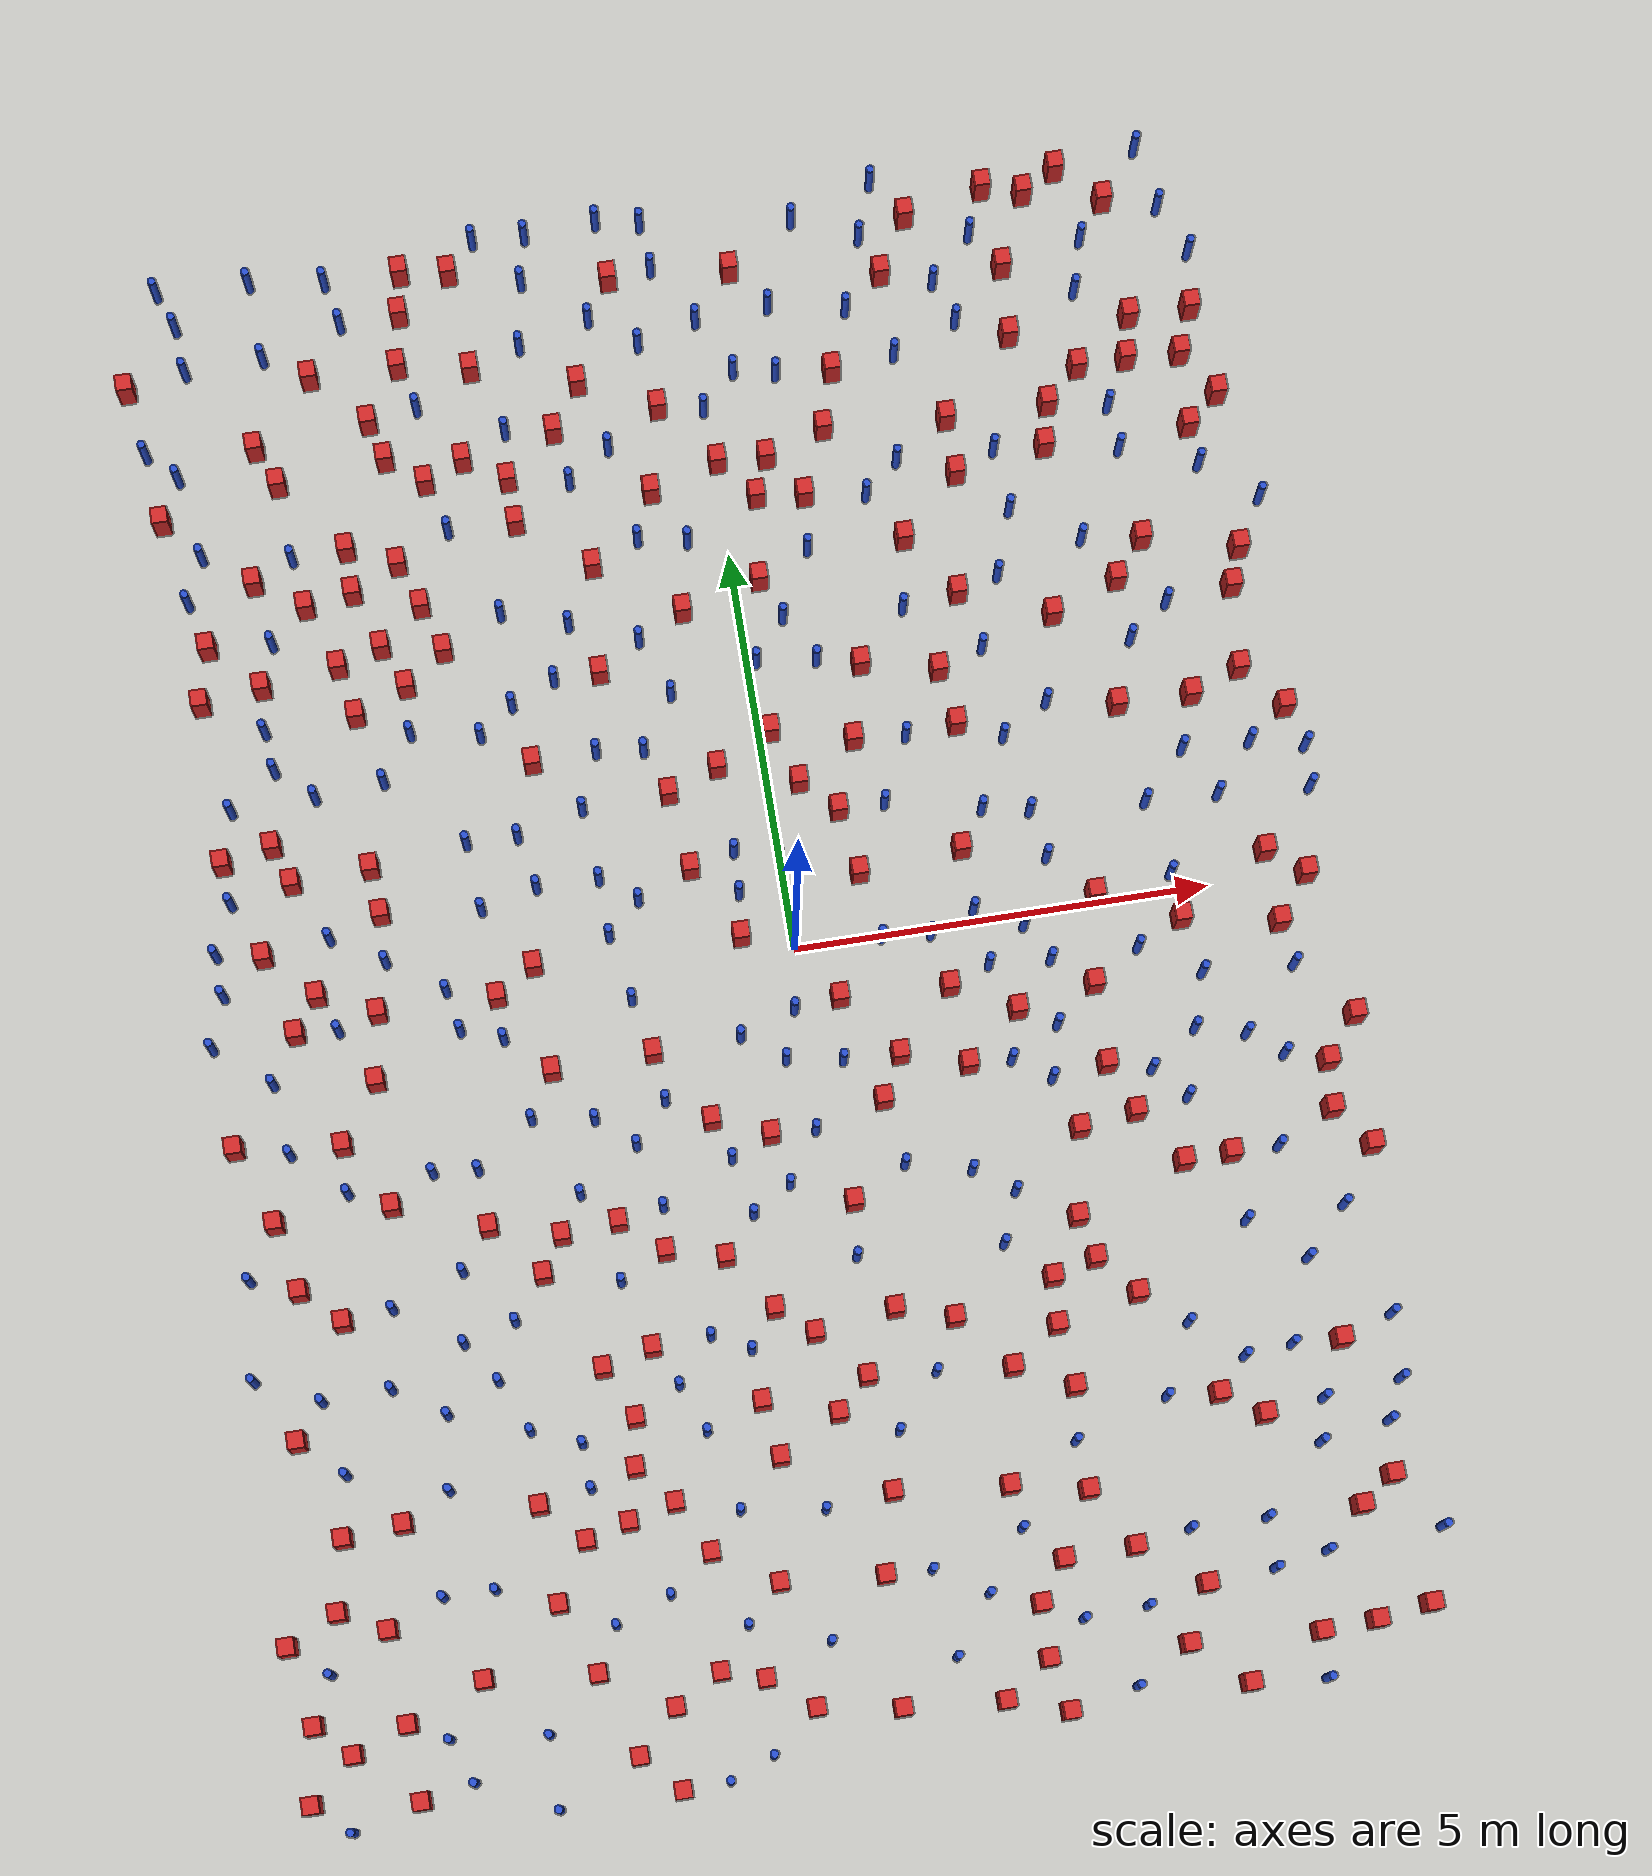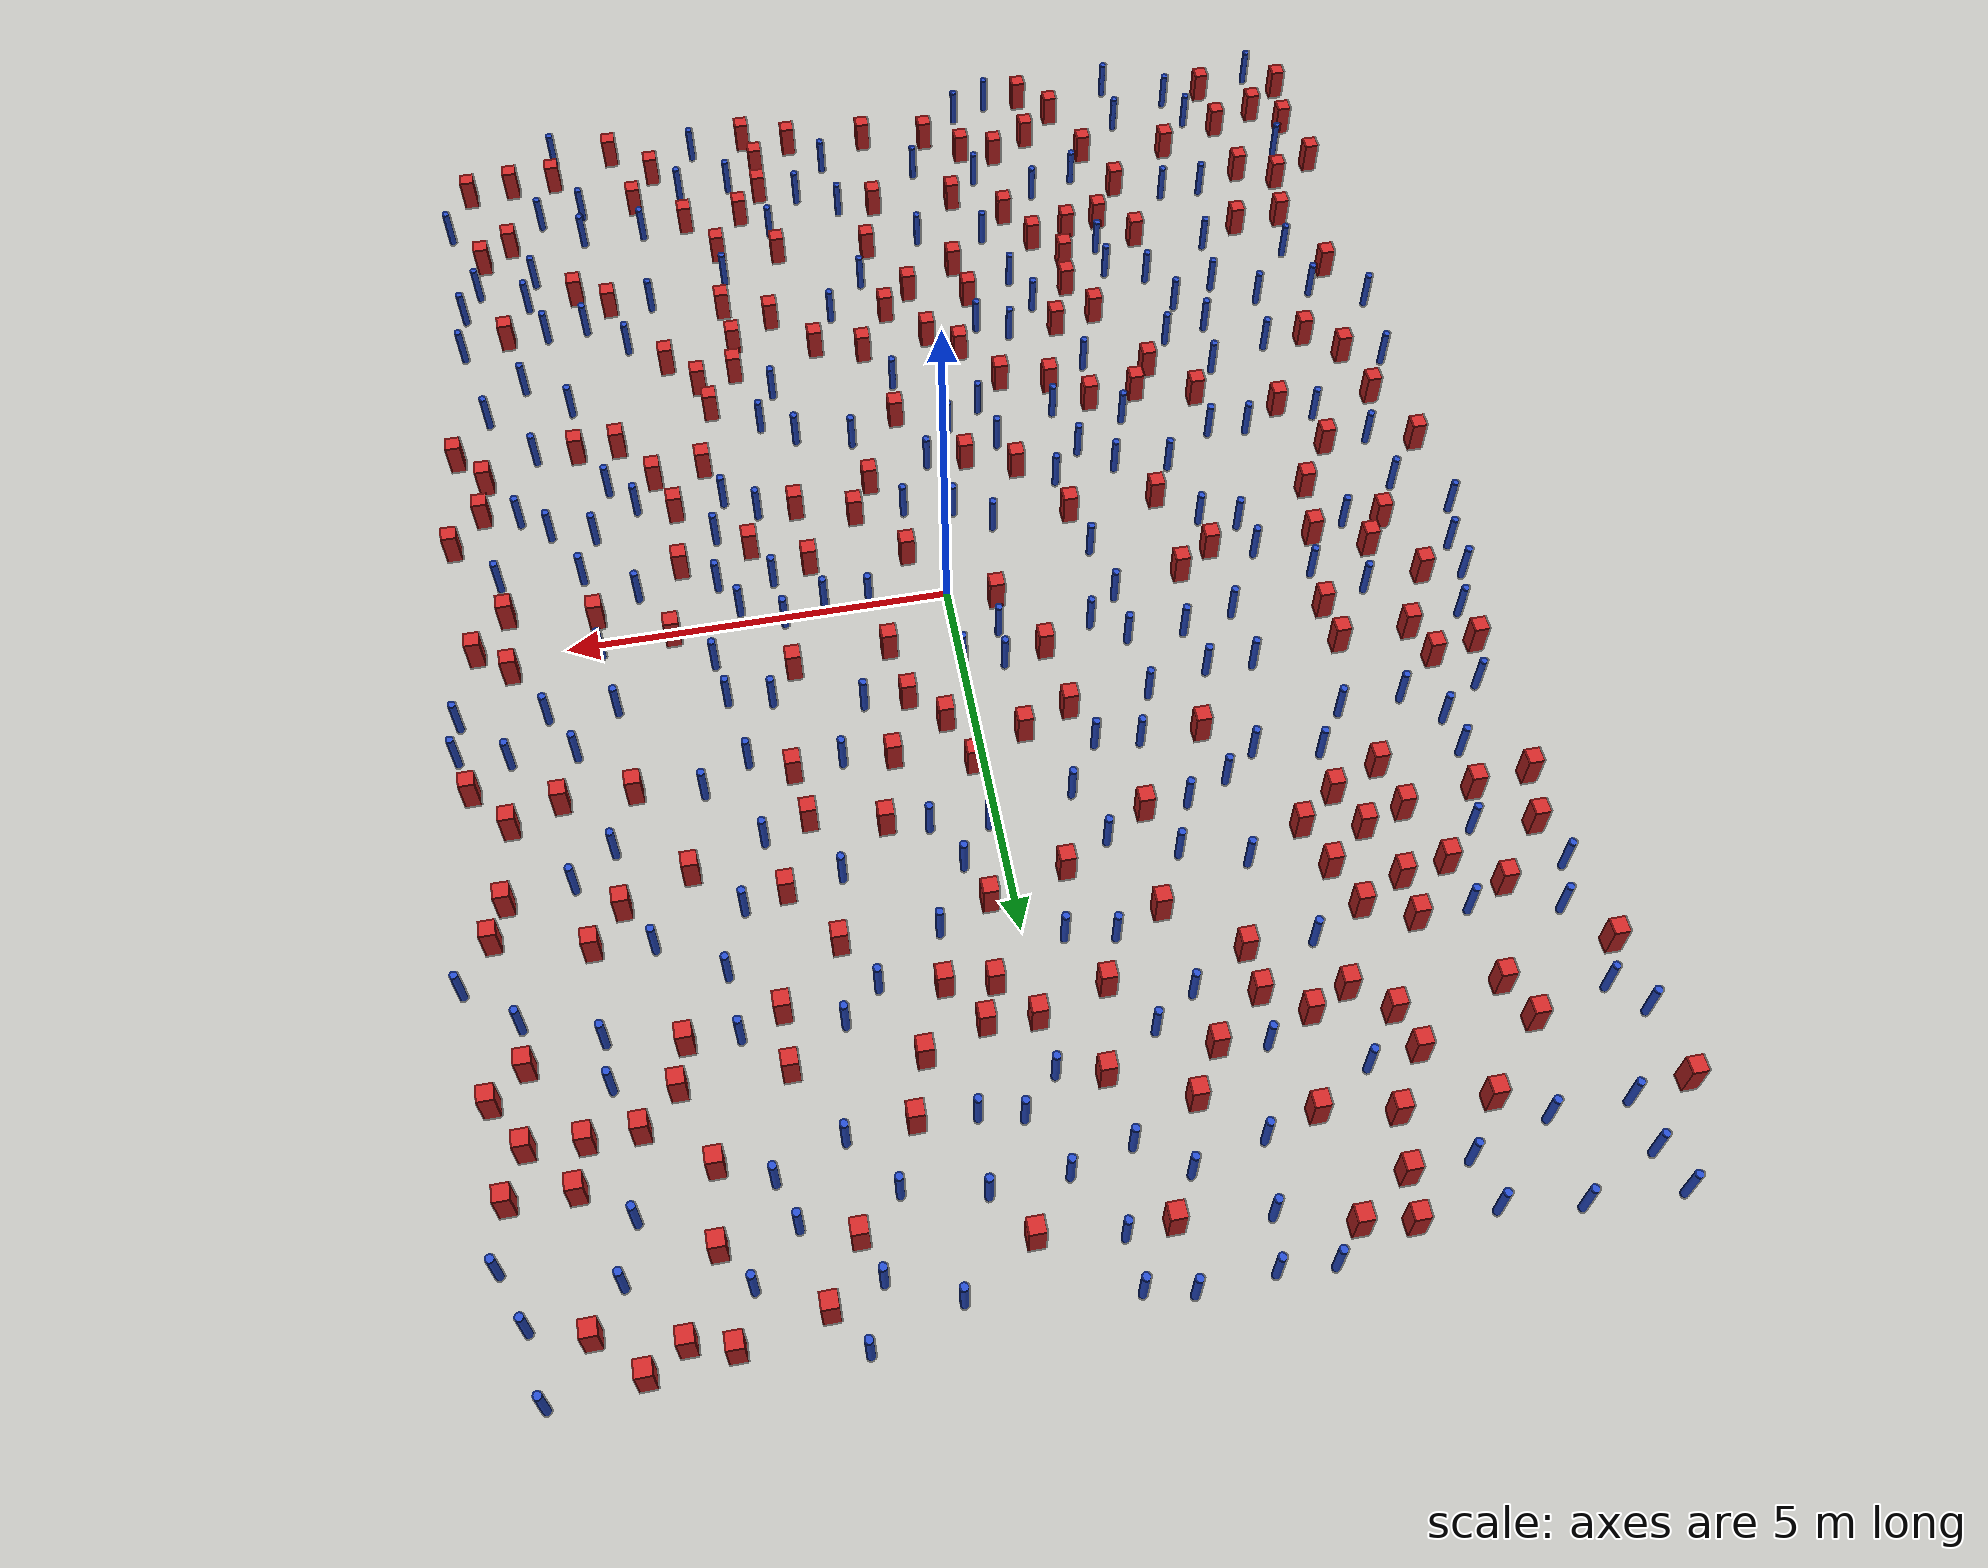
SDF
<sdf version="1.6">
  <model name="dense_47"><model name="square_post_obstacle0">
  <static>true</static>
  <pose frame="">2.14950272493 0.887067691015 -6.11067671241e-07 -5.50515727128e-06 -8.79689657224e-07 2.37013304536e-05</pose>
  <link name="link">
    <pose frame="">0 0 0.25 0 -0 0</pose>
    <inertial>
      <mass>100</mass>
      <inertia>
        <ixx>0.166667</ixx>
        <ixy>0</ixy>
        <ixz>0</ixz>
        <iyy>0.166667</iyy>
        <iyz>0</iyz>
        <izz>0.166667</izz>
      </inertia>
    </inertial>
    <collision name="collision">
      <geometry>
        <box>
          <size>.2 .2 .5</size>
        </box>
      </geometry>
      <max_contacts>10</max_contacts>
      <surface>
        <contact>
          <ode/>
        </contact>
        <bounce/>
        <friction>
          <torsional>
            <ode/>
          </torsional>
          <ode/>
        </friction>
      </surface>
    </collision>
    <visual name="visual">
      <geometry>
        <box>
          <size>.2 .2 .5</size>
        </box>
      </geometry>
      <material>
        <script>
          <name>Gazebo/Red</name>
          <uri>file://media/materials/scripts/gazebo.material</uri>
        </script>
      </material>
    </visual>
    <self_collide>0</self_collide>
    <kinematic>0</kinematic>
  </link>
</model>
<model name="square_post_obstacle1">
  <static>true</static>
  <pose frame="">2.94212230356 -2.67743986622 -6.11067671241e-07 -5.50515727128e-06 -8.79689657224e-07 2.37013304536e-05</pose>
  <link name="link">
    <pose frame="">0 0 0.25 0 -0 0</pose>
    <inertial>
      <mass>100</mass>
      <inertia>
        <ixx>0.166667</ixx>
        <ixy>0</ixy>
        <ixz>0</ixz>
        <iyy>0.166667</iyy>
        <iyz>0</iyz>
        <izz>0.166667</izz>
      </inertia>
    </inertial>
    <collision name="collision">
      <geometry>
        <box>
          <size>.2 .2 .5</size>
        </box>
      </geometry>
      <max_contacts>10</max_contacts>
      <surface>
        <contact>
          <ode/>
        </contact>
        <bounce/>
        <friction>
          <torsional>
            <ode/>
          </torsional>
          <ode/>
        </friction>
      </surface>
    </collision>
    <visual name="visual">
      <geometry>
        <box>
          <size>.2 .2 .5</size>
        </box>
      </geometry>
      <material>
        <script>
          <name>Gazebo/Red</name>
          <uri>file://media/materials/scripts/gazebo.material</uri>
        </script>
      </material>
    </visual>
    <self_collide>0</self_collide>
    <kinematic>0</kinematic>
  </link>
</model>
<model name="pole_obstacle0">
  <static>true</static>
  <pose frame="">-0.314921129882 -1.32646130541 -9.47619616065e-06 5.49618799738e-07 2.3631041406e-07 -1.550905348e-07</pose>
  <link name="link">
  <pose frame="">0 0 0.3 0 -0 0</pose>
    <inertial>
      <mass>1</mass>
      <inertia>
        <ixx>0.145833</ixx>
        <ixy>0</ixy>
        <ixz>0</ixz>
        <iyy>0.145833</iyy>
        <iyz>0</iyz>
        <izz>0.125</izz>
      </inertia>
    </inertial>
    <collision name="collision">
      <geometry>
        <cylinder>
          <radius>0.05</radius>
          <length>.6</length>
        </cylinder>
      </geometry>
      <max_contacts>10</max_contacts>
      <surface>
        <contact>
          <ode/>
        </contact>
        <bounce/>
        <friction>
          <torsional>
            <ode/>
          </torsional>
          <ode/>
        </friction>
      </surface>
    </collision>
    <visual name="visual">
      <geometry>
        <cylinder>
          <radius>0.05</radius>
          <length>.6</length>
        </cylinder>
      </geometry>
      <material>
        <script>
          <name>Gazebo/Blue</name>
          <uri>file://media/materials/scripts/gazebo.material</uri>
        </script>
      </material>
    </visual>
    <self_collide>0</self_collide>
    <kinematic>0</kinematic>
  </link>
</model>
<model name="square_post_obstacle2">
  <static>true</static>
  <pose frame="">-6.32970047965 -3.15536680253 -6.11067671241e-07 -5.50515727128e-06 -8.79689657224e-07 2.37013304536e-05</pose>
  <link name="link">
    <pose frame="">0 0 0.25 0 -0 0</pose>
    <inertial>
      <mass>100</mass>
      <inertia>
        <ixx>0.166667</ixx>
        <ixy>0</ixy>
        <ixz>0</ixz>
        <iyy>0.166667</iyy>
        <iyz>0</iyz>
        <izz>0.166667</izz>
      </inertia>
    </inertial>
    <collision name="collision">
      <geometry>
        <box>
          <size>.2 .2 .5</size>
        </box>
      </geometry>
      <max_contacts>10</max_contacts>
      <surface>
        <contact>
          <ode/>
        </contact>
        <bounce/>
        <friction>
          <torsional>
            <ode/>
          </torsional>
          <ode/>
        </friction>
      </surface>
    </collision>
    <visual name="visual">
      <geometry>
        <box>
          <size>.2 .2 .5</size>
        </box>
      </geometry>
      <material>
        <script>
          <name>Gazebo/Red</name>
          <uri>file://media/materials/scripts/gazebo.material</uri>
        </script>
      </material>
    </visual>
    <self_collide>0</self_collide>
    <kinematic>0</kinematic>
  </link>
</model>
<model name="pole_obstacle1">
  <static>true</static>
  <pose frame="">1.61974641759 -2.97407490253 -9.47619616065e-06 5.49618799737e-07 2.36310414062e-07 -1.55090534798e-07</pose>
  <link name="link">
  <pose frame="">0 0 0.3 0 -0 0</pose>
    <inertial>
      <mass>1</mass>
      <inertia>
        <ixx>0.145833</ixx>
        <ixy>0</ixy>
        <ixz>0</ixz>
        <iyy>0.145833</iyy>
        <iyz>0</iyz>
        <izz>0.125</izz>
      </inertia>
    </inertial>
    <collision name="collision">
      <geometry>
        <cylinder>
          <radius>0.05</radius>
          <length>.6</length>
        </cylinder>
      </geometry>
      <max_contacts>10</max_contacts>
      <surface>
        <contact>
          <ode/>
        </contact>
        <bounce/>
        <friction>
          <torsional>
            <ode/>
          </torsional>
          <ode/>
        </friction>
      </surface>
    </collision>
    <visual name="visual">
      <geometry>
        <cylinder>
          <radius>0.05</radius>
          <length>.6</length>
        </cylinder>
      </geometry>
      <material>
        <script>
          <name>Gazebo/Blue</name>
          <uri>file://media/materials/scripts/gazebo.material</uri>
        </script>
      </material>
    </visual>
    <self_collide>0</self_collide>
    <kinematic>0</kinematic>
  </link>
</model>
<model name="square_post_obstacle3">
  <static>true</static>
  <pose frame="">3.26243857863 -4.69614410593 -6.11067671241e-07 -5.50515727128e-06 -8.79689657224e-07 2.37013304536e-05</pose>
  <link name="link">
    <pose frame="">0 0 0.25 0 -0 0</pose>
    <inertial>
      <mass>100</mass>
      <inertia>
        <ixx>0.166667</ixx>
        <ixy>0</ixy>
        <ixz>0</ixz>
        <iyy>0.166667</iyy>
        <iyz>0</iyz>
        <izz>0.166667</izz>
      </inertia>
    </inertial>
    <collision name="collision">
      <geometry>
        <box>
          <size>.2 .2 .5</size>
        </box>
      </geometry>
      <max_contacts>10</max_contacts>
      <surface>
        <contact>
          <ode/>
        </contact>
        <bounce/>
        <friction>
          <torsional>
            <ode/>
          </torsional>
          <ode/>
        </friction>
      </surface>
    </collision>
    <visual name="visual">
      <geometry>
        <box>
          <size>.2 .2 .5</size>
        </box>
      </geometry>
      <material>
        <script>
          <name>Gazebo/Red</name>
          <uri>file://media/materials/scripts/gazebo.material</uri>
        </script>
      </material>
    </visual>
    <self_collide>0</self_collide>
    <kinematic>0</kinematic>
  </link>
</model>
<model name="pole_obstacle2">
  <static>true</static>
  <pose frame="">2.73644294295 -2.04410735157 -9.47619616065e-06 5.49618799737e-07 2.36310414068e-07 -1.55090534797e-07</pose>
  <link name="link">
  <pose frame="">0 0 0.3 0 -0 0</pose>
    <inertial>
      <mass>1</mass>
      <inertia>
        <ixx>0.145833</ixx>
        <ixy>0</ixy>
        <ixz>0</ixz>
        <iyy>0.145833</iyy>
        <iyz>0</iyz>
        <izz>0.125</izz>
      </inertia>
    </inertial>
    <collision name="collision">
      <geometry>
        <cylinder>
          <radius>0.05</radius>
          <length>.6</length>
        </cylinder>
      </geometry>
      <max_contacts>10</max_contacts>
      <surface>
        <contact>
          <ode/>
        </contact>
        <bounce/>
        <friction>
          <torsional>
            <ode/>
          </torsional>
          <ode/>
        </friction>
      </surface>
    </collision>
    <visual name="visual">
      <geometry>
        <cylinder>
          <radius>0.05</radius>
          <length>.6</length>
        </cylinder>
      </geometry>
      <material>
        <script>
          <name>Gazebo/Blue</name>
          <uri>file://media/materials/scripts/gazebo.material</uri>
        </script>
      </material>
    </visual>
    <self_collide>0</self_collide>
    <kinematic>0</kinematic>
  </link>
</model>
<model name="pole_obstacle3">
  <static>true</static>
  <pose frame="">-6.2227342623 -1.54788043869 -9.47619616065e-06 5.49618799738e-07 2.36310414071e-07 -1.55090534796e-07</pose>
  <link name="link">
  <pose frame="">0 0 0.3 0 -0 0</pose>
    <inertial>
      <mass>1</mass>
      <inertia>
        <ixx>0.145833</ixx>
        <ixy>0</ixy>
        <ixz>0</ixz>
        <iyy>0.145833</iyy>
        <iyz>0</iyz>
        <izz>0.125</izz>
      </inertia>
    </inertial>
    <collision name="collision">
      <geometry>
        <cylinder>
          <radius>0.05</radius>
          <length>.6</length>
        </cylinder>
      </geometry>
      <max_contacts>10</max_contacts>
      <surface>
        <contact>
          <ode/>
        </contact>
        <bounce/>
        <friction>
          <torsional>
            <ode/>
          </torsional>
          <ode/>
        </friction>
      </surface>
    </collision>
    <visual name="visual">
      <geometry>
        <cylinder>
          <radius>0.05</radius>
          <length>.6</length>
        </cylinder>
      </geometry>
      <material>
        <script>
          <name>Gazebo/Blue</name>
          <uri>file://media/materials/scripts/gazebo.material</uri>
        </script>
      </material>
    </visual>
    <self_collide>0</self_collide>
    <kinematic>0</kinematic>
  </link>
</model>
<model name="square_post_obstacle4">
  <static>true</static>
  <pose frame="">5.32736103895 7.24112209833 -6.11067671241e-07 -5.50515727128e-06 -8.79689657224e-07 2.37013304536e-05</pose>
  <link name="link">
    <pose frame="">0 0 0.25 0 -0 0</pose>
    <inertial>
      <mass>100</mass>
      <inertia>
        <ixx>0.166667</ixx>
        <ixy>0</ixy>
        <ixz>0</ixz>
        <iyy>0.166667</iyy>
        <iyz>0</iyz>
        <izz>0.166667</izz>
      </inertia>
    </inertial>
    <collision name="collision">
      <geometry>
        <box>
          <size>.2 .2 .5</size>
        </box>
      </geometry>
      <max_contacts>10</max_contacts>
      <surface>
        <contact>
          <ode/>
        </contact>
        <bounce/>
        <friction>
          <torsional>
            <ode/>
          </torsional>
          <ode/>
        </friction>
      </surface>
    </collision>
    <visual name="visual">
      <geometry>
        <box>
          <size>.2 .2 .5</size>
        </box>
      </geometry>
      <material>
        <script>
          <name>Gazebo/Red</name>
          <uri>file://media/materials/scripts/gazebo.material</uri>
        </script>
      </material>
    </visual>
    <self_collide>0</self_collide>
    <kinematic>0</kinematic>
  </link>
</model>
<model name="square_post_obstacle5">
  <static>true</static>
  <pose frame="">3.12100335999 -8.73791378668 -6.11067671241e-07 -5.50515727128e-06 -8.79689657224e-07 2.37013304536e-05</pose>
  <link name="link">
    <pose frame="">0 0 0.25 0 -0 0</pose>
    <inertial>
      <mass>100</mass>
      <inertia>
        <ixx>0.166667</ixx>
        <ixy>0</ixy>
        <ixz>0</ixz>
        <iyy>0.166667</iyy>
        <iyz>0</iyz>
        <izz>0.166667</izz>
      </inertia>
    </inertial>
    <collision name="collision">
      <geometry>
        <box>
          <size>.2 .2 .5</size>
        </box>
      </geometry>
      <max_contacts>10</max_contacts>
      <surface>
        <contact>
          <ode/>
        </contact>
        <bounce/>
        <friction>
          <torsional>
            <ode/>
          </torsional>
          <ode/>
        </friction>
      </surface>
    </collision>
    <visual name="visual">
      <geometry>
        <box>
          <size>.2 .2 .5</size>
        </box>
      </geometry>
      <material>
        <script>
          <name>Gazebo/Red</name>
          <uri>file://media/materials/scripts/gazebo.material</uri>
        </script>
      </material>
    </visual>
    <self_collide>0</self_collide>
    <kinematic>0</kinematic>
  </link>
</model>
<model name="square_post_obstacle6">
  <static>true</static>
  <pose frame="">-6.57756571265 -4.88262852347 -6.11067671241e-07 -5.50515727128e-06 -8.79689657224e-07 2.37013304536e-05</pose>
  <link name="link">
    <pose frame="">0 0 0.25 0 -0 0</pose>
    <inertial>
      <mass>100</mass>
      <inertia>
        <ixx>0.166667</ixx>
        <ixy>0</ixy>
        <ixz>0</ixz>
        <iyy>0.166667</iyy>
        <iyz>0</iyz>
        <izz>0.166667</izz>
      </inertia>
    </inertial>
    <collision name="collision">
      <geometry>
        <box>
          <size>.2 .2 .5</size>
        </box>
      </geometry>
      <max_contacts>10</max_contacts>
      <surface>
        <contact>
          <ode/>
        </contact>
        <bounce/>
        <friction>
          <torsional>
            <ode/>
          </torsional>
          <ode/>
        </friction>
      </surface>
    </collision>
    <visual name="visual">
      <geometry>
        <box>
          <size>.2 .2 .5</size>
        </box>
      </geometry>
      <material>
        <script>
          <name>Gazebo/Red</name>
          <uri>file://media/materials/scripts/gazebo.material</uri>
        </script>
      </material>
    </visual>
    <self_collide>0</self_collide>
    <kinematic>0</kinematic>
  </link>
</model>
<model name="pole_obstacle4">
  <static>true</static>
  <pose frame="">-6.55046260767 -7.55333888679 -9.47619616065e-06 5.49618799737e-07 2.36310414037e-07 -1.55090534814e-07</pose>
  <link name="link">
  <pose frame="">0 0 0.3 0 -0 0</pose>
    <inertial>
      <mass>1</mass>
      <inertia>
        <ixx>0.145833</ixx>
        <ixy>0</ixy>
        <ixz>0</ixz>
        <iyy>0.145833</iyy>
        <iyz>0</iyz>
        <izz>0.125</izz>
      </inertia>
    </inertial>
    <collision name="collision">
      <geometry>
        <cylinder>
          <radius>0.05</radius>
          <length>.6</length>
        </cylinder>
      </geometry>
      <max_contacts>10</max_contacts>
      <surface>
        <contact>
          <ode/>
        </contact>
        <bounce/>
        <friction>
          <torsional>
            <ode/>
          </torsional>
          <ode/>
        </friction>
      </surface>
    </collision>
    <visual name="visual">
      <geometry>
        <cylinder>
          <radius>0.05</radius>
          <length>.6</length>
        </cylinder>
      </geometry>
      <material>
        <script>
          <name>Gazebo/Blue</name>
          <uri>file://media/materials/scripts/gazebo.material</uri>
        </script>
      </material>
    </visual>
    <self_collide>0</self_collide>
    <kinematic>0</kinematic>
  </link>
</model>
<model name="pole_obstacle5">
  <static>true</static>
  <pose frame="">-1.9876738178 8.84588879229 -9.47619616065e-06 5.49618799737e-07 2.36310414046e-07 -1.55090534809e-07</pose>
  <link name="link">
  <pose frame="">0 0 0.3 0 -0 0</pose>
    <inertial>
      <mass>1</mass>
      <inertia>
        <ixx>0.145833</ixx>
        <ixy>0</ixy>
        <ixz>0</ixz>
        <iyy>0.145833</iyy>
        <iyz>0</iyz>
        <izz>0.125</izz>
      </inertia>
    </inertial>
    <collision name="collision">
      <geometry>
        <cylinder>
          <radius>0.05</radius>
          <length>.6</length>
        </cylinder>
      </geometry>
      <max_contacts>10</max_contacts>
      <surface>
        <contact>
          <ode/>
        </contact>
        <bounce/>
        <friction>
          <torsional>
            <ode/>
          </torsional>
          <ode/>
        </friction>
      </surface>
    </collision>
    <visual name="visual">
      <geometry>
        <cylinder>
          <radius>0.05</radius>
          <length>.6</length>
        </cylinder>
      </geometry>
      <material>
        <script>
          <name>Gazebo/Blue</name>
          <uri>file://media/materials/scripts/gazebo.material</uri>
        </script>
      </material>
    </visual>
    <self_collide>0</self_collide>
    <kinematic>0</kinematic>
  </link>
</model>
<model name="square_post_obstacle7">
  <static>true</static>
  <pose frame="">-3.64312884776 7.99833205098 -6.11067671241e-07 -5.50515727128e-06 -8.79689657224e-07 2.37013304536e-05</pose>
  <link name="link">
    <pose frame="">0 0 0.25 0 -0 0</pose>
    <inertial>
      <mass>100</mass>
      <inertia>
        <ixx>0.166667</ixx>
        <ixy>0</ixy>
        <ixz>0</ixz>
        <iyy>0.166667</iyy>
        <iyz>0</iyz>
        <izz>0.166667</izz>
      </inertia>
    </inertial>
    <collision name="collision">
      <geometry>
        <box>
          <size>.2 .2 .5</size>
        </box>
      </geometry>
      <max_contacts>10</max_contacts>
      <surface>
        <contact>
          <ode/>
        </contact>
        <bounce/>
        <friction>
          <torsional>
            <ode/>
          </torsional>
          <ode/>
        </friction>
      </surface>
    </collision>
    <visual name="visual">
      <geometry>
        <box>
          <size>.2 .2 .5</size>
        </box>
      </geometry>
      <material>
        <script>
          <name>Gazebo/Red</name>
          <uri>file://media/materials/scripts/gazebo.material</uri>
        </script>
      </material>
    </visual>
    <self_collide>0</self_collide>
    <kinematic>0</kinematic>
  </link>
</model>
<model name="square_post_obstacle8">
  <static>true</static>
  <pose frame="">0.454852173999 -4.42956170193 -6.11067671241e-07 -5.50515727128e-06 -8.79689657224e-07 2.37013304536e-05</pose>
  <link name="link">
    <pose frame="">0 0 0.25 0 -0 0</pose>
    <inertial>
      <mass>100</mass>
      <inertia>
        <ixx>0.166667</ixx>
        <ixy>0</ixy>
        <ixz>0</ixz>
        <iyy>0.166667</iyy>
        <iyz>0</iyz>
        <izz>0.166667</izz>
      </inertia>
    </inertial>
    <collision name="collision">
      <geometry>
        <box>
          <size>.2 .2 .5</size>
        </box>
      </geometry>
      <max_contacts>10</max_contacts>
      <surface>
        <contact>
          <ode/>
        </contact>
        <bounce/>
        <friction>
          <torsional>
            <ode/>
          </torsional>
          <ode/>
        </friction>
      </surface>
    </collision>
    <visual name="visual">
      <geometry>
        <box>
          <size>.2 .2 .5</size>
        </box>
      </geometry>
      <material>
        <script>
          <name>Gazebo/Red</name>
          <uri>file://media/materials/scripts/gazebo.material</uri>
        </script>
      </material>
    </visual>
    <self_collide>0</self_collide>
    <kinematic>0</kinematic>
  </link>
</model>
<model name="pole_obstacle6">
  <static>true</static>
  <pose frame="">3.78379597058 -5.12910789023 -9.47619616065e-06 5.49618799738e-07 2.3631041406e-07 -1.55090534801e-07</pose>
  <link name="link">
  <pose frame="">0 0 0.3 0 -0 0</pose>
    <inertial>
      <mass>1</mass>
      <inertia>
        <ixx>0.145833</ixx>
        <ixy>0</ixy>
        <ixz>0</ixz>
        <iyy>0.145833</iyy>
        <iyz>0</iyz>
        <izz>0.125</izz>
      </inertia>
    </inertial>
    <collision name="collision">
      <geometry>
        <cylinder>
          <radius>0.05</radius>
          <length>.6</length>
        </cylinder>
      </geometry>
      <max_contacts>10</max_contacts>
      <surface>
        <contact>
          <ode/>
        </contact>
        <bounce/>
        <friction>
          <torsional>
            <ode/>
          </torsional>
          <ode/>
        </friction>
      </surface>
    </collision>
    <visual name="visual">
      <geometry>
        <cylinder>
          <radius>0.05</radius>
          <length>.6</length>
        </cylinder>
      </geometry>
      <material>
        <script>
          <name>Gazebo/Blue</name>
          <uri>file://media/materials/scripts/gazebo.material</uri>
        </script>
      </material>
    </visual>
    <self_collide>0</self_collide>
    <kinematic>0</kinematic>
  </link>
</model>
<model name="pole_obstacle7">
  <static>true</static>
  <pose frame="">0.109177409694 3.56442572552 -9.47619616065e-06 5.49618799737e-07 2.36310414059e-07 -1.550905348e-07</pose>
  <link name="link">
  <pose frame="">0 0 0.3 0 -0 0</pose>
    <inertial>
      <mass>1</mass>
      <inertia>
        <ixx>0.145833</ixx>
        <ixy>0</ixy>
        <ixz>0</ixz>
        <iyy>0.145833</iyy>
        <iyz>0</iyz>
        <izz>0.125</izz>
      </inertia>
    </inertial>
    <collision name="collision">
      <geometry>
        <cylinder>
          <radius>0.05</radius>
          <length>.6</length>
        </cylinder>
      </geometry>
      <max_contacts>10</max_contacts>
      <surface>
        <contact>
          <ode/>
        </contact>
        <bounce/>
        <friction>
          <torsional>
            <ode/>
          </torsional>
          <ode/>
        </friction>
      </surface>
    </collision>
    <visual name="visual">
      <geometry>
        <cylinder>
          <radius>0.05</radius>
          <length>.6</length>
        </cylinder>
      </geometry>
      <material>
        <script>
          <name>Gazebo/Blue</name>
          <uri>file://media/materials/scripts/gazebo.material</uri>
        </script>
      </material>
    </visual>
    <self_collide>0</self_collide>
    <kinematic>0</kinematic>
  </link>
</model>
<model name="square_post_obstacle9">
  <static>true</static>
  <pose frame="">-6.99141399774 -7.1748597416 -6.11067671241e-07 -5.50515727128e-06 -8.79689657224e-07 2.37013304536e-05</pose>
  <link name="link">
    <pose frame="">0 0 0.25 0 -0 0</pose>
    <inertial>
      <mass>100</mass>
      <inertia>
        <ixx>0.166667</ixx>
        <ixy>0</ixy>
        <ixz>0</ixz>
        <iyy>0.166667</iyy>
        <iyz>0</iyz>
        <izz>0.166667</izz>
      </inertia>
    </inertial>
    <collision name="collision">
      <geometry>
        <box>
          <size>.2 .2 .5</size>
        </box>
      </geometry>
      <max_contacts>10</max_contacts>
      <surface>
        <contact>
          <ode/>
        </contact>
        <bounce/>
        <friction>
          <torsional>
            <ode/>
          </torsional>
          <ode/>
        </friction>
      </surface>
    </collision>
    <visual name="visual">
      <geometry>
        <box>
          <size>.2 .2 .5</size>
        </box>
      </geometry>
      <material>
        <script>
          <name>Gazebo/Red</name>
          <uri>file://media/materials/scripts/gazebo.material</uri>
        </script>
      </material>
    </visual>
    <self_collide>0</self_collide>
    <kinematic>0</kinematic>
  </link>
</model>
<model name="square_post_obstacle10">
  <static>true</static>
  <pose frame="">-5.72387415668 -9.10628945442 -6.11067671241e-07 -5.50515727128e-06 -8.79689657224e-07 2.37013304536e-05</pose>
  <link name="link">
    <pose frame="">0 0 0.25 0 -0 0</pose>
    <inertial>
      <mass>100</mass>
      <inertia>
        <ixx>0.166667</ixx>
        <ixy>0</ixy>
        <ixz>0</ixz>
        <iyy>0.166667</iyy>
        <iyz>0</iyz>
        <izz>0.166667</izz>
      </inertia>
    </inertial>
    <collision name="collision">
      <geometry>
        <box>
          <size>.2 .2 .5</size>
        </box>
      </geometry>
      <max_contacts>10</max_contacts>
      <surface>
        <contact>
          <ode/>
        </contact>
        <bounce/>
        <friction>
          <torsional>
            <ode/>
          </torsional>
          <ode/>
        </friction>
      </surface>
    </collision>
    <visual name="visual">
      <geometry>
        <box>
          <size>.2 .2 .5</size>
        </box>
      </geometry>
      <material>
        <script>
          <name>Gazebo/Red</name>
          <uri>file://media/materials/scripts/gazebo.material</uri>
        </script>
      </material>
    </visual>
    <self_collide>0</self_collide>
    <kinematic>0</kinematic>
  </link>
</model>
<model name="square_post_obstacle11">
  <static>true</static>
  <pose frame="">-6.20760111522 -6.0575947766 -6.11067671241e-07 -5.50515727128e-06 -8.79689657224e-07 2.37013304536e-05</pose>
  <link name="link">
    <pose frame="">0 0 0.25 0 -0 0</pose>
    <inertial>
      <mass>100</mass>
      <inertia>
        <ixx>0.166667</ixx>
        <ixy>0</ixy>
        <ixz>0</ixz>
        <iyy>0.166667</iyy>
        <iyz>0</iyz>
        <izz>0.166667</izz>
      </inertia>
    </inertial>
    <collision name="collision">
      <geometry>
        <box>
          <size>.2 .2 .5</size>
        </box>
      </geometry>
      <max_contacts>10</max_contacts>
      <surface>
        <contact>
          <ode/>
        </contact>
        <bounce/>
        <friction>
          <torsional>
            <ode/>
          </torsional>
          <ode/>
        </friction>
      </surface>
    </collision>
    <visual name="visual">
      <geometry>
        <box>
          <size>.2 .2 .5</size>
        </box>
      </geometry>
      <material>
        <script>
          <name>Gazebo/Red</name>
          <uri>file://media/materials/scripts/gazebo.material</uri>
        </script>
      </material>
    </visual>
    <self_collide>0</self_collide>
    <kinematic>0</kinematic>
  </link>
</model>
<model name="square_post_obstacle12">
  <static>true</static>
  <pose frame="">-6.81024050324 -8.09693723005 -6.11067671241e-07 -5.50515727128e-06 -8.79689657224e-07 2.37013304536e-05</pose>
  <link name="link">
    <pose frame="">0 0 0.25 0 -0 0</pose>
    <inertial>
      <mass>100</mass>
      <inertia>
        <ixx>0.166667</ixx>
        <ixy>0</ixy>
        <ixz>0</ixz>
        <iyy>0.166667</iyy>
        <iyz>0</iyz>
        <izz>0.166667</izz>
      </inertia>
    </inertial>
    <collision name="collision">
      <geometry>
        <box>
          <size>.2 .2 .5</size>
        </box>
      </geometry>
      <max_contacts>10</max_contacts>
      <surface>
        <contact>
          <ode/>
        </contact>
        <bounce/>
        <friction>
          <torsional>
            <ode/>
          </torsional>
          <ode/>
        </friction>
      </surface>
    </collision>
    <visual name="visual">
      <geometry>
        <box>
          <size>.2 .2 .5</size>
        </box>
      </geometry>
      <material>
        <script>
          <name>Gazebo/Red</name>
          <uri>file://media/materials/scripts/gazebo.material</uri>
        </script>
      </material>
    </visual>
    <self_collide>0</self_collide>
    <kinematic>0</kinematic>
  </link>
</model>
<model name="square_post_obstacle13">
  <static>true</static>
  <pose frame="">-0.571490426426 6.97470407027 -6.11067671241e-07 -5.50515727128e-06 -8.79689657224e-07 2.37013304536e-05</pose>
  <link name="link">
    <pose frame="">0 0 0.25 0 -0 0</pose>
    <inertial>
      <mass>100</mass>
      <inertia>
        <ixx>0.166667</ixx>
        <ixy>0</ixy>
        <ixz>0</ixz>
        <iyy>0.166667</iyy>
        <iyz>0</iyz>
        <izz>0.166667</izz>
      </inertia>
    </inertial>
    <collision name="collision">
      <geometry>
        <box>
          <size>.2 .2 .5</size>
        </box>
      </geometry>
      <max_contacts>10</max_contacts>
      <surface>
        <contact>
          <ode/>
        </contact>
        <bounce/>
        <friction>
          <torsional>
            <ode/>
          </torsional>
          <ode/>
        </friction>
      </surface>
    </collision>
    <visual name="visual">
      <geometry>
        <box>
          <size>.2 .2 .5</size>
        </box>
      </geometry>
      <material>
        <script>
          <name>Gazebo/Red</name>
          <uri>file://media/materials/scripts/gazebo.material</uri>
        </script>
      </material>
    </visual>
    <self_collide>0</self_collide>
    <kinematic>0</kinematic>
  </link>
</model>
<model name="pole_obstacle8">
  <static>true</static>
  <pose frame="">4.41853651223 1.09801838335 -9.47619616065e-06 5.49618799738e-07 2.36310414071e-07 -1.55090534796e-07</pose>
  <link name="link">
  <pose frame="">0 0 0.3 0 -0 0</pose>
    <inertial>
      <mass>1</mass>
      <inertia>
        <ixx>0.145833</ixx>
        <ixy>0</ixy>
        <ixz>0</ixz>
        <iyy>0.145833</iyy>
        <iyz>0</iyz>
        <izz>0.125</izz>
      </inertia>
    </inertial>
    <collision name="collision">
      <geometry>
        <cylinder>
          <radius>0.05</radius>
          <length>.6</length>
        </cylinder>
      </geometry>
      <max_contacts>10</max_contacts>
      <surface>
        <contact>
          <ode/>
        </contact>
        <bounce/>
        <friction>
          <torsional>
            <ode/>
          </torsional>
          <ode/>
        </friction>
      </surface>
    </collision>
    <visual name="visual">
      <geometry>
        <cylinder>
          <radius>0.05</radius>
          <length>.6</length>
        </cylinder>
      </geometry>
      <material>
        <script>
          <name>Gazebo/Blue</name>
          <uri>file://media/materials/scripts/gazebo.material</uri>
        </script>
      </material>
    </visual>
    <self_collide>0</self_collide>
    <kinematic>0</kinematic>
  </link>
</model>
<model name="square_post_obstacle14">
  <static>true</static>
  <pose frame="">-5.83653238779 -7.16018827022 -6.11067671241e-07 -5.50515727128e-06 -8.79689657224e-07 2.37013304536e-05</pose>
  <link name="link">
    <pose frame="">0 0 0.25 0 -0 0</pose>
    <inertial>
      <mass>100</mass>
      <inertia>
        <ixx>0.166667</ixx>
        <ixy>0</ixy>
        <ixz>0</ixz>
        <iyy>0.166667</iyy>
        <iyz>0</iyz>
        <izz>0.166667</izz>
      </inertia>
    </inertial>
    <collision name="collision">
      <geometry>
        <box>
          <size>.2 .2 .5</size>
        </box>
      </geometry>
      <max_contacts>10</max_contacts>
      <surface>
        <contact>
          <ode/>
        </contact>
        <bounce/>
        <friction>
          <torsional>
            <ode/>
          </torsional>
          <ode/>
        </friction>
      </surface>
    </collision>
    <visual name="visual">
      <geometry>
        <box>
          <size>.2 .2 .5</size>
        </box>
      </geometry>
      <material>
        <script>
          <name>Gazebo/Red</name>
          <uri>file://media/materials/scripts/gazebo.material</uri>
        </script>
      </material>
    </visual>
    <self_collide>0</self_collide>
    <kinematic>0</kinematic>
  </link>
</model>
<model name="square_post_obstacle15">
  <static>true</static>
  <pose frame="">4.7607589038 9.30322569417 -6.11067671241e-07 -5.50515727128e-06 -8.79689657224e-07 2.37013304536e-05</pose>
  <link name="link">
    <pose frame="">0 0 0.25 0 -0 0</pose>
    <inertial>
      <mass>100</mass>
      <inertia>
        <ixx>0.166667</ixx>
        <ixy>0</ixy>
        <ixz>0</ixz>
        <iyy>0.166667</iyy>
        <iyz>0</iyz>
        <izz>0.166667</izz>
      </inertia>
    </inertial>
    <collision name="collision">
      <geometry>
        <box>
          <size>.2 .2 .5</size>
        </box>
      </geometry>
      <max_contacts>10</max_contacts>
      <surface>
        <contact>
          <ode/>
        </contact>
        <bounce/>
        <friction>
          <torsional>
            <ode/>
          </torsional>
          <ode/>
        </friction>
      </surface>
    </collision>
    <visual name="visual">
      <geometry>
        <box>
          <size>.2 .2 .5</size>
        </box>
      </geometry>
      <material>
        <script>
          <name>Gazebo/Red</name>
          <uri>file://media/materials/scripts/gazebo.material</uri>
        </script>
      </material>
    </visual>
    <self_collide>0</self_collide>
    <kinematic>0</kinematic>
  </link>
</model>
<model name="square_post_obstacle16">
  <static>true</static>
  <pose frame="">2.29584751034 -6.84661061984 -6.11067671241e-07 -5.50515727128e-06 -8.79689657224e-07 2.37013304536e-05</pose>
  <link name="link">
    <pose frame="">0 0 0.25 0 -0 0</pose>
    <inertial>
      <mass>100</mass>
      <inertia>
        <ixx>0.166667</ixx>
        <ixy>0</ixy>
        <ixz>0</ixz>
        <iyy>0.166667</iyy>
        <iyz>0</iyz>
        <izz>0.166667</izz>
      </inertia>
    </inertial>
    <collision name="collision">
      <geometry>
        <box>
          <size>.2 .2 .5</size>
        </box>
      </geometry>
      <max_contacts>10</max_contacts>
      <surface>
        <contact>
          <ode/>
        </contact>
        <bounce/>
        <friction>
          <torsional>
            <ode/>
          </torsional>
          <ode/>
        </friction>
      </surface>
    </collision>
    <visual name="visual">
      <geometry>
        <box>
          <size>.2 .2 .5</size>
        </box>
      </geometry>
      <material>
        <script>
          <name>Gazebo/Red</name>
          <uri>file://media/materials/scripts/gazebo.material</uri>
        </script>
      </material>
    </visual>
    <self_collide>0</self_collide>
    <kinematic>0</kinematic>
  </link>
</model>
<model name="pole_obstacle9">
  <static>true</static>
  <pose frame="">-0.106066016489 -2.21200483704 -9.47619616065e-06 5.49618799737e-07 2.36310414067e-07 -1.55090534797e-07</pose>
  <link name="link">
  <pose frame="">0 0 0.3 0 -0 0</pose>
    <inertial>
      <mass>1</mass>
      <inertia>
        <ixx>0.145833</ixx>
        <ixy>0</ixy>
        <ixz>0</ixz>
        <iyy>0.145833</iyy>
        <iyz>0</iyz>
        <izz>0.125</izz>
      </inertia>
    </inertial>
    <collision name="collision">
      <geometry>
        <cylinder>
          <radius>0.05</radius>
          <length>.6</length>
        </cylinder>
      </geometry>
      <max_contacts>10</max_contacts>
      <surface>
        <contact>
          <ode/>
        </contact>
        <bounce/>
        <friction>
          <torsional>
            <ode/>
          </torsional>
          <ode/>
        </friction>
      </surface>
    </collision>
    <visual name="visual">
      <geometry>
        <cylinder>
          <radius>0.05</radius>
          <length>.6</length>
        </cylinder>
      </geometry>
      <material>
        <script>
          <name>Gazebo/Blue</name>
          <uri>file://media/materials/scripts/gazebo.material</uri>
        </script>
      </material>
    </visual>
    <self_collide>0</self_collide>
    <kinematic>0</kinematic>
  </link>
</model>
<model name="square_post_obstacle17">
  <static>true</static>
  <pose frame="">-5.74236140276 5.49527199091 -6.11067671241e-07 -5.50515727128e-06 -8.79689657224e-07 2.37013304536e-05</pose>
  <link name="link">
    <pose frame="">0 0 0.25 0 -0 0</pose>
    <inertial>
      <mass>100</mass>
      <inertia>
        <ixx>0.166667</ixx>
        <ixy>0</ixy>
        <ixz>0</ixz>
        <iyy>0.166667</iyy>
        <iyz>0</iyz>
        <izz>0.166667</izz>
      </inertia>
    </inertial>
    <collision name="collision">
      <geometry>
        <box>
          <size>.2 .2 .5</size>
        </box>
      </geometry>
      <max_contacts>10</max_contacts>
      <surface>
        <contact>
          <ode/>
        </contact>
        <bounce/>
        <friction>
          <torsional>
            <ode/>
          </torsional>
          <ode/>
        </friction>
      </surface>
    </collision>
    <visual name="visual">
      <geometry>
        <box>
          <size>.2 .2 .5</size>
        </box>
      </geometry>
      <material>
        <script>
          <name>Gazebo/Red</name>
          <uri>file://media/materials/scripts/gazebo.material</uri>
        </script>
      </material>
    </visual>
    <self_collide>0</self_collide>
    <kinematic>0</kinematic>
  </link>
</model>
<model name="square_post_obstacle18">
  <static>true</static>
  <pose frame="">1.72993242123 -0.749958943842 -6.11067671241e-07 -5.50515727128e-06 -8.79689657224e-07 2.37013304536e-05</pose>
  <link name="link">
    <pose frame="">0 0 0.25 0 -0 0</pose>
    <inertial>
      <mass>100</mass>
      <inertia>
        <ixx>0.166667</ixx>
        <ixy>0</ixy>
        <ixz>0</ixz>
        <iyy>0.166667</iyy>
        <iyz>0</iyz>
        <izz>0.166667</izz>
      </inertia>
    </inertial>
    <collision name="collision">
      <geometry>
        <box>
          <size>.2 .2 .5</size>
        </box>
      </geometry>
      <max_contacts>10</max_contacts>
      <surface>
        <contact>
          <ode/>
        </contact>
        <bounce/>
        <friction>
          <torsional>
            <ode/>
          </torsional>
          <ode/>
        </friction>
      </surface>
    </collision>
    <visual name="visual">
      <geometry>
        <box>
          <size>.2 .2 .5</size>
        </box>
      </geometry>
      <material>
        <script>
          <name>Gazebo/Red</name>
          <uri>file://media/materials/scripts/gazebo.material</uri>
        </script>
      </material>
    </visual>
    <self_collide>0</self_collide>
    <kinematic>0</kinematic>
  </link>
</model>
<model name="pole_obstacle10">
  <static>true</static>
  <pose frame="">-2.84747566872 4.63940066756 -9.47619616065e-06 5.49618799738e-07 2.3631041406e-07 -1.55090534801e-07</pose>
  <link name="link">
  <pose frame="">0 0 0.3 0 -0 0</pose>
    <inertial>
      <mass>1</mass>
      <inertia>
        <ixx>0.145833</ixx>
        <ixy>0</ixy>
        <ixz>0</ixz>
        <iyy>0.145833</iyy>
        <iyz>0</iyz>
        <izz>0.125</izz>
      </inertia>
    </inertial>
    <collision name="collision">
      <geometry>
        <cylinder>
          <radius>0.05</radius>
          <length>.6</length>
        </cylinder>
      </geometry>
      <max_contacts>10</max_contacts>
      <surface>
        <contact>
          <ode/>
        </contact>
        <bounce/>
        <friction>
          <torsional>
            <ode/>
          </torsional>
          <ode/>
        </friction>
      </surface>
    </collision>
    <visual name="visual">
      <geometry>
        <cylinder>
          <radius>0.05</radius>
          <length>.6</length>
        </cylinder>
      </geometry>
      <material>
        <script>
          <name>Gazebo/Blue</name>
          <uri>file://media/materials/scripts/gazebo.material</uri>
        </script>
      </material>
    </visual>
    <self_collide>0</self_collide>
    <kinematic>0</kinematic>
  </link>
</model>
<model name="square_post_obstacle19">
  <static>true</static>
  <pose frame="">5.91239716687 -8.72316252022 -6.11067671241e-07 -5.50515727128e-06 -8.79689657224e-07 2.37013304536e-05</pose>
  <link name="link">
    <pose frame="">0 0 0.25 0 -0 0</pose>
    <inertial>
      <mass>100</mass>
      <inertia>
        <ixx>0.166667</ixx>
        <ixy>0</ixy>
        <ixz>0</ixz>
        <iyy>0.166667</iyy>
        <iyz>0</iyz>
        <izz>0.166667</izz>
      </inertia>
    </inertial>
    <collision name="collision">
      <geometry>
        <box>
          <size>.2 .2 .5</size>
        </box>
      </geometry>
      <max_contacts>10</max_contacts>
      <surface>
        <contact>
          <ode/>
        </contact>
        <bounce/>
        <friction>
          <torsional>
            <ode/>
          </torsional>
          <ode/>
        </friction>
      </surface>
    </collision>
    <visual name="visual">
      <geometry>
        <box>
          <size>.2 .2 .5</size>
        </box>
      </geometry>
      <material>
        <script>
          <name>Gazebo/Red</name>
          <uri>file://media/materials/scripts/gazebo.material</uri>
        </script>
      </material>
    </visual>
    <self_collide>0</self_collide>
    <kinematic>0</kinematic>
  </link>
</model>
<model name="pole_obstacle11">
  <static>true</static>
  <pose frame="">5.82223751273 -4.05995197227 -9.47619616065e-06 5.49618799737e-07 2.36310414037e-07 -1.55090534814e-07</pose>
  <link name="link">
  <pose frame="">0 0 0.3 0 -0 0</pose>
    <inertial>
      <mass>1</mass>
      <inertia>
        <ixx>0.145833</ixx>
        <ixy>0</ixy>
        <ixz>0</ixz>
        <iyy>0.145833</iyy>
        <iyz>0</iyz>
        <izz>0.125</izz>
      </inertia>
    </inertial>
    <collision name="collision">
      <geometry>
        <cylinder>
          <radius>0.05</radius>
          <length>.6</length>
        </cylinder>
      </geometry>
      <max_contacts>10</max_contacts>
      <surface>
        <contact>
          <ode/>
        </contact>
        <bounce/>
        <friction>
          <torsional>
            <ode/>
          </torsional>
          <ode/>
        </friction>
      </surface>
    </collision>
    <visual name="visual">
      <geometry>
        <cylinder>
          <radius>0.05</radius>
          <length>.6</length>
        </cylinder>
      </geometry>
      <material>
        <script>
          <name>Gazebo/Blue</name>
          <uri>file://media/materials/scripts/gazebo.material</uri>
        </script>
      </material>
    </visual>
    <self_collide>0</self_collide>
    <kinematic>0</kinematic>
  </link>
</model>
<model name="square_post_obstacle20">
  <static>true</static>
  <pose frame="">2.73544408895 -3.70505050873 -6.11067671241e-07 -5.50515727128e-06 -8.79689657224e-07 2.37013304536e-05</pose>
  <link name="link">
    <pose frame="">0 0 0.25 0 -0 0</pose>
    <inertial>
      <mass>100</mass>
      <inertia>
        <ixx>0.166667</ixx>
        <ixy>0</ixy>
        <ixz>0</ixz>
        <iyy>0.166667</iyy>
        <iyz>0</iyz>
        <izz>0.166667</izz>
      </inertia>
    </inertial>
    <collision name="collision">
      <geometry>
        <box>
          <size>.2 .2 .5</size>
        </box>
      </geometry>
      <max_contacts>10</max_contacts>
      <surface>
        <contact>
          <ode/>
        </contact>
        <bounce/>
        <friction>
          <torsional>
            <ode/>
          </torsional>
          <ode/>
        </friction>
      </surface>
    </collision>
    <visual name="visual">
      <geometry>
        <box>
          <size>.2 .2 .5</size>
        </box>
      </geometry>
      <material>
        <script>
          <name>Gazebo/Red</name>
          <uri>file://media/materials/scripts/gazebo.material</uri>
        </script>
      </material>
    </visual>
    <self_collide>0</self_collide>
    <kinematic>0</kinematic>
  </link>
</model>
<model name="pole_obstacle12">
  <static>true</static>
  <pose frame="">-1.068073735 5.31362220871 -9.47619616065e-06 5.49618799737e-07 2.36310414061e-07 -1.550905348e-07</pose>
  <link name="link">
  <pose frame="">0 0 0.3 0 -0 0</pose>
    <inertial>
      <mass>1</mass>
      <inertia>
        <ixx>0.145833</ixx>
        <ixy>0</ixy>
        <ixz>0</ixz>
        <iyy>0.145833</iyy>
        <iyz>0</iyz>
        <izz>0.125</izz>
      </inertia>
    </inertial>
    <collision name="collision">
      <geometry>
        <cylinder>
          <radius>0.05</radius>
          <length>.6</length>
        </cylinder>
      </geometry>
      <max_contacts>10</max_contacts>
      <surface>
        <contact>
          <ode/>
        </contact>
        <bounce/>
        <friction>
          <torsional>
            <ode/>
          </torsional>
          <ode/>
        </friction>
      </surface>
    </collision>
    <visual name="visual">
      <geometry>
        <cylinder>
          <radius>0.05</radius>
          <length>.6</length>
        </cylinder>
      </geometry>
      <material>
        <script>
          <name>Gazebo/Blue</name>
          <uri>file://media/materials/scripts/gazebo.material</uri>
        </script>
      </material>
    </visual>
    <self_collide>0</self_collide>
    <kinematic>0</kinematic>
  </link>
</model>
<model name="square_post_obstacle21">
  <static>true</static>
  <pose frame="">-0.157672818846 -7.43281856623 -6.11067671241e-07 -5.50515727128e-06 -8.79689657224e-07 2.37013304536e-05</pose>
  <link name="link">
    <pose frame="">0 0 0.25 0 -0 0</pose>
    <inertial>
      <mass>100</mass>
      <inertia>
        <ixx>0.166667</ixx>
        <ixy>0</ixy>
        <ixz>0</ixz>
        <iyy>0.166667</iyy>
        <iyz>0</iyz>
        <izz>0.166667</izz>
      </inertia>
    </inertial>
    <collision name="collision">
      <geometry>
        <box>
          <size>.2 .2 .5</size>
        </box>
      </geometry>
      <max_contacts>10</max_contacts>
      <surface>
        <contact>
          <ode/>
        </contact>
        <bounce/>
        <friction>
          <torsional>
            <ode/>
          </torsional>
          <ode/>
        </friction>
      </surface>
    </collision>
    <visual name="visual">
      <geometry>
        <box>
          <size>.2 .2 .5</size>
        </box>
      </geometry>
      <material>
        <script>
          <name>Gazebo/Red</name>
          <uri>file://media/materials/scripts/gazebo.material</uri>
        </script>
      </material>
    </visual>
    <self_collide>0</self_collide>
    <kinematic>0</kinematic>
  </link>
</model>
<model name="pole_obstacle13">
  <static>true</static>
  <pose frame="">-2.05536858582 4.37401003135 -9.47619616065e-06 5.49618799738e-07 2.3631041406e-07 -1.55090534801e-07</pose>
  <link name="link">
  <pose frame="">0 0 0.3 0 -0 0</pose>
    <inertial>
      <mass>1</mass>
      <inertia>
        <ixx>0.145833</ixx>
        <ixy>0</ixy>
        <ixz>0</ixz>
        <iyy>0.145833</iyy>
        <iyz>0</iyz>
        <izz>0.125</izz>
      </inertia>
    </inertial>
    <collision name="collision">
      <geometry>
        <cylinder>
          <radius>0.05</radius>
          <length>.6</length>
        </cylinder>
      </geometry>
      <max_contacts>10</max_contacts>
      <surface>
        <contact>
          <ode/>
        </contact>
        <bounce/>
        <friction>
          <torsional>
            <ode/>
          </torsional>
          <ode/>
        </friction>
      </surface>
    </collision>
    <visual name="visual">
      <geometry>
        <cylinder>
          <radius>0.05</radius>
          <length>.6</length>
        </cylinder>
      </geometry>
      <material>
        <script>
          <name>Gazebo/Blue</name>
          <uri>file://media/materials/scripts/gazebo.material</uri>
        </script>
      </material>
    </visual>
    <self_collide>0</self_collide>
    <kinematic>0</kinematic>
  </link>
</model>
<model name="square_post_obstacle22">
  <static>true</static>
  <pose frame="">-3.02506036199 6.66986125307 -6.11067671241e-07 -5.50515727128e-06 -8.79689657224e-07 2.37013304536e-05</pose>
  <link name="link">
    <pose frame="">0 0 0.25 0 -0 0</pose>
    <inertial>
      <mass>100</mass>
      <inertia>
        <ixx>0.166667</ixx>
        <ixy>0</ixy>
        <ixz>0</ixz>
        <iyy>0.166667</iyy>
        <iyz>0</iyz>
        <izz>0.166667</izz>
      </inertia>
    </inertial>
    <collision name="collision">
      <geometry>
        <box>
          <size>.2 .2 .5</size>
        </box>
      </geometry>
      <max_contacts>10</max_contacts>
      <surface>
        <contact>
          <ode/>
        </contact>
        <bounce/>
        <friction>
          <torsional>
            <ode/>
          </torsional>
          <ode/>
        </friction>
      </surface>
    </collision>
    <visual name="visual">
      <geometry>
        <box>
          <size>.2 .2 .5</size>
        </box>
      </geometry>
      <material>
        <script>
          <name>Gazebo/Red</name>
          <uri>file://media/materials/scripts/gazebo.material</uri>
        </script>
      </material>
    </visual>
    <self_collide>0</self_collide>
    <kinematic>0</kinematic>
  </link>
</model>
<model name="pole_obstacle14">
  <static>true</static>
  <pose frame="">4.92073651587 -5.56536060567 -9.47619616065e-06 5.49618799737e-07 2.36310414037e-07 -1.55090534814e-07</pose>
  <link name="link">
  <pose frame="">0 0 0.3 0 -0 0</pose>
    <inertial>
      <mass>1</mass>
      <inertia>
        <ixx>0.145833</ixx>
        <ixy>0</ixy>
        <ixz>0</ixz>
        <iyy>0.145833</iyy>
        <iyz>0</iyz>
        <izz>0.125</izz>
      </inertia>
    </inertial>
    <collision name="collision">
      <geometry>
        <cylinder>
          <radius>0.05</radius>
          <length>.6</length>
        </cylinder>
      </geometry>
      <max_contacts>10</max_contacts>
      <surface>
        <contact>
          <ode/>
        </contact>
        <bounce/>
        <friction>
          <torsional>
            <ode/>
          </torsional>
          <ode/>
        </friction>
      </surface>
    </collision>
    <visual name="visual">
      <geometry>
        <cylinder>
          <radius>0.05</radius>
          <length>.6</length>
        </cylinder>
      </geometry>
      <material>
        <script>
          <name>Gazebo/Blue</name>
          <uri>file://media/materials/scripts/gazebo.material</uri>
        </script>
      </material>
    </visual>
    <self_collide>0</self_collide>
    <kinematic>0</kinematic>
  </link>
</model>
<model name="pole_obstacle15">
  <static>true</static>
  <pose frame="">2.2225770881 8.78452757937 -9.4761961606e-06 5.49618799729e-07 2.36310414e-07 -1.55090534824e-07</pose>
  <link name="link">
  <pose frame="">0 0 0.3 0 -0 0</pose>
    <inertial>
      <mass>1</mass>
      <inertia>
        <ixx>0.145833</ixx>
        <ixy>0</ixy>
        <ixz>0</ixz>
        <iyy>0.145833</iyy>
        <iyz>0</iyz>
        <izz>0.125</izz>
      </inertia>
    </inertial>
    <collision name="collision">
      <geometry>
        <cylinder>
          <radius>0.05</radius>
          <length>.6</length>
        </cylinder>
      </geometry>
      <max_contacts>10</max_contacts>
      <surface>
        <contact>
          <ode/>
        </contact>
        <bounce/>
        <friction>
          <torsional>
            <ode/>
          </torsional>
          <ode/>
        </friction>
      </surface>
    </collision>
    <visual name="visual">
      <geometry>
        <cylinder>
          <radius>0.05</radius>
          <length>.6</length>
        </cylinder>
      </geometry>
      <material>
        <script>
          <name>Gazebo/Blue</name>
          <uri>file://media/materials/scripts/gazebo.material</uri>
        </script>
      </material>
    </visual>
    <self_collide>0</self_collide>
    <kinematic>0</kinematic>
  </link>
</model>
<model name="pole_obstacle16">
  <static>true</static>
  <pose frame="">1.43384088985 9.14142297972 -9.47619616065e-06 5.49618799737e-07 2.36310414046e-07 -1.55090534809e-07</pose>
  <link name="link">
  <pose frame="">0 0 0.3 0 -0 0</pose>
    <inertial>
      <mass>1</mass>
      <inertia>
        <ixx>0.145833</ixx>
        <ixy>0</ixy>
        <ixz>0</ixz>
        <iyy>0.145833</iyy>
        <iyz>0</iyz>
        <izz>0.125</izz>
      </inertia>
    </inertial>
    <collision name="collision">
      <geometry>
        <cylinder>
          <radius>0.05</radius>
          <length>.6</length>
        </cylinder>
      </geometry>
      <max_contacts>10</max_contacts>
      <surface>
        <contact>
          <ode/>
        </contact>
        <bounce/>
        <friction>
          <torsional>
            <ode/>
          </torsional>
          <ode/>
        </friction>
      </surface>
    </collision>
    <visual name="visual">
      <geometry>
        <cylinder>
          <radius>0.05</radius>
          <length>.6</length>
        </cylinder>
      </geometry>
      <material>
        <script>
          <name>Gazebo/Blue</name>
          <uri>file://media/materials/scripts/gazebo.material</uri>
        </script>
      </material>
    </visual>
    <self_collide>0</self_collide>
    <kinematic>0</kinematic>
  </link>
</model>
<model name="square_post_obstacle23">
  <static>true</static>
  <pose frame="">-6.5617187562 2.06889968131 -6.11067671241e-07 -5.50515727128e-06 -8.79689657224e-07 2.37013304536e-05</pose>
  <link name="link">
    <pose frame="">0 0 0.25 0 -0 0</pose>
    <inertial>
      <mass>100</mass>
      <inertia>
        <ixx>0.166667</ixx>
        <ixy>0</ixy>
        <ixz>0</ixz>
        <iyy>0.166667</iyy>
        <iyz>0</iyz>
        <izz>0.166667</izz>
      </inertia>
    </inertial>
    <collision name="collision">
      <geometry>
        <box>
          <size>.2 .2 .5</size>
        </box>
      </geometry>
      <max_contacts>10</max_contacts>
      <surface>
        <contact>
          <ode/>
        </contact>
        <bounce/>
        <friction>
          <torsional>
            <ode/>
          </torsional>
          <ode/>
        </friction>
      </surface>
    </collision>
    <visual name="visual">
      <geometry>
        <box>
          <size>.2 .2 .5</size>
        </box>
      </geometry>
      <material>
        <script>
          <name>Gazebo/Red</name>
          <uri>file://media/materials/scripts/gazebo.material</uri>
        </script>
      </material>
    </visual>
    <self_collide>0</self_collide>
    <kinematic>0</kinematic>
  </link>
</model>
<model name="pole_obstacle17">
  <static>true</static>
  <pose frame="">3.39285992217 5.78231030894 -9.47619616065e-06 5.49618799738e-07 2.3631041406e-07 -1.55090534801e-07</pose>
  <link name="link">
  <pose frame="">0 0 0.3 0 -0 0</pose>
    <inertial>
      <mass>1</mass>
      <inertia>
        <ixx>0.145833</ixx>
        <ixy>0</ixy>
        <ixz>0</ixz>
        <iyy>0.145833</iyy>
        <iyz>0</iyz>
        <izz>0.125</izz>
      </inertia>
    </inertial>
    <collision name="collision">
      <geometry>
        <cylinder>
          <radius>0.05</radius>
          <length>.6</length>
        </cylinder>
      </geometry>
      <max_contacts>10</max_contacts>
      <surface>
        <contact>
          <ode/>
        </contact>
        <bounce/>
        <friction>
          <torsional>
            <ode/>
          </torsional>
          <ode/>
        </friction>
      </surface>
    </collision>
    <visual name="visual">
      <geometry>
        <cylinder>
          <radius>0.05</radius>
          <length>.6</length>
        </cylinder>
      </geometry>
      <material>
        <script>
          <name>Gazebo/Blue</name>
          <uri>file://media/materials/scripts/gazebo.material</uri>
        </script>
      </material>
    </visual>
    <self_collide>0</self_collide>
    <kinematic>0</kinematic>
  </link>
</model>
<model name="square_post_obstacle24">
  <static>true</static>
  <pose frame="">4.30198293495 2.35617730267 -6.11067671241e-07 -5.50515727128e-06 -8.79689657224e-07 2.37013304536e-05</pose>
  <link name="link">
    <pose frame="">0 0 0.25 0 -0 0</pose>
    <inertial>
      <mass>100</mass>
      <inertia>
        <ixx>0.166667</ixx>
        <ixy>0</ixy>
        <ixz>0</ixz>
        <iyy>0.166667</iyy>
        <iyz>0</iyz>
        <izz>0.166667</izz>
      </inertia>
    </inertial>
    <collision name="collision">
      <geometry>
        <box>
          <size>.2 .2 .5</size>
        </box>
      </geometry>
      <max_contacts>10</max_contacts>
      <surface>
        <contact>
          <ode/>
        </contact>
        <bounce/>
        <friction>
          <torsional>
            <ode/>
          </torsional>
          <ode/>
        </friction>
      </surface>
    </collision>
    <visual name="visual">
      <geometry>
        <box>
          <size>.2 .2 .5</size>
        </box>
      </geometry>
      <material>
        <script>
          <name>Gazebo/Red</name>
          <uri>file://media/materials/scripts/gazebo.material</uri>
        </script>
      </material>
    </visual>
    <self_collide>0</self_collide>
    <kinematic>0</kinematic>
  </link>
</model>
<model name="square_post_obstacle25">
  <static>true</static>
  <pose frame="">5.96807700137 -2.33672775051 -6.11067671241e-07 -5.50515727128e-06 -8.79689657224e-07 2.37013304536e-05</pose>
  <link name="link">
    <pose frame="">0 0 0.25 0 -0 0</pose>
    <inertial>
      <mass>100</mass>
      <inertia>
        <ixx>0.166667</ixx>
        <ixy>0</ixy>
        <ixz>0</ixz>
        <iyy>0.166667</iyy>
        <iyz>0</iyz>
        <izz>0.166667</izz>
      </inertia>
    </inertial>
    <collision name="collision">
      <geometry>
        <box>
          <size>.2 .2 .5</size>
        </box>
      </geometry>
      <max_contacts>10</max_contacts>
      <surface>
        <contact>
          <ode/>
        </contact>
        <bounce/>
        <friction>
          <torsional>
            <ode/>
          </torsional>
          <ode/>
        </friction>
      </surface>
    </collision>
    <visual name="visual">
      <geometry>
        <box>
          <size>.2 .2 .5</size>
        </box>
      </geometry>
      <material>
        <script>
          <name>Gazebo/Red</name>
          <uri>file://media/materials/scripts/gazebo.material</uri>
        </script>
      </material>
    </visual>
    <self_collide>0</self_collide>
    <kinematic>0</kinematic>
  </link>
</model>
<model name="square_post_obstacle26">
  <static>true</static>
  <pose frame="">-3.55222555123 -8.01928020186 -6.11067671241e-07 -5.50515727128e-06 -8.79689657224e-07 2.37013304536e-05</pose>
  <link name="link">
    <pose frame="">0 0 0.25 0 -0 0</pose>
    <inertial>
      <mass>100</mass>
      <inertia>
        <ixx>0.166667</ixx>
        <ixy>0</ixy>
        <ixz>0</ixz>
        <iyy>0.166667</iyy>
        <iyz>0</iyz>
        <izz>0.166667</izz>
      </inertia>
    </inertial>
    <collision name="collision">
      <geometry>
        <box>
          <size>.2 .2 .5</size>
        </box>
      </geometry>
      <max_contacts>10</max_contacts>
      <surface>
        <contact>
          <ode/>
        </contact>
        <bounce/>
        <friction>
          <torsional>
            <ode/>
          </torsional>
          <ode/>
        </friction>
      </surface>
    </collision>
    <visual name="visual">
      <geometry>
        <box>
          <size>.2 .2 .5</size>
        </box>
      </geometry>
      <material>
        <script>
          <name>Gazebo/Red</name>
          <uri>file://media/materials/scripts/gazebo.material</uri>
        </script>
      </material>
    </visual>
    <self_collide>0</self_collide>
    <kinematic>0</kinematic>
  </link>
</model>
<model name="square_post_obstacle27">
  <static>true</static>
  <pose frame="">0.303023351756 4.59528940576 -6.11067671241e-07 -5.50515727128e-06 -8.79689657224e-07 2.37013304536e-05</pose>
  <link name="link">
    <pose frame="">0 0 0.25 0 -0 0</pose>
    <inertial>
      <mass>100</mass>
      <inertia>
        <ixx>0.166667</ixx>
        <ixy>0</ixy>
        <ixz>0</ixz>
        <iyy>0.166667</iyy>
        <iyz>0</iyz>
        <izz>0.166667</izz>
      </inertia>
    </inertial>
    <collision name="collision">
      <geometry>
        <box>
          <size>.2 .2 .5</size>
        </box>
      </geometry>
      <max_contacts>10</max_contacts>
      <surface>
        <contact>
          <ode/>
        </contact>
        <bounce/>
        <friction>
          <torsional>
            <ode/>
          </torsional>
          <ode/>
        </friction>
      </surface>
    </collision>
    <visual name="visual">
      <geometry>
        <box>
          <size>.2 .2 .5</size>
        </box>
      </geometry>
      <material>
        <script>
          <name>Gazebo/Red</name>
          <uri>file://media/materials/scripts/gazebo.material</uri>
        </script>
      </material>
    </visual>
    <self_collide>0</self_collide>
    <kinematic>0</kinematic>
  </link>
</model>
<model name="pole_obstacle18">
  <static>true</static>
  <pose frame="">-5.42725805433 -4.45075135304 -9.47619616065e-06 5.49618799737e-07 2.36310414037e-07 -1.55090534814e-07</pose>
  <link name="link">
  <pose frame="">0 0 0.3 0 -0 0</pose>
    <inertial>
      <mass>1</mass>
      <inertia>
        <ixx>0.145833</ixx>
        <ixy>0</ixy>
        <ixz>0</ixz>
        <iyy>0.145833</iyy>
        <iyz>0</iyz>
        <izz>0.125</izz>
      </inertia>
    </inertial>
    <collision name="collision">
      <geometry>
        <cylinder>
          <radius>0.05</radius>
          <length>.6</length>
        </cylinder>
      </geometry>
      <max_contacts>10</max_contacts>
      <surface>
        <contact>
          <ode/>
        </contact>
        <bounce/>
        <friction>
          <torsional>
            <ode/>
          </torsional>
          <ode/>
        </friction>
      </surface>
    </collision>
    <visual name="visual">
      <geometry>
        <cylinder>
          <radius>0.05</radius>
          <length>.6</length>
        </cylinder>
      </geometry>
      <material>
        <script>
          <name>Gazebo/Blue</name>
          <uri>file://media/materials/scripts/gazebo.material</uri>
        </script>
      </material>
    </visual>
    <self_collide>0</self_collide>
    <kinematic>0</kinematic>
  </link>
</model>
<model name="square_post_obstacle28">
  <static>true</static>
  <pose frame="">4.96574600344 4.38186019826 -6.11067671241e-07 -5.50515727128e-06 -8.79689657224e-07 2.37013304536e-05</pose>
  <link name="link">
    <pose frame="">0 0 0.25 0 -0 0</pose>
    <inertial>
      <mass>100</mass>
      <inertia>
        <ixx>0.166667</ixx>
        <ixy>0</ixy>
        <ixz>0</ixz>
        <iyy>0.166667</iyy>
        <iyz>0</iyz>
        <izz>0.166667</izz>
      </inertia>
    </inertial>
    <collision name="collision">
      <geometry>
        <box>
          <size>.2 .2 .5</size>
        </box>
      </geometry>
      <max_contacts>10</max_contacts>
      <surface>
        <contact>
          <ode/>
        </contact>
        <bounce/>
        <friction>
          <torsional>
            <ode/>
          </torsional>
          <ode/>
        </friction>
      </surface>
    </collision>
    <visual name="visual">
      <geometry>
        <box>
          <size>.2 .2 .5</size>
        </box>
      </geometry>
      <material>
        <script>
          <name>Gazebo/Red</name>
          <uri>file://media/materials/scripts/gazebo.material</uri>
        </script>
      </material>
    </visual>
    <self_collide>0</self_collide>
    <kinematic>0</kinematic>
  </link>
</model>
<model name="pole_obstacle19">
  <static>true</static>
  <pose frame="">-1.96474461746 2.74154351915 -9.47619616065e-06 5.49618799737e-07 2.36310414076e-07 -1.55090534791e-07</pose>
  <link name="link">
  <pose frame="">0 0 0.3 0 -0 0</pose>
    <inertial>
      <mass>1</mass>
      <inertia>
        <ixx>0.145833</ixx>
        <ixy>0</ixy>
        <ixz>0</ixz>
        <iyy>0.145833</iyy>
        <iyz>0</iyz>
        <izz>0.125</izz>
      </inertia>
    </inertial>
    <collision name="collision">
      <geometry>
        <cylinder>
          <radius>0.05</radius>
          <length>.6</length>
        </cylinder>
      </geometry>
      <max_contacts>10</max_contacts>
      <surface>
        <contact>
          <ode/>
        </contact>
        <bounce/>
        <friction>
          <torsional>
            <ode/>
          </torsional>
          <ode/>
        </friction>
      </surface>
    </collision>
    <visual name="visual">
      <geometry>
        <cylinder>
          <radius>0.05</radius>
          <length>.6</length>
        </cylinder>
      </geometry>
      <material>
        <script>
          <name>Gazebo/Blue</name>
          <uri>file://media/materials/scripts/gazebo.material</uri>
        </script>
      </material>
    </visual>
    <self_collide>0</self_collide>
    <kinematic>0</kinematic>
  </link>
</model>
<model name="square_post_obstacle29">
  <static>true</static>
  <pose frame="">2.71370478664 -7.55995916179 -6.11067671241e-07 -5.50515727128e-06 -8.79689657224e-07 2.37013304536e-05</pose>
  <link name="link">
    <pose frame="">0 0 0.25 0 -0 0</pose>
    <inertial>
      <mass>100</mass>
      <inertia>
        <ixx>0.166667</ixx>
        <ixy>0</ixy>
        <ixz>0</ixz>
        <iyy>0.166667</iyy>
        <iyz>0</iyz>
        <izz>0.166667</izz>
      </inertia>
    </inertial>
    <collision name="collision">
      <geometry>
        <box>
          <size>.2 .2 .5</size>
        </box>
      </geometry>
      <max_contacts>10</max_contacts>
      <surface>
        <contact>
          <ode/>
        </contact>
        <bounce/>
        <friction>
          <torsional>
            <ode/>
          </torsional>
          <ode/>
        </friction>
      </surface>
    </collision>
    <visual name="visual">
      <geometry>
        <box>
          <size>.2 .2 .5</size>
        </box>
      </geometry>
      <material>
        <script>
          <name>Gazebo/Red</name>
          <uri>file://media/materials/scripts/gazebo.material</uri>
        </script>
      </material>
    </visual>
    <self_collide>0</self_collide>
    <kinematic>0</kinematic>
  </link>
</model>
<model name="square_post_obstacle30">
  <static>true</static>
  <pose frame="">2.47274782029 -1.15429920534 -6.11067671241e-07 -5.50515727128e-06 -8.79689657224e-07 2.37013304536e-05</pose>
  <link name="link">
    <pose frame="">0 0 0.25 0 -0 0</pose>
    <inertial>
      <mass>100</mass>
      <inertia>
        <ixx>0.166667</ixx>
        <ixy>0</ixy>
        <ixz>0</ixz>
        <iyy>0.166667</iyy>
        <iyz>0</iyz>
        <izz>0.166667</izz>
      </inertia>
    </inertial>
    <collision name="collision">
      <geometry>
        <box>
          <size>.2 .2 .5</size>
        </box>
      </geometry>
      <max_contacts>10</max_contacts>
      <surface>
        <contact>
          <ode/>
        </contact>
        <bounce/>
        <friction>
          <torsional>
            <ode/>
          </torsional>
          <ode/>
        </friction>
      </surface>
    </collision>
    <visual name="visual">
      <geometry>
        <box>
          <size>.2 .2 .5</size>
        </box>
      </geometry>
      <material>
        <script>
          <name>Gazebo/Red</name>
          <uri>file://media/materials/scripts/gazebo.material</uri>
        </script>
      </material>
    </visual>
    <self_collide>0</self_collide>
    <kinematic>0</kinematic>
  </link>
</model>
<model name="pole_obstacle20">
  <static>true</static>
  <pose frame="">2.82236221573 3.30809473298 -9.47619616065e-06 5.49618799737e-07 2.36310414051e-07 -1.55090534807e-07</pose>
  <link name="link">
  <pose frame="">0 0 0.3 0 -0 0</pose>
    <inertial>
      <mass>1</mass>
      <inertia>
        <ixx>0.145833</ixx>
        <ixy>0</ixy>
        <ixz>0</ixz>
        <iyy>0.145833</iyy>
        <iyz>0</iyz>
        <izz>0.125</izz>
      </inertia>
    </inertial>
    <collision name="collision">
      <geometry>
        <cylinder>
          <radius>0.05</radius>
          <length>.6</length>
        </cylinder>
      </geometry>
      <max_contacts>10</max_contacts>
      <surface>
        <contact>
          <ode/>
        </contact>
        <bounce/>
        <friction>
          <torsional>
            <ode/>
          </torsional>
          <ode/>
        </friction>
      </surface>
    </collision>
    <visual name="visual">
      <geometry>
        <cylinder>
          <radius>0.05</radius>
          <length>.6</length>
        </cylinder>
      </geometry>
      <material>
        <script>
          <name>Gazebo/Blue</name>
          <uri>file://media/materials/scripts/gazebo.material</uri>
        </script>
      </material>
    </visual>
    <self_collide>0</self_collide>
    <kinematic>0</kinematic>
  </link>
</model>
<model name="pole_obstacle21">
  <static>true</static>
  <pose frame="">1.96439052846 3.95553086636 -9.47619616065e-06 5.49618799737e-07 2.36310414062e-07 -1.55090534799e-07</pose>
  <link name="link">
  <pose frame="">0 0 0.3 0 -0 0</pose>
    <inertial>
      <mass>1</mass>
      <inertia>
        <ixx>0.145833</ixx>
        <ixy>0</ixy>
        <ixz>0</ixz>
        <iyy>0.145833</iyy>
        <iyz>0</iyz>
        <izz>0.125</izz>
      </inertia>
    </inertial>
    <collision name="collision">
      <geometry>
        <cylinder>
          <radius>0.05</radius>
          <length>.6</length>
        </cylinder>
      </geometry>
      <max_contacts>10</max_contacts>
      <surface>
        <contact>
          <ode/>
        </contact>
        <bounce/>
        <friction>
          <torsional>
            <ode/>
          </torsional>
          <ode/>
        </friction>
      </surface>
    </collision>
    <visual name="visual">
      <geometry>
        <cylinder>
          <radius>0.05</radius>
          <length>.6</length>
        </cylinder>
      </geometry>
      <material>
        <script>
          <name>Gazebo/Blue</name>
          <uri>file://media/materials/scripts/gazebo.material</uri>
        </script>
      </material>
    </visual>
    <self_collide>0</self_collide>
    <kinematic>0</kinematic>
  </link>
</model>
<model name="square_post_obstacle31">
  <static>true</static>
  <pose frame="">5.34881727139 -7.50798174967 -6.11067671241e-07 -5.50515727128e-06 -8.79689657224e-07 2.37013304536e-05</pose>
  <link name="link">
    <pose frame="">0 0 0.25 0 -0 0</pose>
    <inertial>
      <mass>100</mass>
      <inertia>
        <ixx>0.166667</ixx>
        <ixy>0</ixy>
        <ixz>0</ixz>
        <iyy>0.166667</iyy>
        <iyz>0</iyz>
        <izz>0.166667</izz>
      </inertia>
    </inertial>
    <collision name="collision">
      <geometry>
        <box>
          <size>.2 .2 .5</size>
        </box>
      </geometry>
      <max_contacts>10</max_contacts>
      <surface>
        <contact>
          <ode/>
        </contact>
        <bounce/>
        <friction>
          <torsional>
            <ode/>
          </torsional>
          <ode/>
        </friction>
      </surface>
    </collision>
    <visual name="visual">
      <geometry>
        <box>
          <size>.2 .2 .5</size>
        </box>
      </geometry>
      <material>
        <script>
          <name>Gazebo/Red</name>
          <uri>file://media/materials/scripts/gazebo.material</uri>
        </script>
      </material>
    </visual>
    <self_collide>0</self_collide>
    <kinematic>0</kinematic>
  </link>
</model>
<model name="pole_obstacle22">
  <static>true</static>
  <pose frame="">-0.426677283189 9.38214437274 -9.47619616065e-06 5.49618799737e-07 2.36310414031e-07 -1.55090534818e-07</pose>
  <link name="link">
  <pose frame="">0 0 0.3 0 -0 0</pose>
    <inertial>
      <mass>1</mass>
      <inertia>
        <ixx>0.145833</ixx>
        <ixy>0</ixy>
        <ixz>0</ixz>
        <iyy>0.145833</iyy>
        <iyz>0</iyz>
        <izz>0.125</izz>
      </inertia>
    </inertial>
    <collision name="collision">
      <geometry>
        <cylinder>
          <radius>0.05</radius>
          <length>.6</length>
        </cylinder>
      </geometry>
      <max_contacts>10</max_contacts>
      <surface>
        <contact>
          <ode/>
        </contact>
        <bounce/>
        <friction>
          <torsional>
            <ode/>
          </torsional>
          <ode/>
        </friction>
      </surface>
    </collision>
    <visual name="visual">
      <geometry>
        <cylinder>
          <radius>0.05</radius>
          <length>.6</length>
        </cylinder>
      </geometry>
      <material>
        <script>
          <name>Gazebo/Blue</name>
          <uri>file://media/materials/scripts/gazebo.material</uri>
        </script>
      </material>
    </visual>
    <self_collide>0</self_collide>
    <kinematic>0</kinematic>
  </link>
</model>
<model name="pole_obstacle23">
  <static>true</static>
  <pose frame="">-4.57035062365 -6.90346252421 -9.47619616065e-06 5.49618799737e-07 2.36310414037e-07 -1.55090534814e-07</pose>
  <link name="link">
  <pose frame="">0 0 0.3 0 -0 0</pose>
    <inertial>
      <mass>1</mass>
      <inertia>
        <ixx>0.145833</ixx>
        <ixy>0</ixy>
        <ixz>0</ixz>
        <iyy>0.145833</iyy>
        <iyz>0</iyz>
        <izz>0.125</izz>
      </inertia>
    </inertial>
    <collision name="collision">
      <geometry>
        <cylinder>
          <radius>0.05</radius>
          <length>.6</length>
        </cylinder>
      </geometry>
      <max_contacts>10</max_contacts>
      <surface>
        <contact>
          <ode/>
        </contact>
        <bounce/>
        <friction>
          <torsional>
            <ode/>
          </torsional>
          <ode/>
        </friction>
      </surface>
    </collision>
    <visual name="visual">
      <geometry>
        <cylinder>
          <radius>0.05</radius>
          <length>.6</length>
        </cylinder>
      </geometry>
      <material>
        <script>
          <name>Gazebo/Blue</name>
          <uri>file://media/materials/scripts/gazebo.material</uri>
        </script>
      </material>
    </visual>
    <self_collide>0</self_collide>
    <kinematic>0</kinematic>
  </link>
</model>
<model name="pole_obstacle24">
  <static>true</static>
  <pose frame="">2.72150293839 -0.171318101802 -9.47619616065e-06 5.49618799738e-07 2.36310414078e-07 -1.55090534791e-07</pose>
  <link name="link">
  <pose frame="">0 0 0.3 0 -0 0</pose>
    <inertial>
      <mass>1</mass>
      <inertia>
        <ixx>0.145833</ixx>
        <ixy>0</ixy>
        <ixz>0</ixz>
        <iyy>0.145833</iyy>
        <iyz>0</iyz>
        <izz>0.125</izz>
      </inertia>
    </inertial>
    <collision name="collision">
      <geometry>
        <cylinder>
          <radius>0.05</radius>
          <length>.6</length>
        </cylinder>
      </geometry>
      <max_contacts>10</max_contacts>
      <surface>
        <contact>
          <ode/>
        </contact>
        <bounce/>
        <friction>
          <torsional>
            <ode/>
          </torsional>
          <ode/>
        </friction>
      </surface>
    </collision>
    <visual name="visual">
      <geometry>
        <cylinder>
          <radius>0.05</radius>
          <length>.6</length>
        </cylinder>
      </geometry>
      <material>
        <script>
          <name>Gazebo/Blue</name>
          <uri>file://media/materials/scripts/gazebo.material</uri>
        </script>
      </material>
    </visual>
    <self_collide>0</self_collide>
    <kinematic>0</kinematic>
  </link>
</model>
<model name="pole_obstacle25">
  <static>true</static>
  <pose frame="">3.03722277193 1.20850535161 -9.47619616065e-06 5.49618799737e-07 2.36310414072e-07 -1.55090534793e-07</pose>
  <link name="link">
  <pose frame="">0 0 0.3 0 -0 0</pose>
    <inertial>
      <mass>1</mass>
      <inertia>
        <ixx>0.145833</ixx>
        <ixy>0</ixy>
        <ixz>0</ixz>
        <iyy>0.145833</iyy>
        <iyz>0</iyz>
        <izz>0.125</izz>
      </inertia>
    </inertial>
    <collision name="collision">
      <geometry>
        <cylinder>
          <radius>0.05</radius>
          <length>.6</length>
        </cylinder>
      </geometry>
      <max_contacts>10</max_contacts>
      <surface>
        <contact>
          <ode/>
        </contact>
        <bounce/>
        <friction>
          <torsional>
            <ode/>
          </torsional>
          <ode/>
        </friction>
      </surface>
    </collision>
    <visual name="visual">
      <geometry>
        <cylinder>
          <radius>0.05</radius>
          <length>.6</length>
        </cylinder>
      </geometry>
      <material>
        <script>
          <name>Gazebo/Blue</name>
          <uri>file://media/materials/scripts/gazebo.material</uri>
        </script>
      </material>
    </visual>
    <self_collide>0</self_collide>
    <kinematic>0</kinematic>
  </link>
</model>
<model name="pole_obstacle26">
  <static>true</static>
  <pose frame="">-5.31681408724 -8.47605154295 -9.47619616065e-06 5.49618799737e-07 2.36310414065e-07 -1.55090534796e-07</pose>
  <link name="link">
  <pose frame="">0 0 0.3 0 -0 0</pose>
    <inertial>
      <mass>1</mass>
      <inertia>
        <ixx>0.145833</ixx>
        <ixy>0</ixy>
        <ixz>0</ixz>
        <iyy>0.145833</iyy>
        <iyz>0</iyz>
        <izz>0.125</izz>
      </inertia>
    </inertial>
    <collision name="collision">
      <geometry>
        <cylinder>
          <radius>0.05</radius>
          <length>.6</length>
        </cylinder>
      </geometry>
      <max_contacts>10</max_contacts>
      <surface>
        <contact>
          <ode/>
        </contact>
        <bounce/>
        <friction>
          <torsional>
            <ode/>
          </torsional>
          <ode/>
        </friction>
      </surface>
    </collision>
    <visual name="visual">
      <geometry>
        <cylinder>
          <radius>0.05</radius>
          <length>.6</length>
        </cylinder>
      </geometry>
      <material>
        <script>
          <name>Gazebo/Blue</name>
          <uri>file://media/materials/scripts/gazebo.material</uri>
        </script>
      </material>
    </visual>
    <self_collide>0</self_collide>
    <kinematic>0</kinematic>
  </link>
</model>
<model name="pole_obstacle27">
  <static>true</static>
  <pose frame="">3.44863694366 4.98612584158 -9.47619616065e-06 5.49618799738e-07 2.3631041406e-07 -1.55090534801e-07</pose>
  <link name="link">
  <pose frame="">0 0 0.3 0 -0 0</pose>
    <inertial>
      <mass>1</mass>
      <inertia>
        <ixx>0.145833</ixx>
        <ixy>0</ixy>
        <ixz>0</ixz>
        <iyy>0.145833</iyy>
        <iyz>0</iyz>
        <izz>0.125</izz>
      </inertia>
    </inertial>
    <collision name="collision">
      <geometry>
        <cylinder>
          <radius>0.05</radius>
          <length>.6</length>
        </cylinder>
      </geometry>
      <max_contacts>10</max_contacts>
      <surface>
        <contact>
          <ode/>
        </contact>
        <bounce/>
        <friction>
          <torsional>
            <ode/>
          </torsional>
          <ode/>
        </friction>
      </surface>
    </collision>
    <visual name="visual">
      <geometry>
        <cylinder>
          <radius>0.05</radius>
          <length>.6</length>
        </cylinder>
      </geometry>
      <material>
        <script>
          <name>Gazebo/Blue</name>
          <uri>file://media/materials/scripts/gazebo.material</uri>
        </script>
      </material>
    </visual>
    <self_collide>0</self_collide>
    <kinematic>0</kinematic>
  </link>
</model>
<model name="square_post_obstacle32">
  <static>true</static>
  <pose frame="">-0.214031079817 -8.93507122701 -6.11067671241e-07 -5.50515727128e-06 -8.79689657224e-07 2.37013304536e-05</pose>
  <link name="link">
    <pose frame="">0 0 0.25 0 -0 0</pose>
    <inertial>
      <mass>100</mass>
      <inertia>
        <ixx>0.166667</ixx>
        <ixy>0</ixy>
        <ixz>0</ixz>
        <iyy>0.166667</iyy>
        <iyz>0</iyz>
        <izz>0.166667</izz>
      </inertia>
    </inertial>
    <collision name="collision">
      <geometry>
        <box>
          <size>.2 .2 .5</size>
        </box>
      </geometry>
      <max_contacts>10</max_contacts>
      <surface>
        <contact>
          <ode/>
        </contact>
        <bounce/>
        <friction>
          <torsional>
            <ode/>
          </torsional>
          <ode/>
        </friction>
      </surface>
    </collision>
    <visual name="visual">
      <geometry>
        <box>
          <size>.2 .2 .5</size>
        </box>
      </geometry>
      <material>
        <script>
          <name>Gazebo/Red</name>
          <uri>file://media/materials/scripts/gazebo.material</uri>
        </script>
      </material>
    </visual>
    <self_collide>0</self_collide>
    <kinematic>0</kinematic>
  </link>
</model>
<model name="square_post_obstacle33">
  <static>true</static>
  <pose frame="">-2.73946210655 2.73730281667 -6.11067671241e-07 -5.50515727128e-06 -8.79689657224e-07 2.37013304536e-05</pose>
  <link name="link">
    <pose frame="">0 0 0.25 0 -0 0</pose>
    <inertial>
      <mass>100</mass>
      <inertia>
        <ixx>0.166667</ixx>
        <ixy>0</ixy>
        <ixz>0</ixz>
        <iyy>0.166667</iyy>
        <iyz>0</iyz>
        <izz>0.166667</izz>
      </inertia>
    </inertial>
    <collision name="collision">
      <geometry>
        <box>
          <size>.2 .2 .5</size>
        </box>
      </geometry>
      <max_contacts>10</max_contacts>
      <surface>
        <contact>
          <ode/>
        </contact>
        <bounce/>
        <friction>
          <torsional>
            <ode/>
          </torsional>
          <ode/>
        </friction>
      </surface>
    </collision>
    <visual name="visual">
      <geometry>
        <box>
          <size>.2 .2 .5</size>
        </box>
      </geometry>
      <material>
        <script>
          <name>Gazebo/Red</name>
          <uri>file://media/materials/scripts/gazebo.material</uri>
        </script>
      </material>
    </visual>
    <self_collide>0</self_collide>
    <kinematic>0</kinematic>
  </link>
</model>
<model name="pole_obstacle28">
  <static>true</static>
  <pose frame="">-5.46663983944 -0.166174461687 -9.47619616065e-06 5.49618799737e-07 2.36310414076e-07 -1.55090534792e-07</pose>
  <link name="link">
  <pose frame="">0 0 0.3 0 -0 0</pose>
    <inertial>
      <mass>1</mass>
      <inertia>
        <ixx>0.145833</ixx>
        <ixy>0</ixy>
        <ixz>0</ixz>
        <iyy>0.145833</iyy>
        <iyz>0</iyz>
        <izz>0.125</izz>
      </inertia>
    </inertial>
    <collision name="collision">
      <geometry>
        <cylinder>
          <radius>0.05</radius>
          <length>.6</length>
        </cylinder>
      </geometry>
      <max_contacts>10</max_contacts>
      <surface>
        <contact>
          <ode/>
        </contact>
        <bounce/>
        <friction>
          <torsional>
            <ode/>
          </torsional>
          <ode/>
        </friction>
      </surface>
    </collision>
    <visual name="visual">
      <geometry>
        <cylinder>
          <radius>0.05</radius>
          <length>.6</length>
        </cylinder>
      </geometry>
      <material>
        <script>
          <name>Gazebo/Blue</name>
          <uri>file://media/materials/scripts/gazebo.material</uri>
        </script>
      </material>
    </visual>
    <self_collide>0</self_collide>
    <kinematic>0</kinematic>
  </link>
</model>
<model name="pole_obstacle29">
  <static>true</static>
  <pose frame="">3.5739130024 8.6114936394 -9.4761961606e-06 5.49618799729e-07 2.36310414e-07 -1.55090534824e-07</pose>
  <link name="link">
  <pose frame="">0 0 0.3 0 -0 0</pose>
    <inertial>
      <mass>1</mass>
      <inertia>
        <ixx>0.145833</ixx>
        <ixy>0</ixy>
        <ixz>0</ixz>
        <iyy>0.145833</iyy>
        <iyz>0</iyz>
        <izz>0.125</izz>
      </inertia>
    </inertial>
    <collision name="collision">
      <geometry>
        <cylinder>
          <radius>0.05</radius>
          <length>.6</length>
        </cylinder>
      </geometry>
      <max_contacts>10</max_contacts>
      <surface>
        <contact>
          <ode/>
        </contact>
        <bounce/>
        <friction>
          <torsional>
            <ode/>
          </torsional>
          <ode/>
        </friction>
      </surface>
    </collision>
    <visual name="visual">
      <geometry>
        <cylinder>
          <radius>0.05</radius>
          <length>.6</length>
        </cylinder>
      </geometry>
      <material>
        <script>
          <name>Gazebo/Blue</name>
          <uri>file://media/materials/scripts/gazebo.material</uri>
        </script>
      </material>
    </visual>
    <self_collide>0</self_collide>
    <kinematic>0</kinematic>
  </link>
</model>
<model name="square_post_obstacle34">
  <static>true</static>
  <pose frame="">2.64815634647 4.05208043156 -6.11067671241e-07 -5.50515727128e-06 -8.79689657224e-07 2.37013304536e-05</pose>
  <link name="link">
    <pose frame="">0 0 0.25 0 -0 0</pose>
    <inertial>
      <mass>100</mass>
      <inertia>
        <ixx>0.166667</ixx>
        <ixy>0</ixy>
        <ixz>0</ixz>
        <iyy>0.166667</iyy>
        <iyz>0</iyz>
        <izz>0.166667</izz>
      </inertia>
    </inertial>
    <collision name="collision">
      <geometry>
        <box>
          <size>.2 .2 .5</size>
        </box>
      </geometry>
      <max_contacts>10</max_contacts>
      <surface>
        <contact>
          <ode/>
        </contact>
        <bounce/>
        <friction>
          <torsional>
            <ode/>
          </torsional>
          <ode/>
        </friction>
      </surface>
    </collision>
    <visual name="visual">
      <geometry>
        <box>
          <size>.2 .2 .5</size>
        </box>
      </geometry>
      <material>
        <script>
          <name>Gazebo/Red</name>
          <uri>file://media/materials/scripts/gazebo.material</uri>
        </script>
      </material>
    </visual>
    <self_collide>0</self_collide>
    <kinematic>0</kinematic>
  </link>
</model>
<model name="pole_obstacle30">
  <static>true</static>
  <pose frame="">0.856079274382 -2.77888932813 -9.47619616065e-06 5.49618799737e-07 2.36310414066e-07 -1.55090534797e-07</pose>
  <link name="link">
  <pose frame="">0 0 0.3 0 -0 0</pose>
    <inertial>
      <mass>1</mass>
      <inertia>
        <ixx>0.145833</ixx>
        <ixy>0</ixy>
        <ixz>0</ixz>
        <iyy>0.145833</iyy>
        <iyz>0</iyz>
        <izz>0.125</izz>
      </inertia>
    </inertial>
    <collision name="collision">
      <geometry>
        <cylinder>
          <radius>0.05</radius>
          <length>.6</length>
        </cylinder>
      </geometry>
      <max_contacts>10</max_contacts>
      <surface>
        <contact>
          <ode/>
        </contact>
        <bounce/>
        <friction>
          <torsional>
            <ode/>
          </torsional>
          <ode/>
        </friction>
      </surface>
    </collision>
    <visual name="visual">
      <geometry>
        <cylinder>
          <radius>0.05</radius>
          <length>.6</length>
        </cylinder>
      </geometry>
      <material>
        <script>
          <name>Gazebo/Blue</name>
          <uri>file://media/materials/scripts/gazebo.material</uri>
        </script>
      </material>
    </visual>
    <self_collide>0</self_collide>
    <kinematic>0</kinematic>
  </link>
</model>
<model name="pole_obstacle31">
  <static>true</static>
  <pose frame="">-1.24656648202 6.54154218155 -9.47619616065e-06 5.49618799737e-07 2.36310414061e-07 -1.550905348e-07</pose>
  <link name="link">
  <pose frame="">0 0 0.3 0 -0 0</pose>
    <inertial>
      <mass>1</mass>
      <inertia>
        <ixx>0.145833</ixx>
        <ixy>0</ixy>
        <ixz>0</ixz>
        <iyy>0.145833</iyy>
        <iyz>0</iyz>
        <izz>0.125</izz>
      </inertia>
    </inertial>
    <collision name="collision">
      <geometry>
        <cylinder>
          <radius>0.05</radius>
          <length>.6</length>
        </cylinder>
      </geometry>
      <max_contacts>10</max_contacts>
      <surface>
        <contact>
          <ode/>
        </contact>
        <bounce/>
        <friction>
          <torsional>
            <ode/>
          </torsional>
          <ode/>
        </friction>
      </surface>
    </collision>
    <visual name="visual">
      <geometry>
        <cylinder>
          <radius>0.05</radius>
          <length>.6</length>
        </cylinder>
      </geometry>
      <material>
        <script>
          <name>Gazebo/Blue</name>
          <uri>file://media/materials/scripts/gazebo.material</uri>
        </script>
      </material>
    </visual>
    <self_collide>0</self_collide>
    <kinematic>0</kinematic>
  </link>
</model>
<model name="pole_obstacle32">
  <static>true</static>
  <pose frame="">1.76402868827 5.45028580286 -9.47619616065e-06 5.49618799737e-07 2.36310414061e-07 -1.550905348e-07</pose>
  <link name="link">
  <pose frame="">0 0 0.3 0 -0 0</pose>
    <inertial>
      <mass>1</mass>
      <inertia>
        <ixx>0.145833</ixx>
        <ixy>0</ixy>
        <ixz>0</ixz>
        <iyy>0.145833</iyy>
        <iyz>0</iyz>
        <izz>0.125</izz>
      </inertia>
    </inertial>
    <collision name="collision">
      <geometry>
        <cylinder>
          <radius>0.05</radius>
          <length>.6</length>
        </cylinder>
      </geometry>
      <max_contacts>10</max_contacts>
      <surface>
        <contact>
          <ode/>
        </contact>
        <bounce/>
        <friction>
          <torsional>
            <ode/>
          </torsional>
          <ode/>
        </friction>
      </surface>
    </collision>
    <visual name="visual">
      <geometry>
        <cylinder>
          <radius>0.05</radius>
          <length>.6</length>
        </cylinder>
      </geometry>
      <material>
        <script>
          <name>Gazebo/Blue</name>
          <uri>file://media/materials/scripts/gazebo.material</uri>
        </script>
      </material>
    </visual>
    <self_collide>0</self_collide>
    <kinematic>0</kinematic>
  </link>
</model>
<model name="pole_obstacle33">
  <static>true</static>
  <pose frame="">-4.83155795482 -4.84272580236 -9.47619616065e-06 5.49618799737e-07 2.36310414037e-07 -1.55090534814e-07</pose>
  <link name="link">
  <pose frame="">0 0 0.3 0 -0 0</pose>
    <inertial>
      <mass>1</mass>
      <inertia>
        <ixx>0.145833</ixx>
        <ixy>0</ixy>
        <ixz>0</ixz>
        <iyy>0.145833</iyy>
        <iyz>0</iyz>
        <izz>0.125</izz>
      </inertia>
    </inertial>
    <collision name="collision">
      <geometry>
        <cylinder>
          <radius>0.05</radius>
          <length>.6</length>
        </cylinder>
      </geometry>
      <max_contacts>10</max_contacts>
      <surface>
        <contact>
          <ode/>
        </contact>
        <bounce/>
        <friction>
          <torsional>
            <ode/>
          </torsional>
          <ode/>
        </friction>
      </surface>
    </collision>
    <visual name="visual">
      <geometry>
        <cylinder>
          <radius>0.05</radius>
          <length>.6</length>
        </cylinder>
      </geometry>
      <material>
        <script>
          <name>Gazebo/Blue</name>
          <uri>file://media/materials/scripts/gazebo.material</uri>
        </script>
      </material>
    </visual>
    <self_collide>0</self_collide>
    <kinematic>0</kinematic>
  </link>
</model>
<model name="square_post_obstacle35">
  <static>true</static>
  <pose frame="">-5.81347621405 4.17306674469 -6.11067671241e-07 -5.50515727128e-06 -8.79689657224e-07 2.37013304536e-05</pose>
  <link name="link">
    <pose frame="">0 0 0.25 0 -0 0</pose>
    <inertial>
      <mass>100</mass>
      <inertia>
        <ixx>0.166667</ixx>
        <ixy>0</ixy>
        <ixz>0</ixz>
        <iyy>0.166667</iyy>
        <iyz>0</iyz>
        <izz>0.166667</izz>
      </inertia>
    </inertial>
    <collision name="collision">
      <geometry>
        <box>
          <size>.2 .2 .5</size>
        </box>
      </geometry>
      <max_contacts>10</max_contacts>
      <surface>
        <contact>
          <ode/>
        </contact>
        <bounce/>
        <friction>
          <torsional>
            <ode/>
          </torsional>
          <ode/>
        </friction>
      </surface>
    </collision>
    <visual name="visual">
      <geometry>
        <box>
          <size>.2 .2 .5</size>
        </box>
      </geometry>
      <material>
        <script>
          <name>Gazebo/Red</name>
          <uri>file://media/materials/scripts/gazebo.material</uri>
        </script>
      </material>
    </visual>
    <self_collide>0</self_collide>
    <kinematic>0</kinematic>
  </link>
</model>
<model name="pole_obstacle34">
  <static>true</static>
  <pose frame="">-1.74104892177 0.853488563176 -9.47619616065e-06 5.49618799737e-07 2.36310414065e-07 -1.55090534798e-07</pose>
  <link name="link">
  <pose frame="">0 0 0.3 0 -0 0</pose>
    <inertial>
      <mass>1</mass>
      <inertia>
        <ixx>0.145833</ixx>
        <ixy>0</ixy>
        <ixz>0</ixz>
        <iyy>0.145833</iyy>
        <iyz>0</iyz>
        <izz>0.125</izz>
      </inertia>
    </inertial>
    <collision name="collision">
      <geometry>
        <cylinder>
          <radius>0.05</radius>
          <length>.6</length>
        </cylinder>
      </geometry>
      <max_contacts>10</max_contacts>
      <surface>
        <contact>
          <ode/>
        </contact>
        <bounce/>
        <friction>
          <torsional>
            <ode/>
          </torsional>
          <ode/>
        </friction>
      </surface>
    </collision>
    <visual name="visual">
      <geometry>
        <cylinder>
          <radius>0.05</radius>
          <length>.6</length>
        </cylinder>
      </geometry>
      <material>
        <script>
          <name>Gazebo/Blue</name>
          <uri>file://media/materials/scripts/gazebo.material</uri>
        </script>
      </material>
    </visual>
    <self_collide>0</self_collide>
    <kinematic>0</kinematic>
  </link>
</model>
<model name="pole_obstacle35">
  <static>true</static>
  <pose frame="">6.21030652787 7.955595361 -9.47619616065e-06 5.49618799737e-07 2.36310414061e-07 -1.55090534799e-07</pose>
  <link name="link">
  <pose frame="">0 0 0.3 0 -0 0</pose>
    <inertial>
      <mass>1</mass>
      <inertia>
        <ixx>0.145833</ixx>
        <ixy>0</ixy>
        <ixz>0</ixz>
        <iyy>0.145833</iyy>
        <iyz>0</iyz>
        <izz>0.125</izz>
      </inertia>
    </inertial>
    <collision name="collision">
      <geometry>
        <cylinder>
          <radius>0.05</radius>
          <length>.6</length>
        </cylinder>
      </geometry>
      <max_contacts>10</max_contacts>
      <surface>
        <contact>
          <ode/>
        </contact>
        <bounce/>
        <friction>
          <torsional>
            <ode/>
          </torsional>
          <ode/>
        </friction>
      </surface>
    </collision>
    <visual name="visual">
      <geometry>
        <cylinder>
          <radius>0.05</radius>
          <length>.6</length>
        </cylinder>
      </geometry>
      <material>
        <script>
          <name>Gazebo/Blue</name>
          <uri>file://media/materials/scripts/gazebo.material</uri>
        </script>
      </material>
    </visual>
    <self_collide>0</self_collide>
    <kinematic>0</kinematic>
  </link>
</model>
<model name="pole_obstacle36">
  <static>true</static>
  <pose frame="">-1.99802977172 -0.329022302632 -9.47619616065e-06 5.49618799738e-07 2.36310414057e-07 -1.55090534802e-07</pose>
  <link name="link">
  <pose frame="">0 0 0.3 0 -0 0</pose>
    <inertial>
      <mass>1</mass>
      <inertia>
        <ixx>0.145833</ixx>
        <ixy>0</ixy>
        <ixz>0</ixz>
        <iyy>0.145833</iyy>
        <iyz>0</iyz>
        <izz>0.125</izz>
      </inertia>
    </inertial>
    <collision name="collision">
      <geometry>
        <cylinder>
          <radius>0.05</radius>
          <length>.6</length>
        </cylinder>
      </geometry>
      <max_contacts>10</max_contacts>
      <surface>
        <contact>
          <ode/>
        </contact>
        <bounce/>
        <friction>
          <torsional>
            <ode/>
          </torsional>
          <ode/>
        </friction>
      </surface>
    </collision>
    <visual name="visual">
      <geometry>
        <cylinder>
          <radius>0.05</radius>
          <length>.6</length>
        </cylinder>
      </geometry>
      <material>
        <script>
          <name>Gazebo/Blue</name>
          <uri>file://media/materials/scripts/gazebo.material</uri>
        </script>
      </material>
    </visual>
    <self_collide>0</self_collide>
    <kinematic>0</kinematic>
  </link>
</model>
<model name="square_post_obstacle36">
  <static>true</static>
  <pose frame="">2.27719685832 -4.9150809379 -6.11067671241e-07 -5.50515727128e-06 -8.79689657224e-07 2.37013304536e-05</pose>
  <link name="link">
    <pose frame="">0 0 0.25 0 -0 0</pose>
    <inertial>
      <mass>100</mass>
      <inertia>
        <ixx>0.166667</ixx>
        <ixy>0</ixy>
        <ixz>0</ixz>
        <iyy>0.166667</iyy>
        <iyz>0</iyz>
        <izz>0.166667</izz>
      </inertia>
    </inertial>
    <collision name="collision">
      <geometry>
        <box>
          <size>.2 .2 .5</size>
        </box>
      </geometry>
      <max_contacts>10</max_contacts>
      <surface>
        <contact>
          <ode/>
        </contact>
        <bounce/>
        <friction>
          <torsional>
            <ode/>
          </torsional>
          <ode/>
        </friction>
      </surface>
    </collision>
    <visual name="visual">
      <geometry>
        <box>
          <size>.2 .2 .5</size>
        </box>
      </geometry>
      <material>
        <script>
          <name>Gazebo/Red</name>
          <uri>file://media/materials/scripts/gazebo.material</uri>
        </script>
      </material>
    </visual>
    <self_collide>0</self_collide>
    <kinematic>0</kinematic>
  </link>
</model>
<model name="square_post_obstacle37">
  <static>true</static>
  <pose frame="">-5.7784485124 1.70773281834 -6.11067671241e-07 -5.50515727128e-06 -8.79689657224e-07 2.37013304536e-05</pose>
  <link name="link">
    <pose frame="">0 0 0.25 0 -0 0</pose>
    <inertial>
      <mass>100</mass>
      <inertia>
        <ixx>0.166667</ixx>
        <ixy>0</ixy>
        <ixz>0</ixz>
        <iyy>0.166667</iyy>
        <iyz>0</iyz>
        <izz>0.166667</izz>
      </inertia>
    </inertial>
    <collision name="collision">
      <geometry>
        <box>
          <size>.2 .2 .5</size>
        </box>
      </geometry>
      <max_contacts>10</max_contacts>
      <surface>
        <contact>
          <ode/>
        </contact>
        <bounce/>
        <friction>
          <torsional>
            <ode/>
          </torsional>
          <ode/>
        </friction>
      </surface>
    </collision>
    <visual name="visual">
      <geometry>
        <box>
          <size>.2 .2 .5</size>
        </box>
      </geometry>
      <material>
        <script>
          <name>Gazebo/Red</name>
          <uri>file://media/materials/scripts/gazebo.material</uri>
        </script>
      </material>
    </visual>
    <self_collide>0</self_collide>
    <kinematic>0</kinematic>
  </link>
</model>
<model name="pole_obstacle37">
  <static>true</static>
  <pose frame="">0.829820177629 3.47332278502 -9.47619616065e-06 5.49618799737e-07 2.36310414066e-07 -1.55090534797e-07</pose>
  <link name="link">
  <pose frame="">0 0 0.3 0 -0 0</pose>
    <inertial>
      <mass>1</mass>
      <inertia>
        <ixx>0.145833</ixx>
        <ixy>0</ixy>
        <ixz>0</ixz>
        <iyy>0.145833</iyy>
        <iyz>0</iyz>
        <izz>0.125</izz>
      </inertia>
    </inertial>
    <collision name="collision">
      <geometry>
        <cylinder>
          <radius>0.05</radius>
          <length>.6</length>
        </cylinder>
      </geometry>
      <max_contacts>10</max_contacts>
      <surface>
        <contact>
          <ode/>
        </contact>
        <bounce/>
        <friction>
          <torsional>
            <ode/>
          </torsional>
          <ode/>
        </friction>
      </surface>
    </collision>
    <visual name="visual">
      <geometry>
        <cylinder>
          <radius>0.05</radius>
          <length>.6</length>
        </cylinder>
      </geometry>
      <material>
        <script>
          <name>Gazebo/Blue</name>
          <uri>file://media/materials/scripts/gazebo.material</uri>
        </script>
      </material>
    </visual>
    <self_collide>0</self_collide>
    <kinematic>0</kinematic>
  </link>
</model>
<model name="pole_obstacle38">
  <static>true</static>
  <pose frame="">-5.26253510397 8.34487093791 -9.47619616065e-06 5.49618799737e-07 2.36310414065e-07 -1.55090534796e-07</pose>
  <link name="link">
  <pose frame="">0 0 0.3 0 -0 0</pose>
    <inertial>
      <mass>1</mass>
      <inertia>
        <ixx>0.145833</ixx>
        <ixy>0</ixy>
        <ixz>0</ixz>
        <iyy>0.145833</iyy>
        <iyz>0</iyz>
        <izz>0.125</izz>
      </inertia>
    </inertial>
    <collision name="collision">
      <geometry>
        <cylinder>
          <radius>0.05</radius>
          <length>.6</length>
        </cylinder>
      </geometry>
      <max_contacts>10</max_contacts>
      <surface>
        <contact>
          <ode/>
        </contact>
        <bounce/>
        <friction>
          <torsional>
            <ode/>
          </torsional>
          <ode/>
        </friction>
      </surface>
    </collision>
    <visual name="visual">
      <geometry>
        <cylinder>
          <radius>0.05</radius>
          <length>.6</length>
        </cylinder>
      </geometry>
      <material>
        <script>
          <name>Gazebo/Blue</name>
          <uri>file://media/materials/scripts/gazebo.material</uri>
        </script>
      </material>
    </visual>
    <self_collide>0</self_collide>
    <kinematic>0</kinematic>
  </link>
</model>
<model name="square_post_obstacle38">
  <static>true</static>
  <pose frame="">5.90269975927 -2.90858548507 -6.11067671241e-07 -5.50515727128e-06 -8.79689657224e-07 2.37013304536e-05</pose>
  <link name="link">
    <pose frame="">0 0 0.25 0 -0 0</pose>
    <inertial>
      <mass>100</mass>
      <inertia>
        <ixx>0.166667</ixx>
        <ixy>0</ixy>
        <ixz>0</ixz>
        <iyy>0.166667</iyy>
        <iyz>0</iyz>
        <izz>0.166667</izz>
      </inertia>
    </inertial>
    <collision name="collision">
      <geometry>
        <box>
          <size>.2 .2 .5</size>
        </box>
      </geometry>
      <max_contacts>10</max_contacts>
      <surface>
        <contact>
          <ode/>
        </contact>
        <bounce/>
        <friction>
          <torsional>
            <ode/>
          </torsional>
          <ode/>
        </friction>
      </surface>
    </collision>
    <visual name="visual">
      <geometry>
        <box>
          <size>.2 .2 .5</size>
        </box>
      </geometry>
      <material>
        <script>
          <name>Gazebo/Red</name>
          <uri>file://media/materials/scripts/gazebo.material</uri>
        </script>
      </material>
    </visual>
    <self_collide>0</self_collide>
    <kinematic>0</kinematic>
  </link>
</model>
<model name="square_post_obstacle39">
  <static>true</static>
  <pose frame="">1.34331770689 3.34765384902 -6.11067671241e-07 -5.50515727128e-06 -8.79689657224e-07 2.37013304536e-05</pose>
  <link name="link">
    <pose frame="">0 0 0.25 0 -0 0</pose>
    <inertial>
      <mass>100</mass>
      <inertia>
        <ixx>0.166667</ixx>
        <ixy>0</ixy>
        <ixz>0</ixz>
        <iyy>0.166667</iyy>
        <iyz>0</iyz>
        <izz>0.166667</izz>
      </inertia>
    </inertial>
    <collision name="collision">
      <geometry>
        <box>
          <size>.2 .2 .5</size>
        </box>
      </geometry>
      <max_contacts>10</max_contacts>
      <surface>
        <contact>
          <ode/>
        </contact>
        <bounce/>
        <friction>
          <torsional>
            <ode/>
          </torsional>
          <ode/>
        </friction>
      </surface>
    </collision>
    <visual name="visual">
      <geometry>
        <box>
          <size>.2 .2 .5</size>
        </box>
      </geometry>
      <material>
        <script>
          <name>Gazebo/Red</name>
          <uri>file://media/materials/scripts/gazebo.material</uri>
        </script>
      </material>
    </visual>
    <self_collide>0</self_collide>
    <kinematic>0</kinematic>
  </link>
</model>
<model name="pole_obstacle39">
  <static>true</static>
  <pose frame="">-1.90964179417 -5.4983938985 -9.47619616065e-06 5.49618799737e-07 2.36310414061e-07 -1.550905348e-07</pose>
  <link name="link">
  <pose frame="">0 0 0.3 0 -0 0</pose>
    <inertial>
      <mass>1</mass>
      <inertia>
        <ixx>0.145833</ixx>
        <ixy>0</ixy>
        <ixz>0</ixz>
        <iyy>0.145833</iyy>
        <iyz>0</iyz>
        <izz>0.125</izz>
      </inertia>
    </inertial>
    <collision name="collision">
      <geometry>
        <cylinder>
          <radius>0.05</radius>
          <length>.6</length>
        </cylinder>
      </geometry>
      <max_contacts>10</max_contacts>
      <surface>
        <contact>
          <ode/>
        </contact>
        <bounce/>
        <friction>
          <torsional>
            <ode/>
          </torsional>
          <ode/>
        </friction>
      </surface>
    </collision>
    <visual name="visual">
      <geometry>
        <cylinder>
          <radius>0.05</radius>
          <length>.6</length>
        </cylinder>
      </geometry>
      <material>
        <script>
          <name>Gazebo/Blue</name>
          <uri>file://media/materials/scripts/gazebo.material</uri>
        </script>
      </material>
    </visual>
    <self_collide>0</self_collide>
    <kinematic>0</kinematic>
  </link>
</model>
<model name="pole_obstacle40">
  <static>true</static>
  <pose frame="">-0.968410337781 3.31538458042 -9.47619616065e-06 5.49618799737e-07 2.36310414063e-07 -1.55090534799e-07</pose>
  <link name="link">
  <pose frame="">0 0 0.3 0 -0 0</pose>
    <inertial>
      <mass>1</mass>
      <inertia>
        <ixx>0.145833</ixx>
        <ixy>0</ixy>
        <ixz>0</ixz>
        <iyy>0.145833</iyy>
        <iyz>0</iyz>
        <izz>0.125</izz>
      </inertia>
    </inertial>
    <collision name="collision">
      <geometry>
        <cylinder>
          <radius>0.05</radius>
          <length>.6</length>
        </cylinder>
      </geometry>
      <max_contacts>10</max_contacts>
      <surface>
        <contact>
          <ode/>
        </contact>
        <bounce/>
        <friction>
          <torsional>
            <ode/>
          </torsional>
          <ode/>
        </friction>
      </surface>
    </collision>
    <visual name="visual">
      <geometry>
        <cylinder>
          <radius>0.05</radius>
          <length>.6</length>
        </cylinder>
      </geometry>
      <material>
        <script>
          <name>Gazebo/Blue</name>
          <uri>file://media/materials/scripts/gazebo.material</uri>
        </script>
      </material>
    </visual>
    <self_collide>0</self_collide>
    <kinematic>0</kinematic>
  </link>
</model>
<model name="pole_obstacle41">
  <static>true</static>
  <pose frame="">-4.04974386628 -0.385702119762 -9.47619616065e-06 5.49618799737e-07 2.36310414059e-07 -1.55090534801e-07</pose>
  <link name="link">
  <pose frame="">0 0 0.3 0 -0 0</pose>
    <inertial>
      <mass>1</mass>
      <inertia>
        <ixx>0.145833</ixx>
        <ixy>0</ixy>
        <ixz>0</ixz>
        <iyy>0.145833</iyy>
        <iyz>0</iyz>
        <izz>0.125</izz>
      </inertia>
    </inertial>
    <collision name="collision">
      <geometry>
        <cylinder>
          <radius>0.05</radius>
          <length>.6</length>
        </cylinder>
      </geometry>
      <max_contacts>10</max_contacts>
      <surface>
        <contact>
          <ode/>
        </contact>
        <bounce/>
        <friction>
          <torsional>
            <ode/>
          </torsional>
          <ode/>
        </friction>
      </surface>
    </collision>
    <visual name="visual">
      <geometry>
        <cylinder>
          <radius>0.05</radius>
          <length>.6</length>
        </cylinder>
      </geometry>
      <material>
        <script>
          <name>Gazebo/Blue</name>
          <uri>file://media/materials/scripts/gazebo.material</uri>
        </script>
      </material>
    </visual>
    <self_collide>0</self_collide>
    <kinematic>0</kinematic>
  </link>
</model>
<model name="pole_obstacle42">
  <static>true</static>
  <pose frame="">-6.47705012342 6.95727942496 -9.47619616065e-06 5.49618799737e-07 2.36310414037e-07 -1.55090534814e-07</pose>
  <link name="link">
  <pose frame="">0 0 0.3 0 -0 0</pose>
    <inertial>
      <mass>1</mass>
      <inertia>
        <ixx>0.145833</ixx>
        <ixy>0</ixy>
        <ixz>0</ixz>
        <iyy>0.145833</iyy>
        <iyz>0</iyz>
        <izz>0.125</izz>
      </inertia>
    </inertial>
    <collision name="collision">
      <geometry>
        <cylinder>
          <radius>0.05</radius>
          <length>.6</length>
        </cylinder>
      </geometry>
      <max_contacts>10</max_contacts>
      <surface>
        <contact>
          <ode/>
        </contact>
        <bounce/>
        <friction>
          <torsional>
            <ode/>
          </torsional>
          <ode/>
        </friction>
      </surface>
    </collision>
    <visual name="visual">
      <geometry>
        <cylinder>
          <radius>0.05</radius>
          <length>.6</length>
        </cylinder>
      </geometry>
      <material>
        <script>
          <name>Gazebo/Blue</name>
          <uri>file://media/materials/scripts/gazebo.material</uri>
        </script>
      </material>
    </visual>
    <self_collide>0</self_collide>
    <kinematic>0</kinematic>
  </link>
</model>
<model name="pole_obstacle43">
  <static>true</static>
  <pose frame="">2.88424724772 2.16712554743 -9.47619616065e-06 5.49618799737e-07 2.36310414051e-07 -1.55090534807e-07</pose>
  <link name="link">
  <pose frame="">0 0 0.3 0 -0 0</pose>
    <inertial>
      <mass>1</mass>
      <inertia>
        <ixx>0.145833</ixx>
        <ixy>0</ixy>
        <ixz>0</ixz>
        <iyy>0.145833</iyy>
        <iyz>0</iyz>
        <izz>0.125</izz>
      </inertia>
    </inertial>
    <collision name="collision">
      <geometry>
        <cylinder>
          <radius>0.05</radius>
          <length>.6</length>
        </cylinder>
      </geometry>
      <max_contacts>10</max_contacts>
      <surface>
        <contact>
          <ode/>
        </contact>
        <bounce/>
        <friction>
          <torsional>
            <ode/>
          </torsional>
          <ode/>
        </friction>
      </surface>
    </collision>
    <visual name="visual">
      <geometry>
        <cylinder>
          <radius>0.05</radius>
          <length>.6</length>
        </cylinder>
      </geometry>
      <material>
        <script>
          <name>Gazebo/Blue</name>
          <uri>file://media/materials/scripts/gazebo.material</uri>
        </script>
      </material>
    </visual>
    <self_collide>0</self_collide>
    <kinematic>0</kinematic>
  </link>
</model>
<model name="square_post_obstacle40">
  <static>true</static>
  <pose frame="">-4.72908648824 8.02325316709 -6.11067671241e-07 -5.50515727128e-06 -8.79689657224e-07 2.37013304536e-05</pose>
  <link name="link">
    <pose frame="">0 0 0.25 0 -0 0</pose>
    <inertial>
      <mass>100</mass>
      <inertia>
        <ixx>0.166667</ixx>
        <ixy>0</ixy>
        <ixz>0</ixz>
        <iyy>0.166667</iyy>
        <iyz>0</iyz>
        <izz>0.166667</izz>
      </inertia>
    </inertial>
    <collision name="collision">
      <geometry>
        <box>
          <size>.2 .2 .5</size>
        </box>
      </geometry>
      <max_contacts>10</max_contacts>
      <surface>
        <contact>
          <ode/>
        </contact>
        <bounce/>
        <friction>
          <torsional>
            <ode/>
          </torsional>
          <ode/>
        </friction>
      </surface>
    </collision>
    <visual name="visual">
      <geometry>
        <box>
          <size>.2 .2 .5</size>
        </box>
      </geometry>
      <material>
        <script>
          <name>Gazebo/Red</name>
          <uri>file://media/materials/scripts/gazebo.material</uri>
        </script>
      </material>
    </visual>
    <self_collide>0</self_collide>
    <kinematic>0</kinematic>
  </link>
</model>
<model name="square_post_obstacle41">
  <static>true</static>
  <pose frame="">-3.22644817653 -8.99877664331 -6.11067671241e-07 -5.50515727128e-06 -8.79689657224e-07 2.37013304536e-05</pose>
  <link name="link">
    <pose frame="">0 0 0.25 0 -0 0</pose>
    <inertial>
      <mass>100</mass>
      <inertia>
        <ixx>0.166667</ixx>
        <ixy>0</ixy>
        <ixz>0</ixz>
        <iyy>0.166667</iyy>
        <iyz>0</iyz>
        <izz>0.166667</izz>
      </inertia>
    </inertial>
    <collision name="collision">
      <geometry>
        <box>
          <size>.2 .2 .5</size>
        </box>
      </geometry>
      <max_contacts>10</max_contacts>
      <surface>
        <contact>
          <ode/>
        </contact>
        <bounce/>
        <friction>
          <torsional>
            <ode/>
          </torsional>
          <ode/>
        </friction>
      </surface>
    </collision>
    <visual name="visual">
      <geometry>
        <box>
          <size>.2 .2 .5</size>
        </box>
      </geometry>
      <material>
        <script>
          <name>Gazebo/Red</name>
          <uri>file://media/materials/scripts/gazebo.material</uri>
        </script>
      </material>
    </visual>
    <self_collide>0</self_collide>
    <kinematic>0</kinematic>
  </link>
</model>
<model name="pole_obstacle44">
  <static>true</static>
  <pose frame="">-1.24157425304 8.23455370973 -9.47619616065e-06 5.49618799737e-07 2.36310414046e-07 -1.55090534809e-07</pose>
  <link name="link">
  <pose frame="">0 0 0.3 0 -0 0</pose>
    <inertial>
      <mass>1</mass>
      <inertia>
        <ixx>0.145833</ixx>
        <ixy>0</ixy>
        <ixz>0</ixz>
        <iyy>0.145833</iyy>
        <iyz>0</iyz>
        <izz>0.125</izz>
      </inertia>
    </inertial>
    <collision name="collision">
      <geometry>
        <cylinder>
          <radius>0.05</radius>
          <length>.6</length>
        </cylinder>
      </geometry>
      <max_contacts>10</max_contacts>
      <surface>
        <contact>
          <ode/>
        </contact>
        <bounce/>
        <friction>
          <torsional>
            <ode/>
          </torsional>
          <ode/>
        </friction>
      </surface>
    </collision>
    <visual name="visual">
      <geometry>
        <cylinder>
          <radius>0.05</radius>
          <length>.6</length>
        </cylinder>
      </geometry>
      <material>
        <script>
          <name>Gazebo/Blue</name>
          <uri>file://media/materials/scripts/gazebo.material</uri>
        </script>
      </material>
    </visual>
    <self_collide>0</self_collide>
    <kinematic>0</kinematic>
  </link>
</model>
<model name="pole_obstacle45">
  <static>true</static>
  <pose frame="">1.03866609675 -0.046950758375 -9.47619616065e-06 5.49618799737e-07 2.36310414067e-07 -1.55090534796e-07</pose>
  <link name="link">
  <pose frame="">0 0 0.3 0 -0 0</pose>
    <inertial>
      <mass>1</mass>
      <inertia>
        <ixx>0.145833</ixx>
        <ixy>0</ixy>
        <ixz>0</ixz>
        <iyy>0.145833</iyy>
        <iyz>0</iyz>
        <izz>0.125</izz>
      </inertia>
    </inertial>
    <collision name="collision">
      <geometry>
        <cylinder>
          <radius>0.05</radius>
          <length>.6</length>
        </cylinder>
      </geometry>
      <max_contacts>10</max_contacts>
      <surface>
        <contact>
          <ode/>
        </contact>
        <bounce/>
        <friction>
          <torsional>
            <ode/>
          </torsional>
          <ode/>
        </friction>
      </surface>
    </collision>
    <visual name="visual">
      <geometry>
        <cylinder>
          <radius>0.05</radius>
          <length>.6</length>
        </cylinder>
      </geometry>
      <material>
        <script>
          <name>Gazebo/Blue</name>
          <uri>file://media/materials/scripts/gazebo.material</uri>
        </script>
      </material>
    </visual>
    <self_collide>0</self_collide>
    <kinematic>0</kinematic>
  </link>
</model>
<model name="square_post_obstacle42">
  <static>true</static>
  <pose frame="">5.19669776445 6.70099024187 -6.11067671241e-07 -5.50515727128e-06 -8.79689657224e-07 2.37013304536e-05</pose>
  <link name="link">
    <pose frame="">0 0 0.25 0 -0 0</pose>
    <inertial>
      <mass>100</mass>
      <inertia>
        <ixx>0.166667</ixx>
        <ixy>0</ixy>
        <ixz>0</ixz>
        <iyy>0.166667</iyy>
        <iyz>0</iyz>
        <izz>0.166667</izz>
      </inertia>
    </inertial>
    <collision name="collision">
      <geometry>
        <box>
          <size>.2 .2 .5</size>
        </box>
      </geometry>
      <max_contacts>10</max_contacts>
      <surface>
        <contact>
          <ode/>
        </contact>
        <bounce/>
        <friction>
          <torsional>
            <ode/>
          </torsional>
          <ode/>
        </friction>
      </surface>
    </collision>
    <visual name="visual">
      <geometry>
        <box>
          <size>.2 .2 .5</size>
        </box>
      </geometry>
      <material>
        <script>
          <name>Gazebo/Red</name>
          <uri>file://media/materials/scripts/gazebo.material</uri>
        </script>
      </material>
    </visual>
    <self_collide>0</self_collide>
    <kinematic>0</kinematic>
  </link>
</model>
<model name="square_post_obstacle43">
  <static>true</static>
  <pose frame="">1.01374531851 -1.47006053534 -6.11067671241e-07 -5.50515727128e-06 -8.79689657224e-07 2.37013304536e-05</pose>
  <link name="link">
    <pose frame="">0 0 0.25 0 -0 0</pose>
    <inertial>
      <mass>100</mass>
      <inertia>
        <ixx>0.166667</ixx>
        <ixy>0</ixy>
        <ixz>0</ixz>
        <iyy>0.166667</iyy>
        <iyz>0</iyz>
        <izz>0.166667</izz>
      </inertia>
    </inertial>
    <collision name="collision">
      <geometry>
        <box>
          <size>.2 .2 .5</size>
        </box>
      </geometry>
      <max_contacts>10</max_contacts>
      <surface>
        <contact>
          <ode/>
        </contact>
        <bounce/>
        <friction>
          <torsional>
            <ode/>
          </torsional>
          <ode/>
        </friction>
      </surface>
    </collision>
    <visual name="visual">
      <geometry>
        <box>
          <size>.2 .2 .5</size>
        </box>
      </geometry>
      <material>
        <script>
          <name>Gazebo/Red</name>
          <uri>file://media/materials/scripts/gazebo.material</uri>
        </script>
      </material>
    </visual>
    <self_collide>0</self_collide>
    <kinematic>0</kinematic>
  </link>
</model>
<model name="square_post_obstacle44">
  <static>true</static>
  <pose frame="">3.73400157712 3.59948972033 -6.11067671241e-07 -5.50515727128e-06 -8.79689657224e-07 2.37013304536e-05</pose>
  <link name="link">
    <pose frame="">0 0 0.25 0 -0 0</pose>
    <inertial>
      <mass>100</mass>
      <inertia>
        <ixx>0.166667</ixx>
        <ixy>0</ixy>
        <ixz>0</ixz>
        <iyy>0.166667</iyy>
        <iyz>0</iyz>
        <izz>0.166667</izz>
      </inertia>
    </inertial>
    <collision name="collision">
      <geometry>
        <box>
          <size>.2 .2 .5</size>
        </box>
      </geometry>
      <max_contacts>10</max_contacts>
      <surface>
        <contact>
          <ode/>
        </contact>
        <bounce/>
        <friction>
          <torsional>
            <ode/>
          </torsional>
          <ode/>
        </friction>
      </surface>
    </collision>
    <visual name="visual">
      <geometry>
        <box>
          <size>.2 .2 .5</size>
        </box>
      </geometry>
      <material>
        <script>
          <name>Gazebo/Red</name>
          <uri>file://media/materials/scripts/gazebo.material</uri>
        </script>
      </material>
    </visual>
    <self_collide>0</self_collide>
    <kinematic>0</kinematic>
  </link>
</model>
<model name="square_post_obstacle45">
  <static>true</static>
  <pose frame="">2.32508349181 -4.35911768227 -6.11067671241e-07 -5.50515727128e-06 -8.79689657224e-07 2.37013304536e-05</pose>
  <link name="link">
    <pose frame="">0 0 0.25 0 -0 0</pose>
    <inertial>
      <mass>100</mass>
      <inertia>
        <ixx>0.166667</ixx>
        <ixy>0</ixy>
        <ixz>0</ixz>
        <iyy>0.166667</iyy>
        <iyz>0</iyz>
        <izz>0.166667</izz>
      </inertia>
    </inertial>
    <collision name="collision">
      <geometry>
        <box>
          <size>.2 .2 .5</size>
        </box>
      </geometry>
      <max_contacts>10</max_contacts>
      <surface>
        <contact>
          <ode/>
        </contact>
        <bounce/>
        <friction>
          <torsional>
            <ode/>
          </torsional>
          <ode/>
        </friction>
      </surface>
    </collision>
    <visual name="visual">
      <geometry>
        <box>
          <size>.2 .2 .5</size>
        </box>
      </geometry>
      <material>
        <script>
          <name>Gazebo/Red</name>
          <uri>file://media/materials/scripts/gazebo.material</uri>
        </script>
      </material>
    </visual>
    <self_collide>0</self_collide>
    <kinematic>0</kinematic>
  </link>
</model>
<model name="square_post_obstacle46">
  <static>true</static>
  <pose frame="">1.38300242104 6.39127882707 -6.11067671241e-07 -5.50515727128e-06 -8.79689657224e-07 2.37013304536e-05</pose>
  <link name="link">
    <pose frame="">0 0 0.25 0 -0 0</pose>
    <inertial>
      <mass>100</mass>
      <inertia>
        <ixx>0.166667</ixx>
        <ixy>0</ixy>
        <ixz>0</ixz>
        <iyy>0.166667</iyy>
        <iyz>0</iyz>
        <izz>0.166667</izz>
      </inertia>
    </inertial>
    <collision name="collision">
      <geometry>
        <box>
          <size>.2 .2 .5</size>
        </box>
      </geometry>
      <max_contacts>10</max_contacts>
      <surface>
        <contact>
          <ode/>
        </contact>
        <bounce/>
        <friction>
          <torsional>
            <ode/>
          </torsional>
          <ode/>
        </friction>
      </surface>
    </collision>
    <visual name="visual">
      <geometry>
        <box>
          <size>.2 .2 .5</size>
        </box>
      </geometry>
      <material>
        <script>
          <name>Gazebo/Red</name>
          <uri>file://media/materials/scripts/gazebo.material</uri>
        </script>
      </material>
    </visual>
    <self_collide>0</self_collide>
    <kinematic>0</kinematic>
  </link>
</model>
<model name="square_post_obstacle47">
  <static>true</static>
  <pose frame="">1.01986901683 5.57303881383 -6.11067671241e-07 -5.50515727128e-06 -8.79689657224e-07 2.37013304536e-05</pose>
  <link name="link">
    <pose frame="">0 0 0.25 0 -0 0</pose>
    <inertial>
      <mass>100</mass>
      <inertia>
        <ixx>0.166667</ixx>
        <ixy>0</ixy>
        <ixz>0</ixz>
        <iyy>0.166667</iyy>
        <iyz>0</iyz>
        <izz>0.166667</izz>
      </inertia>
    </inertial>
    <collision name="collision">
      <geometry>
        <box>
          <size>.2 .2 .5</size>
        </box>
      </geometry>
      <max_contacts>10</max_contacts>
      <surface>
        <contact>
          <ode/>
        </contact>
        <bounce/>
        <friction>
          <torsional>
            <ode/>
          </torsional>
          <ode/>
        </friction>
      </surface>
    </collision>
    <visual name="visual">
      <geometry>
        <box>
          <size>.2 .2 .5</size>
        </box>
      </geometry>
      <material>
        <script>
          <name>Gazebo/Red</name>
          <uri>file://media/materials/scripts/gazebo.material</uri>
        </script>
      </material>
    </visual>
    <self_collide>0</self_collide>
    <kinematic>0</kinematic>
  </link>
</model>
<model name="square_post_obstacle48">
  <static>true</static>
  <pose frame="">-1.36244111933 -7.33045170916 -6.11067671241e-07 -5.50515727128e-06 -8.79689657224e-07 2.37013304536e-05</pose>
  <link name="link">
    <pose frame="">0 0 0.25 0 -0 0</pose>
    <inertial>
      <mass>100</mass>
      <inertia>
        <ixx>0.166667</ixx>
        <ixy>0</ixy>
        <ixz>0</ixz>
        <iyy>0.166667</iyy>
        <iyz>0</iyz>
        <izz>0.166667</izz>
      </inertia>
    </inertial>
    <collision name="collision">
      <geometry>
        <box>
          <size>.2 .2 .5</size>
        </box>
      </geometry>
      <max_contacts>10</max_contacts>
      <surface>
        <contact>
          <ode/>
        </contact>
        <bounce/>
        <friction>
          <torsional>
            <ode/>
          </torsional>
          <ode/>
        </friction>
      </surface>
    </collision>
    <visual name="visual">
      <geometry>
        <box>
          <size>.2 .2 .5</size>
        </box>
      </geometry>
      <material>
        <script>
          <name>Gazebo/Red</name>
          <uri>file://media/materials/scripts/gazebo.material</uri>
        </script>
      </material>
    </visual>
    <self_collide>0</self_collide>
    <kinematic>0</kinematic>
  </link>
</model>
<model name="pole_obstacle46">
  <static>true</static>
  <pose frame="">0.80936705623 -5.23602324306 -9.47619616065e-06 5.49618799737e-07 2.36310414065e-07 -1.55090534796e-07</pose>
  <link name="link">
  <pose frame="">0 0 0.3 0 -0 0</pose>
    <inertial>
      <mass>1</mass>
      <inertia>
        <ixx>0.145833</ixx>
        <ixy>0</ixy>
        <ixz>0</ixz>
        <iyy>0.145833</iyy>
        <iyz>0</iyz>
        <izz>0.125</izz>
      </inertia>
    </inertial>
    <collision name="collision">
      <geometry>
        <cylinder>
          <radius>0.05</radius>
          <length>.6</length>
        </cylinder>
      </geometry>
      <max_contacts>10</max_contacts>
      <surface>
        <contact>
          <ode/>
        </contact>
        <bounce/>
        <friction>
          <torsional>
            <ode/>
          </torsional>
          <ode/>
        </friction>
      </surface>
    </collision>
    <visual name="visual">
      <geometry>
        <cylinder>
          <radius>0.05</radius>
          <length>.6</length>
        </cylinder>
      </geometry>
      <material>
        <script>
          <name>Gazebo/Blue</name>
          <uri>file://media/materials/scripts/gazebo.material</uri>
        </script>
      </material>
    </visual>
    <self_collide>0</self_collide>
    <kinematic>0</kinematic>
  </link>
</model>
<model name="pole_obstacle47">
  <static>true</static>
  <pose frame="">-3.65769776 1.86082493029 -9.47619616065e-06 5.49618799737e-07 2.36310414072e-07 -1.55090534793e-07</pose>
  <link name="link">
  <pose frame="">0 0 0.3 0 -0 0</pose>
    <inertial>
      <mass>1</mass>
      <inertia>
        <ixx>0.145833</ixx>
        <ixy>0</ixy>
        <ixz>0</ixz>
        <iyy>0.145833</iyy>
        <iyz>0</iyz>
        <izz>0.125</izz>
      </inertia>
    </inertial>
    <collision name="collision">
      <geometry>
        <cylinder>
          <radius>0.05</radius>
          <length>.6</length>
        </cylinder>
      </geometry>
      <max_contacts>10</max_contacts>
      <surface>
        <contact>
          <ode/>
        </contact>
        <bounce/>
        <friction>
          <torsional>
            <ode/>
          </torsional>
          <ode/>
        </friction>
      </surface>
    </collision>
    <visual name="visual">
      <geometry>
        <cylinder>
          <radius>0.05</radius>
          <length>.6</length>
        </cylinder>
      </geometry>
      <material>
        <script>
          <name>Gazebo/Blue</name>
          <uri>file://media/materials/scripts/gazebo.material</uri>
        </script>
      </material>
    </visual>
    <self_collide>0</self_collide>
    <kinematic>0</kinematic>
  </link>
</model>
<model name="pole_obstacle48">
  <static>true</static>
  <pose frame="">-5.61706188393 -2.10685535667 -9.47619616065e-06 5.49618799738e-07 2.36310414051e-07 -1.55090534805e-07</pose>
  <link name="link">
  <pose frame="">0 0 0.3 0 -0 0</pose>
    <inertial>
      <mass>1</mass>
      <inertia>
        <ixx>0.145833</ixx>
        <ixy>0</ixy>
        <ixz>0</ixz>
        <iyy>0.145833</iyy>
        <iyz>0</iyz>
        <izz>0.125</izz>
      </inertia>
    </inertial>
    <collision name="collision">
      <geometry>
        <cylinder>
          <radius>0.05</radius>
          <length>.6</length>
        </cylinder>
      </geometry>
      <max_contacts>10</max_contacts>
      <surface>
        <contact>
          <ode/>
        </contact>
        <bounce/>
        <friction>
          <torsional>
            <ode/>
          </torsional>
          <ode/>
        </friction>
      </surface>
    </collision>
    <visual name="visual">
      <geometry>
        <cylinder>
          <radius>0.05</radius>
          <length>.6</length>
        </cylinder>
      </geometry>
      <material>
        <script>
          <name>Gazebo/Blue</name>
          <uri>file://media/materials/scripts/gazebo.material</uri>
        </script>
      </material>
    </visual>
    <self_collide>0</self_collide>
    <kinematic>0</kinematic>
  </link>
</model>
<model name="pole_obstacle49">
  <static>true</static>
  <pose frame="">4.72846058445 7.66798675378 -9.47619616065e-06 5.49618799737e-07 2.36310414037e-07 -1.55090534814e-07</pose>
  <link name="link">
  <pose frame="">0 0 0.3 0 -0 0</pose>
    <inertial>
      <mass>1</mass>
      <inertia>
        <ixx>0.145833</ixx>
        <ixy>0</ixy>
        <ixz>0</ixz>
        <iyy>0.145833</iyy>
        <iyz>0</iyz>
        <izz>0.125</izz>
      </inertia>
    </inertial>
    <collision name="collision">
      <geometry>
        <cylinder>
          <radius>0.05</radius>
          <length>.6</length>
        </cylinder>
      </geometry>
      <max_contacts>10</max_contacts>
      <surface>
        <contact>
          <ode/>
        </contact>
        <bounce/>
        <friction>
          <torsional>
            <ode/>
          </torsional>
          <ode/>
        </friction>
      </surface>
    </collision>
    <visual name="visual">
      <geometry>
        <cylinder>
          <radius>0.05</radius>
          <length>.6</length>
        </cylinder>
      </geometry>
      <material>
        <script>
          <name>Gazebo/Blue</name>
          <uri>file://media/materials/scripts/gazebo.material</uri>
        </script>
      </material>
    </visual>
    <self_collide>0</self_collide>
    <kinematic>0</kinematic>
  </link>
</model>
<model name="pole_obstacle50">
  <static>true</static>
  <pose frame="">4.86937734623 -7.95486675785 -9.47619616065e-06 5.49618799738e-07 2.36310414051e-07 -1.55090534804e-07</pose>
  <link name="link">
  <pose frame="">0 0 0.3 0 -0 0</pose>
    <inertial>
      <mass>1</mass>
      <inertia>
        <ixx>0.145833</ixx>
        <ixy>0</ixy>
        <ixz>0</ixz>
        <iyy>0.145833</iyy>
        <iyz>0</iyz>
        <izz>0.125</izz>
      </inertia>
    </inertial>
    <collision name="collision">
      <geometry>
        <cylinder>
          <radius>0.05</radius>
          <length>.6</length>
        </cylinder>
      </geometry>
      <max_contacts>10</max_contacts>
      <surface>
        <contact>
          <ode/>
        </contact>
        <bounce/>
        <friction>
          <torsional>
            <ode/>
          </torsional>
          <ode/>
        </friction>
      </surface>
    </collision>
    <visual name="visual">
      <geometry>
        <cylinder>
          <radius>0.05</radius>
          <length>.6</length>
        </cylinder>
      </geometry>
      <material>
        <script>
          <name>Gazebo/Blue</name>
          <uri>file://media/materials/scripts/gazebo.material</uri>
        </script>
      </material>
    </visual>
    <self_collide>0</self_collide>
    <kinematic>0</kinematic>
  </link>
</model>
<model name="square_post_obstacle49">
  <static>true</static>
  <pose frame="">3.72389370794 -9.27459773669 -6.11067671241e-07 -5.50515727128e-06 -8.79689657224e-07 2.37013304536e-05</pose>
  <link name="link">
    <pose frame="">0 0 0.25 0 -0 0</pose>
    <inertial>
      <mass>100</mass>
      <inertia>
        <ixx>0.166667</ixx>
        <ixy>0</ixy>
        <ixz>0</ixz>
        <iyy>0.166667</iyy>
        <iyz>0</iyz>
        <izz>0.166667</izz>
      </inertia>
    </inertial>
    <collision name="collision">
      <geometry>
        <box>
          <size>.2 .2 .5</size>
        </box>
      </geometry>
      <max_contacts>10</max_contacts>
      <surface>
        <contact>
          <ode/>
        </contact>
        <bounce/>
        <friction>
          <torsional>
            <ode/>
          </torsional>
          <ode/>
        </friction>
      </surface>
    </collision>
    <visual name="visual">
      <geometry>
        <box>
          <size>.2 .2 .5</size>
        </box>
      </geometry>
      <material>
        <script>
          <name>Gazebo/Red</name>
          <uri>file://media/materials/scripts/gazebo.material</uri>
        </script>
      </material>
    </visual>
    <self_collide>0</self_collide>
    <kinematic>0</kinematic>
  </link>
</model>
<model name="square_post_obstacle50">
  <static>true</static>
  <pose frame="">-0.816443622468 5.90792600944 -6.11067671241e-07 -5.50515727128e-06 -8.79689657224e-07 2.37013304536e-05</pose>
  <link name="link">
    <pose frame="">0 0 0.25 0 -0 0</pose>
    <inertial>
      <mass>100</mass>
      <inertia>
        <ixx>0.166667</ixx>
        <ixy>0</ixy>
        <ixz>0</ixz>
        <iyy>0.166667</iyy>
        <iyz>0</iyz>
        <izz>0.166667</izz>
      </inertia>
    </inertial>
    <collision name="collision">
      <geometry>
        <box>
          <size>.2 .2 .5</size>
        </box>
      </geometry>
      <max_contacts>10</max_contacts>
      <surface>
        <contact>
          <ode/>
        </contact>
        <bounce/>
        <friction>
          <torsional>
            <ode/>
          </torsional>
          <ode/>
        </friction>
      </surface>
    </collision>
    <visual name="visual">
      <geometry>
        <box>
          <size>.2 .2 .5</size>
        </box>
      </geometry>
      <material>
        <script>
          <name>Gazebo/Red</name>
          <uri>file://media/materials/scripts/gazebo.material</uri>
        </script>
      </material>
    </visual>
    <self_collide>0</self_collide>
    <kinematic>0</kinematic>
  </link>
</model>
<model name="square_post_obstacle51">
  <static>true</static>
  <pose frame="">4.62635705903 -8.83663768722 -6.11067671241e-07 -5.50515727128e-06 -8.79689657224e-07 2.37013304536e-05</pose>
  <link name="link">
    <pose frame="">0 0 0.25 0 -0 0</pose>
    <inertial>
      <mass>100</mass>
      <inertia>
        <ixx>0.166667</ixx>
        <ixy>0</ixy>
        <ixz>0</ixz>
        <iyy>0.166667</iyy>
        <iyz>0</iyz>
        <izz>0.166667</izz>
      </inertia>
    </inertial>
    <collision name="collision">
      <geometry>
        <box>
          <size>.2 .2 .5</size>
        </box>
      </geometry>
      <max_contacts>10</max_contacts>
      <surface>
        <contact>
          <ode/>
        </contact>
        <bounce/>
        <friction>
          <torsional>
            <ode/>
          </torsional>
          <ode/>
        </friction>
      </surface>
    </collision>
    <visual name="visual">
      <geometry>
        <box>
          <size>.2 .2 .5</size>
        </box>
      </geometry>
      <material>
        <script>
          <name>Gazebo/Red</name>
          <uri>file://media/materials/scripts/gazebo.material</uri>
        </script>
      </material>
    </visual>
    <self_collide>0</self_collide>
    <kinematic>0</kinematic>
  </link>
</model>
<model name="square_post_obstacle52">
  <static>true</static>
  <pose frame="">5.82720724488 2.58055464739 -6.11067671241e-07 -5.50515727128e-06 -8.79689657224e-07 2.37013304536e-05</pose>
  <link name="link">
    <pose frame="">0 0 0.25 0 -0 0</pose>
    <inertial>
      <mass>100</mass>
      <inertia>
        <ixx>0.166667</ixx>
        <ixy>0</ixy>
        <ixz>0</ixz>
        <iyy>0.166667</iyy>
        <iyz>0</iyz>
        <izz>0.166667</izz>
      </inertia>
    </inertial>
    <collision name="collision">
      <geometry>
        <box>
          <size>.2 .2 .5</size>
        </box>
      </geometry>
      <max_contacts>10</max_contacts>
      <surface>
        <contact>
          <ode/>
        </contact>
        <bounce/>
        <friction>
          <torsional>
            <ode/>
          </torsional>
          <ode/>
        </friction>
      </surface>
    </collision>
    <visual name="visual">
      <geometry>
        <box>
          <size>.2 .2 .5</size>
        </box>
      </geometry>
      <material>
        <script>
          <name>Gazebo/Red</name>
          <uri>file://media/materials/scripts/gazebo.material</uri>
        </script>
      </material>
    </visual>
    <self_collide>0</self_collide>
    <kinematic>0</kinematic>
  </link>
</model>
<model name="square_post_obstacle53">
  <static>true</static>
  <pose frame="">-5.29129763598 6.70580122499 -6.11067671241e-07 -5.50515727128e-06 -8.79689657224e-07 2.37013304536e-05</pose>
  <link name="link">
    <pose frame="">0 0 0.25 0 -0 0</pose>
    <inertial>
      <mass>100</mass>
      <inertia>
        <ixx>0.166667</ixx>
        <ixy>0</ixy>
        <ixz>0</ixz>
        <iyy>0.166667</iyy>
        <iyz>0</iyz>
        <izz>0.166667</izz>
      </inertia>
    </inertial>
    <collision name="collision">
      <geometry>
        <box>
          <size>.2 .2 .5</size>
        </box>
      </geometry>
      <max_contacts>10</max_contacts>
      <surface>
        <contact>
          <ode/>
        </contact>
        <bounce/>
        <friction>
          <torsional>
            <ode/>
          </torsional>
          <ode/>
        </friction>
      </surface>
    </collision>
    <visual name="visual">
      <geometry>
        <box>
          <size>.2 .2 .5</size>
        </box>
      </geometry>
      <material>
        <script>
          <name>Gazebo/Red</name>
          <uri>file://media/materials/scripts/gazebo.material</uri>
        </script>
      </material>
    </visual>
    <self_collide>0</self_collide>
    <kinematic>0</kinematic>
  </link>
</model>
<model name="pole_obstacle51">
  <static>true</static>
  <pose frame="">4.60182848027 -9.36551012112 -9.47619616065e-06 5.49618799737e-07 2.36310414065e-07 -1.55090534796e-07</pose>
  <link name="link">
  <pose frame="">0 0 0.3 0 -0 0</pose>
    <inertial>
      <mass>1</mass>
      <inertia>
        <ixx>0.145833</ixx>
        <ixy>0</ixy>
        <ixz>0</ixz>
        <iyy>0.145833</iyy>
        <iyz>0</iyz>
        <izz>0.125</izz>
      </inertia>
    </inertial>
    <collision name="collision">
      <geometry>
        <cylinder>
          <radius>0.05</radius>
          <length>.6</length>
        </cylinder>
      </geometry>
      <max_contacts>10</max_contacts>
      <surface>
        <contact>
          <ode/>
        </contact>
        <bounce/>
        <friction>
          <torsional>
            <ode/>
          </torsional>
          <ode/>
        </friction>
      </surface>
    </collision>
    <visual name="visual">
      <geometry>
        <cylinder>
          <radius>0.05</radius>
          <length>.6</length>
        </cylinder>
      </geometry>
      <material>
        <script>
          <name>Gazebo/Blue</name>
          <uri>file://media/materials/scripts/gazebo.material</uri>
        </script>
      </material>
    </visual>
    <self_collide>0</self_collide>
    <kinematic>0</kinematic>
  </link>
</model>
<model name="square_post_obstacle54">
  <static>true</static>
  <pose frame="">-5.13374269177 -2.32955236682 -6.11067671241e-07 -5.50515727128e-06 -8.79689657224e-07 2.37013304536e-05</pose>
  <link name="link">
    <pose frame="">0 0 0.25 0 -0 0</pose>
    <inertial>
      <mass>100</mass>
      <inertia>
        <ixx>0.166667</ixx>
        <ixy>0</ixy>
        <ixz>0</ixz>
        <iyy>0.166667</iyy>
        <iyz>0</iyz>
        <izz>0.166667</izz>
      </inertia>
    </inertial>
    <collision name="collision">
      <geometry>
        <box>
          <size>.2 .2 .5</size>
        </box>
      </geometry>
      <max_contacts>10</max_contacts>
      <surface>
        <contact>
          <ode/>
        </contact>
        <bounce/>
        <friction>
          <torsional>
            <ode/>
          </torsional>
          <ode/>
        </friction>
      </surface>
    </collision>
    <visual name="visual">
      <geometry>
        <box>
          <size>.2 .2 .5</size>
        </box>
      </geometry>
      <material>
        <script>
          <name>Gazebo/Red</name>
          <uri>file://media/materials/scripts/gazebo.material</uri>
        </script>
      </material>
    </visual>
    <self_collide>0</self_collide>
    <kinematic>0</kinematic>
  </link>
</model>
<model name="square_post_obstacle55">
  <static>true</static>
  <pose frame="">-6.855290075 -1.37495904561 -6.11067671241e-07 -5.50515727128e-06 -8.79689657224e-07 2.37013304536e-05</pose>
  <link name="link">
    <pose frame="">0 0 0.25 0 -0 0</pose>
    <inertial>
      <mass>100</mass>
      <inertia>
        <ixx>0.166667</ixx>
        <ixy>0</ixy>
        <ixz>0</ixz>
        <iyy>0.166667</iyy>
        <iyz>0</iyz>
        <izz>0.166667</izz>
      </inertia>
    </inertial>
    <collision name="collision">
      <geometry>
        <box>
          <size>.2 .2 .5</size>
        </box>
      </geometry>
      <max_contacts>10</max_contacts>
      <surface>
        <contact>
          <ode/>
        </contact>
        <bounce/>
        <friction>
          <torsional>
            <ode/>
          </torsional>
          <ode/>
        </friction>
      </surface>
    </collision>
    <visual name="visual">
      <geometry>
        <box>
          <size>.2 .2 .5</size>
        </box>
      </geometry>
      <material>
        <script>
          <name>Gazebo/Red</name>
          <uri>file://media/materials/scripts/gazebo.material</uri>
        </script>
      </material>
    </visual>
    <self_collide>0</self_collide>
    <kinematic>0</kinematic>
  </link>
</model>
<model name="pole_obstacle52">
  <static>true</static>
  <pose frame="">-2.45928907911 6.94355914943 -9.47619616065e-06 5.49618799738e-07 2.3631041406e-07 -1.55090534801e-07</pose>
  <link name="link">
  <pose frame="">0 0 0.3 0 -0 0</pose>
    <inertial>
      <mass>1</mass>
      <inertia>
        <ixx>0.145833</ixx>
        <ixy>0</ixy>
        <ixz>0</ixz>
        <iyy>0.145833</iyy>
        <iyz>0</iyz>
        <izz>0.125</izz>
      </inertia>
    </inertial>
    <collision name="collision">
      <geometry>
        <cylinder>
          <radius>0.05</radius>
          <length>.6</length>
        </cylinder>
      </geometry>
      <max_contacts>10</max_contacts>
      <surface>
        <contact>
          <ode/>
        </contact>
        <bounce/>
        <friction>
          <torsional>
            <ode/>
          </torsional>
          <ode/>
        </friction>
      </surface>
    </collision>
    <visual name="visual">
      <geometry>
        <cylinder>
          <radius>0.05</radius>
          <length>.6</length>
        </cylinder>
      </geometry>
      <material>
        <script>
          <name>Gazebo/Blue</name>
          <uri>file://media/materials/scripts/gazebo.material</uri>
        </script>
      </material>
    </visual>
    <self_collide>0</self_collide>
    <kinematic>0</kinematic>
  </link>
</model>
<model name="square_post_obstacle56">
  <static>true</static>
  <pose frame="">-4.5759710726 5.18996680981 -6.11067671241e-07 -5.50515727128e-06 -8.79689657224e-07 2.37013304536e-05</pose>
  <link name="link">
    <pose frame="">0 0 0.25 0 -0 0</pose>
    <inertial>
      <mass>100</mass>
      <inertia>
        <ixx>0.166667</ixx>
        <ixy>0</ixy>
        <ixz>0</ixz>
        <iyy>0.166667</iyy>
        <iyz>0</iyz>
        <izz>0.166667</izz>
      </inertia>
    </inertial>
    <collision name="collision">
      <geometry>
        <box>
          <size>.2 .2 .5</size>
        </box>
      </geometry>
      <max_contacts>10</max_contacts>
      <surface>
        <contact>
          <ode/>
        </contact>
        <bounce/>
        <friction>
          <torsional>
            <ode/>
          </torsional>
          <ode/>
        </friction>
      </surface>
    </collision>
    <visual name="visual">
      <geometry>
        <box>
          <size>.2 .2 .5</size>
        </box>
      </geometry>
      <material>
        <script>
          <name>Gazebo/Red</name>
          <uri>file://media/materials/scripts/gazebo.material</uri>
        </script>
      </material>
    </visual>
    <self_collide>0</self_collide>
    <kinematic>0</kinematic>
  </link>
</model>
<model name="pole_obstacle53">
  <static>true</static>
  <pose frame="">-4.60694974323 -2.01808500162 -9.47619616065e-06 5.49618799737e-07 2.36310414063e-07 -1.55090534798e-07</pose>
  <link name="link">
  <pose frame="">0 0 0.3 0 -0 0</pose>
    <inertial>
      <mass>1</mass>
      <inertia>
        <ixx>0.145833</ixx>
        <ixy>0</ixy>
        <ixz>0</ixz>
        <iyy>0.145833</iyy>
        <iyz>0</iyz>
        <izz>0.125</izz>
      </inertia>
    </inertial>
    <collision name="collision">
      <geometry>
        <cylinder>
          <radius>0.05</radius>
          <length>.6</length>
        </cylinder>
      </geometry>
      <max_contacts>10</max_contacts>
      <surface>
        <contact>
          <ode/>
        </contact>
        <bounce/>
        <friction>
          <torsional>
            <ode/>
          </torsional>
          <ode/>
        </friction>
      </surface>
    </collision>
    <visual name="visual">
      <geometry>
        <cylinder>
          <radius>0.05</radius>
          <length>.6</length>
        </cylinder>
      </geometry>
      <material>
        <script>
          <name>Gazebo/Blue</name>
          <uri>file://media/materials/scripts/gazebo.material</uri>
        </script>
      </material>
    </visual>
    <self_collide>0</self_collide>
    <kinematic>0</kinematic>
  </link>
</model>
<model name="square_post_obstacle57">
  <static>true</static>
  <pose frame="">0.138514433468 2.68636189492 -6.11067671241e-07 -5.50515727128e-06 -8.79689657224e-07 2.37013304536e-05</pose>
  <link name="link">
    <pose frame="">0 0 0.25 0 -0 0</pose>
    <inertial>
      <mass>100</mass>
      <inertia>
        <ixx>0.166667</ixx>
        <ixy>0</ixy>
        <ixz>0</ixz>
        <iyy>0.166667</iyy>
        <iyz>0</iyz>
        <izz>0.166667</izz>
      </inertia>
    </inertial>
    <collision name="collision">
      <geometry>
        <box>
          <size>.2 .2 .5</size>
        </box>
      </geometry>
      <max_contacts>10</max_contacts>
      <surface>
        <contact>
          <ode/>
        </contact>
        <bounce/>
        <friction>
          <torsional>
            <ode/>
          </torsional>
          <ode/>
        </friction>
      </surface>
    </collision>
    <visual name="visual">
      <geometry>
        <box>
          <size>.2 .2 .5</size>
        </box>
      </geometry>
      <material>
        <script>
          <name>Gazebo/Red</name>
          <uri>file://media/materials/scripts/gazebo.material</uri>
        </script>
      </material>
    </visual>
    <self_collide>0</self_collide>
    <kinematic>0</kinematic>
  </link>
</model>
<model name="pole_obstacle54">
  <static>true</static>
  <pose frame="">-0.382062669291 8.77373267463 -9.47619616065e-06 5.49618799737e-07 2.36310414031e-07 -1.55090534818e-07</pose>
  <link name="link">
  <pose frame="">0 0 0.3 0 -0 0</pose>
    <inertial>
      <mass>1</mass>
      <inertia>
        <ixx>0.145833</ixx>
        <ixy>0</ixy>
        <ixz>0</ixz>
        <iyy>0.145833</iyy>
        <iyz>0</iyz>
        <izz>0.125</izz>
      </inertia>
    </inertial>
    <collision name="collision">
      <geometry>
        <cylinder>
          <radius>0.05</radius>
          <length>.6</length>
        </cylinder>
      </geometry>
      <max_contacts>10</max_contacts>
      <surface>
        <contact>
          <ode/>
        </contact>
        <bounce/>
        <friction>
          <torsional>
            <ode/>
          </torsional>
          <ode/>
        </friction>
      </surface>
    </collision>
    <visual name="visual">
      <geometry>
        <cylinder>
          <radius>0.05</radius>
          <length>.6</length>
        </cylinder>
      </geometry>
      <material>
        <script>
          <name>Gazebo/Blue</name>
          <uri>file://media/materials/scripts/gazebo.material</uri>
        </script>
      </material>
    </visual>
    <self_collide>0</self_collide>
    <kinematic>0</kinematic>
  </link>
</model>
<model name="pole_obstacle55">
  <static>true</static>
  <pose frame="">-1.39737739641 2.67019656271 -9.47619616065e-06 5.49618799737e-07 2.36310414062e-07 -1.55090534798e-07</pose>
  <link name="link">
  <pose frame="">0 0 0.3 0 -0 0</pose>
    <inertial>
      <mass>1</mass>
      <inertia>
        <ixx>0.145833</ixx>
        <ixy>0</ixy>
        <ixz>0</ixz>
        <iyy>0.145833</iyy>
        <iyz>0</iyz>
        <izz>0.125</izz>
      </inertia>
    </inertial>
    <collision name="collision">
      <geometry>
        <cylinder>
          <radius>0.05</radius>
          <length>.6</length>
        </cylinder>
      </geometry>
      <max_contacts>10</max_contacts>
      <surface>
        <contact>
          <ode/>
        </contact>
        <bounce/>
        <friction>
          <torsional>
            <ode/>
          </torsional>
          <ode/>
        </friction>
      </surface>
    </collision>
    <visual name="visual">
      <geometry>
        <cylinder>
          <radius>0.05</radius>
          <length>.6</length>
        </cylinder>
      </geometry>
      <material>
        <script>
          <name>Gazebo/Blue</name>
          <uri>file://media/materials/scripts/gazebo.material</uri>
        </script>
      </material>
    </visual>
    <self_collide>0</self_collide>
    <kinematic>0</kinematic>
  </link>
</model>
<model name="square_post_obstacle58">
  <static>true</static>
  <pose frame="">3.82902058041 7.22815258685 -6.11067671241e-07 -5.50515727128e-06 -8.79689657224e-07 2.37013304536e-05</pose>
  <link name="link">
    <pose frame="">0 0 0.25 0 -0 0</pose>
    <inertial>
      <mass>100</mass>
      <inertia>
        <ixx>0.166667</ixx>
        <ixy>0</ixy>
        <ixz>0</ixz>
        <iyy>0.166667</iyy>
        <iyz>0</iyz>
        <izz>0.166667</izz>
      </inertia>
    </inertial>
    <collision name="collision">
      <geometry>
        <box>
          <size>.2 .2 .5</size>
        </box>
      </geometry>
      <max_contacts>10</max_contacts>
      <surface>
        <contact>
          <ode/>
        </contact>
        <bounce/>
        <friction>
          <torsional>
            <ode/>
          </torsional>
          <ode/>
        </friction>
      </surface>
    </collision>
    <visual name="visual">
      <geometry>
        <box>
          <size>.2 .2 .5</size>
        </box>
      </geometry>
      <material>
        <script>
          <name>Gazebo/Red</name>
          <uri>file://media/materials/scripts/gazebo.material</uri>
        </script>
      </material>
    </visual>
    <self_collide>0</self_collide>
    <kinematic>0</kinematic>
  </link>
</model>
<model name="square_post_obstacle59">
  <static>true</static>
  <pose frame="">1.87997288087 -7.57449383454 -6.11067671241e-07 -5.50515727128e-06 -8.79689657224e-07 2.37013304536e-05</pose>
  <link name="link">
    <pose frame="">0 0 0.25 0 -0 0</pose>
    <inertial>
      <mass>100</mass>
      <inertia>
        <ixx>0.166667</ixx>
        <ixy>0</ixy>
        <ixz>0</ixz>
        <iyy>0.166667</iyy>
        <iyz>0</iyz>
        <izz>0.166667</izz>
      </inertia>
    </inertial>
    <collision name="collision">
      <geometry>
        <box>
          <size>.2 .2 .5</size>
        </box>
      </geometry>
      <max_contacts>10</max_contacts>
      <surface>
        <contact>
          <ode/>
        </contact>
        <bounce/>
        <friction>
          <torsional>
            <ode/>
          </torsional>
          <ode/>
        </friction>
      </surface>
    </collision>
    <visual name="visual">
      <geometry>
        <box>
          <size>.2 .2 .5</size>
        </box>
      </geometry>
      <material>
        <script>
          <name>Gazebo/Red</name>
          <uri>file://media/materials/scripts/gazebo.material</uri>
        </script>
      </material>
    </visual>
    <self_collide>0</self_collide>
    <kinematic>0</kinematic>
  </link>
</model>
<model name="square_post_obstacle60">
  <static>true</static>
  <pose frame="">-3.9601281426 6.82564002016 -6.11067671241e-07 -5.50515727128e-06 -8.79689657224e-07 2.37013304536e-05</pose>
  <link name="link">
    <pose frame="">0 0 0.25 0 -0 0</pose>
    <inertial>
      <mass>100</mass>
      <inertia>
        <ixx>0.166667</ixx>
        <ixy>0</ixy>
        <ixz>0</ixz>
        <iyy>0.166667</iyy>
        <iyz>0</iyz>
        <izz>0.166667</izz>
      </inertia>
    </inertial>
    <collision name="collision">
      <geometry>
        <box>
          <size>.2 .2 .5</size>
        </box>
      </geometry>
      <max_contacts>10</max_contacts>
      <surface>
        <contact>
          <ode/>
        </contact>
        <bounce/>
        <friction>
          <torsional>
            <ode/>
          </torsional>
          <ode/>
        </friction>
      </surface>
    </collision>
    <visual name="visual">
      <geometry>
        <box>
          <size>.2 .2 .5</size>
        </box>
      </geometry>
      <material>
        <script>
          <name>Gazebo/Red</name>
          <uri>file://media/materials/scripts/gazebo.material</uri>
        </script>
      </material>
    </visual>
    <self_collide>0</self_collide>
    <kinematic>0</kinematic>
  </link>
</model>
<model name="pole_obstacle56">
  <static>true</static>
  <pose frame="">-5.28809597755 -3.53105260636 -9.47619616065e-06 5.49618799738e-07 2.36310414051e-07 -1.55090534805e-07</pose>
  <link name="link">
  <pose frame="">0 0 0.3 0 -0 0</pose>
    <inertial>
      <mass>1</mass>
      <inertia>
        <ixx>0.145833</ixx>
        <ixy>0</ixy>
        <ixz>0</ixz>
        <iyy>0.145833</iyy>
        <iyz>0</iyz>
        <izz>0.125</izz>
      </inertia>
    </inertial>
    <collision name="collision">
      <geometry>
        <cylinder>
          <radius>0.05</radius>
          <length>.6</length>
        </cylinder>
      </geometry>
      <max_contacts>10</max_contacts>
      <surface>
        <contact>
          <ode/>
        </contact>
        <bounce/>
        <friction>
          <torsional>
            <ode/>
          </torsional>
          <ode/>
        </friction>
      </surface>
    </collision>
    <visual name="visual">
      <geometry>
        <cylinder>
          <radius>0.05</radius>
          <length>.6</length>
        </cylinder>
      </geometry>
      <material>
        <script>
          <name>Gazebo/Blue</name>
          <uri>file://media/materials/scripts/gazebo.material</uri>
        </script>
      </material>
    </visual>
    <self_collide>0</self_collide>
    <kinematic>0</kinematic>
  </link>
</model>
<model name="pole_obstacle57">
  <static>true</static>
  <pose frame="">-6.32006095279 5.9100668461 -9.47619616065e-06 5.49618799737e-07 2.36310414037e-07 -1.55090534814e-07</pose>
  <link name="link">
  <pose frame="">0 0 0.3 0 -0 0</pose>
    <inertial>
      <mass>1</mass>
      <inertia>
        <ixx>0.145833</ixx>
        <ixy>0</ixy>
        <ixz>0</ixz>
        <iyy>0.145833</iyy>
        <iyz>0</iyz>
        <izz>0.125</izz>
      </inertia>
    </inertial>
    <collision name="collision">
      <geometry>
        <cylinder>
          <radius>0.05</radius>
          <length>.6</length>
        </cylinder>
      </geometry>
      <max_contacts>10</max_contacts>
      <surface>
        <contact>
          <ode/>
        </contact>
        <bounce/>
        <friction>
          <torsional>
            <ode/>
          </torsional>
          <ode/>
        </friction>
      </surface>
    </collision>
    <visual name="visual">
      <geometry>
        <cylinder>
          <radius>0.05</radius>
          <length>.6</length>
        </cylinder>
      </geometry>
      <material>
        <script>
          <name>Gazebo/Blue</name>
          <uri>file://media/materials/scripts/gazebo.material</uri>
        </script>
      </material>
    </visual>
    <self_collide>0</self_collide>
    <kinematic>0</kinematic>
  </link>
</model>
<model name="square_post_obstacle61">
  <static>true</static>
  <pose frame="">5.4870114806 -5.59550047635 -6.11067671241e-07 -5.50515727128e-06 -8.79689657224e-07 2.37013304536e-05</pose>
  <link name="link">
    <pose frame="">0 0 0.25 0 -0 0</pose>
    <inertial>
      <mass>100</mass>
      <inertia>
        <ixx>0.166667</ixx>
        <ixy>0</ixy>
        <ixz>0</ixz>
        <iyy>0.166667</iyy>
        <iyz>0</iyz>
        <izz>0.166667</izz>
      </inertia>
    </inertial>
    <collision name="collision">
      <geometry>
        <box>
          <size>.2 .2 .5</size>
        </box>
      </geometry>
      <max_contacts>10</max_contacts>
      <surface>
        <contact>
          <ode/>
        </contact>
        <bounce/>
        <friction>
          <torsional>
            <ode/>
          </torsional>
          <ode/>
        </friction>
      </surface>
    </collision>
    <visual name="visual">
      <geometry>
        <box>
          <size>.2 .2 .5</size>
        </box>
      </geometry>
      <material>
        <script>
          <name>Gazebo/Red</name>
          <uri>file://media/materials/scripts/gazebo.material</uri>
        </script>
      </material>
    </visual>
    <self_collide>0</self_collide>
    <kinematic>0</kinematic>
  </link>
</model>
<model name="pole_obstacle58">
  <static>true</static>
  <pose frame="">-4.42603766502 -3.22605797215 -9.47619616065e-06 5.49618799738e-07 2.36310414051e-07 -1.55090534805e-07</pose>
  <link name="link">
  <pose frame="">0 0 0.3 0 -0 0</pose>
    <inertial>
      <mass>1</mass>
      <inertia>
        <ixx>0.145833</ixx>
        <ixy>0</ixy>
        <ixz>0</ixz>
        <iyy>0.145833</iyy>
        <iyz>0</iyz>
        <izz>0.125</izz>
      </inertia>
    </inertial>
    <collision name="collision">
      <geometry>
        <cylinder>
          <radius>0.05</radius>
          <length>.6</length>
        </cylinder>
      </geometry>
      <max_contacts>10</max_contacts>
      <surface>
        <contact>
          <ode/>
        </contact>
        <bounce/>
        <friction>
          <torsional>
            <ode/>
          </torsional>
          <ode/>
        </friction>
      </surface>
    </collision>
    <visual name="visual">
      <geometry>
        <cylinder>
          <radius>0.05</radius>
          <length>.6</length>
        </cylinder>
      </geometry>
      <material>
        <script>
          <name>Gazebo/Blue</name>
          <uri>file://media/materials/scripts/gazebo.material</uri>
        </script>
      </material>
    </visual>
    <self_collide>0</self_collide>
    <kinematic>0</kinematic>
  </link>
</model>
<model name="pole_obstacle59">
  <static>true</static>
  <pose frame="">2.90515638985 -1.41550431469 -9.47619616065e-06 5.49618799737e-07 2.36310414072e-07 -1.55090534793e-07</pose>
  <link name="link">
  <pose frame="">0 0 0.3 0 -0 0</pose>
    <inertial>
      <mass>1</mass>
      <inertia>
        <ixx>0.145833</ixx>
        <ixy>0</ixy>
        <ixz>0</ixz>
        <iyy>0.145833</iyy>
        <iyz>0</iyz>
        <izz>0.125</izz>
      </inertia>
    </inertial>
    <collision name="collision">
      <geometry>
        <cylinder>
          <radius>0.05</radius>
          <length>.6</length>
        </cylinder>
      </geometry>
      <max_contacts>10</max_contacts>
      <surface>
        <contact>
          <ode/>
        </contact>
        <bounce/>
        <friction>
          <torsional>
            <ode/>
          </torsional>
          <ode/>
        </friction>
      </surface>
    </collision>
    <visual name="visual">
      <geometry>
        <cylinder>
          <radius>0.05</radius>
          <length>.6</length>
        </cylinder>
      </geometry>
      <material>
        <script>
          <name>Gazebo/Blue</name>
          <uri>file://media/materials/scripts/gazebo.material</uri>
        </script>
      </material>
    </visual>
    <self_collide>0</self_collide>
    <kinematic>0</kinematic>
  </link>
</model>
<model name="pole_obstacle60">
  <static>true</static>
  <pose frame="">1.34278115596 1.57324011732 -9.47619616065e-06 5.49618799737e-07 2.36310414065e-07 -1.55090534798e-07</pose>
  <link name="link">
  <pose frame="">0 0 0.3 0 -0 0</pose>
    <inertial>
      <mass>1</mass>
      <inertia>
        <ixx>0.145833</ixx>
        <ixy>0</ixy>
        <ixz>0</ixz>
        <iyy>0.145833</iyy>
        <iyz>0</iyz>
        <izz>0.125</izz>
      </inertia>
    </inertial>
    <collision name="collision">
      <geometry>
        <cylinder>
          <radius>0.05</radius>
          <length>.6</length>
        </cylinder>
      </geometry>
      <max_contacts>10</max_contacts>
      <surface>
        <contact>
          <ode/>
        </contact>
        <bounce/>
        <friction>
          <torsional>
            <ode/>
          </torsional>
          <ode/>
        </friction>
      </surface>
    </collision>
    <visual name="visual">
      <geometry>
        <cylinder>
          <radius>0.05</radius>
          <length>.6</length>
        </cylinder>
      </geometry>
      <material>
        <script>
          <name>Gazebo/Blue</name>
          <uri>file://media/materials/scripts/gazebo.material</uri>
        </script>
      </material>
    </visual>
    <self_collide>0</self_collide>
    <kinematic>0</kinematic>
  </link>
</model>
<model name="square_post_obstacle62">
  <static>true</static>
  <pose frame="">5.72174047184 -0.590726799477 -6.11067671241e-07 -5.50515727128e-06 -8.79689657224e-07 2.37013304536e-05</pose>
  <link name="link">
    <pose frame="">0 0 0.25 0 -0 0</pose>
    <inertial>
      <mass>100</mass>
      <inertia>
        <ixx>0.166667</ixx>
        <ixy>0</ixy>
        <ixz>0</ixz>
        <iyy>0.166667</iyy>
        <iyz>0</iyz>
        <izz>0.166667</izz>
      </inertia>
    </inertial>
    <collision name="collision">
      <geometry>
        <box>
          <size>.2 .2 .5</size>
        </box>
      </geometry>
      <max_contacts>10</max_contacts>
      <surface>
        <contact>
          <ode/>
        </contact>
        <bounce/>
        <friction>
          <torsional>
            <ode/>
          </torsional>
          <ode/>
        </friction>
      </surface>
    </collision>
    <visual name="visual">
      <geometry>
        <box>
          <size>.2 .2 .5</size>
        </box>
      </geometry>
      <material>
        <script>
          <name>Gazebo/Red</name>
          <uri>file://media/materials/scripts/gazebo.material</uri>
        </script>
      </material>
    </visual>
    <self_collide>0</self_collide>
    <kinematic>0</kinematic>
  </link>
</model>
<model name="square_post_obstacle63">
  <static>true</static>
  <pose frame="">-2.08164971228 -6.86837948079 -6.11067671241e-07 -5.50515727128e-06 -8.79689657224e-07 2.37013304536e-05</pose>
  <link name="link">
    <pose frame="">0 0 0.25 0 -0 0</pose>
    <inertial>
      <mass>100</mass>
      <inertia>
        <ixx>0.166667</ixx>
        <ixy>0</ixy>
        <ixz>0</ixz>
        <iyy>0.166667</iyy>
        <iyz>0</iyz>
        <izz>0.166667</izz>
      </inertia>
    </inertial>
    <collision name="collision">
      <geometry>
        <box>
          <size>.2 .2 .5</size>
        </box>
      </geometry>
      <max_contacts>10</max_contacts>
      <surface>
        <contact>
          <ode/>
        </contact>
        <bounce/>
        <friction>
          <torsional>
            <ode/>
          </torsional>
          <ode/>
        </friction>
      </surface>
    </collision>
    <visual name="visual">
      <geometry>
        <box>
          <size>.2 .2 .5</size>
        </box>
      </geometry>
      <material>
        <script>
          <name>Gazebo/Red</name>
          <uri>file://media/materials/scripts/gazebo.material</uri>
        </script>
      </material>
    </visual>
    <self_collide>0</self_collide>
    <kinematic>0</kinematic>
  </link>
</model>
<model name="pole_obstacle61">
  <static>true</static>
  <pose frame="">1.90727303436 7.87506665572 -9.47619616065e-06 5.49618799737e-07 2.36310414061e-07 -1.550905348e-07</pose>
  <link name="link">
  <pose frame="">0 0 0.3 0 -0 0</pose>
    <inertial>
      <mass>1</mass>
      <inertia>
        <ixx>0.145833</ixx>
        <ixy>0</ixy>
        <ixz>0</ixz>
        <iyy>0.145833</iyy>
        <iyz>0</iyz>
        <izz>0.125</izz>
      </inertia>
    </inertial>
    <collision name="collision">
      <geometry>
        <cylinder>
          <radius>0.05</radius>
          <length>.6</length>
        </cylinder>
      </geometry>
      <max_contacts>10</max_contacts>
      <surface>
        <contact>
          <ode/>
        </contact>
        <bounce/>
        <friction>
          <torsional>
            <ode/>
          </torsional>
          <ode/>
        </friction>
      </surface>
    </collision>
    <visual name="visual">
      <geometry>
        <cylinder>
          <radius>0.05</radius>
          <length>.6</length>
        </cylinder>
      </geometry>
      <material>
        <script>
          <name>Gazebo/Blue</name>
          <uri>file://media/materials/scripts/gazebo.material</uri>
        </script>
      </material>
    </visual>
    <self_collide>0</self_collide>
    <kinematic>0</kinematic>
  </link>
</model>
<model name="pole_obstacle62">
  <static>true</static>
  <pose frame="">5.83246675411 5.20793853165 -9.47619616065e-06 5.49618799737e-07 2.36310414037e-07 -1.55090534814e-07</pose>
  <link name="link">
  <pose frame="">0 0 0.3 0 -0 0</pose>
    <inertial>
      <mass>1</mass>
      <inertia>
        <ixx>0.145833</ixx>
        <ixy>0</ixy>
        <ixz>0</ixz>
        <iyy>0.145833</iyy>
        <iyz>0</iyz>
        <izz>0.125</izz>
      </inertia>
    </inertial>
    <collision name="collision">
      <geometry>
        <cylinder>
          <radius>0.05</radius>
          <length>.6</length>
        </cylinder>
      </geometry>
      <max_contacts>10</max_contacts>
      <surface>
        <contact>
          <ode/>
        </contact>
        <bounce/>
        <friction>
          <torsional>
            <ode/>
          </torsional>
          <ode/>
        </friction>
      </surface>
    </collision>
    <visual name="visual">
      <geometry>
        <cylinder>
          <radius>0.05</radius>
          <length>.6</length>
        </cylinder>
      </geometry>
      <material>
        <script>
          <name>Gazebo/Blue</name>
          <uri>file://media/materials/scripts/gazebo.material</uri>
        </script>
      </material>
    </visual>
    <self_collide>0</self_collide>
    <kinematic>0</kinematic>
  </link>
</model>
<model name="square_post_obstacle64">
  <static>true</static>
  <pose frame="">5.71152525341 0.291582715641 -6.11067671241e-07 -5.50515727128e-06 -8.79689657224e-07 2.37013304536e-05</pose>
  <link name="link">
    <pose frame="">0 0 0.25 0 -0 0</pose>
    <inertial>
      <mass>100</mass>
      <inertia>
        <ixx>0.166667</ixx>
        <ixy>0</ixy>
        <ixz>0</ixz>
        <iyy>0.166667</iyy>
        <iyz>0</iyz>
        <izz>0.166667</izz>
      </inertia>
    </inertial>
    <collision name="collision">
      <geometry>
        <box>
          <size>.2 .2 .5</size>
        </box>
      </geometry>
      <max_contacts>10</max_contacts>
      <surface>
        <contact>
          <ode/>
        </contact>
        <bounce/>
        <friction>
          <torsional>
            <ode/>
          </torsional>
          <ode/>
        </friction>
      </surface>
    </collision>
    <visual name="visual">
      <geometry>
        <box>
          <size>.2 .2 .5</size>
        </box>
      </geometry>
      <material>
        <script>
          <name>Gazebo/Red</name>
          <uri>file://media/materials/scripts/gazebo.material</uri>
        </script>
      </material>
    </visual>
    <self_collide>0</self_collide>
    <kinematic>0</kinematic>
  </link>
</model>
<model name="square_post_obstacle65">
  <static>true</static>
  <pose frame="">6.28163538633 -3.40447437227 -6.11067671241e-07 -5.50515727128e-06 -8.79689657224e-07 2.37013304536e-05</pose>
  <link name="link">
    <pose frame="">0 0 0.25 0 -0 0</pose>
    <inertial>
      <mass>100</mass>
      <inertia>
        <ixx>0.166667</ixx>
        <ixy>0</ixy>
        <ixz>0</ixz>
        <iyy>0.166667</iyy>
        <iyz>0</iyz>
        <izz>0.166667</izz>
      </inertia>
    </inertial>
    <collision name="collision">
      <geometry>
        <box>
          <size>.2 .2 .5</size>
        </box>
      </geometry>
      <max_contacts>10</max_contacts>
      <surface>
        <contact>
          <ode/>
        </contact>
        <bounce/>
        <friction>
          <torsional>
            <ode/>
          </torsional>
          <ode/>
        </friction>
      </surface>
    </collision>
    <visual name="visual">
      <geometry>
        <box>
          <size>.2 .2 .5</size>
        </box>
      </geometry>
      <material>
        <script>
          <name>Gazebo/Red</name>
          <uri>file://media/materials/scripts/gazebo.material</uri>
        </script>
      </material>
    </visual>
    <self_collide>0</self_collide>
    <kinematic>0</kinematic>
  </link>
</model>
<model name="pole_obstacle63">
  <static>true</static>
  <pose frame="">-5.62077184653 4.68506538649 -9.47619616065e-06 5.49618799737e-07 2.36310414037e-07 -1.55090534814e-07</pose>
  <link name="link">
  <pose frame="">0 0 0.3 0 -0 0</pose>
    <inertial>
      <mass>1</mass>
      <inertia>
        <ixx>0.145833</ixx>
        <ixy>0</ixy>
        <ixz>0</ixz>
        <iyy>0.145833</iyy>
        <iyz>0</iyz>
        <izz>0.125</izz>
      </inertia>
    </inertial>
    <collision name="collision">
      <geometry>
        <cylinder>
          <radius>0.05</radius>
          <length>.6</length>
        </cylinder>
      </geometry>
      <max_contacts>10</max_contacts>
      <surface>
        <contact>
          <ode/>
        </contact>
        <bounce/>
        <friction>
          <torsional>
            <ode/>
          </torsional>
          <ode/>
        </friction>
      </surface>
    </collision>
    <visual name="visual">
      <geometry>
        <cylinder>
          <radius>0.05</radius>
          <length>.6</length>
        </cylinder>
      </geometry>
      <material>
        <script>
          <name>Gazebo/Blue</name>
          <uri>file://media/materials/scripts/gazebo.material</uri>
        </script>
      </material>
    </visual>
    <self_collide>0</self_collide>
    <kinematic>0</kinematic>
  </link>
</model>
<model name="square_post_obstacle66">
  <static>true</static>
  <pose frame="">-3.05830245506 -1.02510661945 -6.11067671241e-07 -5.50515727128e-06 -8.79689657224e-07 2.37013304536e-05</pose>
  <link name="link">
    <pose frame="">0 0 0.25 0 -0 0</pose>
    <inertial>
      <mass>100</mass>
      <inertia>
        <ixx>0.166667</ixx>
        <ixy>0</ixy>
        <ixz>0</ixz>
        <iyy>0.166667</iyy>
        <iyz>0</iyz>
        <izz>0.166667</izz>
      </inertia>
    </inertial>
    <collision name="collision">
      <geometry>
        <box>
          <size>.2 .2 .5</size>
        </box>
      </geometry>
      <max_contacts>10</max_contacts>
      <surface>
        <contact>
          <ode/>
        </contact>
        <bounce/>
        <friction>
          <torsional>
            <ode/>
          </torsional>
          <ode/>
        </friction>
      </surface>
    </collision>
    <visual name="visual">
      <geometry>
        <box>
          <size>.2 .2 .5</size>
        </box>
      </geometry>
      <material>
        <script>
          <name>Gazebo/Red</name>
          <uri>file://media/materials/scripts/gazebo.material</uri>
        </script>
      </material>
    </visual>
    <self_collide>0</self_collide>
    <kinematic>0</kinematic>
  </link>
</model>
<model name="pole_obstacle64">
  <static>true</static>
  <pose frame="">-6.88025914038 -2.95133005864 -9.47619616065e-06 5.49618799738e-07 2.36310414051e-07 -1.55090534805e-07</pose>
  <link name="link">
  <pose frame="">0 0 0.3 0 -0 0</pose>
    <inertial>
      <mass>1</mass>
      <inertia>
        <ixx>0.145833</ixx>
        <ixy>0</ixy>
        <ixz>0</ixz>
        <iyy>0.145833</iyy>
        <iyz>0</iyz>
        <izz>0.125</izz>
      </inertia>
    </inertial>
    <collision name="collision">
      <geometry>
        <cylinder>
          <radius>0.05</radius>
          <length>.6</length>
        </cylinder>
      </geometry>
      <max_contacts>10</max_contacts>
      <surface>
        <contact>
          <ode/>
        </contact>
        <bounce/>
        <friction>
          <torsional>
            <ode/>
          </torsional>
          <ode/>
        </friction>
      </surface>
    </collision>
    <visual name="visual">
      <geometry>
        <cylinder>
          <radius>0.05</radius>
          <length>.6</length>
        </cylinder>
      </geometry>
      <material>
        <script>
          <name>Gazebo/Blue</name>
          <uri>file://media/materials/scripts/gazebo.material</uri>
        </script>
      </material>
    </visual>
    <self_collide>0</self_collide>
    <kinematic>0</kinematic>
  </link>
</model>
<model name="square_post_obstacle67">
  <static>true</static>
  <pose frame="">-4.82985129881 1.74842242431 -6.11067671241e-07 -5.50515727128e-06 -8.79689657224e-07 2.37013304536e-05</pose>
  <link name="link">
    <pose frame="">0 0 0.25 0 -0 0</pose>
    <inertial>
      <mass>100</mass>
      <inertia>
        <ixx>0.166667</ixx>
        <ixy>0</ixy>
        <ixz>0</ixz>
        <iyy>0.166667</iyy>
        <iyz>0</iyz>
        <izz>0.166667</izz>
      </inertia>
    </inertial>
    <collision name="collision">
      <geometry>
        <box>
          <size>.2 .2 .5</size>
        </box>
      </geometry>
      <max_contacts>10</max_contacts>
      <surface>
        <contact>
          <ode/>
        </contact>
        <bounce/>
        <friction>
          <torsional>
            <ode/>
          </torsional>
          <ode/>
        </friction>
      </surface>
    </collision>
    <visual name="visual">
      <geometry>
        <box>
          <size>.2 .2 .5</size>
        </box>
      </geometry>
      <material>
        <script>
          <name>Gazebo/Red</name>
          <uri>file://media/materials/scripts/gazebo.material</uri>
        </script>
      </material>
    </visual>
    <self_collide>0</self_collide>
    <kinematic>0</kinematic>
  </link>
</model>
<model name="pole_obstacle65">
  <static>true</static>
  <pose frame="">-3.34772686053 -5.41388096059 -9.47619616065e-06 5.49618799738e-07 2.3631041406e-07 -1.55090534801e-07</pose>
  <link name="link">
  <pose frame="">0 0 0.3 0 -0 0</pose>
    <inertial>
      <mass>1</mass>
      <inertia>
        <ixx>0.145833</ixx>
        <ixy>0</ixy>
        <ixz>0</ixz>
        <iyy>0.145833</iyy>
        <iyz>0</iyz>
        <izz>0.125</izz>
      </inertia>
    </inertial>
    <collision name="collision">
      <geometry>
        <cylinder>
          <radius>0.05</radius>
          <length>.6</length>
        </cylinder>
      </geometry>
      <max_contacts>10</max_contacts>
      <surface>
        <contact>
          <ode/>
        </contact>
        <bounce/>
        <friction>
          <torsional>
            <ode/>
          </torsional>
          <ode/>
        </friction>
      </surface>
    </collision>
    <visual name="visual">
      <geometry>
        <cylinder>
          <radius>0.05</radius>
          <length>.6</length>
        </cylinder>
      </geometry>
      <material>
        <script>
          <name>Gazebo/Blue</name>
          <uri>file://media/materials/scripts/gazebo.material</uri>
        </script>
      </material>
    </visual>
    <self_collide>0</self_collide>
    <kinematic>0</kinematic>
  </link>
</model>
<model name="square_post_obstacle68">
  <static>true</static>
  <pose frame="">-4.74384137208 3.6503750225 -6.11067671241e-07 -5.50515727128e-06 -8.79689657224e-07 2.37013304536e-05</pose>
  <link name="link">
    <pose frame="">0 0 0.25 0 -0 0</pose>
    <inertial>
      <mass>100</mass>
      <inertia>
        <ixx>0.166667</ixx>
        <ixy>0</ixy>
        <ixz>0</ixz>
        <iyy>0.166667</iyy>
        <iyz>0</iyz>
        <izz>0.166667</izz>
      </inertia>
    </inertial>
    <collision name="collision">
      <geometry>
        <box>
          <size>.2 .2 .5</size>
        </box>
      </geometry>
      <max_contacts>10</max_contacts>
      <surface>
        <contact>
          <ode/>
        </contact>
        <bounce/>
        <friction>
          <torsional>
            <ode/>
          </torsional>
          <ode/>
        </friction>
      </surface>
    </collision>
    <visual name="visual">
      <geometry>
        <box>
          <size>.2 .2 .5</size>
        </box>
      </geometry>
      <material>
        <script>
          <name>Gazebo/Red</name>
          <uri>file://media/materials/scripts/gazebo.material</uri>
        </script>
      </material>
    </visual>
    <self_collide>0</self_collide>
    <kinematic>0</kinematic>
  </link>
</model>
<model name="pole_obstacle66">
  <static>true</static>
  <pose frame="">0.947929157784 4.87894180601 -9.47619616065e-06 5.49618799737e-07 2.36310414065e-07 -1.55090534796e-07</pose>
  <link name="link">
  <pose frame="">0 0 0.3 0 -0 0</pose>
    <inertial>
      <mass>1</mass>
      <inertia>
        <ixx>0.145833</ixx>
        <ixy>0</ixy>
        <ixz>0</ixz>
        <iyy>0.145833</iyy>
        <iyz>0</iyz>
        <izz>0.125</izz>
      </inertia>
    </inertial>
    <collision name="collision">
      <geometry>
        <cylinder>
          <radius>0.05</radius>
          <length>.6</length>
        </cylinder>
      </geometry>
      <max_contacts>10</max_contacts>
      <surface>
        <contact>
          <ode/>
        </contact>
        <bounce/>
        <friction>
          <torsional>
            <ode/>
          </torsional>
          <ode/>
        </friction>
      </surface>
    </collision>
    <visual name="visual">
      <geometry>
        <cylinder>
          <radius>0.05</radius>
          <length>.6</length>
        </cylinder>
      </geometry>
      <material>
        <script>
          <name>Gazebo/Blue</name>
          <uri>file://media/materials/scripts/gazebo.material</uri>
        </script>
      </material>
    </visual>
    <self_collide>0</self_collide>
    <kinematic>0</kinematic>
  </link>
</model>
<model name="square_post_obstacle69">
  <static>true</static>
  <pose frame="">1.68728030394 -5.31511158763 -6.11067671241e-07 -5.50515727128e-06 -8.79689657224e-07 2.37013304536e-05</pose>
  <link name="link">
    <pose frame="">0 0 0.25 0 -0 0</pose>
    <inertial>
      <mass>100</mass>
      <inertia>
        <ixx>0.166667</ixx>
        <ixy>0</ixy>
        <ixz>0</ixz>
        <iyy>0.166667</iyy>
        <iyz>0</iyz>
        <izz>0.166667</izz>
      </inertia>
    </inertial>
    <collision name="collision">
      <geometry>
        <box>
          <size>.2 .2 .5</size>
        </box>
      </geometry>
      <max_contacts>10</max_contacts>
      <surface>
        <contact>
          <ode/>
        </contact>
        <bounce/>
        <friction>
          <torsional>
            <ode/>
          </torsional>
          <ode/>
        </friction>
      </surface>
    </collision>
    <visual name="visual">
      <geometry>
        <box>
          <size>.2 .2 .5</size>
        </box>
      </geometry>
      <material>
        <script>
          <name>Gazebo/Red</name>
          <uri>file://media/materials/scripts/gazebo.material</uri>
        </script>
      </material>
    </visual>
    <self_collide>0</self_collide>
    <kinematic>0</kinematic>
  </link>
</model>
<model name="square_post_obstacle70">
  <static>true</static>
  <pose frame="">4.58892643633 6.68785366597 -6.11067671241e-07 -5.50515727128e-06 -8.79689657224e-07 2.37013304536e-05</pose>
  <link name="link">
    <pose frame="">0 0 0.25 0 -0 0</pose>
    <inertial>
      <mass>100</mass>
      <inertia>
        <ixx>0.166667</ixx>
        <ixy>0</ixy>
        <ixz>0</ixz>
        <iyy>0.166667</iyy>
        <iyz>0</iyz>
        <izz>0.166667</izz>
      </inertia>
    </inertial>
    <collision name="collision">
      <geometry>
        <box>
          <size>.2 .2 .5</size>
        </box>
      </geometry>
      <max_contacts>10</max_contacts>
      <surface>
        <contact>
          <ode/>
        </contact>
        <bounce/>
        <friction>
          <torsional>
            <ode/>
          </torsional>
          <ode/>
        </friction>
      </surface>
    </collision>
    <visual name="visual">
      <geometry>
        <box>
          <size>.2 .2 .5</size>
        </box>
      </geometry>
      <material>
        <script>
          <name>Gazebo/Red</name>
          <uri>file://media/materials/scripts/gazebo.material</uri>
        </script>
      </material>
    </visual>
    <self_collide>0</self_collide>
    <kinematic>0</kinematic>
  </link>
</model>
<model name="pole_obstacle67">
  <static>true</static>
  <pose frame="">-3.37593583906 -1.57119827152 -9.47619616065e-06 5.49618799737e-07 2.36310414072e-07 -1.55090534793e-07</pose>
  <link name="link">
  <pose frame="">0 0 0.3 0 -0 0</pose>
    <inertial>
      <mass>1</mass>
      <inertia>
        <ixx>0.145833</ixx>
        <ixy>0</ixy>
        <ixz>0</ixz>
        <iyy>0.145833</iyy>
        <iyz>0</iyz>
        <izz>0.125</izz>
      </inertia>
    </inertial>
    <collision name="collision">
      <geometry>
        <cylinder>
          <radius>0.05</radius>
          <length>.6</length>
        </cylinder>
      </geometry>
      <max_contacts>10</max_contacts>
      <surface>
        <contact>
          <ode/>
        </contact>
        <bounce/>
        <friction>
          <torsional>
            <ode/>
          </torsional>
          <ode/>
        </friction>
      </surface>
    </collision>
    <visual name="visual">
      <geometry>
        <cylinder>
          <radius>0.05</radius>
          <length>.6</length>
        </cylinder>
      </geometry>
      <material>
        <script>
          <name>Gazebo/Blue</name>
          <uri>file://media/materials/scripts/gazebo.material</uri>
        </script>
      </material>
    </visual>
    <self_collide>0</self_collide>
    <kinematic>0</kinematic>
  </link>
</model>
<model name="square_post_obstacle71">
  <static>true</static>
  <pose frame="">-3.22741583679 -2.97727601868 -6.11067671241e-07 -5.50515727128e-06 -8.79689657224e-07 2.37013304536e-05</pose>
  <link name="link">
    <pose frame="">0 0 0.25 0 -0 0</pose>
    <inertial>
      <mass>100</mass>
      <inertia>
        <ixx>0.166667</ixx>
        <ixy>0</ixy>
        <ixz>0</ixz>
        <iyy>0.166667</iyy>
        <iyz>0</iyz>
        <izz>0.166667</izz>
      </inertia>
    </inertial>
    <collision name="collision">
      <geometry>
        <box>
          <size>.2 .2 .5</size>
        </box>
      </geometry>
      <max_contacts>10</max_contacts>
      <surface>
        <contact>
          <ode/>
        </contact>
        <bounce/>
        <friction>
          <torsional>
            <ode/>
          </torsional>
          <ode/>
        </friction>
      </surface>
    </collision>
    <visual name="visual">
      <geometry>
        <box>
          <size>.2 .2 .5</size>
        </box>
      </geometry>
      <material>
        <script>
          <name>Gazebo/Red</name>
          <uri>file://media/materials/scripts/gazebo.material</uri>
        </script>
      </material>
    </visual>
    <self_collide>0</self_collide>
    <kinematic>0</kinematic>
  </link>
</model>
<model name="pole_obstacle68">
  <static>true</static>
  <pose frame="">1.99010910339 -8.27722311263 -9.47619616065e-06 5.49618799737e-07 2.3631041405e-07 -1.55090534805e-07</pose>
  <link name="link">
  <pose frame="">0 0 0.3 0 -0 0</pose>
    <inertial>
      <mass>1</mass>
      <inertia>
        <ixx>0.145833</ixx>
        <ixy>0</ixy>
        <ixz>0</ixz>
        <iyy>0.145833</iyy>
        <iyz>0</iyz>
        <izz>0.125</izz>
      </inertia>
    </inertial>
    <collision name="collision">
      <geometry>
        <cylinder>
          <radius>0.05</radius>
          <length>.6</length>
        </cylinder>
      </geometry>
      <max_contacts>10</max_contacts>
      <surface>
        <contact>
          <ode/>
        </contact>
        <bounce/>
        <friction>
          <torsional>
            <ode/>
          </torsional>
          <ode/>
        </friction>
      </surface>
    </collision>
    <visual name="visual">
      <geometry>
        <cylinder>
          <radius>0.05</radius>
          <length>.6</length>
        </cylinder>
      </geometry>
      <material>
        <script>
          <name>Gazebo/Blue</name>
          <uri>file://media/materials/scripts/gazebo.material</uri>
        </script>
      </material>
    </visual>
    <self_collide>0</self_collide>
    <kinematic>0</kinematic>
  </link>
</model>
<model name="square_post_obstacle72">
  <static>true</static>
  <pose frame="">3.62497617091 0.0828882321645 -6.11067671241e-07 -5.50515727128e-06 -8.79689657224e-07 2.37013304536e-05</pose>
  <link name="link">
    <pose frame="">0 0 0.25 0 -0 0</pose>
    <inertial>
      <mass>100</mass>
      <inertia>
        <ixx>0.166667</ixx>
        <ixy>0</ixy>
        <ixz>0</ixz>
        <iyy>0.166667</iyy>
        <iyz>0</iyz>
        <izz>0.166667</izz>
      </inertia>
    </inertial>
    <collision name="collision">
      <geometry>
        <box>
          <size>.2 .2 .5</size>
        </box>
      </geometry>
      <max_contacts>10</max_contacts>
      <surface>
        <contact>
          <ode/>
        </contact>
        <bounce/>
        <friction>
          <torsional>
            <ode/>
          </torsional>
          <ode/>
        </friction>
      </surface>
    </collision>
    <visual name="visual">
      <geometry>
        <box>
          <size>.2 .2 .5</size>
        </box>
      </geometry>
      <material>
        <script>
          <name>Gazebo/Red</name>
          <uri>file://media/materials/scripts/gazebo.material</uri>
        </script>
      </material>
    </visual>
    <self_collide>0</self_collide>
    <kinematic>0</kinematic>
  </link>
</model>
<model name="square_post_obstacle73">
  <static>true</static>
  <pose frame="">0.0813138174091 -6.51331117413 -6.11067671241e-07 -5.50515727128e-06 -8.79689657224e-07 2.37013304536e-05</pose>
  <link name="link">
    <pose frame="">0 0 0.25 0 -0 0</pose>
    <inertial>
      <mass>100</mass>
      <inertia>
        <ixx>0.166667</ixx>
        <ixy>0</ixy>
        <ixz>0</ixz>
        <iyy>0.166667</iyy>
        <iyz>0</iyz>
        <izz>0.166667</izz>
      </inertia>
    </inertial>
    <collision name="collision">
      <geometry>
        <box>
          <size>.2 .2 .5</size>
        </box>
      </geometry>
      <max_contacts>10</max_contacts>
      <surface>
        <contact>
          <ode/>
        </contact>
        <bounce/>
        <friction>
          <torsional>
            <ode/>
          </torsional>
          <ode/>
        </friction>
      </surface>
    </collision>
    <visual name="visual">
      <geometry>
        <box>
          <size>.2 .2 .5</size>
        </box>
      </geometry>
      <material>
        <script>
          <name>Gazebo/Red</name>
          <uri>file://media/materials/scripts/gazebo.material</uri>
        </script>
      </material>
    </visual>
    <self_collide>0</self_collide>
    <kinematic>0</kinematic>
  </link>
</model>
<model name="square_post_obstacle74">
  <static>true</static>
  <pose frame="">0.426725111001 -0.679872367077 -6.11067671241e-07 -5.50515727128e-06 -8.79689657224e-07 2.37013304536e-05</pose>
  <link name="link">
    <pose frame="">0 0 0.25 0 -0 0</pose>
    <inertial>
      <mass>100</mass>
      <inertia>
        <ixx>0.166667</ixx>
        <ixy>0</ixy>
        <ixz>0</ixz>
        <iyy>0.166667</iyy>
        <iyz>0</iyz>
        <izz>0.166667</izz>
      </inertia>
    </inertial>
    <collision name="collision">
      <geometry>
        <box>
          <size>.2 .2 .5</size>
        </box>
      </geometry>
      <max_contacts>10</max_contacts>
      <surface>
        <contact>
          <ode/>
        </contact>
        <bounce/>
        <friction>
          <torsional>
            <ode/>
          </torsional>
          <ode/>
        </friction>
      </surface>
    </collision>
    <visual name="visual">
      <geometry>
        <box>
          <size>.2 .2 .5</size>
        </box>
      </geometry>
      <material>
        <script>
          <name>Gazebo/Red</name>
          <uri>file://media/materials/scripts/gazebo.material</uri>
        </script>
      </material>
    </visual>
    <self_collide>0</self_collide>
    <kinematic>0</kinematic>
  </link>
</model>
<model name="square_post_obstacle75">
  <static>true</static>
  <pose frame="">2.35403181394 2.42062252915 -6.11067671241e-07 -5.50515727128e-06 -8.79689657224e-07 2.37013304536e-05</pose>
  <link name="link">
    <pose frame="">0 0 0.25 0 -0 0</pose>
    <inertial>
      <mass>100</mass>
      <inertia>
        <ixx>0.166667</ixx>
        <ixy>0</ixy>
        <ixz>0</ixz>
        <iyy>0.166667</iyy>
        <iyz>0</iyz>
        <izz>0.166667</izz>
      </inertia>
    </inertial>
    <collision name="collision">
      <geometry>
        <box>
          <size>.2 .2 .5</size>
        </box>
      </geometry>
      <max_contacts>10</max_contacts>
      <surface>
        <contact>
          <ode/>
        </contact>
        <bounce/>
        <friction>
          <torsional>
            <ode/>
          </torsional>
          <ode/>
        </friction>
      </surface>
    </collision>
    <visual name="visual">
      <geometry>
        <box>
          <size>.2 .2 .5</size>
        </box>
      </geometry>
      <material>
        <script>
          <name>Gazebo/Red</name>
          <uri>file://media/materials/scripts/gazebo.material</uri>
        </script>
      </material>
    </visual>
    <self_collide>0</self_collide>
    <kinematic>0</kinematic>
  </link>
</model>
<model name="pole_obstacle69">
  <static>true</static>
  <pose frame="">-3.91702903695 -5.17881100299 -9.47619616065e-06 5.49618799738e-07 2.3631041406e-07 -1.55090534801e-07</pose>
  <link name="link">
  <pose frame="">0 0 0.3 0 -0 0</pose>
    <inertial>
      <mass>1</mass>
      <inertia>
        <ixx>0.145833</ixx>
        <ixy>0</ixy>
        <ixz>0</ixz>
        <iyy>0.145833</iyy>
        <iyz>0</iyz>
        <izz>0.125</izz>
      </inertia>
    </inertial>
    <collision name="collision">
      <geometry>
        <cylinder>
          <radius>0.05</radius>
          <length>.6</length>
        </cylinder>
      </geometry>
      <max_contacts>10</max_contacts>
      <surface>
        <contact>
          <ode/>
        </contact>
        <bounce/>
        <friction>
          <torsional>
            <ode/>
          </torsional>
          <ode/>
        </friction>
      </surface>
    </collision>
    <visual name="visual">
      <geometry>
        <cylinder>
          <radius>0.05</radius>
          <length>.6</length>
        </cylinder>
      </geometry>
      <material>
        <script>
          <name>Gazebo/Blue</name>
          <uri>file://media/materials/scripts/gazebo.material</uri>
        </script>
      </material>
    </visual>
    <self_collide>0</self_collide>
    <kinematic>0</kinematic>
  </link>
</model>
<model name="pole_obstacle70">
  <static>true</static>
  <pose frame="">3.13463753691 0.613771474882 -9.47619616065e-06 5.49618799738e-07 2.36310414075e-07 -1.55090534793e-07</pose>
  <link name="link">
  <pose frame="">0 0 0.3 0 -0 0</pose>
    <inertial>
      <mass>1</mass>
      <inertia>
        <ixx>0.145833</ixx>
        <ixy>0</ixy>
        <ixz>0</ixz>
        <iyy>0.145833</iyy>
        <iyz>0</iyz>
        <izz>0.125</izz>
      </inertia>
    </inertial>
    <collision name="collision">
      <geometry>
        <cylinder>
          <radius>0.05</radius>
          <length>.6</length>
        </cylinder>
      </geometry>
      <max_contacts>10</max_contacts>
      <surface>
        <contact>
          <ode/>
        </contact>
        <bounce/>
        <friction>
          <torsional>
            <ode/>
          </torsional>
          <ode/>
        </friction>
      </surface>
    </collision>
    <visual name="visual">
      <geometry>
        <cylinder>
          <radius>0.05</radius>
          <length>.6</length>
        </cylinder>
      </geometry>
      <material>
        <script>
          <name>Gazebo/Blue</name>
          <uri>file://media/materials/scripts/gazebo.material</uri>
        </script>
      </material>
    </visual>
    <self_collide>0</self_collide>
    <kinematic>0</kinematic>
  </link>
</model>
<model name="pole_obstacle71">
  <static>true</static>
  <pose frame="">-0.683955260598 7.814796921 -9.47619616065e-06 5.49618799737e-07 2.36310414065e-07 -1.55090534796e-07</pose>
  <link name="link">
  <pose frame="">0 0 0.3 0 -0 0</pose>
    <inertial>
      <mass>1</mass>
      <inertia>
        <ixx>0.145833</ixx>
        <ixy>0</ixy>
        <ixz>0</ixz>
        <iyy>0.145833</iyy>
        <iyz>0</iyz>
        <izz>0.125</izz>
      </inertia>
    </inertial>
    <collision name="collision">
      <geometry>
        <cylinder>
          <radius>0.05</radius>
          <length>.6</length>
        </cylinder>
      </geometry>
      <max_contacts>10</max_contacts>
      <surface>
        <contact>
          <ode/>
        </contact>
        <bounce/>
        <friction>
          <torsional>
            <ode/>
          </torsional>
          <ode/>
        </friction>
      </surface>
    </collision>
    <visual name="visual">
      <geometry>
        <cylinder>
          <radius>0.05</radius>
          <length>.6</length>
        </cylinder>
      </geometry>
      <material>
        <script>
          <name>Gazebo/Blue</name>
          <uri>file://media/materials/scripts/gazebo.material</uri>
        </script>
      </material>
    </visual>
    <self_collide>0</self_collide>
    <kinematic>0</kinematic>
  </link>
</model>
<model name="square_post_obstacle76">
  <static>true</static>
  <pose frame="">6.2106799814 6.08142731779 -6.11067671241e-07 -5.50515727128e-06 -8.79689657224e-07 2.37013304536e-05</pose>
  <link name="link">
    <pose frame="">0 0 0.25 0 -0 0</pose>
    <inertial>
      <mass>100</mass>
      <inertia>
        <ixx>0.166667</ixx>
        <ixy>0</ixy>
        <ixz>0</ixz>
        <iyy>0.166667</iyy>
        <iyz>0</iyz>
        <izz>0.166667</izz>
      </inertia>
    </inertial>
    <collision name="collision">
      <geometry>
        <box>
          <size>.2 .2 .5</size>
        </box>
      </geometry>
      <max_contacts>10</max_contacts>
      <surface>
        <contact>
          <ode/>
        </contact>
        <bounce/>
        <friction>
          <torsional>
            <ode/>
          </torsional>
          <ode/>
        </friction>
      </surface>
    </collision>
    <visual name="visual">
      <geometry>
        <box>
          <size>.2 .2 .5</size>
        </box>
      </geometry>
      <material>
        <script>
          <name>Gazebo/Red</name>
          <uri>file://media/materials/scripts/gazebo.material</uri>
        </script>
      </material>
    </visual>
    <self_collide>0</self_collide>
    <kinematic>0</kinematic>
  </link>
</model>
<model name="pole_obstacle72">
  <static>true</static>
  <pose frame="">5.78718243944 1.64303371063 -9.47619616065e-06 5.49618799738e-07 2.36310414071e-07 -1.55090534796e-07</pose>
  <link name="link">
  <pose frame="">0 0 0.3 0 -0 0</pose>
    <inertial>
      <mass>1</mass>
      <inertia>
        <ixx>0.145833</ixx>
        <ixy>0</ixy>
        <ixz>0</ixz>
        <iyy>0.145833</iyy>
        <iyz>0</iyz>
        <izz>0.125</izz>
      </inertia>
    </inertial>
    <collision name="collision">
      <geometry>
        <cylinder>
          <radius>0.05</radius>
          <length>.6</length>
        </cylinder>
      </geometry>
      <max_contacts>10</max_contacts>
      <surface>
        <contact>
          <ode/>
        </contact>
        <bounce/>
        <friction>
          <torsional>
            <ode/>
          </torsional>
          <ode/>
        </friction>
      </surface>
    </collision>
    <visual name="visual">
      <geometry>
        <cylinder>
          <radius>0.05</radius>
          <length>.6</length>
        </cylinder>
      </geometry>
      <material>
        <script>
          <name>Gazebo/Blue</name>
          <uri>file://media/materials/scripts/gazebo.material</uri>
        </script>
      </material>
    </visual>
    <self_collide>0</self_collide>
    <kinematic>0</kinematic>
  </link>
</model>
<model name="pole_obstacle73">
  <static>true</static>
  <pose frame="">3.21440054335 7.50738312253 -9.47619616065e-06 5.49618799738e-07 2.3631041406e-07 -1.55090534801e-07</pose>
  <link name="link">
  <pose frame="">0 0 0.3 0 -0 0</pose>
    <inertial>
      <mass>1</mass>
      <inertia>
        <ixx>0.145833</ixx>
        <ixy>0</ixy>
        <ixz>0</ixz>
        <iyy>0.145833</iyy>
        <iyz>0</iyz>
        <izz>0.125</izz>
      </inertia>
    </inertial>
    <collision name="collision">
      <geometry>
        <cylinder>
          <radius>0.05</radius>
          <length>.6</length>
        </cylinder>
      </geometry>
      <max_contacts>10</max_contacts>
      <surface>
        <contact>
          <ode/>
        </contact>
        <bounce/>
        <friction>
          <torsional>
            <ode/>
          </torsional>
          <ode/>
        </friction>
      </surface>
    </collision>
    <visual name="visual">
      <geometry>
        <cylinder>
          <radius>0.05</radius>
          <length>.6</length>
        </cylinder>
      </geometry>
      <material>
        <script>
          <name>Gazebo/Blue</name>
          <uri>file://media/materials/scripts/gazebo.material</uri>
        </script>
      </material>
    </visual>
    <self_collide>0</self_collide>
    <kinematic>0</kinematic>
  </link>
</model>
<model name="pole_obstacle74">
  <static>true</static>
  <pose frame="">-6.07681685812 -5.34519548398 -9.47619616065e-06 5.49618799737e-07 2.36310414037e-07 -1.55090534814e-07</pose>
  <link name="link">
  <pose frame="">0 0 0.3 0 -0 0</pose>
    <inertial>
      <mass>1</mass>
      <inertia>
        <ixx>0.145833</ixx>
        <ixy>0</ixy>
        <ixz>0</ixz>
        <iyy>0.145833</iyy>
        <iyz>0</iyz>
        <izz>0.125</izz>
      </inertia>
    </inertial>
    <collision name="collision">
      <geometry>
        <cylinder>
          <radius>0.05</radius>
          <length>.6</length>
        </cylinder>
      </geometry>
      <max_contacts>10</max_contacts>
      <surface>
        <contact>
          <ode/>
        </contact>
        <bounce/>
        <friction>
          <torsional>
            <ode/>
          </torsional>
          <ode/>
        </friction>
      </surface>
    </collision>
    <visual name="visual">
      <geometry>
        <cylinder>
          <radius>0.05</radius>
          <length>.6</length>
        </cylinder>
      </geometry>
      <material>
        <script>
          <name>Gazebo/Blue</name>
          <uri>file://media/materials/scripts/gazebo.material</uri>
        </script>
      </material>
    </visual>
    <self_collide>0</self_collide>
    <kinematic>0</kinematic>
  </link>
</model>
<model name="pole_obstacle75">
  <static>true</static>
  <pose frame="">6.43466897531 1.48794062232 -9.47619616065e-06 5.49618799738e-07 2.36310414071e-07 -1.55090534796e-07</pose>
  <link name="link">
  <pose frame="">0 0 0.3 0 -0 0</pose>
    <inertial>
      <mass>1</mass>
      <inertia>
        <ixx>0.145833</ixx>
        <ixy>0</ixy>
        <ixz>0</ixz>
        <iyy>0.145833</iyy>
        <iyz>0</iyz>
        <izz>0.125</izz>
      </inertia>
    </inertial>
    <collision name="collision">
      <geometry>
        <cylinder>
          <radius>0.05</radius>
          <length>.6</length>
        </cylinder>
      </geometry>
      <max_contacts>10</max_contacts>
      <surface>
        <contact>
          <ode/>
        </contact>
        <bounce/>
        <friction>
          <torsional>
            <ode/>
          </torsional>
          <ode/>
        </friction>
      </surface>
    </collision>
    <visual name="visual">
      <geometry>
        <cylinder>
          <radius>0.05</radius>
          <length>.6</length>
        </cylinder>
      </geometry>
      <material>
        <script>
          <name>Gazebo/Blue</name>
          <uri>file://media/materials/scripts/gazebo.material</uri>
        </script>
      </material>
    </visual>
    <self_collide>0</self_collide>
    <kinematic>0</kinematic>
  </link>
</model>
<model name="pole_obstacle76">
  <static>true</static>
  <pose frame="">-6.5542606604 5.35597378822 -9.47619616065e-06 5.49618799737e-07 2.36310414037e-07 -1.55090534814e-07</pose>
  <link name="link">
  <pose frame="">0 0 0.3 0 -0 0</pose>
    <inertial>
      <mass>1</mass>
      <inertia>
        <ixx>0.145833</ixx>
        <ixy>0</ixy>
        <ixz>0</ixz>
        <iyy>0.145833</iyy>
        <iyz>0</iyz>
        <izz>0.125</izz>
      </inertia>
    </inertial>
    <collision name="collision">
      <geometry>
        <cylinder>
          <radius>0.05</radius>
          <length>.6</length>
        </cylinder>
      </geometry>
      <max_contacts>10</max_contacts>
      <surface>
        <contact>
          <ode/>
        </contact>
        <bounce/>
        <friction>
          <torsional>
            <ode/>
          </torsional>
          <ode/>
        </friction>
      </surface>
    </collision>
    <visual name="visual">
      <geometry>
        <cylinder>
          <radius>0.05</radius>
          <length>.6</length>
        </cylinder>
      </geometry>
      <material>
        <script>
          <name>Gazebo/Blue</name>
          <uri>file://media/materials/scripts/gazebo.material</uri>
        </script>
      </material>
    </visual>
    <self_collide>0</self_collide>
    <kinematic>0</kinematic>
  </link>
</model>
<model name="pole_obstacle77">
  <static>true</static>
  <pose frame="">5.0332622306 -6.72867836462 -9.47619616065e-06 5.49618799737e-07 2.36310414037e-07 -1.55090534814e-07</pose>
  <link name="link">
  <pose frame="">0 0 0.3 0 -0 0</pose>
    <inertial>
      <mass>1</mass>
      <inertia>
        <ixx>0.145833</ixx>
        <ixy>0</ixy>
        <ixz>0</ixz>
        <iyy>0.145833</iyy>
        <iyz>0</iyz>
        <izz>0.125</izz>
      </inertia>
    </inertial>
    <collision name="collision">
      <geometry>
        <cylinder>
          <radius>0.05</radius>
          <length>.6</length>
        </cylinder>
      </geometry>
      <max_contacts>10</max_contacts>
      <surface>
        <contact>
          <ode/>
        </contact>
        <bounce/>
        <friction>
          <torsional>
            <ode/>
          </torsional>
          <ode/>
        </friction>
      </surface>
    </collision>
    <visual name="visual">
      <geometry>
        <cylinder>
          <radius>0.05</radius>
          <length>.6</length>
        </cylinder>
      </geometry>
      <material>
        <script>
          <name>Gazebo/Blue</name>
          <uri>file://media/materials/scripts/gazebo.material</uri>
        </script>
      </material>
    </visual>
    <self_collide>0</self_collide>
    <kinematic>0</kinematic>
  </link>
</model>
<model name="pole_obstacle78">
  <static>true</static>
  <pose frame="">-2.60666642798 -7.27161910632 -9.47619616065e-06 5.49618799738e-07 2.3631041406e-07 -1.55090534801e-07</pose>
  <link name="link">
  <pose frame="">0 0 0.3 0 -0 0</pose>
    <inertial>
      <mass>1</mass>
      <inertia>
        <ixx>0.145833</ixx>
        <ixy>0</ixy>
        <ixz>0</ixz>
        <iyy>0.145833</iyy>
        <iyz>0</iyz>
        <izz>0.125</izz>
      </inertia>
    </inertial>
    <collision name="collision">
      <geometry>
        <cylinder>
          <radius>0.05</radius>
          <length>.6</length>
        </cylinder>
      </geometry>
      <max_contacts>10</max_contacts>
      <surface>
        <contact>
          <ode/>
        </contact>
        <bounce/>
        <friction>
          <torsional>
            <ode/>
          </torsional>
          <ode/>
        </friction>
      </surface>
    </collision>
    <visual name="visual">
      <geometry>
        <cylinder>
          <radius>0.05</radius>
          <length>.6</length>
        </cylinder>
      </geometry>
      <material>
        <script>
          <name>Gazebo/Blue</name>
          <uri>file://media/materials/scripts/gazebo.material</uri>
        </script>
      </material>
    </visual>
    <self_collide>0</self_collide>
    <kinematic>0</kinematic>
  </link>
</model>
<model name="square_post_obstacle77">
  <static>true</static>
  <pose frame="">1.12222395651 -4.64681043831 -6.11067671241e-07 -5.50515727128e-06 -8.79689657224e-07 2.37013304536e-05</pose>
  <link name="link">
    <pose frame="">0 0 0.25 0 -0 0</pose>
    <inertial>
      <mass>100</mass>
      <inertia>
        <ixx>0.166667</ixx>
        <ixy>0</ixy>
        <ixz>0</ixz>
        <iyy>0.166667</iyy>
        <iyz>0</iyz>
        <izz>0.166667</izz>
      </inertia>
    </inertial>
    <collision name="collision">
      <geometry>
        <box>
          <size>.2 .2 .5</size>
        </box>
      </geometry>
      <max_contacts>10</max_contacts>
      <surface>
        <contact>
          <ode/>
        </contact>
        <bounce/>
        <friction>
          <torsional>
            <ode/>
          </torsional>
          <ode/>
        </friction>
      </surface>
    </collision>
    <visual name="visual">
      <geometry>
        <box>
          <size>.2 .2 .5</size>
        </box>
      </geometry>
      <material>
        <script>
          <name>Gazebo/Red</name>
          <uri>file://media/materials/scripts/gazebo.material</uri>
        </script>
      </material>
    </visual>
    <self_collide>0</self_collide>
    <kinematic>0</kinematic>
  </link>
</model>
<model name="pole_obstacle79">
  <static>true</static>
  <pose frame="">2.20224094624 5.83136104902 -9.47619616065e-06 5.49618799738e-07 2.3631041406e-07 -1.55090534801e-07</pose>
  <link name="link">
  <pose frame="">0 0 0.3 0 -0 0</pose>
    <inertial>
      <mass>1</mass>
      <inertia>
        <ixx>0.145833</ixx>
        <ixy>0</ixy>
        <ixz>0</ixz>
        <iyy>0.145833</iyy>
        <iyz>0</iyz>
        <izz>0.125</izz>
      </inertia>
    </inertial>
    <collision name="collision">
      <geometry>
        <cylinder>
          <radius>0.05</radius>
          <length>.6</length>
        </cylinder>
      </geometry>
      <max_contacts>10</max_contacts>
      <surface>
        <contact>
          <ode/>
        </contact>
        <bounce/>
        <friction>
          <torsional>
            <ode/>
          </torsional>
          <ode/>
        </friction>
      </surface>
    </collision>
    <visual name="visual">
      <geometry>
        <cylinder>
          <radius>0.05</radius>
          <length>.6</length>
        </cylinder>
      </geometry>
      <material>
        <script>
          <name>Gazebo/Blue</name>
          <uri>file://media/materials/scripts/gazebo.material</uri>
        </script>
      </material>
    </visual>
    <self_collide>0</self_collide>
    <kinematic>0</kinematic>
  </link>
</model>
<model name="square_post_obstacle78">
  <static>true</static>
  <pose frame="">-3.93960212979 -6.03467510799 -6.11067671241e-07 -5.50515727128e-06 -8.79689657224e-07 2.37013304536e-05</pose>
  <link name="link">
    <pose frame="">0 0 0.25 0 -0 0</pose>
    <inertial>
      <mass>100</mass>
      <inertia>
        <ixx>0.166667</ixx>
        <ixy>0</ixy>
        <ixz>0</ixz>
        <iyy>0.166667</iyy>
        <iyz>0</iyz>
        <izz>0.166667</izz>
      </inertia>
    </inertial>
    <collision name="collision">
      <geometry>
        <box>
          <size>.2 .2 .5</size>
        </box>
      </geometry>
      <max_contacts>10</max_contacts>
      <surface>
        <contact>
          <ode/>
        </contact>
        <bounce/>
        <friction>
          <torsional>
            <ode/>
          </torsional>
          <ode/>
        </friction>
      </surface>
    </collision>
    <visual name="visual">
      <geometry>
        <box>
          <size>.2 .2 .5</size>
        </box>
      </geometry>
      <material>
        <script>
          <name>Gazebo/Red</name>
          <uri>file://media/materials/scripts/gazebo.material</uri>
        </script>
      </material>
    </visual>
    <self_collide>0</self_collide>
    <kinematic>0</kinematic>
  </link>
</model>
<model name="square_post_obstacle79">
  <static>true</static>
  <pose frame="">-3.98790024047 5.47207742399 -6.11067671241e-07 -5.50515727128e-06 -8.79689657224e-07 2.37013304536e-05</pose>
  <link name="link">
    <pose frame="">0 0 0.25 0 -0 0</pose>
    <inertial>
      <mass>100</mass>
      <inertia>
        <ixx>0.166667</ixx>
        <ixy>0</ixy>
        <ixz>0</ixz>
        <iyy>0.166667</iyy>
        <iyz>0</iyz>
        <izz>0.166667</izz>
      </inertia>
    </inertial>
    <collision name="collision">
      <geometry>
        <box>
          <size>.2 .2 .5</size>
        </box>
      </geometry>
      <max_contacts>10</max_contacts>
      <surface>
        <contact>
          <ode/>
        </contact>
        <bounce/>
        <friction>
          <torsional>
            <ode/>
          </torsional>
          <ode/>
        </friction>
      </surface>
    </collision>
    <visual name="visual">
      <geometry>
        <box>
          <size>.2 .2 .5</size>
        </box>
      </geometry>
      <material>
        <script>
          <name>Gazebo/Red</name>
          <uri>file://media/materials/scripts/gazebo.material</uri>
        </script>
      </material>
    </visual>
    <self_collide>0</self_collide>
    <kinematic>0</kinematic>
  </link>
</model>
<model name="pole_obstacle80">
  <static>true</static>
  <pose frame="">4.49541165035 -1.71532405084 -9.47619616065e-06 5.49618799738e-07 2.36310414071e-07 -1.55090534796e-07</pose>
  <link name="link">
  <pose frame="">0 0 0.3 0 -0 0</pose>
    <inertial>
      <mass>1</mass>
      <inertia>
        <ixx>0.145833</ixx>
        <ixy>0</ixy>
        <ixz>0</ixz>
        <iyy>0.145833</iyy>
        <iyz>0</iyz>
        <izz>0.125</izz>
      </inertia>
    </inertial>
    <collision name="collision">
      <geometry>
        <cylinder>
          <radius>0.05</radius>
          <length>.6</length>
        </cylinder>
      </geometry>
      <max_contacts>10</max_contacts>
      <surface>
        <contact>
          <ode/>
        </contact>
        <bounce/>
        <friction>
          <torsional>
            <ode/>
          </torsional>
          <ode/>
        </friction>
      </surface>
    </collision>
    <visual name="visual">
      <geometry>
        <cylinder>
          <radius>0.05</radius>
          <length>.6</length>
        </cylinder>
      </geometry>
      <material>
        <script>
          <name>Gazebo/Blue</name>
          <uri>file://media/materials/scripts/gazebo.material</uri>
        </script>
      </material>
    </visual>
    <self_collide>0</self_collide>
    <kinematic>0</kinematic>
  </link>
</model>
<model name="pole_obstacle81">
  <static>true</static>
  <pose frame="">2.30308376379 -1.74727004532 -9.47619616065e-06 5.49618799737e-07 2.36310414072e-07 -1.55090534793e-07</pose>
  <link name="link">
  <pose frame="">0 0 0.3 0 -0 0</pose>
    <inertial>
      <mass>1</mass>
      <inertia>
        <ixx>0.145833</ixx>
        <ixy>0</ixy>
        <ixz>0</ixz>
        <iyy>0.145833</iyy>
        <iyz>0</iyz>
        <izz>0.125</izz>
      </inertia>
    </inertial>
    <collision name="collision">
      <geometry>
        <cylinder>
          <radius>0.05</radius>
          <length>.6</length>
        </cylinder>
      </geometry>
      <max_contacts>10</max_contacts>
      <surface>
        <contact>
          <ode/>
        </contact>
        <bounce/>
        <friction>
          <torsional>
            <ode/>
          </torsional>
          <ode/>
        </friction>
      </surface>
    </collision>
    <visual name="visual">
      <geometry>
        <cylinder>
          <radius>0.05</radius>
          <length>.6</length>
        </cylinder>
      </geometry>
      <material>
        <script>
          <name>Gazebo/Blue</name>
          <uri>file://media/materials/scripts/gazebo.material</uri>
        </script>
      </material>
    </visual>
    <self_collide>0</self_collide>
    <kinematic>0</kinematic>
  </link>
</model>
<model name="pole_obstacle82">
  <static>true</static>
  <pose frame="">0.123861087999 -3.7640996204 -9.47619616065e-06 5.49618799737e-07 2.36310414062e-07 -1.55090534799e-07</pose>
  <link name="link">
  <pose frame="">0 0 0.3 0 -0 0</pose>
    <inertial>
      <mass>1</mass>
      <inertia>
        <ixx>0.145833</ixx>
        <ixy>0</ixy>
        <ixz>0</ixz>
        <iyy>0.145833</iyy>
        <iyz>0</iyz>
        <izz>0.125</izz>
      </inertia>
    </inertial>
    <collision name="collision">
      <geometry>
        <cylinder>
          <radius>0.05</radius>
          <length>.6</length>
        </cylinder>
      </geometry>
      <max_contacts>10</max_contacts>
      <surface>
        <contact>
          <ode/>
        </contact>
        <bounce/>
        <friction>
          <torsional>
            <ode/>
          </torsional>
          <ode/>
        </friction>
      </surface>
    </collision>
    <visual name="visual">
      <geometry>
        <cylinder>
          <radius>0.05</radius>
          <length>.6</length>
        </cylinder>
      </geometry>
      <material>
        <script>
          <name>Gazebo/Blue</name>
          <uri>file://media/materials/scripts/gazebo.material</uri>
        </script>
      </material>
    </visual>
    <self_collide>0</self_collide>
    <kinematic>0</kinematic>
  </link>
</model>
<model name="pole_obstacle83">
  <static>true</static>
  <pose frame="">4.2634596147 -2.51237406873 -9.47619616065e-06 5.49618799738e-07 2.36310414051e-07 -1.55090534805e-07</pose>
  <link name="link">
  <pose frame="">0 0 0.3 0 -0 0</pose>
    <inertial>
      <mass>1</mass>
      <inertia>
        <ixx>0.145833</ixx>
        <ixy>0</ixy>
        <ixz>0</ixz>
        <iyy>0.145833</iyy>
        <iyz>0</iyz>
        <izz>0.125</izz>
      </inertia>
    </inertial>
    <collision name="collision">
      <geometry>
        <cylinder>
          <radius>0.05</radius>
          <length>.6</length>
        </cylinder>
      </geometry>
      <max_contacts>10</max_contacts>
      <surface>
        <contact>
          <ode/>
        </contact>
        <bounce/>
        <friction>
          <torsional>
            <ode/>
          </torsional>
          <ode/>
        </friction>
      </surface>
    </collision>
    <visual name="visual">
      <geometry>
        <cylinder>
          <radius>0.05</radius>
          <length>.6</length>
        </cylinder>
      </geometry>
      <material>
        <script>
          <name>Gazebo/Blue</name>
          <uri>file://media/materials/scripts/gazebo.material</uri>
        </script>
      </material>
    </visual>
    <self_collide>0</self_collide>
    <kinematic>0</kinematic>
  </link>
</model>
<model name="pole_obstacle84">
  <static>true</static>
  <pose frame="">-4.19764110982 -4.55271410597 -9.47619616065e-06 5.49618799737e-07 2.36310414037e-07 -1.55090534814e-07</pose>
  <link name="link">
  <pose frame="">0 0 0.3 0 -0 0</pose>
    <inertial>
      <mass>1</mass>
      <inertia>
        <ixx>0.145833</ixx>
        <ixy>0</ixy>
        <ixz>0</ixz>
        <iyy>0.145833</iyy>
        <iyz>0</iyz>
        <izz>0.125</izz>
      </inertia>
    </inertial>
    <collision name="collision">
      <geometry>
        <cylinder>
          <radius>0.05</radius>
          <length>.6</length>
        </cylinder>
      </geometry>
      <max_contacts>10</max_contacts>
      <surface>
        <contact>
          <ode/>
        </contact>
        <bounce/>
        <friction>
          <torsional>
            <ode/>
          </torsional>
          <ode/>
        </friction>
      </surface>
    </collision>
    <visual name="visual">
      <geometry>
        <cylinder>
          <radius>0.05</radius>
          <length>.6</length>
        </cylinder>
      </geometry>
      <material>
        <script>
          <name>Gazebo/Blue</name>
          <uri>file://media/materials/scripts/gazebo.material</uri>
        </script>
      </material>
    </visual>
    <self_collide>0</self_collide>
    <kinematic>0</kinematic>
  </link>
</model>
<model name="pole_obstacle85">
  <static>true</static>
  <pose frame="">-2.33176359525 3.71400270867 -9.47619616065e-06 5.49618799737e-07 2.36310414051e-07 -1.55090534807e-07</pose>
  <link name="link">
  <pose frame="">0 0 0.3 0 -0 0</pose>
    <inertial>
      <mass>1</mass>
      <inertia>
        <ixx>0.145833</ixx>
        <ixy>0</ixy>
        <ixz>0</ixz>
        <iyy>0.145833</iyy>
        <iyz>0</iyz>
        <izz>0.125</izz>
      </inertia>
    </inertial>
    <collision name="collision">
      <geometry>
        <cylinder>
          <radius>0.05</radius>
          <length>.6</length>
        </cylinder>
      </geometry>
      <max_contacts>10</max_contacts>
      <surface>
        <contact>
          <ode/>
        </contact>
        <bounce/>
        <friction>
          <torsional>
            <ode/>
          </torsional>
          <ode/>
        </friction>
      </surface>
    </collision>
    <visual name="visual">
      <geometry>
        <cylinder>
          <radius>0.05</radius>
          <length>.6</length>
        </cylinder>
      </geometry>
      <material>
        <script>
          <name>Gazebo/Blue</name>
          <uri>file://media/materials/scripts/gazebo.material</uri>
        </script>
      </material>
    </visual>
    <self_collide>0</self_collide>
    <kinematic>0</kinematic>
  </link>
</model>
<model name="square_post_obstacle80">
  <static>true</static>
  <pose frame="">-6.37895484889 -6.87996109916 -6.11067671241e-07 -5.50515727128e-06 -8.79689657224e-07 2.37013304536e-05</pose>
  <link name="link">
    <pose frame="">0 0 0.25 0 -0 0</pose>
    <inertial>
      <mass>100</mass>
      <inertia>
        <ixx>0.166667</ixx>
        <ixy>0</ixy>
        <ixz>0</ixz>
        <iyy>0.166667</iyy>
        <iyz>0</iyz>
        <izz>0.166667</izz>
      </inertia>
    </inertial>
    <collision name="collision">
      <geometry>
        <box>
          <size>.2 .2 .5</size>
        </box>
      </geometry>
      <max_contacts>10</max_contacts>
      <surface>
        <contact>
          <ode/>
        </contact>
        <bounce/>
        <friction>
          <torsional>
            <ode/>
          </torsional>
          <ode/>
        </friction>
      </surface>
    </collision>
    <visual name="visual">
      <geometry>
        <box>
          <size>.2 .2 .5</size>
        </box>
      </geometry>
      <material>
        <script>
          <name>Gazebo/Red</name>
          <uri>file://media/materials/scripts/gazebo.material</uri>
        </script>
      </material>
    </visual>
    <self_collide>0</self_collide>
    <kinematic>0</kinematic>
  </link>
</model>
<model name="pole_obstacle86">
  <static>true</static>
  <pose frame="">3.02744513555 8.05535952564 -9.4761961606e-06 5.49618799729e-07 2.36310414e-07 -1.55090534824e-07</pose>
  <link name="link">
  <pose frame="">0 0 0.3 0 -0 0</pose>
    <inertial>
      <mass>1</mass>
      <inertia>
        <ixx>0.145833</ixx>
        <ixy>0</ixy>
        <ixz>0</ixz>
        <iyy>0.145833</iyy>
        <iyz>0</iyz>
        <izz>0.125</izz>
      </inertia>
    </inertial>
    <collision name="collision">
      <geometry>
        <cylinder>
          <radius>0.05</radius>
          <length>.6</length>
        </cylinder>
      </geometry>
      <max_contacts>10</max_contacts>
      <surface>
        <contact>
          <ode/>
        </contact>
        <bounce/>
        <friction>
          <torsional>
            <ode/>
          </torsional>
          <ode/>
        </friction>
      </surface>
    </collision>
    <visual name="visual">
      <geometry>
        <cylinder>
          <radius>0.05</radius>
          <length>.6</length>
        </cylinder>
      </geometry>
      <material>
        <script>
          <name>Gazebo/Blue</name>
          <uri>file://media/materials/scripts/gazebo.material</uri>
        </script>
      </material>
    </visual>
    <self_collide>0</self_collide>
    <kinematic>0</kinematic>
  </link>
</model>
<model name="pole_obstacle87">
  <static>true</static>
  <pose frame="">-6.22478200343 8.3180145846 -9.47619616065e-06 5.49618799737e-07 2.36310414065e-07 -1.55090534796e-07</pose>
  <link name="link">
  <pose frame="">0 0 0.3 0 -0 0</pose>
    <inertial>
      <mass>1</mass>
      <inertia>
        <ixx>0.145833</ixx>
        <ixy>0</ixy>
        <ixz>0</ixz>
        <iyy>0.145833</iyy>
        <iyz>0</iyz>
        <izz>0.125</izz>
      </inertia>
    </inertial>
    <collision name="collision">
      <geometry>
        <cylinder>
          <radius>0.05</radius>
          <length>.6</length>
        </cylinder>
      </geometry>
      <max_contacts>10</max_contacts>
      <surface>
        <contact>
          <ode/>
        </contact>
        <bounce/>
        <friction>
          <torsional>
            <ode/>
          </torsional>
          <ode/>
        </friction>
      </surface>
    </collision>
    <visual name="visual">
      <geometry>
        <cylinder>
          <radius>0.05</radius>
          <length>.6</length>
        </cylinder>
      </geometry>
      <material>
        <script>
          <name>Gazebo/Blue</name>
          <uri>file://media/materials/scripts/gazebo.material</uri>
        </script>
      </material>
    </visual>
    <self_collide>0</self_collide>
    <kinematic>0</kinematic>
  </link>
</model>
<model name="square_post_obstacle81">
  <static>true</static>
  <pose frame="">6.09039706229 7.23215515527 -6.11067671241e-07 -5.50515727128e-06 -8.79689657224e-07 2.37013304536e-05</pose>
  <link name="link">
    <pose frame="">0 0 0.25 0 -0 0</pose>
    <inertial>
      <mass>100</mass>
      <inertia>
        <ixx>0.166667</ixx>
        <ixy>0</ixy>
        <ixz>0</ixz>
        <iyy>0.166667</iyy>
        <iyz>0</iyz>
        <izz>0.166667</izz>
      </inertia>
    </inertial>
    <collision name="collision">
      <geometry>
        <box>
          <size>.2 .2 .5</size>
        </box>
      </geometry>
      <max_contacts>10</max_contacts>
      <surface>
        <contact>
          <ode/>
        </contact>
        <bounce/>
        <friction>
          <torsional>
            <ode/>
          </torsional>
          <ode/>
        </friction>
      </surface>
    </collision>
    <visual name="visual">
      <geometry>
        <box>
          <size>.2 .2 .5</size>
        </box>
      </geometry>
      <material>
        <script>
          <name>Gazebo/Red</name>
          <uri>file://media/materials/scripts/gazebo.material</uri>
        </script>
      </material>
    </visual>
    <self_collide>0</self_collide>
    <kinematic>0</kinematic>
  </link>
</model>
<model name="pole_obstacle88">
  <static>true</static>
  <pose frame="">-3.32723464884 5.7886832403 -9.4761961606e-06 5.49618799729e-07 2.36310414006e-07 -1.55090534822e-07</pose>
  <link name="link">
  <pose frame="">0 0 0.3 0 -0 0</pose>
    <inertial>
      <mass>1</mass>
      <inertia>
        <ixx>0.145833</ixx>
        <ixy>0</ixy>
        <ixz>0</ixz>
        <iyy>0.145833</iyy>
        <iyz>0</iyz>
        <izz>0.125</izz>
      </inertia>
    </inertial>
    <collision name="collision">
      <geometry>
        <cylinder>
          <radius>0.05</radius>
          <length>.6</length>
        </cylinder>
      </geometry>
      <max_contacts>10</max_contacts>
      <surface>
        <contact>
          <ode/>
        </contact>
        <bounce/>
        <friction>
          <torsional>
            <ode/>
          </torsional>
          <ode/>
        </friction>
      </surface>
    </collision>
    <visual name="visual">
      <geometry>
        <cylinder>
          <radius>0.05</radius>
          <length>.6</length>
        </cylinder>
      </geometry>
      <material>
        <script>
          <name>Gazebo/Blue</name>
          <uri>file://media/materials/scripts/gazebo.material</uri>
        </script>
      </material>
    </visual>
    <self_collide>0</self_collide>
    <kinematic>0</kinematic>
  </link>
</model>
<model name="pole_obstacle89">
  <static>true</static>
  <pose frame="">-3.04312974617 1.84816979758 -9.47619616065e-06 5.49618799737e-07 2.36310414072e-07 -1.55090534793e-07</pose>
  <link name="link">
  <pose frame="">0 0 0.3 0 -0 0</pose>
    <inertial>
      <mass>1</mass>
      <inertia>
        <ixx>0.145833</ixx>
        <ixy>0</ixy>
        <ixz>0</ixz>
        <iyy>0.145833</iyy>
        <iyz>0</iyz>
        <izz>0.125</izz>
      </inertia>
    </inertial>
    <collision name="collision">
      <geometry>
        <cylinder>
          <radius>0.05</radius>
          <length>.6</length>
        </cylinder>
      </geometry>
      <max_contacts>10</max_contacts>
      <surface>
        <contact>
          <ode/>
        </contact>
        <bounce/>
        <friction>
          <torsional>
            <ode/>
          </torsional>
          <ode/>
        </friction>
      </surface>
    </collision>
    <visual name="visual">
      <geometry>
        <cylinder>
          <radius>0.05</radius>
          <length>.6</length>
        </cylinder>
      </geometry>
      <material>
        <script>
          <name>Gazebo/Blue</name>
          <uri>file://media/materials/scripts/gazebo.material</uri>
        </script>
      </material>
    </visual>
    <self_collide>0</self_collide>
    <kinematic>0</kinematic>
  </link>
</model>
<model name="square_post_obstacle82">
  <static>true</static>
  <pose frame="">5.27898832987 8.80553453406 -6.11067671241e-07 -5.50515727128e-06 -8.79689657224e-07 2.37013304536e-05</pose>
  <link name="link">
    <pose frame="">0 0 0.25 0 -0 0</pose>
    <inertial>
      <mass>100</mass>
      <inertia>
        <ixx>0.166667</ixx>
        <ixy>0</ixy>
        <ixz>0</ixz>
        <iyy>0.166667</iyy>
        <iyz>0</iyz>
        <izz>0.166667</izz>
      </inertia>
    </inertial>
    <collision name="collision">
      <geometry>
        <box>
          <size>.2 .2 .5</size>
        </box>
      </geometry>
      <max_contacts>10</max_contacts>
      <surface>
        <contact>
          <ode/>
        </contact>
        <bounce/>
        <friction>
          <torsional>
            <ode/>
          </torsional>
          <ode/>
        </friction>
      </surface>
    </collision>
    <visual name="visual">
      <geometry>
        <box>
          <size>.2 .2 .5</size>
        </box>
      </geometry>
      <material>
        <script>
          <name>Gazebo/Red</name>
          <uri>file://media/materials/scripts/gazebo.material</uri>
        </script>
      </material>
    </visual>
    <self_collide>0</self_collide>
    <kinematic>0</kinematic>
  </link>
</model>
<model name="pole_obstacle90">
  <static>true</static>
  <pose frame="">-2.23216415459 2.0634316478 -9.47619616065e-06 5.49618799737e-07 2.36310414051e-07 -1.55090534807e-07</pose>
  <link name="link">
  <pose frame="">0 0 0.3 0 -0 0</pose>
    <inertial>
      <mass>1</mass>
      <inertia>
        <ixx>0.145833</ixx>
        <ixy>0</ixy>
        <ixz>0</ixz>
        <iyy>0.145833</iyy>
        <iyz>0</iyz>
        <izz>0.125</izz>
      </inertia>
    </inertial>
    <collision name="collision">
      <geometry>
        <cylinder>
          <radius>0.05</radius>
          <length>.6</length>
        </cylinder>
      </geometry>
      <max_contacts>10</max_contacts>
      <surface>
        <contact>
          <ode/>
        </contact>
        <bounce/>
        <friction>
          <torsional>
            <ode/>
          </torsional>
          <ode/>
        </friction>
      </surface>
    </collision>
    <visual name="visual">
      <geometry>
        <cylinder>
          <radius>0.05</radius>
          <length>.6</length>
        </cylinder>
      </geometry>
      <material>
        <script>
          <name>Gazebo/Blue</name>
          <uri>file://media/materials/scripts/gazebo.material</uri>
        </script>
      </material>
    </visual>
    <self_collide>0</self_collide>
    <kinematic>0</kinematic>
  </link>
</model>
<model name="pole_obstacle91">
  <static>true</static>
  <pose frame="">-6.27176562924 8.91925616962 -9.47619616065e-06 5.49618799737e-07 2.36310414065e-07 -1.55090534796e-07</pose>
  <link name="link">
  <pose frame="">0 0 0.3 0 -0 0</pose>
    <inertial>
      <mass>1</mass>
      <inertia>
        <ixx>0.145833</ixx>
        <ixy>0</ixy>
        <ixz>0</ixz>
        <iyy>0.145833</iyy>
        <iyz>0</iyz>
        <izz>0.125</izz>
      </inertia>
    </inertial>
    <collision name="collision">
      <geometry>
        <cylinder>
          <radius>0.05</radius>
          <length>.6</length>
        </cylinder>
      </geometry>
      <max_contacts>10</max_contacts>
      <surface>
        <contact>
          <ode/>
        </contact>
        <bounce/>
        <friction>
          <torsional>
            <ode/>
          </torsional>
          <ode/>
        </friction>
      </surface>
    </collision>
    <visual name="visual">
      <geometry>
        <cylinder>
          <radius>0.05</radius>
          <length>.6</length>
        </cylinder>
      </geometry>
      <material>
        <script>
          <name>Gazebo/Blue</name>
          <uri>file://media/materials/scripts/gazebo.material</uri>
        </script>
      </material>
    </visual>
    <self_collide>0</self_collide>
    <kinematic>0</kinematic>
  </link>
</model>
<model name="pole_obstacle92">
  <static>true</static>
  <pose frame="">-1.85955419458 9.44289425128 -9.47619616065e-06 5.49618799737e-07 2.36310414046e-07 -1.55090534809e-07</pose>
  <link name="link">
  <pose frame="">0 0 0.3 0 -0 0</pose>
    <inertial>
      <mass>1</mass>
      <inertia>
        <ixx>0.145833</ixx>
        <ixy>0</ixy>
        <ixz>0</ixz>
        <iyy>0.145833</iyy>
        <iyz>0</iyz>
        <izz>0.125</izz>
      </inertia>
    </inertial>
    <collision name="collision">
      <geometry>
        <cylinder>
          <radius>0.05</radius>
          <length>.6</length>
        </cylinder>
      </geometry>
      <max_contacts>10</max_contacts>
      <surface>
        <contact>
          <ode/>
        </contact>
        <bounce/>
        <friction>
          <torsional>
            <ode/>
          </torsional>
          <ode/>
        </friction>
      </surface>
    </collision>
    <visual name="visual">
      <geometry>
        <cylinder>
          <radius>0.05</radius>
          <length>.6</length>
        </cylinder>
      </geometry>
      <material>
        <script>
          <name>Gazebo/Blue</name>
          <uri>file://media/materials/scripts/gazebo.material</uri>
        </script>
      </material>
    </visual>
    <self_collide>0</self_collide>
    <kinematic>0</kinematic>
  </link>
</model>
<model name="pole_obstacle93">
  <static>true</static>
  <pose frame="">-2.87588941284 3.47614644575 -9.47619616065e-06 5.49618799737e-07 2.36310414051e-07 -1.55090534807e-07</pose>
  <link name="link">
  <pose frame="">0 0 0.3 0 -0 0</pose>
    <inertial>
      <mass>1</mass>
      <inertia>
        <ixx>0.145833</ixx>
        <ixy>0</ixy>
        <ixz>0</ixz>
        <iyy>0.145833</iyy>
        <iyz>0</iyz>
        <izz>0.125</izz>
      </inertia>
    </inertial>
    <collision name="collision">
      <geometry>
        <cylinder>
          <radius>0.05</radius>
          <length>.6</length>
        </cylinder>
      </geometry>
      <max_contacts>10</max_contacts>
      <surface>
        <contact>
          <ode/>
        </contact>
        <bounce/>
        <friction>
          <torsional>
            <ode/>
          </torsional>
          <ode/>
        </friction>
      </surface>
    </collision>
    <visual name="visual">
      <geometry>
        <cylinder>
          <radius>0.05</radius>
          <length>.6</length>
        </cylinder>
      </geometry>
      <material>
        <script>
          <name>Gazebo/Blue</name>
          <uri>file://media/materials/scripts/gazebo.material</uri>
        </script>
      </material>
    </visual>
    <self_collide>0</self_collide>
    <kinematic>0</kinematic>
  </link>
</model>
<model name="pole_obstacle94">
  <static>true</static>
  <pose frame="">4.26373539201 -7.47788262629 -9.47619616065e-06 5.49618799737e-07 2.36310414037e-07 -1.55090534814e-07</pose>
  <link name="link">
  <pose frame="">0 0 0.3 0 -0 0</pose>
    <inertial>
      <mass>1</mass>
      <inertia>
        <ixx>0.145833</ixx>
        <ixy>0</ixy>
        <ixz>0</ixz>
        <iyy>0.145833</iyy>
        <iyz>0</iyz>
        <izz>0.125</izz>
      </inertia>
    </inertial>
    <collision name="collision">
      <geometry>
        <cylinder>
          <radius>0.05</radius>
          <length>.6</length>
        </cylinder>
      </geometry>
      <max_contacts>10</max_contacts>
      <surface>
        <contact>
          <ode/>
        </contact>
        <bounce/>
        <friction>
          <torsional>
            <ode/>
          </torsional>
          <ode/>
        </friction>
      </surface>
    </collision>
    <visual name="visual">
      <geometry>
        <cylinder>
          <radius>0.05</radius>
          <length>.6</length>
        </cylinder>
      </geometry>
      <material>
        <script>
          <name>Gazebo/Blue</name>
          <uri>file://media/materials/scripts/gazebo.material</uri>
        </script>
      </material>
    </visual>
    <self_collide>0</self_collide>
    <kinematic>0</kinematic>
  </link>
</model>
<model name="square_post_obstacle83">
  <static>true</static>
  <pose frame="">2.85186152384 -4.2181976456 -6.11067671241e-07 -5.50515727128e-06 -8.79689657224e-07 2.37013304536e-05</pose>
  <link name="link">
    <pose frame="">0 0 0.25 0 -0 0</pose>
    <inertial>
      <mass>100</mass>
      <inertia>
        <ixx>0.166667</ixx>
        <ixy>0</ixy>
        <ixz>0</ixz>
        <iyy>0.166667</iyy>
        <iyz>0</iyz>
        <izz>0.166667</izz>
      </inertia>
    </inertial>
    <collision name="collision">
      <geometry>
        <box>
          <size>.2 .2 .5</size>
        </box>
      </geometry>
      <max_contacts>10</max_contacts>
      <surface>
        <contact>
          <ode/>
        </contact>
        <bounce/>
        <friction>
          <torsional>
            <ode/>
          </torsional>
          <ode/>
        </friction>
      </surface>
    </collision>
    <visual name="visual">
      <geometry>
        <box>
          <size>.2 .2 .5</size>
        </box>
      </geometry>
      <material>
        <script>
          <name>Gazebo/Red</name>
          <uri>file://media/materials/scripts/gazebo.material</uri>
        </script>
      </material>
    </visual>
    <self_collide>0</self_collide>
    <kinematic>0</kinematic>
  </link>
</model>
<model name="pole_obstacle95">
  <static>true</static>
  <pose frame="">0.967016108178 8.06601525825 -9.47619616065e-06 5.49618799737e-07 2.36310414031e-07 -1.55090534817e-07</pose>
  <link name="link">
  <pose frame="">0 0 0.3 0 -0 0</pose>
    <inertial>
      <mass>1</mass>
      <inertia>
        <ixx>0.145833</ixx>
        <ixy>0</ixy>
        <ixz>0</ixz>
        <iyy>0.145833</iyy>
        <iyz>0</iyz>
        <izz>0.125</izz>
      </inertia>
    </inertial>
    <collision name="collision">
      <geometry>
        <cylinder>
          <radius>0.05</radius>
          <length>.6</length>
        </cylinder>
      </geometry>
      <max_contacts>10</max_contacts>
      <surface>
        <contact>
          <ode/>
        </contact>
        <bounce/>
        <friction>
          <torsional>
            <ode/>
          </torsional>
          <ode/>
        </friction>
      </surface>
    </collision>
    <visual name="visual">
      <geometry>
        <cylinder>
          <radius>0.05</radius>
          <length>.6</length>
        </cylinder>
      </geometry>
      <material>
        <script>
          <name>Gazebo/Blue</name>
          <uri>file://media/materials/scripts/gazebo.material</uri>
        </script>
      </material>
    </visual>
    <self_collide>0</self_collide>
    <kinematic>0</kinematic>
  </link>
</model>
<model name="pole_obstacle96">
  <static>true</static>
  <pose frame="">-5.36302089445 2.70412115634 -9.47619616065e-06 5.49618799738e-07 2.36310414051e-07 -1.55090534805e-07</pose>
  <link name="link">
  <pose frame="">0 0 0.3 0 -0 0</pose>
    <inertial>
      <mass>1</mass>
      <inertia>
        <ixx>0.145833</ixx>
        <ixy>0</ixy>
        <ixz>0</ixz>
        <iyy>0.145833</iyy>
        <iyz>0</iyz>
        <izz>0.125</izz>
      </inertia>
    </inertial>
    <collision name="collision">
      <geometry>
        <cylinder>
          <radius>0.05</radius>
          <length>.6</length>
        </cylinder>
      </geometry>
      <max_contacts>10</max_contacts>
      <surface>
        <contact>
          <ode/>
        </contact>
        <bounce/>
        <friction>
          <torsional>
            <ode/>
          </torsional>
          <ode/>
        </friction>
      </surface>
    </collision>
    <visual name="visual">
      <geometry>
        <cylinder>
          <radius>0.05</radius>
          <length>.6</length>
        </cylinder>
      </geometry>
      <material>
        <script>
          <name>Gazebo/Blue</name>
          <uri>file://media/materials/scripts/gazebo.material</uri>
        </script>
      </material>
    </visual>
    <self_collide>0</self_collide>
    <kinematic>0</kinematic>
  </link>
</model>
<model name="square_post_obstacle84">
  <static>true</static>
  <pose frame="">-5.50405486017 -5.9991004739 -6.11067671241e-07 -5.50515727128e-06 -8.79689657224e-07 2.37013304536e-05</pose>
  <link name="link">
    <pose frame="">0 0 0.25 0 -0 0</pose>
    <inertial>
      <mass>100</mass>
      <inertia>
        <ixx>0.166667</ixx>
        <ixy>0</ixy>
        <ixz>0</ixz>
        <iyy>0.166667</iyy>
        <iyz>0</iyz>
        <izz>0.166667</izz>
      </inertia>
    </inertial>
    <collision name="collision">
      <geometry>
        <box>
          <size>.2 .2 .5</size>
        </box>
      </geometry>
      <max_contacts>10</max_contacts>
      <surface>
        <contact>
          <ode/>
        </contact>
        <bounce/>
        <friction>
          <torsional>
            <ode/>
          </torsional>
          <ode/>
        </friction>
      </surface>
    </collision>
    <visual name="visual">
      <geometry>
        <box>
          <size>.2 .2 .5</size>
        </box>
      </geometry>
      <material>
        <script>
          <name>Gazebo/Red</name>
          <uri>file://media/materials/scripts/gazebo.material</uri>
        </script>
      </material>
    </visual>
    <self_collide>0</self_collide>
    <kinematic>0</kinematic>
  </link>
</model>
<model name="square_post_obstacle85">
  <static>true</static>
  <pose frame="">2.40376147011 8.27660586398 -6.11067671241e-07 -5.50515727128e-06 -8.79689657224e-07 2.37013304536e-05</pose>
  <link name="link">
    <pose frame="">0 0 0.25 0 -0 0</pose>
    <inertial>
      <mass>100</mass>
      <inertia>
        <ixx>0.166667</ixx>
        <ixy>0</ixy>
        <ixz>0</ixz>
        <iyy>0.166667</iyy>
        <iyz>0</iyz>
        <izz>0.166667</izz>
      </inertia>
    </inertial>
    <collision name="collision">
      <geometry>
        <box>
          <size>.2 .2 .5</size>
        </box>
      </geometry>
      <max_contacts>10</max_contacts>
      <surface>
        <contact>
          <ode/>
        </contact>
        <bounce/>
        <friction>
          <torsional>
            <ode/>
          </torsional>
          <ode/>
        </friction>
      </surface>
    </collision>
    <visual name="visual">
      <geometry>
        <box>
          <size>.2 .2 .5</size>
        </box>
      </geometry>
      <material>
        <script>
          <name>Gazebo/Red</name>
          <uri>file://media/materials/scripts/gazebo.material</uri>
        </script>
      </material>
    </visual>
    <self_collide>0</self_collide>
    <kinematic>0</kinematic>
  </link>
</model>
<model name="square_post_obstacle86">
  <static>true</static>
  <pose frame="">-1.12780428887 -5.91856966871 -6.11067671241e-07 -5.50515727128e-06 -8.79689657224e-07 2.37013304536e-05</pose>
  <link name="link">
    <pose frame="">0 0 0.25 0 -0 0</pose>
    <inertial>
      <mass>100</mass>
      <inertia>
        <ixx>0.166667</ixx>
        <ixy>0</ixy>
        <ixz>0</ixz>
        <iyy>0.166667</iyy>
        <iyz>0</iyz>
        <izz>0.166667</izz>
      </inertia>
    </inertial>
    <collision name="collision">
      <geometry>
        <box>
          <size>.2 .2 .5</size>
        </box>
      </geometry>
      <max_contacts>10</max_contacts>
      <surface>
        <contact>
          <ode/>
        </contact>
        <bounce/>
        <friction>
          <torsional>
            <ode/>
          </torsional>
          <ode/>
        </friction>
      </surface>
    </collision>
    <visual name="visual">
      <geometry>
        <box>
          <size>.2 .2 .5</size>
        </box>
      </geometry>
      <material>
        <script>
          <name>Gazebo/Red</name>
          <uri>file://media/materials/scripts/gazebo.material</uri>
        </script>
      </material>
    </visual>
    <self_collide>0</self_collide>
    <kinematic>0</kinematic>
  </link>
</model>
<model name="square_post_obstacle87">
  <static>true</static>
  <pose frame="">-2.51712326753 6.33169471152 -6.11067671241e-07 -5.50515727128e-06 -8.79689657224e-07 2.37013304536e-05</pose>
  <link name="link">
    <pose frame="">0 0 0.25 0 -0 0</pose>
    <inertial>
      <mass>100</mass>
      <inertia>
        <ixx>0.166667</ixx>
        <ixy>0</ixy>
        <ixz>0</ixz>
        <iyy>0.166667</iyy>
        <iyz>0</iyz>
        <izz>0.166667</izz>
      </inertia>
    </inertial>
    <collision name="collision">
      <geometry>
        <box>
          <size>.2 .2 .5</size>
        </box>
      </geometry>
      <max_contacts>10</max_contacts>
      <surface>
        <contact>
          <ode/>
        </contact>
        <bounce/>
        <friction>
          <torsional>
            <ode/>
          </torsional>
          <ode/>
        </friction>
      </surface>
    </collision>
    <visual name="visual">
      <geometry>
        <box>
          <size>.2 .2 .5</size>
        </box>
      </geometry>
      <material>
        <script>
          <name>Gazebo/Red</name>
          <uri>file://media/materials/scripts/gazebo.material</uri>
        </script>
      </material>
    </visual>
    <self_collide>0</self_collide>
    <kinematic>0</kinematic>
  </link>
</model>
<model name="pole_obstacle97">
  <static>true</static>
  <pose frame="">-5.3037369265 9.35501213935 -9.47619616065e-06 5.49618799737e-07 2.36310414065e-07 -1.55090534796e-07</pose>
  <link name="link">
  <pose frame="">0 0 0.3 0 -0 0</pose>
    <inertial>
      <mass>1</mass>
      <inertia>
        <ixx>0.145833</ixx>
        <ixy>0</ixy>
        <ixz>0</ixz>
        <iyy>0.145833</iyy>
        <iyz>0</iyz>
        <izz>0.125</izz>
      </inertia>
    </inertial>
    <collision name="collision">
      <geometry>
        <cylinder>
          <radius>0.05</radius>
          <length>.6</length>
        </cylinder>
      </geometry>
      <max_contacts>10</max_contacts>
      <surface>
        <contact>
          <ode/>
        </contact>
        <bounce/>
        <friction>
          <torsional>
            <ode/>
          </torsional>
          <ode/>
        </friction>
      </surface>
    </collision>
    <visual name="visual">
      <geometry>
        <cylinder>
          <radius>0.05</radius>
          <length>.6</length>
        </cylinder>
      </geometry>
      <material>
        <script>
          <name>Gazebo/Blue</name>
          <uri>file://media/materials/scripts/gazebo.material</uri>
        </script>
      </material>
    </visual>
    <self_collide>0</self_collide>
    <kinematic>0</kinematic>
  </link>
</model>
<model name="pole_obstacle98">
  <static>true</static>
  <pose frame="">-1.12800165078 -2.39577294056 -9.47619616065e-06 5.49618799737e-07 2.36310414062e-07 -1.55090534798e-07</pose>
  <link name="link">
  <pose frame="">0 0 0.3 0 -0 0</pose>
    <inertial>
      <mass>1</mass>
      <inertia>
        <ixx>0.145833</ixx>
        <ixy>0</ixy>
        <ixz>0</ixz>
        <iyy>0.145833</iyy>
        <iyz>0</iyz>
        <izz>0.125</izz>
      </inertia>
    </inertial>
    <collision name="collision">
      <geometry>
        <cylinder>
          <radius>0.05</radius>
          <length>.6</length>
        </cylinder>
      </geometry>
      <max_contacts>10</max_contacts>
      <surface>
        <contact>
          <ode/>
        </contact>
        <bounce/>
        <friction>
          <torsional>
            <ode/>
          </torsional>
          <ode/>
        </friction>
      </surface>
    </collision>
    <visual name="visual">
      <geometry>
        <cylinder>
          <radius>0.05</radius>
          <length>.6</length>
        </cylinder>
      </geometry>
      <material>
        <script>
          <name>Gazebo/Blue</name>
          <uri>file://media/materials/scripts/gazebo.material</uri>
        </script>
      </material>
    </visual>
    <self_collide>0</self_collide>
    <kinematic>0</kinematic>
  </link>
</model>
<model name="pole_obstacle99">
  <static>true</static>
  <pose frame="">-0.527390690888 1.26679269879 -9.47619616065e-06 5.49618799737e-07 2.36310414066e-07 -1.55090534797e-07</pose>
  <link name="link">
  <pose frame="">0 0 0.3 0 -0 0</pose>
    <inertial>
      <mass>1</mass>
      <inertia>
        <ixx>0.145833</ixx>
        <ixy>0</ixy>
        <ixz>0</ixz>
        <iyy>0.145833</iyy>
        <iyz>0</iyz>
        <izz>0.125</izz>
      </inertia>
    </inertial>
    <collision name="collision">
      <geometry>
        <cylinder>
          <radius>0.05</radius>
          <length>.6</length>
        </cylinder>
      </geometry>
      <max_contacts>10</max_contacts>
      <surface>
        <contact>
          <ode/>
        </contact>
        <bounce/>
        <friction>
          <torsional>
            <ode/>
          </torsional>
          <ode/>
        </friction>
      </surface>
    </collision>
    <visual name="visual">
      <geometry>
        <cylinder>
          <radius>0.05</radius>
          <length>.6</length>
        </cylinder>
      </geometry>
      <material>
        <script>
          <name>Gazebo/Blue</name>
          <uri>file://media/materials/scripts/gazebo.material</uri>
        </script>
      </material>
    </visual>
    <self_collide>0</self_collide>
    <kinematic>0</kinematic>
  </link>
</model>
<model name="pole_obstacle100">
  <static>true</static>
  <pose frame="">4.2461978077 -8.05750209351 -9.47619616065e-06 5.49618799737e-07 2.36310414065e-07 -1.55090534796e-07</pose>
  <link name="link">
  <pose frame="">0 0 0.3 0 -0 0</pose>
    <inertial>
      <mass>1</mass>
      <inertia>
        <ixx>0.145833</ixx>
        <ixy>0</ixy>
        <ixz>0</ixz>
        <iyy>0.145833</iyy>
        <iyz>0</iyz>
        <izz>0.125</izz>
      </inertia>
    </inertial>
    <collision name="collision">
      <geometry>
        <cylinder>
          <radius>0.05</radius>
          <length>.6</length>
        </cylinder>
      </geometry>
      <max_contacts>10</max_contacts>
      <surface>
        <contact>
          <ode/>
        </contact>
        <bounce/>
        <friction>
          <torsional>
            <ode/>
          </torsional>
          <ode/>
        </friction>
      </surface>
    </collision>
    <visual name="visual">
      <geometry>
        <cylinder>
          <radius>0.05</radius>
          <length>.6</length>
        </cylinder>
      </geometry>
      <material>
        <script>
          <name>Gazebo/Blue</name>
          <uri>file://media/materials/scripts/gazebo.material</uri>
        </script>
      </material>
    </visual>
    <self_collide>0</self_collide>
    <kinematic>0</kinematic>
  </link>
</model>
<model name="square_post_obstacle88">
  <static>true</static>
  <pose frame="">-1.17320984912 -8.77921419275 -6.11067671241e-07 -5.50515727128e-06 -8.79689657224e-07 2.37013304536e-05</pose>
  <link name="link">
    <pose frame="">0 0 0.25 0 -0 0</pose>
    <inertial>
      <mass>100</mass>
      <inertia>
        <ixx>0.166667</ixx>
        <ixy>0</ixy>
        <ixz>0</ixz>
        <iyy>0.166667</iyy>
        <iyz>0</iyz>
        <izz>0.166667</izz>
      </inertia>
    </inertial>
    <collision name="collision">
      <geometry>
        <box>
          <size>.2 .2 .5</size>
        </box>
      </geometry>
      <max_contacts>10</max_contacts>
      <surface>
        <contact>
          <ode/>
        </contact>
        <bounce/>
        <friction>
          <torsional>
            <ode/>
          </torsional>
          <ode/>
        </friction>
      </surface>
    </collision>
    <visual name="visual">
      <geometry>
        <box>
          <size>.2 .2 .5</size>
        </box>
      </geometry>
      <material>
        <script>
          <name>Gazebo/Red</name>
          <uri>file://media/materials/scripts/gazebo.material</uri>
        </script>
      </material>
    </visual>
    <self_collide>0</self_collide>
    <kinematic>0</kinematic>
  </link>
</model>
<model name="pole_obstacle101">
  <static>true</static>
  <pose frame="">5.20482218986 -3.25661595444 -9.47619616065e-06 5.49618799738e-07 2.36310414051e-07 -1.55090534805e-07</pose>
  <link name="link">
  <pose frame="">0 0 0.3 0 -0 0</pose>
    <inertial>
      <mass>1</mass>
      <inertia>
        <ixx>0.145833</ixx>
        <ixy>0</ixy>
        <ixz>0</ixz>
        <iyy>0.145833</iyy>
        <iyz>0</iyz>
        <izz>0.125</izz>
      </inertia>
    </inertial>
    <collision name="collision">
      <geometry>
        <cylinder>
          <radius>0.05</radius>
          <length>.6</length>
        </cylinder>
      </geometry>
      <max_contacts>10</max_contacts>
      <surface>
        <contact>
          <ode/>
        </contact>
        <bounce/>
        <friction>
          <torsional>
            <ode/>
          </torsional>
          <ode/>
        </friction>
      </surface>
    </collision>
    <visual name="visual">
      <geometry>
        <cylinder>
          <radius>0.05</radius>
          <length>.6</length>
        </cylinder>
      </geometry>
      <material>
        <script>
          <name>Gazebo/Blue</name>
          <uri>file://media/materials/scripts/gazebo.material</uri>
        </script>
      </material>
    </visual>
    <self_collide>0</self_collide>
    <kinematic>0</kinematic>
  </link>
</model>
<model name="square_post_obstacle89">
  <static>true</static>
  <pose frame="">-4.32945967449 4.45762781155 -6.11067671241e-07 -5.50515727128e-06 -8.79689657224e-07 2.37013304536e-05</pose>
  <link name="link">
    <pose frame="">0 0 0.25 0 -0 0</pose>
    <inertial>
      <mass>100</mass>
      <inertia>
        <ixx>0.166667</ixx>
        <ixy>0</ixy>
        <ixz>0</ixz>
        <iyy>0.166667</iyy>
        <iyz>0</iyz>
        <izz>0.166667</izz>
      </inertia>
    </inertial>
    <collision name="collision">
      <geometry>
        <box>
          <size>.2 .2 .5</size>
        </box>
      </geometry>
      <max_contacts>10</max_contacts>
      <surface>
        <contact>
          <ode/>
        </contact>
        <bounce/>
        <friction>
          <torsional>
            <ode/>
          </torsional>
          <ode/>
        </friction>
      </surface>
    </collision>
    <visual name="visual">
      <geometry>
        <box>
          <size>.2 .2 .5</size>
        </box>
      </geometry>
      <material>
        <script>
          <name>Gazebo/Red</name>
          <uri>file://media/materials/scripts/gazebo.material</uri>
        </script>
      </material>
    </visual>
    <self_collide>0</self_collide>
    <kinematic>0</kinematic>
  </link>
</model>
<model name="square_post_obstacle90">
  <static>true</static>
  <pose frame="">-2.18166259685 -8.21424397237 -6.11067671241e-07 -5.50515727128e-06 -8.79689657224e-07 2.37013304536e-05</pose>
  <link name="link">
    <pose frame="">0 0 0.25 0 -0 0</pose>
    <inertial>
      <mass>100</mass>
      <inertia>
        <ixx>0.166667</ixx>
        <ixy>0</ixy>
        <ixz>0</ixz>
        <iyy>0.166667</iyy>
        <iyz>0</iyz>
        <izz>0.166667</izz>
      </inertia>
    </inertial>
    <collision name="collision">
      <geometry>
        <box>
          <size>.2 .2 .5</size>
        </box>
      </geometry>
      <max_contacts>10</max_contacts>
      <surface>
        <contact>
          <ode/>
        </contact>
        <bounce/>
        <friction>
          <torsional>
            <ode/>
          </torsional>
          <ode/>
        </friction>
      </surface>
    </collision>
    <visual name="visual">
      <geometry>
        <box>
          <size>.2 .2 .5</size>
        </box>
      </geometry>
      <material>
        <script>
          <name>Gazebo/Red</name>
          <uri>file://media/materials/scripts/gazebo.material</uri>
        </script>
      </material>
    </visual>
    <self_collide>0</self_collide>
    <kinematic>0</kinematic>
  </link>
</model>
<model name="pole_obstacle102">
  <static>true</static>
  <pose frame="">4.55397835697 0.181711562981 -9.47619616065e-06 5.49618799738e-07 2.36310414072e-07 -1.55090534795e-07</pose>
  <link name="link">
  <pose frame="">0 0 0.3 0 -0 0</pose>
    <inertial>
      <mass>1</mass>
      <inertia>
        <ixx>0.145833</ixx>
        <ixy>0</ixy>
        <ixz>0</ixz>
        <iyy>0.145833</iyy>
        <iyz>0</iyz>
        <izz>0.125</izz>
      </inertia>
    </inertial>
    <collision name="collision">
      <geometry>
        <cylinder>
          <radius>0.05</radius>
          <length>.6</length>
        </cylinder>
      </geometry>
      <max_contacts>10</max_contacts>
      <surface>
        <contact>
          <ode/>
        </contact>
        <bounce/>
        <friction>
          <torsional>
            <ode/>
          </torsional>
          <ode/>
        </friction>
      </surface>
    </collision>
    <visual name="visual">
      <geometry>
        <cylinder>
          <radius>0.05</radius>
          <length>.6</length>
        </cylinder>
      </geometry>
      <material>
        <script>
          <name>Gazebo/Blue</name>
          <uri>file://media/materials/scripts/gazebo.material</uri>
        </script>
      </material>
    </visual>
    <self_collide>0</self_collide>
    <kinematic>0</kinematic>
  </link>
</model>
<model name="square_post_obstacle91">
  <static>true</static>
  <pose frame="">2.25764990404 3.12575136851 -6.11067671241e-07 -5.50515727128e-06 -8.79689657224e-07 2.37013304536e-05</pose>
  <link name="link">
    <pose frame="">0 0 0.25 0 -0 0</pose>
    <inertial>
      <mass>100</mass>
      <inertia>
        <ixx>0.166667</ixx>
        <ixy>0</ixy>
        <ixz>0</ixz>
        <iyy>0.166667</iyy>
        <iyz>0</iyz>
        <izz>0.166667</izz>
      </inertia>
    </inertial>
    <collision name="collision">
      <geometry>
        <box>
          <size>.2 .2 .5</size>
        </box>
      </geometry>
      <max_contacts>10</max_contacts>
      <surface>
        <contact>
          <ode/>
        </contact>
        <bounce/>
        <friction>
          <torsional>
            <ode/>
          </torsional>
          <ode/>
        </friction>
      </surface>
    </collision>
    <visual name="visual">
      <geometry>
        <box>
          <size>.2 .2 .5</size>
        </box>
      </geometry>
      <material>
        <script>
          <name>Gazebo/Red</name>
          <uri>file://media/materials/scripts/gazebo.material</uri>
        </script>
      </material>
    </visual>
    <self_collide>0</self_collide>
    <kinematic>0</kinematic>
  </link>
</model>
<model name="pole_obstacle103">
  <static>true</static>
  <pose frame="">-2.62564040863 -3.62918442131 -9.47619616065e-06 5.49618799737e-07 2.36310414051e-07 -1.55090534807e-07</pose>
  <link name="link">
  <pose frame="">0 0 0.3 0 -0 0</pose>
    <inertial>
      <mass>1</mass>
      <inertia>
        <ixx>0.145833</ixx>
        <ixy>0</ixy>
        <ixz>0</ixz>
        <iyy>0.145833</iyy>
        <iyz>0</iyz>
        <izz>0.125</izz>
      </inertia>
    </inertial>
    <collision name="collision">
      <geometry>
        <cylinder>
          <radius>0.05</radius>
          <length>.6</length>
        </cylinder>
      </geometry>
      <max_contacts>10</max_contacts>
      <surface>
        <contact>
          <ode/>
        </contact>
        <bounce/>
        <friction>
          <torsional>
            <ode/>
          </torsional>
          <ode/>
        </friction>
      </surface>
    </collision>
    <visual name="visual">
      <geometry>
        <cylinder>
          <radius>0.05</radius>
          <length>.6</length>
        </cylinder>
      </geometry>
      <material>
        <script>
          <name>Gazebo/Blue</name>
          <uri>file://media/materials/scripts/gazebo.material</uri>
        </script>
      </material>
    </visual>
    <self_collide>0</self_collide>
    <kinematic>0</kinematic>
  </link>
</model>
<model name="pole_obstacle104">
  <static>true</static>
  <pose frame="">-6.53157448757 -9.32462601538 -9.47619616065e-06 5.49618799737e-07 2.36310414065e-07 -1.55090534796e-07</pose>
  <link name="link">
  <pose frame="">0 0 0.3 0 -0 0</pose>
    <inertial>
      <mass>1</mass>
      <inertia>
        <ixx>0.145833</ixx>
        <ixy>0</ixy>
        <ixz>0</ixz>
        <iyy>0.145833</iyy>
        <iyz>0</iyz>
        <izz>0.125</izz>
      </inertia>
    </inertial>
    <collision name="collision">
      <geometry>
        <cylinder>
          <radius>0.05</radius>
          <length>.6</length>
        </cylinder>
      </geometry>
      <max_contacts>10</max_contacts>
      <surface>
        <contact>
          <ode/>
        </contact>
        <bounce/>
        <friction>
          <torsional>
            <ode/>
          </torsional>
          <ode/>
        </friction>
      </surface>
    </collision>
    <visual name="visual">
      <geometry>
        <cylinder>
          <radius>0.05</radius>
          <length>.6</length>
        </cylinder>
      </geometry>
      <material>
        <script>
          <name>Gazebo/Blue</name>
          <uri>file://media/materials/scripts/gazebo.material</uri>
        </script>
      </material>
    </visual>
    <self_collide>0</self_collide>
    <kinematic>0</kinematic>
  </link>
</model>
<model name="square_post_obstacle92">
  <static>true</static>
  <pose frame="">-0.91803826967 -4.21366810012 -6.11067671241e-07 -5.50515727128e-06 -8.79689657224e-07 2.37013304536e-05</pose>
  <link name="link">
    <pose frame="">0 0 0.25 0 -0 0</pose>
    <inertial>
      <mass>100</mass>
      <inertia>
        <ixx>0.166667</ixx>
        <ixy>0</ixy>
        <ixz>0</ixz>
        <iyy>0.166667</iyy>
        <iyz>0</iyz>
        <izz>0.166667</izz>
      </inertia>
    </inertial>
    <collision name="collision">
      <geometry>
        <box>
          <size>.2 .2 .5</size>
        </box>
      </geometry>
      <max_contacts>10</max_contacts>
      <surface>
        <contact>
          <ode/>
        </contact>
        <bounce/>
        <friction>
          <torsional>
            <ode/>
          </torsional>
          <ode/>
        </friction>
      </surface>
    </collision>
    <visual name="visual">
      <geometry>
        <box>
          <size>.2 .2 .5</size>
        </box>
      </geometry>
      <material>
        <script>
          <name>Gazebo/Red</name>
          <uri>file://media/materials/scripts/gazebo.material</uri>
        </script>
      </material>
    </visual>
    <self_collide>0</self_collide>
    <kinematic>0</kinematic>
  </link>
</model>
<model name="square_post_obstacle93">
  <static>true</static>
  <pose frame="">2.81978322629 8.98224840613 -6.11067671241e-07 -5.50515727128e-06 -8.79689657224e-07 2.37013304536e-05</pose>
  <link name="link">
    <pose frame="">0 0 0.25 0 -0 0</pose>
    <inertial>
      <mass>100</mass>
      <inertia>
        <ixx>0.166667</ixx>
        <ixy>0</ixy>
        <ixz>0</ixz>
        <iyy>0.166667</iyy>
        <iyz>0</iyz>
        <izz>0.166667</izz>
      </inertia>
    </inertial>
    <collision name="collision">
      <geometry>
        <box>
          <size>.2 .2 .5</size>
        </box>
      </geometry>
      <max_contacts>10</max_contacts>
      <surface>
        <contact>
          <ode/>
        </contact>
        <bounce/>
        <friction>
          <torsional>
            <ode/>
          </torsional>
          <ode/>
        </friction>
      </surface>
    </collision>
    <visual name="visual">
      <geometry>
        <box>
          <size>.2 .2 .5</size>
        </box>
      </geometry>
      <material>
        <script>
          <name>Gazebo/Red</name>
          <uri>file://media/materials/scripts/gazebo.material</uri>
        </script>
      </material>
    </visual>
    <self_collide>0</self_collide>
    <kinematic>0</kinematic>
  </link>
</model>
<model name="pole_obstacle105">
  <static>true</static>
  <pose frame="">-5.10539434955 -8.99658205535 -9.47619616065e-06 5.49618799737e-07 2.36310414065e-07 -1.55090534796e-07</pose>
  <link name="link">
  <pose frame="">0 0 0.3 0 -0 0</pose>
    <inertial>
      <mass>1</mass>
      <inertia>
        <ixx>0.145833</ixx>
        <ixy>0</ixy>
        <ixz>0</ixz>
        <iyy>0.145833</iyy>
        <iyz>0</iyz>
        <izz>0.125</izz>
      </inertia>
    </inertial>
    <collision name="collision">
      <geometry>
        <cylinder>
          <radius>0.05</radius>
          <length>.6</length>
        </cylinder>
      </geometry>
      <max_contacts>10</max_contacts>
      <surface>
        <contact>
          <ode/>
        </contact>
        <bounce/>
        <friction>
          <torsional>
            <ode/>
          </torsional>
          <ode/>
        </friction>
      </surface>
    </collision>
    <visual name="visual">
      <geometry>
        <cylinder>
          <radius>0.05</radius>
          <length>.6</length>
        </cylinder>
      </geometry>
      <material>
        <script>
          <name>Gazebo/Blue</name>
          <uri>file://media/materials/scripts/gazebo.material</uri>
        </script>
      </material>
    </visual>
    <self_collide>0</self_collide>
    <kinematic>0</kinematic>
  </link>
</model>
<model name="pole_obstacle106">
  <static>true</static>
  <pose frame="">-2.14773639542 0.476922832453 -9.47619616065e-06 5.49618799737e-07 2.36310414078e-07 -1.55090534791e-07</pose>
  <link name="link">
  <pose frame="">0 0 0.3 0 -0 0</pose>
    <inertial>
      <mass>1</mass>
      <inertia>
        <ixx>0.145833</ixx>
        <ixy>0</ixy>
        <ixz>0</ixz>
        <iyy>0.145833</iyy>
        <iyz>0</iyz>
        <izz>0.125</izz>
      </inertia>
    </inertial>
    <collision name="collision">
      <geometry>
        <cylinder>
          <radius>0.05</radius>
          <length>.6</length>
        </cylinder>
      </geometry>
      <max_contacts>10</max_contacts>
      <surface>
        <contact>
          <ode/>
        </contact>
        <bounce/>
        <friction>
          <torsional>
            <ode/>
          </torsional>
          <ode/>
        </friction>
      </surface>
    </collision>
    <visual name="visual">
      <geometry>
        <cylinder>
          <radius>0.05</radius>
          <length>.6</length>
        </cylinder>
      </geometry>
      <material>
        <script>
          <name>Gazebo/Blue</name>
          <uri>file://media/materials/scripts/gazebo.material</uri>
        </script>
      </material>
    </visual>
    <self_collide>0</self_collide>
    <kinematic>0</kinematic>
  </link>
</model>
<model name="square_post_obstacle94">
  <static>true</static>
  <pose frame="">-4.98028352813 -0.0115146847185 -6.11067671241e-07 -5.50515727128e-06 -8.79689657224e-07 2.37013304536e-05</pose>
  <link name="link">
    <pose frame="">0 0 0.25 0 -0 0</pose>
    <inertial>
      <mass>100</mass>
      <inertia>
        <ixx>0.166667</ixx>
        <ixy>0</ixy>
        <ixz>0</ixz>
        <iyy>0.166667</iyy>
        <iyz>0</iyz>
        <izz>0.166667</izz>
      </inertia>
    </inertial>
    <collision name="collision">
      <geometry>
        <box>
          <size>.2 .2 .5</size>
        </box>
      </geometry>
      <max_contacts>10</max_contacts>
      <surface>
        <contact>
          <ode/>
        </contact>
        <bounce/>
        <friction>
          <torsional>
            <ode/>
          </torsional>
          <ode/>
        </friction>
      </surface>
    </collision>
    <visual name="visual">
      <geometry>
        <box>
          <size>.2 .2 .5</size>
        </box>
      </geometry>
      <material>
        <script>
          <name>Gazebo/Red</name>
          <uri>file://media/materials/scripts/gazebo.material</uri>
        </script>
      </material>
    </visual>
    <self_collide>0</self_collide>
    <kinematic>0</kinematic>
  </link>
</model>
<model name="pole_obstacle107">
  <static>true</static>
  <pose frame="">4.90860632843 5.55192390631 -9.47619616065e-06 5.49618799737e-07 2.36310414037e-07 -1.55090534814e-07</pose>
  <link name="link">
  <pose frame="">0 0 0.3 0 -0 0</pose>
    <inertial>
      <mass>1</mass>
      <inertia>
        <ixx>0.145833</ixx>
        <ixy>0</ixy>
        <ixz>0</ixz>
        <iyy>0.145833</iyy>
        <iyz>0</iyz>
        <izz>0.125</izz>
      </inertia>
    </inertial>
    <collision name="collision">
      <geometry>
        <cylinder>
          <radius>0.05</radius>
          <length>.6</length>
        </cylinder>
      </geometry>
      <max_contacts>10</max_contacts>
      <surface>
        <contact>
          <ode/>
        </contact>
        <bounce/>
        <friction>
          <torsional>
            <ode/>
          </torsional>
          <ode/>
        </friction>
      </surface>
    </collision>
    <visual name="visual">
      <geometry>
        <cylinder>
          <radius>0.05</radius>
          <length>.6</length>
        </cylinder>
      </geometry>
      <material>
        <script>
          <name>Gazebo/Blue</name>
          <uri>file://media/materials/scripts/gazebo.material</uri>
        </script>
      </material>
    </visual>
    <self_collide>0</self_collide>
    <kinematic>0</kinematic>
  </link>
</model>
<model name="square_post_obstacle95">
  <static>true</static>
  <pose frame="">5.79524771697 5.72441388923 -6.11067671241e-07 -5.50515727128e-06 -8.79689657224e-07 2.37013304536e-05</pose>
  <link name="link">
    <pose frame="">0 0 0.25 0 -0 0</pose>
    <inertial>
      <mass>100</mass>
      <inertia>
        <ixx>0.166667</ixx>
        <ixy>0</ixy>
        <ixz>0</ixz>
        <iyy>0.166667</iyy>
        <iyz>0</iyz>
        <izz>0.166667</izz>
      </inertia>
    </inertial>
    <collision name="collision">
      <geometry>
        <box>
          <size>.2 .2 .5</size>
        </box>
      </geometry>
      <max_contacts>10</max_contacts>
      <surface>
        <contact>
          <ode/>
        </contact>
        <bounce/>
        <friction>
          <torsional>
            <ode/>
          </torsional>
          <ode/>
        </friction>
      </surface>
    </collision>
    <visual name="visual">
      <geometry>
        <box>
          <size>.2 .2 .5</size>
        </box>
      </geometry>
      <material>
        <script>
          <name>Gazebo/Red</name>
          <uri>file://media/materials/scripts/gazebo.material</uri>
        </script>
      </material>
    </visual>
    <self_collide>0</self_collide>
    <kinematic>0</kinematic>
  </link>
</model>
<model name="pole_obstacle108">
  <static>true</static>
  <pose frame="">5.29012515883 1.05420977932 -9.47619616065e-06 5.49618799738e-07 2.36310414071e-07 -1.55090534796e-07</pose>
  <link name="link">
  <pose frame="">0 0 0.3 0 -0 0</pose>
    <inertial>
      <mass>1</mass>
      <inertia>
        <ixx>0.145833</ixx>
        <ixy>0</ixy>
        <ixz>0</ixz>
        <iyy>0.145833</iyy>
        <iyz>0</iyz>
        <izz>0.125</izz>
      </inertia>
    </inertial>
    <collision name="collision">
      <geometry>
        <cylinder>
          <radius>0.05</radius>
          <length>.6</length>
        </cylinder>
      </geometry>
      <max_contacts>10</max_contacts>
      <surface>
        <contact>
          <ode/>
        </contact>
        <bounce/>
        <friction>
          <torsional>
            <ode/>
          </torsional>
          <ode/>
        </friction>
      </surface>
    </collision>
    <visual name="visual">
      <geometry>
        <cylinder>
          <radius>0.05</radius>
          <length>.6</length>
        </cylinder>
      </geometry>
      <material>
        <script>
          <name>Gazebo/Blue</name>
          <uri>file://media/materials/scripts/gazebo.material</uri>
        </script>
      </material>
    </visual>
    <self_collide>0</self_collide>
    <kinematic>0</kinematic>
  </link>
</model>
<model name="square_post_obstacle96">
  <static>true</static>
  <pose frame="">0.0393287997703 6.16518813599 -6.11067671241e-07 -5.50515727128e-06 -8.79689657224e-07 2.37013304536e-05</pose>
  <link name="link">
    <pose frame="">0 0 0.25 0 -0 0</pose>
    <inertial>
      <mass>100</mass>
      <inertia>
        <ixx>0.166667</ixx>
        <ixy>0</ixy>
        <ixz>0</ixz>
        <iyy>0.166667</iyy>
        <iyz>0</iyz>
        <izz>0.166667</izz>
      </inertia>
    </inertial>
    <collision name="collision">
      <geometry>
        <box>
          <size>.2 .2 .5</size>
        </box>
      </geometry>
      <max_contacts>10</max_contacts>
      <surface>
        <contact>
          <ode/>
        </contact>
        <bounce/>
        <friction>
          <torsional>
            <ode/>
          </torsional>
          <ode/>
        </friction>
      </surface>
    </collision>
    <visual name="visual">
      <geometry>
        <box>
          <size>.2 .2 .5</size>
        </box>
      </geometry>
      <material>
        <script>
          <name>Gazebo/Red</name>
          <uri>file://media/materials/scripts/gazebo.material</uri>
        </script>
      </material>
    </visual>
    <self_collide>0</self_collide>
    <kinematic>0</kinematic>
  </link>
</model>
<model name="pole_obstacle109">
  <static>true</static>
  <pose frame="">4.66306716361 -4.0641793863 -9.47619616065e-06 5.49618799737e-07 2.36310414037e-07 -1.55090534814e-07</pose>
  <link name="link">
  <pose frame="">0 0 0.3 0 -0 0</pose>
    <inertial>
      <mass>1</mass>
      <inertia>
        <ixx>0.145833</ixx>
        <ixy>0</ixy>
        <ixz>0</ixz>
        <iyy>0.145833</iyy>
        <iyz>0</iyz>
        <izz>0.125</izz>
      </inertia>
    </inertial>
    <collision name="collision">
      <geometry>
        <cylinder>
          <radius>0.05</radius>
          <length>.6</length>
        </cylinder>
      </geometry>
      <max_contacts>10</max_contacts>
      <surface>
        <contact>
          <ode/>
        </contact>
        <bounce/>
        <friction>
          <torsional>
            <ode/>
          </torsional>
          <ode/>
        </friction>
      </surface>
    </collision>
    <visual name="visual">
      <geometry>
        <cylinder>
          <radius>0.05</radius>
          <length>.6</length>
        </cylinder>
      </geometry>
      <material>
        <script>
          <name>Gazebo/Blue</name>
          <uri>file://media/materials/scripts/gazebo.material</uri>
        </script>
      </material>
    </visual>
    <self_collide>0</self_collide>
    <kinematic>0</kinematic>
  </link>
</model>
<model name="square_post_obstacle97">
  <static>true</static>
  <pose frame="">4.31551530957 9.052681447 -6.11067671241e-07 -5.50515727128e-06 -8.79689657224e-07 2.37013304536e-05</pose>
  <link name="link">
    <pose frame="">0 0 0.25 0 -0 0</pose>
    <inertial>
      <mass>100</mass>
      <inertia>
        <ixx>0.166667</ixx>
        <ixy>0</ixy>
        <ixz>0</ixz>
        <iyy>0.166667</iyy>
        <iyz>0</iyz>
        <izz>0.166667</izz>
      </inertia>
    </inertial>
    <collision name="collision">
      <geometry>
        <box>
          <size>.2 .2 .5</size>
        </box>
      </geometry>
      <max_contacts>10</max_contacts>
      <surface>
        <contact>
          <ode/>
        </contact>
        <bounce/>
        <friction>
          <torsional>
            <ode/>
          </torsional>
          <ode/>
        </friction>
      </surface>
    </collision>
    <visual name="visual">
      <geometry>
        <box>
          <size>.2 .2 .5</size>
        </box>
      </geometry>
      <material>
        <script>
          <name>Gazebo/Red</name>
          <uri>file://media/materials/scripts/gazebo.material</uri>
        </script>
      </material>
    </visual>
    <self_collide>0</self_collide>
    <kinematic>0</kinematic>
  </link>
</model>
<model name="square_post_obstacle98">
  <static>true</static>
  <pose frame="">-1.38392548692 -3.52940145345 -6.11067671241e-07 -5.50515727128e-06 -8.79689657224e-07 2.37013304536e-05</pose>
  <link name="link">
    <pose frame="">0 0 0.25 0 -0 0</pose>
    <inertial>
      <mass>100</mass>
      <inertia>
        <ixx>0.166667</ixx>
        <ixy>0</ixy>
        <ixz>0</ixz>
        <iyy>0.166667</iyy>
        <iyz>0</iyz>
        <izz>0.166667</izz>
      </inertia>
    </inertial>
    <collision name="collision">
      <geometry>
        <box>
          <size>.2 .2 .5</size>
        </box>
      </geometry>
      <max_contacts>10</max_contacts>
      <surface>
        <contact>
          <ode/>
        </contact>
        <bounce/>
        <friction>
          <torsional>
            <ode/>
          </torsional>
          <ode/>
        </friction>
      </surface>
    </collision>
    <visual name="visual">
      <geometry>
        <box>
          <size>.2 .2 .5</size>
        </box>
      </geometry>
      <material>
        <script>
          <name>Gazebo/Red</name>
          <uri>file://media/materials/scripts/gazebo.material</uri>
        </script>
      </material>
    </visual>
    <self_collide>0</self_collide>
    <kinematic>0</kinematic>
  </link>
</model>
<model name="pole_obstacle110">
  <static>true</static>
  <pose frame="">-4.26408805013 8.64378990391 -9.47619616065e-06 5.49618799737e-07 2.36310414065e-07 -1.55090534796e-07</pose>
  <link name="link">
  <pose frame="">0 0 0.3 0 -0 0</pose>
    <inertial>
      <mass>1</mass>
      <inertia>
        <ixx>0.145833</ixx>
        <ixy>0</ixy>
        <ixz>0</ixz>
        <iyy>0.145833</iyy>
        <iyz>0</iyz>
        <izz>0.125</izz>
      </inertia>
    </inertial>
    <collision name="collision">
      <geometry>
        <cylinder>
          <radius>0.05</radius>
          <length>.6</length>
        </cylinder>
      </geometry>
      <max_contacts>10</max_contacts>
      <surface>
        <contact>
          <ode/>
        </contact>
        <bounce/>
        <friction>
          <torsional>
            <ode/>
          </torsional>
          <ode/>
        </friction>
      </surface>
    </collision>
    <visual name="visual">
      <geometry>
        <cylinder>
          <radius>0.05</radius>
          <length>.6</length>
        </cylinder>
      </geometry>
      <material>
        <script>
          <name>Gazebo/Blue</name>
          <uri>file://media/materials/scripts/gazebo.material</uri>
        </script>
      </material>
    </visual>
    <self_collide>0</self_collide>
    <kinematic>0</kinematic>
  </link>
</model>
<model name="pole_obstacle111">
  <static>true</static>
  <pose frame="">5.08490914822 -1.87279756794 -9.47619616065e-06 5.49618799738e-07 2.36310414071e-07 -1.55090534796e-07</pose>
  <link name="link">
  <pose frame="">0 0 0.3 0 -0 0</pose>
    <inertial>
      <mass>1</mass>
      <inertia>
        <ixx>0.145833</ixx>
        <ixy>0</ixy>
        <ixz>0</ixz>
        <iyy>0.145833</iyy>
        <iyz>0</iyz>
        <izz>0.125</izz>
      </inertia>
    </inertial>
    <collision name="collision">
      <geometry>
        <cylinder>
          <radius>0.05</radius>
          <length>.6</length>
        </cylinder>
      </geometry>
      <max_contacts>10</max_contacts>
      <surface>
        <contact>
          <ode/>
        </contact>
        <bounce/>
        <friction>
          <torsional>
            <ode/>
          </torsional>
          <ode/>
        </friction>
      </surface>
    </collision>
    <visual name="visual">
      <geometry>
        <cylinder>
          <radius>0.05</radius>
          <length>.6</length>
        </cylinder>
      </geometry>
      <material>
        <script>
          <name>Gazebo/Blue</name>
          <uri>file://media/materials/scripts/gazebo.material</uri>
        </script>
      </material>
    </visual>
    <self_collide>0</self_collide>
    <kinematic>0</kinematic>
  </link>
</model>
<model name="pole_obstacle112">
  <static>true</static>
  <pose frame="">-3.59655836508 1.03027827696 -9.47619616065e-06 5.49618799737e-07 2.36310414032e-07 -1.55090534818e-07</pose>
  <link name="link">
  <pose frame="">0 0 0.3 0 -0 0</pose>
    <inertial>
      <mass>1</mass>
      <inertia>
        <ixx>0.145833</ixx>
        <ixy>0</ixy>
        <ixz>0</ixz>
        <iyy>0.145833</iyy>
        <iyz>0</iyz>
        <izz>0.125</izz>
      </inertia>
    </inertial>
    <collision name="collision">
      <geometry>
        <cylinder>
          <radius>0.05</radius>
          <length>.6</length>
        </cylinder>
      </geometry>
      <max_contacts>10</max_contacts>
      <surface>
        <contact>
          <ode/>
        </contact>
        <bounce/>
        <friction>
          <torsional>
            <ode/>
          </torsional>
          <ode/>
        </friction>
      </surface>
    </collision>
    <visual name="visual">
      <geometry>
        <cylinder>
          <radius>0.05</radius>
          <length>.6</length>
        </cylinder>
      </geometry>
      <material>
        <script>
          <name>Gazebo/Blue</name>
          <uri>file://media/materials/scripts/gazebo.material</uri>
        </script>
      </material>
    </visual>
    <self_collide>0</self_collide>
    <kinematic>0</kinematic>
  </link>
</model>
<model name="square_post_obstacle99">
  <static>true</static>
  <pose frame="">-4.09479227088 7.33348866477 -6.11067671241e-07 -5.50515727128e-06 -8.79689657224e-07 2.37013304536e-05</pose>
  <link name="link">
    <pose frame="">0 0 0.25 0 -0 0</pose>
    <inertial>
      <mass>100</mass>
      <inertia>
        <ixx>0.166667</ixx>
        <ixy>0</ixy>
        <ixz>0</ixz>
        <iyy>0.166667</iyy>
        <iyz>0</iyz>
        <izz>0.166667</izz>
      </inertia>
    </inertial>
    <collision name="collision">
      <geometry>
        <box>
          <size>.2 .2 .5</size>
        </box>
      </geometry>
      <max_contacts>10</max_contacts>
      <surface>
        <contact>
          <ode/>
        </contact>
        <bounce/>
        <friction>
          <torsional>
            <ode/>
          </torsional>
          <ode/>
        </friction>
      </surface>
    </collision>
    <visual name="visual">
      <geometry>
        <box>
          <size>.2 .2 .5</size>
        </box>
      </geometry>
      <material>
        <script>
          <name>Gazebo/Red</name>
          <uri>file://media/materials/scripts/gazebo.material</uri>
        </script>
      </material>
    </visual>
    <self_collide>0</self_collide>
    <kinematic>0</kinematic>
  </link>
</model>
<model name="pole_obstacle113">
  <static>true</static>
  <pose frame="">-2.25723910527 -9.43283404654 -9.4761961606e-06 5.49618799729e-07 2.36310414e-07 -1.55090534824e-07</pose>
  <link name="link">
  <pose frame="">0 0 0.3 0 -0 0</pose>
    <inertial>
      <mass>1</mass>
      <inertia>
        <ixx>0.145833</ixx>
        <ixy>0</ixy>
        <ixz>0</ixz>
        <iyy>0.145833</iyy>
        <iyz>0</iyz>
        <izz>0.125</izz>
      </inertia>
    </inertial>
    <collision name="collision">
      <geometry>
        <cylinder>
          <radius>0.05</radius>
          <length>.6</length>
        </cylinder>
      </geometry>
      <max_contacts>10</max_contacts>
      <surface>
        <contact>
          <ode/>
        </contact>
        <bounce/>
        <friction>
          <torsional>
            <ode/>
          </torsional>
          <ode/>
        </friction>
      </surface>
    </collision>
    <visual name="visual">
      <geometry>
        <cylinder>
          <radius>0.05</radius>
          <length>.6</length>
        </cylinder>
      </geometry>
      <material>
        <script>
          <name>Gazebo/Blue</name>
          <uri>file://media/materials/scripts/gazebo.material</uri>
        </script>
      </material>
    </visual>
    <self_collide>0</self_collide>
    <kinematic>0</kinematic>
  </link>
</model>
<model name="square_post_obstacle100">
  <static>true</static>
  <pose frame="">-5.9712161003 -0.116005720115 -6.11067671241e-07 -5.50515727128e-06 -8.79689657224e-07 2.37013304536e-05</pose>
  <link name="link">
    <pose frame="">0 0 0.25 0 -0 0</pose>
    <inertial>
      <mass>100</mass>
      <inertia>
        <ixx>0.166667</ixx>
        <ixy>0</ixy>
        <ixz>0</ixz>
        <iyy>0.166667</iyy>
        <iyz>0</iyz>
        <izz>0.166667</izz>
      </inertia>
    </inertial>
    <collision name="collision">
      <geometry>
        <box>
          <size>.2 .2 .5</size>
        </box>
      </geometry>
      <max_contacts>10</max_contacts>
      <surface>
        <contact>
          <ode/>
        </contact>
        <bounce/>
        <friction>
          <torsional>
            <ode/>
          </torsional>
          <ode/>
        </friction>
      </surface>
    </collision>
    <visual name="visual">
      <geometry>
        <box>
          <size>.2 .2 .5</size>
        </box>
      </geometry>
      <material>
        <script>
          <name>Gazebo/Red</name>
          <uri>file://media/materials/scripts/gazebo.material</uri>
        </script>
      </material>
    </visual>
    <self_collide>0</self_collide>
    <kinematic>0</kinematic>
  </link>
</model>
<model name="square_post_obstacle101">
  <static>true</static>
  <pose frame="">3.4201102514 -0.991289049352 -6.11067671241e-07 -5.50515727128e-06 -8.79689657224e-07 2.37013304536e-05</pose>
  <link name="link">
    <pose frame="">0 0 0.25 0 -0 0</pose>
    <inertial>
      <mass>100</mass>
      <inertia>
        <ixx>0.166667</ixx>
        <ixy>0</ixy>
        <ixz>0</ixz>
        <iyy>0.166667</iyy>
        <iyz>0</iyz>
        <izz>0.166667</izz>
      </inertia>
    </inertial>
    <collision name="collision">
      <geometry>
        <box>
          <size>.2 .2 .5</size>
        </box>
      </geometry>
      <max_contacts>10</max_contacts>
      <surface>
        <contact>
          <ode/>
        </contact>
        <bounce/>
        <friction>
          <torsional>
            <ode/>
          </torsional>
          <ode/>
        </friction>
      </surface>
    </collision>
    <visual name="visual">
      <geometry>
        <box>
          <size>.2 .2 .5</size>
        </box>
      </geometry>
      <material>
        <script>
          <name>Gazebo/Red</name>
          <uri>file://media/materials/scripts/gazebo.material</uri>
        </script>
      </material>
    </visual>
    <self_collide>0</self_collide>
    <kinematic>0</kinematic>
  </link>
</model>
<model name="pole_obstacle114">
  <static>true</static>
  <pose frame="">-1.24529449716 4.04644639456 -9.47619616065e-06 5.49618799737e-07 2.3631041406e-07 -1.55090534801e-07</pose>
  <link name="link">
  <pose frame="">0 0 0.3 0 -0 0</pose>
    <inertial>
      <mass>1</mass>
      <inertia>
        <ixx>0.145833</ixx>
        <ixy>0</ixy>
        <ixz>0</ixz>
        <iyy>0.145833</iyy>
        <iyz>0</iyz>
        <izz>0.125</izz>
      </inertia>
    </inertial>
    <collision name="collision">
      <geometry>
        <cylinder>
          <radius>0.05</radius>
          <length>.6</length>
        </cylinder>
      </geometry>
      <max_contacts>10</max_contacts>
      <surface>
        <contact>
          <ode/>
        </contact>
        <bounce/>
        <friction>
          <torsional>
            <ode/>
          </torsional>
          <ode/>
        </friction>
      </surface>
    </collision>
    <visual name="visual">
      <geometry>
        <cylinder>
          <radius>0.05</radius>
          <length>.6</length>
        </cylinder>
      </geometry>
      <material>
        <script>
          <name>Gazebo/Blue</name>
          <uri>file://media/materials/scripts/gazebo.material</uri>
        </script>
      </material>
    </visual>
    <self_collide>0</self_collide>
    <kinematic>0</kinematic>
  </link>
</model>
<model name="pole_obstacle115">
  <static>true</static>
  <pose frame="">4.35307020137 -5.61693320986 -9.47619616065e-06 5.49618799737e-07 2.36310414037e-07 -1.55090534814e-07</pose>
  <link name="link">
  <pose frame="">0 0 0.3 0 -0 0</pose>
    <inertial>
      <mass>1</mass>
      <inertia>
        <ixx>0.145833</ixx>
        <ixy>0</ixy>
        <ixz>0</ixz>
        <iyy>0.145833</iyy>
        <iyz>0</iyz>
        <izz>0.125</izz>
      </inertia>
    </inertial>
    <collision name="collision">
      <geometry>
        <cylinder>
          <radius>0.05</radius>
          <length>.6</length>
        </cylinder>
      </geometry>
      <max_contacts>10</max_contacts>
      <surface>
        <contact>
          <ode/>
        </contact>
        <bounce/>
        <friction>
          <torsional>
            <ode/>
          </torsional>
          <ode/>
        </friction>
      </surface>
    </collision>
    <visual name="visual">
      <geometry>
        <cylinder>
          <radius>0.05</radius>
          <length>.6</length>
        </cylinder>
      </geometry>
      <material>
        <script>
          <name>Gazebo/Blue</name>
          <uri>file://media/materials/scripts/gazebo.material</uri>
        </script>
      </material>
    </visual>
    <self_collide>0</self_collide>
    <kinematic>0</kinematic>
  </link>
</model>
<model name="square_post_obstacle102">
  <static>true</static>
  <pose frame="">-3.08723056517 0.266855083749 -6.11067671241e-07 -5.50515727128e-06 -8.79689657224e-07 2.37013304536e-05</pose>
  <link name="link">
    <pose frame="">0 0 0.25 0 -0 0</pose>
    <inertial>
      <mass>100</mass>
      <inertia>
        <ixx>0.166667</ixx>
        <ixy>0</ixy>
        <ixz>0</ixz>
        <iyy>0.166667</iyy>
        <iyz>0</iyz>
        <izz>0.166667</izz>
      </inertia>
    </inertial>
    <collision name="collision">
      <geometry>
        <box>
          <size>.2 .2 .5</size>
        </box>
      </geometry>
      <max_contacts>10</max_contacts>
      <surface>
        <contact>
          <ode/>
        </contact>
        <bounce/>
        <friction>
          <torsional>
            <ode/>
          </torsional>
          <ode/>
        </friction>
      </surface>
    </collision>
    <visual name="visual">
      <geometry>
        <box>
          <size>.2 .2 .5</size>
        </box>
      </geometry>
      <material>
        <script>
          <name>Gazebo/Red</name>
          <uri>file://media/materials/scripts/gazebo.material</uri>
        </script>
      </material>
    </visual>
    <self_collide>0</self_collide>
    <kinematic>0</kinematic>
  </link>
</model>
<model name="pole_obstacle116">
  <static>true</static>
  <pose frame="">-1.67497869061 -6.45155477631 -9.47619616065e-06 5.49618799737e-07 2.36310414061e-07 -1.550905348e-07</pose>
  <link name="link">
  <pose frame="">0 0 0.3 0 -0 0</pose>
    <inertial>
      <mass>1</mass>
      <inertia>
        <ixx>0.145833</ixx>
        <ixy>0</ixy>
        <ixz>0</ixz>
        <iyy>0.145833</iyy>
        <iyz>0</iyz>
        <izz>0.125</izz>
      </inertia>
    </inertial>
    <collision name="collision">
      <geometry>
        <cylinder>
          <radius>0.05</radius>
          <length>.6</length>
        </cylinder>
      </geometry>
      <max_contacts>10</max_contacts>
      <surface>
        <contact>
          <ode/>
        </contact>
        <bounce/>
        <friction>
          <torsional>
            <ode/>
          </torsional>
          <ode/>
        </friction>
      </surface>
    </collision>
    <visual name="visual">
      <geometry>
        <cylinder>
          <radius>0.05</radius>
          <length>.6</length>
        </cylinder>
      </geometry>
      <material>
        <script>
          <name>Gazebo/Blue</name>
          <uri>file://media/materials/scripts/gazebo.material</uri>
        </script>
      </material>
    </visual>
    <self_collide>0</self_collide>
    <kinematic>0</kinematic>
  </link>
</model>
<model name="pole_obstacle117">
  <static>true</static>
  <pose frame="">-4.130843217 3.3147042614 -9.47619616065e-06 5.49618799738e-07 2.36310414051e-07 -1.55090534805e-07</pose>
  <link name="link">
  <pose frame="">0 0 0.3 0 -0 0</pose>
    <inertial>
      <mass>1</mass>
      <inertia>
        <ixx>0.145833</ixx>
        <ixy>0</ixy>
        <ixz>0</ixz>
        <iyy>0.145833</iyy>
        <iyz>0</iyz>
        <izz>0.125</izz>
      </inertia>
    </inertial>
    <collision name="collision">
      <geometry>
        <cylinder>
          <radius>0.05</radius>
          <length>.6</length>
        </cylinder>
      </geometry>
      <max_contacts>10</max_contacts>
      <surface>
        <contact>
          <ode/>
        </contact>
        <bounce/>
        <friction>
          <torsional>
            <ode/>
          </torsional>
          <ode/>
        </friction>
      </surface>
    </collision>
    <visual name="visual">
      <geometry>
        <cylinder>
          <radius>0.05</radius>
          <length>.6</length>
        </cylinder>
      </geometry>
      <material>
        <script>
          <name>Gazebo/Blue</name>
          <uri>file://media/materials/scripts/gazebo.material</uri>
        </script>
      </material>
    </visual>
    <self_collide>0</self_collide>
    <kinematic>0</kinematic>
  </link>
</model>
<model name="pole_obstacle118">
  <static>true</static>
  <pose frame="">1.83750794108 -3.89120058426 -9.47619616065e-06 5.49618799737e-07 2.36310414062e-07 -1.55090534798e-07</pose>
  <link name="link">
  <pose frame="">0 0 0.3 0 -0 0</pose>
    <inertial>
      <mass>1</mass>
      <inertia>
        <ixx>0.145833</ixx>
        <ixy>0</ixy>
        <ixz>0</ixz>
        <iyy>0.145833</iyy>
        <iyz>0</iyz>
        <izz>0.125</izz>
      </inertia>
    </inertial>
    <collision name="collision">
      <geometry>
        <cylinder>
          <radius>0.05</radius>
          <length>.6</length>
        </cylinder>
      </geometry>
      <max_contacts>10</max_contacts>
      <surface>
        <contact>
          <ode/>
        </contact>
        <bounce/>
        <friction>
          <torsional>
            <ode/>
          </torsional>
          <ode/>
        </friction>
      </surface>
    </collision>
    <visual name="visual">
      <geometry>
        <cylinder>
          <radius>0.05</radius>
          <length>.6</length>
        </cylinder>
      </geometry>
      <material>
        <script>
          <name>Gazebo/Blue</name>
          <uri>file://media/materials/scripts/gazebo.material</uri>
        </script>
      </material>
    </visual>
    <self_collide>0</self_collide>
    <kinematic>0</kinematic>
  </link>
</model>
<model name="square_post_obstacle103">
  <static>true</static>
  <pose frame="">-2.85878793254 9.11552349727 -6.11067671241e-07 -5.50515727128e-06 -8.79689657224e-07 2.37013304536e-05</pose>
  <link name="link">
    <pose frame="">0 0 0.25 0 -0 0</pose>
    <inertial>
      <mass>100</mass>
      <inertia>
        <ixx>0.166667</ixx>
        <ixy>0</ixy>
        <ixz>0</ixz>
        <iyy>0.166667</iyy>
        <iyz>0</iyz>
        <izz>0.166667</izz>
      </inertia>
    </inertial>
    <collision name="collision">
      <geometry>
        <box>
          <size>.2 .2 .5</size>
        </box>
      </geometry>
      <max_contacts>10</max_contacts>
      <surface>
        <contact>
          <ode/>
        </contact>
        <bounce/>
        <friction>
          <torsional>
            <ode/>
          </torsional>
          <ode/>
        </friction>
      </surface>
    </collision>
    <visual name="visual">
      <geometry>
        <box>
          <size>.2 .2 .5</size>
        </box>
      </geometry>
      <material>
        <script>
          <name>Gazebo/Red</name>
          <uri>file://media/materials/scripts/gazebo.material</uri>
        </script>
      </material>
    </visual>
    <self_collide>0</self_collide>
    <kinematic>0</kinematic>
  </link>
</model>
<model name="square_post_obstacle104">
  <static>true</static>
  <pose frame="">-2.74138328469 -8.52270620863 -6.11067671241e-07 -5.50515727128e-06 -8.79689657224e-07 2.37013304536e-05</pose>
  <link name="link">
    <pose frame="">0 0 0.25 0 -0 0</pose>
    <inertial>
      <mass>100</mass>
      <inertia>
        <ixx>0.166667</ixx>
        <ixy>0</ixy>
        <ixz>0</ixz>
        <iyy>0.166667</iyy>
        <iyz>0</iyz>
        <izz>0.166667</izz>
      </inertia>
    </inertial>
    <collision name="collision">
      <geometry>
        <box>
          <size>.2 .2 .5</size>
        </box>
      </geometry>
      <max_contacts>10</max_contacts>
      <surface>
        <contact>
          <ode/>
        </contact>
        <bounce/>
        <friction>
          <torsional>
            <ode/>
          </torsional>
          <ode/>
        </friction>
      </surface>
    </collision>
    <visual name="visual">
      <geometry>
        <box>
          <size>.2 .2 .5</size>
        </box>
      </geometry>
      <material>
        <script>
          <name>Gazebo/Red</name>
          <uri>file://media/materials/scripts/gazebo.material</uri>
        </script>
      </material>
    </visual>
    <self_collide>0</self_collide>
    <kinematic>0</kinematic>
  </link>
</model>
<model name="square_post_obstacle105">
  <static>true</static>
  <pose frame="">1.10638772678 2.43019626495 -6.11067671241e-07 -5.50515727128e-06 -8.79689657224e-07 2.37013304536e-05</pose>
  <link name="link">
    <pose frame="">0 0 0.25 0 -0 0</pose>
    <inertial>
      <mass>100</mass>
      <inertia>
        <ixx>0.166667</ixx>
        <ixy>0</ixy>
        <ixz>0</ixz>
        <iyy>0.166667</iyy>
        <iyz>0</iyz>
        <izz>0.166667</izz>
      </inertia>
    </inertial>
    <collision name="collision">
      <geometry>
        <box>
          <size>.2 .2 .5</size>
        </box>
      </geometry>
      <max_contacts>10</max_contacts>
      <surface>
        <contact>
          <ode/>
        </contact>
        <bounce/>
        <friction>
          <torsional>
            <ode/>
          </torsional>
          <ode/>
        </friction>
      </surface>
    </collision>
    <visual name="visual">
      <geometry>
        <box>
          <size>.2 .2 .5</size>
        </box>
      </geometry>
      <material>
        <script>
          <name>Gazebo/Red</name>
          <uri>file://media/materials/scripts/gazebo.material</uri>
        </script>
      </material>
    </visual>
    <self_collide>0</self_collide>
    <kinematic>0</kinematic>
  </link>
</model>
<model name="square_post_obstacle106">
  <static>true</static>
  <pose frame="">-2.38690763642 -4.43865126905 -6.11067671241e-07 -5.50515727128e-06 -8.79689657224e-07 2.37013304536e-05</pose>
  <link name="link">
    <pose frame="">0 0 0.25 0 -0 0</pose>
    <inertial>
      <mass>100</mass>
      <inertia>
        <ixx>0.166667</ixx>
        <ixy>0</ixy>
        <ixz>0</ixz>
        <iyy>0.166667</iyy>
        <iyz>0</iyz>
        <izz>0.166667</izz>
      </inertia>
    </inertial>
    <collision name="collision">
      <geometry>
        <box>
          <size>.2 .2 .5</size>
        </box>
      </geometry>
      <max_contacts>10</max_contacts>
      <surface>
        <contact>
          <ode/>
        </contact>
        <bounce/>
        <friction>
          <torsional>
            <ode/>
          </torsional>
          <ode/>
        </friction>
      </surface>
    </collision>
    <visual name="visual">
      <geometry>
        <box>
          <size>.2 .2 .5</size>
        </box>
      </geometry>
      <material>
        <script>
          <name>Gazebo/Red</name>
          <uri>file://media/materials/scripts/gazebo.material</uri>
        </script>
      </material>
    </visual>
    <self_collide>0</self_collide>
    <kinematic>0</kinematic>
  </link>
</model>
<model name="square_post_obstacle107">
  <static>true</static>
  <pose frame="">-5.87607177897 -3.58574316841 -6.11067671241e-07 -5.50515727128e-06 -8.79689657224e-07 2.37013304536e-05</pose>
  <link name="link">
    <pose frame="">0 0 0.25 0 -0 0</pose>
    <inertial>
      <mass>100</mass>
      <inertia>
        <ixx>0.166667</ixx>
        <ixy>0</ixy>
        <ixz>0</ixz>
        <iyy>0.166667</iyy>
        <iyz>0</iyz>
        <izz>0.166667</izz>
      </inertia>
    </inertial>
    <collision name="collision">
      <geometry>
        <box>
          <size>.2 .2 .5</size>
        </box>
      </geometry>
      <max_contacts>10</max_contacts>
      <surface>
        <contact>
          <ode/>
        </contact>
        <bounce/>
        <friction>
          <torsional>
            <ode/>
          </torsional>
          <ode/>
        </friction>
      </surface>
    </collision>
    <visual name="visual">
      <geometry>
        <box>
          <size>.2 .2 .5</size>
        </box>
      </geometry>
      <material>
        <script>
          <name>Gazebo/Red</name>
          <uri>file://media/materials/scripts/gazebo.material</uri>
        </script>
      </material>
    </visual>
    <self_collide>0</self_collide>
    <kinematic>0</kinematic>
  </link>
</model>
<model name="pole_obstacle119">
  <static>true</static>
  <pose frame="">-1.253816084 -4.64852690682 -9.47619616065e-06 5.49618799737e-07 2.36310414061e-07 -1.550905348e-07</pose>
  <link name="link">
  <pose frame="">0 0 0.3 0 -0 0</pose>
    <inertial>
      <mass>1</mass>
      <inertia>
        <ixx>0.145833</ixx>
        <ixy>0</ixy>
        <ixz>0</ixz>
        <iyy>0.145833</iyy>
        <iyz>0</iyz>
        <izz>0.125</izz>
      </inertia>
    </inertial>
    <collision name="collision">
      <geometry>
        <cylinder>
          <radius>0.05</radius>
          <length>.6</length>
        </cylinder>
      </geometry>
      <max_contacts>10</max_contacts>
      <surface>
        <contact>
          <ode/>
        </contact>
        <bounce/>
        <friction>
          <torsional>
            <ode/>
          </torsional>
          <ode/>
        </friction>
      </surface>
    </collision>
    <visual name="visual">
      <geometry>
        <cylinder>
          <radius>0.05</radius>
          <length>.6</length>
        </cylinder>
      </geometry>
      <material>
        <script>
          <name>Gazebo/Blue</name>
          <uri>file://media/materials/scripts/gazebo.material</uri>
        </script>
      </material>
    </visual>
    <self_collide>0</self_collide>
    <kinematic>0</kinematic>
  </link>
</model>
<model name="square_post_obstacle108">
  <static>true</static>
  <pose frame="">2.88509561247 5.56154355274 -6.11067671241e-07 -5.50515727128e-06 -8.79689657224e-07 2.37013304536e-05</pose>
  <link name="link">
    <pose frame="">0 0 0.25 0 -0 0</pose>
    <inertial>
      <mass>100</mass>
      <inertia>
        <ixx>0.166667</ixx>
        <ixy>0</ixy>
        <ixz>0</ixz>
        <iyy>0.166667</iyy>
        <iyz>0</iyz>
        <izz>0.166667</izz>
      </inertia>
    </inertial>
    <collision name="collision">
      <geometry>
        <box>
          <size>.2 .2 .5</size>
        </box>
      </geometry>
      <max_contacts>10</max_contacts>
      <surface>
        <contact>
          <ode/>
        </contact>
        <bounce/>
        <friction>
          <torsional>
            <ode/>
          </torsional>
          <ode/>
        </friction>
      </surface>
    </collision>
    <visual name="visual">
      <geometry>
        <box>
          <size>.2 .2 .5</size>
        </box>
      </geometry>
      <material>
        <script>
          <name>Gazebo/Red</name>
          <uri>file://media/materials/scripts/gazebo.material</uri>
        </script>
      </material>
    </visual>
    <self_collide>0</self_collide>
    <kinematic>0</kinematic>
  </link>
</model>
<model name="square_post_obstacle109">
  <static>true</static>
  <pose frame="">2.12340740426 4.83334186187 -6.11067671241e-07 -5.50515727128e-06 -8.79689657224e-07 2.37013304536e-05</pose>
  <link name="link">
    <pose frame="">0 0 0.25 0 -0 0</pose>
    <inertial>
      <mass>100</mass>
      <inertia>
        <ixx>0.166667</ixx>
        <ixy>0</ixy>
        <ixz>0</ixz>
        <iyy>0.166667</iyy>
        <iyz>0</iyz>
        <izz>0.166667</izz>
      </inertia>
    </inertial>
    <collision name="collision">
      <geometry>
        <box>
          <size>.2 .2 .5</size>
        </box>
      </geometry>
      <max_contacts>10</max_contacts>
      <surface>
        <contact>
          <ode/>
        </contact>
        <bounce/>
        <friction>
          <torsional>
            <ode/>
          </torsional>
          <ode/>
        </friction>
      </surface>
    </collision>
    <visual name="visual">
      <geometry>
        <box>
          <size>.2 .2 .5</size>
        </box>
      </geometry>
      <material>
        <script>
          <name>Gazebo/Red</name>
          <uri>file://media/materials/scripts/gazebo.material</uri>
        </script>
      </material>
    </visual>
    <self_collide>0</self_collide>
    <kinematic>0</kinematic>
  </link>
</model>
<model name="square_post_obstacle110">
  <static>true</static>
  <pose frame="">-0.503744331881 -4.56569090936 -6.11067671241e-07 -5.50515727128e-06 -8.79689657224e-07 2.37013304536e-05</pose>
  <link name="link">
    <pose frame="">0 0 0.25 0 -0 0</pose>
    <inertial>
      <mass>100</mass>
      <inertia>
        <ixx>0.166667</ixx>
        <ixy>0</ixy>
        <ixz>0</ixz>
        <iyy>0.166667</iyy>
        <iyz>0</iyz>
        <izz>0.166667</izz>
      </inertia>
    </inertial>
    <collision name="collision">
      <geometry>
        <box>
          <size>.2 .2 .5</size>
        </box>
      </geometry>
      <max_contacts>10</max_contacts>
      <surface>
        <contact>
          <ode/>
        </contact>
        <bounce/>
        <friction>
          <torsional>
            <ode/>
          </torsional>
          <ode/>
        </friction>
      </surface>
    </collision>
    <visual name="visual">
      <geometry>
        <box>
          <size>.2 .2 .5</size>
        </box>
      </geometry>
      <material>
        <script>
          <name>Gazebo/Red</name>
          <uri>file://media/materials/scripts/gazebo.material</uri>
        </script>
      </material>
    </visual>
    <self_collide>0</self_collide>
    <kinematic>0</kinematic>
  </link>
</model>
<model name="square_post_obstacle111">
  <static>true</static>
  <pose frame="">0.193702998477 -3.11664163516 -6.11067671241e-07 -5.50515727128e-06 -8.79689657224e-07 2.37013304536e-05</pose>
  <link name="link">
    <pose frame="">0 0 0.25 0 -0 0</pose>
    <inertial>
      <mass>100</mass>
      <inertia>
        <ixx>0.166667</ixx>
        <ixy>0</ixy>
        <ixz>0</ixz>
        <iyy>0.166667</iyy>
        <iyz>0</iyz>
        <izz>0.166667</izz>
      </inertia>
    </inertial>
    <collision name="collision">
      <geometry>
        <box>
          <size>.2 .2 .5</size>
        </box>
      </geometry>
      <max_contacts>10</max_contacts>
      <surface>
        <contact>
          <ode/>
        </contact>
        <bounce/>
        <friction>
          <torsional>
            <ode/>
          </torsional>
          <ode/>
        </friction>
      </surface>
    </collision>
    <visual name="visual">
      <geometry>
        <box>
          <size>.2 .2 .5</size>
        </box>
      </geometry>
      <material>
        <script>
          <name>Gazebo/Red</name>
          <uri>file://media/materials/scripts/gazebo.material</uri>
        </script>
      </material>
    </visual>
    <self_collide>0</self_collide>
    <kinematic>0</kinematic>
  </link>
</model>
<model name="pole_obstacle120">
  <static>true</static>
  <pose frame="">0.979479961822 -7.8290987903 -9.47619616065e-06 5.49618799737e-07 2.36310414071e-07 -1.55090534793e-07</pose>
  <link name="link">
  <pose frame="">0 0 0.3 0 -0 0</pose>
    <inertial>
      <mass>1</mass>
      <inertia>
        <ixx>0.145833</ixx>
        <ixy>0</ixy>
        <ixz>0</ixz>
        <iyy>0.145833</iyy>
        <iyz>0</iyz>
        <izz>0.125</izz>
      </inertia>
    </inertial>
    <collision name="collision">
      <geometry>
        <cylinder>
          <radius>0.05</radius>
          <length>.6</length>
        </cylinder>
      </geometry>
      <max_contacts>10</max_contacts>
      <surface>
        <contact>
          <ode/>
        </contact>
        <bounce/>
        <friction>
          <torsional>
            <ode/>
          </torsional>
          <ode/>
        </friction>
      </surface>
    </collision>
    <visual name="visual">
      <geometry>
        <cylinder>
          <radius>0.05</radius>
          <length>.6</length>
        </cylinder>
      </geometry>
      <material>
        <script>
          <name>Gazebo/Blue</name>
          <uri>file://media/materials/scripts/gazebo.material</uri>
        </script>
      </material>
    </visual>
    <self_collide>0</self_collide>
    <kinematic>0</kinematic>
  </link>
</model>
<model name="square_post_obstacle112">
  <static>true</static>
  <pose frame="">-3.59323463918 4.29859449339 -6.11067671241e-07 -5.50515727128e-06 -8.79689657224e-07 2.37013304536e-05</pose>
  <link name="link">
    <pose frame="">0 0 0.25 0 -0 0</pose>
    <inertial>
      <mass>100</mass>
      <inertia>
        <ixx>0.166667</ixx>
        <ixy>0</ixy>
        <ixz>0</ixz>
        <iyy>0.166667</iyy>
        <iyz>0</iyz>
        <izz>0.166667</izz>
      </inertia>
    </inertial>
    <collision name="collision">
      <geometry>
        <box>
          <size>.2 .2 .5</size>
        </box>
      </geometry>
      <max_contacts>10</max_contacts>
      <surface>
        <contact>
          <ode/>
        </contact>
        <bounce/>
        <friction>
          <torsional>
            <ode/>
          </torsional>
          <ode/>
        </friction>
      </surface>
    </collision>
    <visual name="visual">
      <geometry>
        <box>
          <size>.2 .2 .5</size>
        </box>
      </geometry>
      <material>
        <script>
          <name>Gazebo/Red</name>
          <uri>file://media/materials/scripts/gazebo.material</uri>
        </script>
      </material>
    </visual>
    <self_collide>0</self_collide>
    <kinematic>0</kinematic>
  </link>
</model>
<model name="pole_obstacle121">
  <static>true</static>
  <pose frame="">-4.38298074194 9.22289108084 -9.47619616065e-06 5.49618799737e-07 2.36310414065e-07 -1.55090534796e-07</pose>
  <link name="link">
  <pose frame="">0 0 0.3 0 -0 0</pose>
    <inertial>
      <mass>1</mass>
      <inertia>
        <ixx>0.145833</ixx>
        <ixy>0</ixy>
        <ixz>0</ixz>
        <iyy>0.145833</iyy>
        <iyz>0</iyz>
        <izz>0.125</izz>
      </inertia>
    </inertial>
    <collision name="collision">
      <geometry>
        <cylinder>
          <radius>0.05</radius>
          <length>.6</length>
        </cylinder>
      </geometry>
      <max_contacts>10</max_contacts>
      <surface>
        <contact>
          <ode/>
        </contact>
        <bounce/>
        <friction>
          <torsional>
            <ode/>
          </torsional>
          <ode/>
        </friction>
      </surface>
    </collision>
    <visual name="visual">
      <geometry>
        <cylinder>
          <radius>0.05</radius>
          <length>.6</length>
        </cylinder>
      </geometry>
      <material>
        <script>
          <name>Gazebo/Blue</name>
          <uri>file://media/materials/scripts/gazebo.material</uri>
        </script>
      </material>
    </visual>
    <self_collide>0</self_collide>
    <kinematic>0</kinematic>
  </link>
</model>
<model name="pole_obstacle122">
  <static>true</static>
  <pose frame="">3.46630462649 2.51066067518 -9.47619616065e-06 5.49618799737e-07 2.36310414051e-07 -1.55090534807e-07</pose>
  <link name="link">
  <pose frame="">0 0 0.3 0 -0 0</pose>
    <inertial>
      <mass>1</mass>
      <inertia>
        <ixx>0.145833</ixx>
        <ixy>0</ixy>
        <ixz>0</ixz>
        <iyy>0.145833</iyy>
        <iyz>0</iyz>
        <izz>0.125</izz>
      </inertia>
    </inertial>
    <collision name="collision">
      <geometry>
        <cylinder>
          <radius>0.05</radius>
          <length>.6</length>
        </cylinder>
      </geometry>
      <max_contacts>10</max_contacts>
      <surface>
        <contact>
          <ode/>
        </contact>
        <bounce/>
        <friction>
          <torsional>
            <ode/>
          </torsional>
          <ode/>
        </friction>
      </surface>
    </collision>
    <visual name="visual">
      <geometry>
        <cylinder>
          <radius>0.05</radius>
          <length>.6</length>
        </cylinder>
      </geometry>
      <material>
        <script>
          <name>Gazebo/Blue</name>
          <uri>file://media/materials/scripts/gazebo.material</uri>
        </script>
      </material>
    </visual>
    <self_collide>0</self_collide>
    <kinematic>0</kinematic>
  </link>
</model>
<model name="pole_obstacle123">
  <static>true</static>
  <pose frame="">2.74034869295 -8.24713297106 -9.4761961606e-06 5.49618799729e-07 2.36310414e-07 -1.55090534824e-07</pose>
  <link name="link">
  <pose frame="">0 0 0.3 0 -0 0</pose>
    <inertial>
      <mass>1</mass>
      <inertia>
        <ixx>0.145833</ixx>
        <ixy>0</ixy>
        <ixz>0</ixz>
        <iyy>0.145833</iyy>
        <iyz>0</iyz>
        <izz>0.125</izz>
      </inertia>
    </inertial>
    <collision name="collision">
      <geometry>
        <cylinder>
          <radius>0.05</radius>
          <length>.6</length>
        </cylinder>
      </geometry>
      <max_contacts>10</max_contacts>
      <surface>
        <contact>
          <ode/>
        </contact>
        <bounce/>
        <friction>
          <torsional>
            <ode/>
          </torsional>
          <ode/>
        </friction>
      </surface>
    </collision>
    <visual name="visual">
      <geometry>
        <cylinder>
          <radius>0.05</radius>
          <length>.6</length>
        </cylinder>
      </geometry>
      <material>
        <script>
          <name>Gazebo/Blue</name>
          <uri>file://media/materials/scripts/gazebo.material</uri>
        </script>
      </material>
    </visual>
    <self_collide>0</self_collide>
    <kinematic>0</kinematic>
  </link>
</model>
<model name="pole_obstacle124">
  <static>true</static>
  <pose frame="">-3.32603775199 -5.93714795594 -9.47619616065e-06 5.49618799738e-07 2.3631041406e-07 -1.55090534801e-07</pose>
  <link name="link">
  <pose frame="">0 0 0.3 0 -0 0</pose>
    <inertial>
      <mass>1</mass>
      <inertia>
        <ixx>0.145833</ixx>
        <ixy>0</ixy>
        <ixz>0</ixz>
        <iyy>0.145833</iyy>
        <iyz>0</iyz>
        <izz>0.125</izz>
      </inertia>
    </inertial>
    <collision name="collision">
      <geometry>
        <cylinder>
          <radius>0.05</radius>
          <length>.6</length>
        </cylinder>
      </geometry>
      <max_contacts>10</max_contacts>
      <surface>
        <contact>
          <ode/>
        </contact>
        <bounce/>
        <friction>
          <torsional>
            <ode/>
          </torsional>
          <ode/>
        </friction>
      </surface>
    </collision>
    <visual name="visual">
      <geometry>
        <cylinder>
          <radius>0.05</radius>
          <length>.6</length>
        </cylinder>
      </geometry>
      <material>
        <script>
          <name>Gazebo/Blue</name>
          <uri>file://media/materials/scripts/gazebo.material</uri>
        </script>
      </material>
    </visual>
    <self_collide>0</self_collide>
    <kinematic>0</kinematic>
  </link>
</model>
<model name="pole_obstacle125">
  <static>true</static>
  <pose frame="">-6.96087277076 -0.147386031857 -9.47619616065e-06 5.49618799737e-07 2.36310414076e-07 -1.55090534792e-07</pose>
  <link name="link">
  <pose frame="">0 0 0.3 0 -0 0</pose>
    <inertial>
      <mass>1</mass>
      <inertia>
        <ixx>0.145833</ixx>
        <ixy>0</ixy>
        <ixz>0</ixz>
        <iyy>0.145833</iyy>
        <iyz>0</iyz>
        <izz>0.125</izz>
      </inertia>
    </inertial>
    <collision name="collision">
      <geometry>
        <cylinder>
          <radius>0.05</radius>
          <length>.6</length>
        </cylinder>
      </geometry>
      <max_contacts>10</max_contacts>
      <surface>
        <contact>
          <ode/>
        </contact>
        <bounce/>
        <friction>
          <torsional>
            <ode/>
          </torsional>
          <ode/>
        </friction>
      </surface>
    </collision>
    <visual name="visual">
      <geometry>
        <cylinder>
          <radius>0.05</radius>
          <length>.6</length>
        </cylinder>
      </geometry>
      <material>
        <script>
          <name>Gazebo/Blue</name>
          <uri>file://media/materials/scripts/gazebo.material</uri>
        </script>
      </material>
    </visual>
    <self_collide>0</self_collide>
    <kinematic>0</kinematic>
  </link>
</model>
<model name="pole_obstacle126">
  <static>true</static>
  <pose frame="">-6.77699340018 0.960020211236 -9.47619616065e-06 5.49618799737e-07 2.36310414073e-07 -1.55090534792e-07</pose>
  <link name="link">
  <pose frame="">0 0 0.3 0 -0 0</pose>
    <inertial>
      <mass>1</mass>
      <inertia>
        <ixx>0.145833</ixx>
        <ixy>0</ixy>
        <ixz>0</ixz>
        <iyy>0.145833</iyy>
        <iyz>0</iyz>
        <izz>0.125</izz>
      </inertia>
    </inertial>
    <collision name="collision">
      <geometry>
        <cylinder>
          <radius>0.05</radius>
          <length>.6</length>
        </cylinder>
      </geometry>
      <max_contacts>10</max_contacts>
      <surface>
        <contact>
          <ode/>
        </contact>
        <bounce/>
        <friction>
          <torsional>
            <ode/>
          </torsional>
          <ode/>
        </friction>
      </surface>
    </collision>
    <visual name="visual">
      <geometry>
        <cylinder>
          <radius>0.05</radius>
          <length>.6</length>
        </cylinder>
      </geometry>
      <material>
        <script>
          <name>Gazebo/Blue</name>
          <uri>file://media/materials/scripts/gazebo.material</uri>
        </script>
      </material>
    </visual>
    <self_collide>0</self_collide>
    <kinematic>0</kinematic>
  </link>
</model>
<model name="pole_obstacle127">
  <static>true</static>
  <pose frame="">4.61040201455 3.13350236156 -9.47619616065e-06 5.49618799738e-07 2.36310414051e-07 -1.55090534805e-07</pose>
  <link name="link">
  <pose frame="">0 0 0.3 0 -0 0</pose>
    <inertial>
      <mass>1</mass>
      <inertia>
        <ixx>0.145833</ixx>
        <ixy>0</ixy>
        <ixz>0</ixz>
        <iyy>0.145833</iyy>
        <iyz>0</iyz>
        <izz>0.125</izz>
      </inertia>
    </inertial>
    <collision name="collision">
      <geometry>
        <cylinder>
          <radius>0.05</radius>
          <length>.6</length>
        </cylinder>
      </geometry>
      <max_contacts>10</max_contacts>
      <surface>
        <contact>
          <ode/>
        </contact>
        <bounce/>
        <friction>
          <torsional>
            <ode/>
          </torsional>
          <ode/>
        </friction>
      </surface>
    </collision>
    <visual name="visual">
      <geometry>
        <cylinder>
          <radius>0.05</radius>
          <length>.6</length>
        </cylinder>
      </geometry>
      <material>
        <script>
          <name>Gazebo/Blue</name>
          <uri>file://media/materials/scripts/gazebo.material</uri>
        </script>
      </material>
    </visual>
    <self_collide>0</self_collide>
    <kinematic>0</kinematic>
  </link>
</model>
<model name="square_post_obstacle113">
  <static>true</static>
  <pose frame="">0.784382680492 1.59145490835 -6.11067671241e-07 -5.50515727128e-06 -8.79689657224e-07 2.37013304536e-05</pose>
  <link name="link">
    <pose frame="">0 0 0.25 0 -0 0</pose>
    <inertial>
      <mass>100</mass>
      <inertia>
        <ixx>0.166667</ixx>
        <ixy>0</ixy>
        <ixz>0</ixz>
        <iyy>0.166667</iyy>
        <iyz>0</iyz>
        <izz>0.166667</izz>
      </inertia>
    </inertial>
    <collision name="collision">
      <geometry>
        <box>
          <size>.2 .2 .5</size>
        </box>
      </geometry>
      <max_contacts>10</max_contacts>
      <surface>
        <contact>
          <ode/>
        </contact>
        <bounce/>
        <friction>
          <torsional>
            <ode/>
          </torsional>
          <ode/>
        </friction>
      </surface>
    </collision>
    <visual name="visual">
      <geometry>
        <box>
          <size>.2 .2 .5</size>
        </box>
      </geometry>
      <material>
        <script>
          <name>Gazebo/Red</name>
          <uri>file://media/materials/scripts/gazebo.material</uri>
        </script>
      </material>
    </visual>
    <self_collide>0</self_collide>
    <kinematic>0</kinematic>
  </link>
</model>
<model name="pole_obstacle128">
  <static>true</static>
  <pose frame="">6.47933604878 4.66308630779 -9.47619616065e-06 5.49618799737e-07 2.36310414037e-07 -1.55090534814e-07</pose>
  <link name="link">
  <pose frame="">0 0 0.3 0 -0 0</pose>
    <inertial>
      <mass>1</mass>
      <inertia>
        <ixx>0.145833</ixx>
        <ixy>0</ixy>
        <ixz>0</ixz>
        <iyy>0.145833</iyy>
        <iyz>0</iyz>
        <izz>0.125</izz>
      </inertia>
    </inertial>
    <collision name="collision">
      <geometry>
        <cylinder>
          <radius>0.05</radius>
          <length>.6</length>
        </cylinder>
      </geometry>
      <max_contacts>10</max_contacts>
      <surface>
        <contact>
          <ode/>
        </contact>
        <bounce/>
        <friction>
          <torsional>
            <ode/>
          </torsional>
          <ode/>
        </friction>
      </surface>
    </collision>
    <visual name="visual">
      <geometry>
        <cylinder>
          <radius>0.05</radius>
          <length>.6</length>
        </cylinder>
      </geometry>
      <material>
        <script>
          <name>Gazebo/Blue</name>
          <uri>file://media/materials/scripts/gazebo.material</uri>
        </script>
      </material>
    </visual>
    <self_collide>0</self_collide>
    <kinematic>0</kinematic>
  </link>
</model>
<model name="pole_obstacle129">
  <static>true</static>
  <pose frame="">-6.75443482033 0.459123970886 -9.47619616065e-06 5.49618799737e-07 2.3631041407e-07 -1.55090534796e-07</pose>
  <link name="link">
  <pose frame="">0 0 0.3 0 -0 0</pose>
    <inertial>
      <mass>1</mass>
      <inertia>
        <ixx>0.145833</ixx>
        <ixy>0</ixy>
        <ixz>0</ixz>
        <iyy>0.145833</iyy>
        <iyz>0</iyz>
        <izz>0.125</izz>
      </inertia>
    </inertial>
    <collision name="collision">
      <geometry>
        <cylinder>
          <radius>0.05</radius>
          <length>.6</length>
        </cylinder>
      </geometry>
      <max_contacts>10</max_contacts>
      <surface>
        <contact>
          <ode/>
        </contact>
        <bounce/>
        <friction>
          <torsional>
            <ode/>
          </torsional>
          <ode/>
        </friction>
      </surface>
    </collision>
    <visual name="visual">
      <geometry>
        <cylinder>
          <radius>0.05</radius>
          <length>.6</length>
        </cylinder>
      </geometry>
      <material>
        <script>
          <name>Gazebo/Blue</name>
          <uri>file://media/materials/scripts/gazebo.material</uri>
        </script>
      </material>
    </visual>
    <self_collide>0</self_collide>
    <kinematic>0</kinematic>
  </link>
</model>
<model name="square_post_obstacle114">
  <static>true</static>
  <pose frame="">5.93451149578 3.61341287417 -6.11067671241e-07 -5.50515727128e-06 -8.79689657224e-07 2.37013304536e-05</pose>
  <link name="link">
    <pose frame="">0 0 0.25 0 -0 0</pose>
    <inertial>
      <mass>100</mass>
      <inertia>
        <ixx>0.166667</ixx>
        <ixy>0</ixy>
        <ixz>0</ixz>
        <iyy>0.166667</iyy>
        <iyz>0</iyz>
        <izz>0.166667</izz>
      </inertia>
    </inertial>
    <collision name="collision">
      <geometry>
        <box>
          <size>.2 .2 .5</size>
        </box>
      </geometry>
      <max_contacts>10</max_contacts>
      <surface>
        <contact>
          <ode/>
        </contact>
        <bounce/>
        <friction>
          <torsional>
            <ode/>
          </torsional>
          <ode/>
        </friction>
      </surface>
    </collision>
    <visual name="visual">
      <geometry>
        <box>
          <size>.2 .2 .5</size>
        </box>
      </geometry>
      <material>
        <script>
          <name>Gazebo/Red</name>
          <uri>file://media/materials/scripts/gazebo.material</uri>
        </script>
      </material>
    </visual>
    <self_collide>0</self_collide>
    <kinematic>0</kinematic>
  </link>
</model>
<model name="pole_obstacle130">
  <static>true</static>
  <pose frame="">3.36912312646 -7.46615530303 -9.47619616065e-06 5.49618799738e-07 2.3631041406e-07 -1.55090534801e-07</pose>
  <link name="link">
  <pose frame="">0 0 0.3 0 -0 0</pose>
    <inertial>
      <mass>1</mass>
      <inertia>
        <ixx>0.145833</ixx>
        <ixy>0</ixy>
        <ixz>0</ixz>
        <iyy>0.145833</iyy>
        <iyz>0</iyz>
        <izz>0.125</izz>
      </inertia>
    </inertial>
    <collision name="collision">
      <geometry>
        <cylinder>
          <radius>0.05</radius>
          <length>.6</length>
        </cylinder>
      </geometry>
      <max_contacts>10</max_contacts>
      <surface>
        <contact>
          <ode/>
        </contact>
        <bounce/>
        <friction>
          <torsional>
            <ode/>
          </torsional>
          <ode/>
        </friction>
      </surface>
    </collision>
    <visual name="visual">
      <geometry>
        <cylinder>
          <radius>0.05</radius>
          <length>.6</length>
        </cylinder>
      </geometry>
      <material>
        <script>
          <name>Gazebo/Blue</name>
          <uri>file://media/materials/scripts/gazebo.material</uri>
        </script>
      </material>
    </visual>
    <self_collide>0</self_collide>
    <kinematic>0</kinematic>
  </link>
</model>
<model name="pole_obstacle131">
  <static>true</static>
  <pose frame="">-2.91278561754 1.19781759204 -9.47619616065e-06 5.49618799737e-07 2.36310414072e-07 -1.55090534793e-07</pose>
  <link name="link">
  <pose frame="">0 0 0.3 0 -0 0</pose>
    <inertial>
      <mass>1</mass>
      <inertia>
        <ixx>0.145833</ixx>
        <ixy>0</ixy>
        <ixz>0</ixz>
        <iyy>0.145833</iyy>
        <iyz>0</iyz>
        <izz>0.125</izz>
      </inertia>
    </inertial>
    <collision name="collision">
      <geometry>
        <cylinder>
          <radius>0.05</radius>
          <length>.6</length>
        </cylinder>
      </geometry>
      <max_contacts>10</max_contacts>
      <surface>
        <contact>
          <ode/>
        </contact>
        <bounce/>
        <friction>
          <torsional>
            <ode/>
          </torsional>
          <ode/>
        </friction>
      </surface>
    </collision>
    <visual name="visual">
      <geometry>
        <cylinder>
          <radius>0.05</radius>
          <length>.6</length>
        </cylinder>
      </geometry>
      <material>
        <script>
          <name>Gazebo/Blue</name>
          <uri>file://media/materials/scripts/gazebo.material</uri>
        </script>
      </material>
    </visual>
    <self_collide>0</self_collide>
    <kinematic>0</kinematic>
  </link>
</model>
<model name="pole_obstacle132">
  <static>true</static>
  <pose frame="">6.07789976278 -6.15119692012 -9.47619616065e-06 5.49618799737e-07 2.36310414037e-07 -1.55090534814e-07</pose>
  <link name="link">
  <pose frame="">0 0 0.3 0 -0 0</pose>
    <inertial>
      <mass>1</mass>
      <inertia>
        <ixx>0.145833</ixx>
        <ixy>0</ixy>
        <ixz>0</ixz>
        <iyy>0.145833</iyy>
        <iyz>0</iyz>
        <izz>0.125</izz>
      </inertia>
    </inertial>
    <collision name="collision">
      <geometry>
        <cylinder>
          <radius>0.05</radius>
          <length>.6</length>
        </cylinder>
      </geometry>
      <max_contacts>10</max_contacts>
      <surface>
        <contact>
          <ode/>
        </contact>
        <bounce/>
        <friction>
          <torsional>
            <ode/>
          </torsional>
          <ode/>
        </friction>
      </surface>
    </collision>
    <visual name="visual">
      <geometry>
        <cylinder>
          <radius>0.05</radius>
          <length>.6</length>
        </cylinder>
      </geometry>
      <material>
        <script>
          <name>Gazebo/Blue</name>
          <uri>file://media/materials/scripts/gazebo.material</uri>
        </script>
      </material>
    </visual>
    <self_collide>0</self_collide>
    <kinematic>0</kinematic>
  </link>
</model>
<model name="pole_obstacle133">
  <static>true</static>
  <pose frame="">-2.00936278664 -2.83754601112 -9.4761961606e-06 5.49618799729e-07 2.36310414004e-07 -1.55090534822e-07</pose>
  <link name="link">
  <pose frame="">0 0 0.3 0 -0 0</pose>
    <inertial>
      <mass>1</mass>
      <inertia>
        <ixx>0.145833</ixx>
        <ixy>0</ixy>
        <ixz>0</ixz>
        <iyy>0.145833</iyy>
        <iyz>0</iyz>
        <izz>0.125</izz>
      </inertia>
    </inertial>
    <collision name="collision">
      <geometry>
        <cylinder>
          <radius>0.05</radius>
          <length>.6</length>
        </cylinder>
      </geometry>
      <max_contacts>10</max_contacts>
      <surface>
        <contact>
          <ode/>
        </contact>
        <bounce/>
        <friction>
          <torsional>
            <ode/>
          </torsional>
          <ode/>
        </friction>
      </surface>
    </collision>
    <visual name="visual">
      <geometry>
        <cylinder>
          <radius>0.05</radius>
          <length>.6</length>
        </cylinder>
      </geometry>
      <material>
        <script>
          <name>Gazebo/Blue</name>
          <uri>file://media/materials/scripts/gazebo.material</uri>
        </script>
      </material>
    </visual>
    <self_collide>0</self_collide>
    <kinematic>0</kinematic>
  </link>
</model>
<model name="square_post_obstacle115">
  <static>true</static>
  <pose frame="">-5.5994442488 -1.52624086843 -6.11067671241e-07 -5.50515727128e-06 -8.79689657224e-07 2.37013304536e-05</pose>
  <link name="link">
    <pose frame="">0 0 0.25 0 -0 0</pose>
    <inertial>
      <mass>100</mass>
      <inertia>
        <ixx>0.166667</ixx>
        <ixy>0</ixy>
        <ixz>0</ixz>
        <iyy>0.166667</iyy>
        <iyz>0</iyz>
        <izz>0.166667</izz>
      </inertia>
    </inertial>
    <collision name="collision">
      <geometry>
        <box>
          <size>.2 .2 .5</size>
        </box>
      </geometry>
      <max_contacts>10</max_contacts>
      <surface>
        <contact>
          <ode/>
        </contact>
        <bounce/>
        <friction>
          <torsional>
            <ode/>
          </torsional>
          <ode/>
        </friction>
      </surface>
    </collision>
    <visual name="visual">
      <geometry>
        <box>
          <size>.2 .2 .5</size>
        </box>
      </geometry>
      <material>
        <script>
          <name>Gazebo/Red</name>
          <uri>file://media/materials/scripts/gazebo.material</uri>
        </script>
      </material>
    </visual>
    <self_collide>0</self_collide>
    <kinematic>0</kinematic>
  </link>
</model>
<model name="pole_obstacle134">
  <static>true</static>
  <pose frame="">-1.69678803983 -4.41524176581 -9.47619616065e-06 5.49618799737e-07 2.36310414061e-07 -1.550905348e-07</pose>
  <link name="link">
  <pose frame="">0 0 0.3 0 -0 0</pose>
    <inertial>
      <mass>1</mass>
      <inertia>
        <ixx>0.145833</ixx>
        <ixy>0</ixy>
        <ixz>0</ixz>
        <iyy>0.145833</iyy>
        <iyz>0</iyz>
        <izz>0.125</izz>
      </inertia>
    </inertial>
    <collision name="collision">
      <geometry>
        <cylinder>
          <radius>0.05</radius>
          <length>.6</length>
        </cylinder>
      </geometry>
      <max_contacts>10</max_contacts>
      <surface>
        <contact>
          <ode/>
        </contact>
        <bounce/>
        <friction>
          <torsional>
            <ode/>
          </torsional>
          <ode/>
        </friction>
      </surface>
    </collision>
    <visual name="visual">
      <geometry>
        <cylinder>
          <radius>0.05</radius>
          <length>.6</length>
        </cylinder>
      </geometry>
      <material>
        <script>
          <name>Gazebo/Blue</name>
          <uri>file://media/materials/scripts/gazebo.material</uri>
        </script>
      </material>
    </visual>
    <self_collide>0</self_collide>
    <kinematic>0</kinematic>
  </link>
</model>
<model name="pole_obstacle135">
  <static>true</static>
  <pose frame="">2.96625117148 -0.627335634053 -9.47619616065e-06 5.49618799738e-07 2.36310414075e-07 -1.55090534793e-07</pose>
  <link name="link">
  <pose frame="">0 0 0.3 0 -0 0</pose>
    <inertial>
      <mass>1</mass>
      <inertia>
        <ixx>0.145833</ixx>
        <ixy>0</ixy>
        <ixz>0</ixz>
        <iyy>0.145833</iyy>
        <iyz>0</iyz>
        <izz>0.125</izz>
      </inertia>
    </inertial>
    <collision name="collision">
      <geometry>
        <cylinder>
          <radius>0.05</radius>
          <length>.6</length>
        </cylinder>
      </geometry>
      <max_contacts>10</max_contacts>
      <surface>
        <contact>
          <ode/>
        </contact>
        <bounce/>
        <friction>
          <torsional>
            <ode/>
          </torsional>
          <ode/>
        </friction>
      </surface>
    </collision>
    <visual name="visual">
      <geometry>
        <cylinder>
          <radius>0.05</radius>
          <length>.6</length>
        </cylinder>
      </geometry>
      <material>
        <script>
          <name>Gazebo/Blue</name>
          <uri>file://media/materials/scripts/gazebo.material</uri>
        </script>
      </material>
    </visual>
    <self_collide>0</self_collide>
    <kinematic>0</kinematic>
  </link>
</model>
<model name="square_post_obstacle116">
  <static>true</static>
  <pose frame="">-4.0516768545 -2.74814570862 -6.11067671241e-07 -5.50515727128e-06 -8.79689657224e-07 2.37013304536e-05</pose>
  <link name="link">
    <pose frame="">0 0 0.25 0 -0 0</pose>
    <inertial>
      <mass>100</mass>
      <inertia>
        <ixx>0.166667</ixx>
        <ixy>0</ixy>
        <ixz>0</ixz>
        <iyy>0.166667</iyy>
        <iyz>0</iyz>
        <izz>0.166667</izz>
      </inertia>
    </inertial>
    <collision name="collision">
      <geometry>
        <box>
          <size>.2 .2 .5</size>
        </box>
      </geometry>
      <max_contacts>10</max_contacts>
      <surface>
        <contact>
          <ode/>
        </contact>
        <bounce/>
        <friction>
          <torsional>
            <ode/>
          </torsional>
          <ode/>
        </friction>
      </surface>
    </collision>
    <visual name="visual">
      <geometry>
        <box>
          <size>.2 .2 .5</size>
        </box>
      </geometry>
      <material>
        <script>
          <name>Gazebo/Red</name>
          <uri>file://media/materials/scripts/gazebo.material</uri>
        </script>
      </material>
    </visual>
    <self_collide>0</self_collide>
    <kinematic>0</kinematic>
  </link>
</model>
<model name="square_post_obstacle117">
  <static>true</static>
  <pose frame="">5.27136699172 -8.80876529328 -6.11067671241e-07 -5.50515727128e-06 -8.79689657224e-07 2.37013304536e-05</pose>
  <link name="link">
    <pose frame="">0 0 0.25 0 -0 0</pose>
    <inertial>
      <mass>100</mass>
      <inertia>
        <ixx>0.166667</ixx>
        <ixy>0</ixy>
        <ixz>0</ixz>
        <iyy>0.166667</iyy>
        <iyz>0</iyz>
        <izz>0.166667</izz>
      </inertia>
    </inertial>
    <collision name="collision">
      <geometry>
        <box>
          <size>.2 .2 .5</size>
        </box>
      </geometry>
      <max_contacts>10</max_contacts>
      <surface>
        <contact>
          <ode/>
        </contact>
        <bounce/>
        <friction>
          <torsional>
            <ode/>
          </torsional>
          <ode/>
        </friction>
      </surface>
    </collision>
    <visual name="visual">
      <geometry>
        <box>
          <size>.2 .2 .5</size>
        </box>
      </geometry>
      <material>
        <script>
          <name>Gazebo/Red</name>
          <uri>file://media/materials/scripts/gazebo.material</uri>
        </script>
      </material>
    </visual>
    <self_collide>0</self_collide>
    <kinematic>0</kinematic>
  </link>
</model>
<model name="pole_obstacle136">
  <static>true</static>
  <pose frame="">-0.013341774322 1.09711411534 -9.47619616065e-06 5.49618799737e-07 2.36310414047e-07 -1.55090534808e-07</pose>
  <link name="link">
  <pose frame="">0 0 0.3 0 -0 0</pose>
    <inertial>
      <mass>1</mass>
      <inertia>
        <ixx>0.145833</ixx>
        <ixy>0</ixy>
        <ixz>0</ixz>
        <iyy>0.145833</iyy>
        <iyz>0</iyz>
        <izz>0.125</izz>
      </inertia>
    </inertial>
    <collision name="collision">
      <geometry>
        <cylinder>
          <radius>0.05</radius>
          <length>.6</length>
        </cylinder>
      </geometry>
      <max_contacts>10</max_contacts>
      <surface>
        <contact>
          <ode/>
        </contact>
        <bounce/>
        <friction>
          <torsional>
            <ode/>
          </torsional>
          <ode/>
        </friction>
      </surface>
    </collision>
    <visual name="visual">
      <geometry>
        <cylinder>
          <radius>0.05</radius>
          <length>.6</length>
        </cylinder>
      </geometry>
      <material>
        <script>
          <name>Gazebo/Blue</name>
          <uri>file://media/materials/scripts/gazebo.material</uri>
        </script>
      </material>
    </visual>
    <self_collide>0</self_collide>
    <kinematic>0</kinematic>
  </link>
</model>
<model name="square_post_obstacle118">
  <static>true</static>
  <pose frame="">-1.18641653807 2.10496897093 -6.11067671241e-07 -5.50515727128e-06 -8.79689657224e-07 2.37013304536e-05</pose>
  <link name="link">
    <pose frame="">0 0 0.25 0 -0 0</pose>
    <inertial>
      <mass>100</mass>
      <inertia>
        <ixx>0.166667</ixx>
        <ixy>0</ixy>
        <ixz>0</ixz>
        <iyy>0.166667</iyy>
        <iyz>0</iyz>
        <izz>0.166667</izz>
      </inertia>
    </inertial>
    <collision name="collision">
      <geometry>
        <box>
          <size>.2 .2 .5</size>
        </box>
      </geometry>
      <max_contacts>10</max_contacts>
      <surface>
        <contact>
          <ode/>
        </contact>
        <bounce/>
        <friction>
          <torsional>
            <ode/>
          </torsional>
          <ode/>
        </friction>
      </surface>
    </collision>
    <visual name="visual">
      <geometry>
        <box>
          <size>.2 .2 .5</size>
        </box>
      </geometry>
      <material>
        <script>
          <name>Gazebo/Red</name>
          <uri>file://media/materials/scripts/gazebo.material</uri>
        </script>
      </material>
    </visual>
    <self_collide>0</self_collide>
    <kinematic>0</kinematic>
  </link>
</model>
<model name="pole_obstacle137">
  <static>true</static>
  <pose frame="">5.15986570333 -6.23562625438 -9.47619616065e-06 5.49618799737e-07 2.36310414037e-07 -1.55090534814e-07</pose>
  <link name="link">
  <pose frame="">0 0 0.3 0 -0 0</pose>
    <inertial>
      <mass>1</mass>
      <inertia>
        <ixx>0.145833</ixx>
        <ixy>0</ixy>
        <ixz>0</ixz>
        <iyy>0.145833</iyy>
        <iyz>0</iyz>
        <izz>0.125</izz>
      </inertia>
    </inertial>
    <collision name="collision">
      <geometry>
        <cylinder>
          <radius>0.05</radius>
          <length>.6</length>
        </cylinder>
      </geometry>
      <max_contacts>10</max_contacts>
      <surface>
        <contact>
          <ode/>
        </contact>
        <bounce/>
        <friction>
          <torsional>
            <ode/>
          </torsional>
          <ode/>
        </friction>
      </surface>
    </collision>
    <visual name="visual">
      <geometry>
        <cylinder>
          <radius>0.05</radius>
          <length>.6</length>
        </cylinder>
      </geometry>
      <material>
        <script>
          <name>Gazebo/Blue</name>
          <uri>file://media/materials/scripts/gazebo.material</uri>
        </script>
      </material>
    </visual>
    <self_collide>0</self_collide>
    <kinematic>0</kinematic>
  </link>
</model>
<model name="pole_obstacle138">
  <static>true</static>
  <pose frame="">4.24809309247 4.48216020755 -9.47619616065e-06 5.49618799737e-07 2.36310414037e-07 -1.55090534814e-07</pose>
  <link name="link">
  <pose frame="">0 0 0.3 0 -0 0</pose>
    <inertial>
      <mass>1</mass>
      <inertia>
        <ixx>0.145833</ixx>
        <ixy>0</ixy>
        <ixz>0</ixz>
        <iyy>0.145833</iyy>
        <iyz>0</iyz>
        <izz>0.125</izz>
      </inertia>
    </inertial>
    <collision name="collision">
      <geometry>
        <cylinder>
          <radius>0.05</radius>
          <length>.6</length>
        </cylinder>
      </geometry>
      <max_contacts>10</max_contacts>
      <surface>
        <contact>
          <ode/>
        </contact>
        <bounce/>
        <friction>
          <torsional>
            <ode/>
          </torsional>
          <ode/>
        </friction>
      </surface>
    </collision>
    <visual name="visual">
      <geometry>
        <cylinder>
          <radius>0.05</radius>
          <length>.6</length>
        </cylinder>
      </geometry>
      <material>
        <script>
          <name>Gazebo/Blue</name>
          <uri>file://media/materials/scripts/gazebo.material</uri>
        </script>
      </material>
    </visual>
    <self_collide>0</self_collide>
    <kinematic>0</kinematic>
  </link>
</model>
<model name="square_post_obstacle119">
  <static>true</static>
  <pose frame="">-3.50580680735 -3.39735706076 -6.11067671241e-07 -5.50515727128e-06 -8.79689657224e-07 2.37013304536e-05</pose>
  <link name="link">
    <pose frame="">0 0 0.25 0 -0 0</pose>
    <inertial>
      <mass>100</mass>
      <inertia>
        <ixx>0.166667</ixx>
        <ixy>0</ixy>
        <ixz>0</ixz>
        <iyy>0.166667</iyy>
        <iyz>0</iyz>
        <izz>0.166667</izz>
      </inertia>
    </inertial>
    <collision name="collision">
      <geometry>
        <box>
          <size>.2 .2 .5</size>
        </box>
      </geometry>
      <max_contacts>10</max_contacts>
      <surface>
        <contact>
          <ode/>
        </contact>
        <bounce/>
        <friction>
          <torsional>
            <ode/>
          </torsional>
          <ode/>
        </friction>
      </surface>
    </collision>
    <visual name="visual">
      <geometry>
        <box>
          <size>.2 .2 .5</size>
        </box>
      </geometry>
      <material>
        <script>
          <name>Gazebo/Red</name>
          <uri>file://media/materials/scripts/gazebo.material</uri>
        </script>
      </material>
    </visual>
    <self_collide>0</self_collide>
    <kinematic>0</kinematic>
  </link>
</model>
<model name="square_post_obstacle120">
  <static>true</static>
  <pose frame="">-2.76711007917 7.82119560167 -6.11067671241e-07 -5.50515727128e-06 -8.79689657224e-07 2.37013304536e-05</pose>
  <link name="link">
    <pose frame="">0 0 0.25 0 -0 0</pose>
    <inertial>
      <mass>100</mass>
      <inertia>
        <ixx>0.166667</ixx>
        <ixy>0</ixy>
        <ixz>0</ixz>
        <iyy>0.166667</iyy>
        <iyz>0</iyz>
        <izz>0.166667</izz>
      </inertia>
    </inertial>
    <collision name="collision">
      <geometry>
        <box>
          <size>.2 .2 .5</size>
        </box>
      </geometry>
      <max_contacts>10</max_contacts>
      <surface>
        <contact>
          <ode/>
        </contact>
        <bounce/>
        <friction>
          <torsional>
            <ode/>
          </torsional>
          <ode/>
        </friction>
      </surface>
    </collision>
    <visual name="visual">
      <geometry>
        <box>
          <size>.2 .2 .5</size>
        </box>
      </geometry>
      <material>
        <script>
          <name>Gazebo/Red</name>
          <uri>file://media/materials/scripts/gazebo.material</uri>
        </script>
      </material>
    </visual>
    <self_collide>0</self_collide>
    <kinematic>0</kinematic>
  </link>
</model>
<model name="square_post_obstacle121">
  <static>true</static>
  <pose frame="">-2.78804787747 -5.77938269511 -6.11067671241e-07 -5.50515727128e-06 -8.79689657224e-07 2.37013304536e-05</pose>
  <link name="link">
    <pose frame="">0 0 0.25 0 -0 0</pose>
    <inertial>
      <mass>100</mass>
      <inertia>
        <ixx>0.166667</ixx>
        <ixy>0</ixy>
        <ixz>0</ixz>
        <iyy>0.166667</iyy>
        <iyz>0</iyz>
        <izz>0.166667</izz>
      </inertia>
    </inertial>
    <collision name="collision">
      <geometry>
        <box>
          <size>.2 .2 .5</size>
        </box>
      </geometry>
      <max_contacts>10</max_contacts>
      <surface>
        <contact>
          <ode/>
        </contact>
        <bounce/>
        <friction>
          <torsional>
            <ode/>
          </torsional>
          <ode/>
        </friction>
      </surface>
    </collision>
    <visual name="visual">
      <geometry>
        <box>
          <size>.2 .2 .5</size>
        </box>
      </geometry>
      <material>
        <script>
          <name>Gazebo/Red</name>
          <uri>file://media/materials/scripts/gazebo.material</uri>
        </script>
      </material>
    </visual>
    <self_collide>0</self_collide>
    <kinematic>0</kinematic>
  </link>
</model>
<model name="square_post_obstacle122">
  <static>true</static>
  <pose frame="">-3.78546883008 4.89981274744 -6.11067671241e-07 -5.50515727128e-06 -8.79689657224e-07 2.37013304536e-05</pose>
  <link name="link">
    <pose frame="">0 0 0.25 0 -0 0</pose>
    <inertial>
      <mass>100</mass>
      <inertia>
        <ixx>0.166667</ixx>
        <ixy>0</ixy>
        <ixz>0</ixz>
        <iyy>0.166667</iyy>
        <iyz>0</iyz>
        <izz>0.166667</izz>
      </inertia>
    </inertial>
    <collision name="collision">
      <geometry>
        <box>
          <size>.2 .2 .5</size>
        </box>
      </geometry>
      <max_contacts>10</max_contacts>
      <surface>
        <contact>
          <ode/>
        </contact>
        <bounce/>
        <friction>
          <torsional>
            <ode/>
          </torsional>
          <ode/>
        </friction>
      </surface>
    </collision>
    <visual name="visual">
      <geometry>
        <box>
          <size>.2 .2 .5</size>
        </box>
      </geometry>
      <material>
        <script>
          <name>Gazebo/Red</name>
          <uri>file://media/materials/scripts/gazebo.material</uri>
        </script>
      </material>
    </visual>
    <self_collide>0</self_collide>
    <kinematic>0</kinematic>
  </link>
</model>
<model name="pole_obstacle139">
  <static>true</static>
  <pose frame="">-5.8488701897 3.60707491431 -9.47619616065e-06 5.49618799738e-07 2.36310414051e-07 -1.55090534805e-07</pose>
  <link name="link">
  <pose frame="">0 0 0.3 0 -0 0</pose>
    <inertial>
      <mass>1</mass>
      <inertia>
        <ixx>0.145833</ixx>
        <ixy>0</ixy>
        <ixz>0</ixz>
        <iyy>0.145833</iyy>
        <iyz>0</iyz>
        <izz>0.125</izz>
      </inertia>
    </inertial>
    <collision name="collision">
      <geometry>
        <cylinder>
          <radius>0.05</radius>
          <length>.6</length>
        </cylinder>
      </geometry>
      <max_contacts>10</max_contacts>
      <surface>
        <contact>
          <ode/>
        </contact>
        <bounce/>
        <friction>
          <torsional>
            <ode/>
          </torsional>
          <ode/>
        </friction>
      </surface>
    </collision>
    <visual name="visual">
      <geometry>
        <cylinder>
          <radius>0.05</radius>
          <length>.6</length>
        </cylinder>
      </geometry>
      <material>
        <script>
          <name>Gazebo/Blue</name>
          <uri>file://media/materials/scripts/gazebo.material</uri>
        </script>
      </material>
    </visual>
    <self_collide>0</self_collide>
    <kinematic>0</kinematic>
  </link>
</model>
<model name="square_post_obstacle123">
  <static>true</static>
  <pose frame="">4.1436180185 6.2699434388 -6.11067671241e-07 -5.50515727128e-06 -8.79689657224e-07 2.37013304536e-05</pose>
  <link name="link">
    <pose frame="">0 0 0.25 0 -0 0</pose>
    <inertial>
      <mass>100</mass>
      <inertia>
        <ixx>0.166667</ixx>
        <ixy>0</ixy>
        <ixz>0</ixz>
        <iyy>0.166667</iyy>
        <iyz>0</iyz>
        <izz>0.166667</izz>
      </inertia>
    </inertial>
    <collision name="collision">
      <geometry>
        <box>
          <size>.2 .2 .5</size>
        </box>
      </geometry>
      <max_contacts>10</max_contacts>
      <surface>
        <contact>
          <ode/>
        </contact>
        <bounce/>
        <friction>
          <torsional>
            <ode/>
          </torsional>
          <ode/>
        </friction>
      </surface>
    </collision>
    <visual name="visual">
      <geometry>
        <box>
          <size>.2 .2 .5</size>
        </box>
      </geometry>
      <material>
        <script>
          <name>Gazebo/Red</name>
          <uri>file://media/materials/scripts/gazebo.material</uri>
        </script>
      </material>
    </visual>
    <self_collide>0</self_collide>
    <kinematic>0</kinematic>
  </link>
</model>
<model name="square_post_obstacle124">
  <static>true</static>
  <pose frame="">3.98110030316 -5.99164191462 -6.11067671241e-07 -5.50515727128e-06 -8.79689657224e-07 2.37013304536e-05</pose>
  <link name="link">
    <pose frame="">0 0 0.25 0 -0 0</pose>
    <inertial>
      <mass>100</mass>
      <inertia>
        <ixx>0.166667</ixx>
        <ixy>0</ixy>
        <ixz>0</ixz>
        <iyy>0.166667</iyy>
        <iyz>0</iyz>
        <izz>0.166667</izz>
      </inertia>
    </inertial>
    <collision name="collision">
      <geometry>
        <box>
          <size>.2 .2 .5</size>
        </box>
      </geometry>
      <max_contacts>10</max_contacts>
      <surface>
        <contact>
          <ode/>
        </contact>
        <bounce/>
        <friction>
          <torsional>
            <ode/>
          </torsional>
          <ode/>
        </friction>
      </surface>
    </collision>
    <visual name="visual">
      <geometry>
        <box>
          <size>.2 .2 .5</size>
        </box>
      </geometry>
      <material>
        <script>
          <name>Gazebo/Red</name>
          <uri>file://media/materials/scripts/gazebo.material</uri>
        </script>
      </material>
    </visual>
    <self_collide>0</self_collide>
    <kinematic>0</kinematic>
  </link>
</model>
<model name="square_post_obstacle125">
  <static>true</static>
  <pose frame="">6.14231745968 -0.0544608483322 -6.11067671241e-07 -5.50515727128e-06 -8.79689657224e-07 2.37013304536e-05</pose>
  <link name="link">
    <pose frame="">0 0 0.25 0 -0 0</pose>
    <inertial>
      <mass>100</mass>
      <inertia>
        <ixx>0.166667</ixx>
        <ixy>0</ixy>
        <ixz>0</ixz>
        <iyy>0.166667</iyy>
        <iyz>0</iyz>
        <izz>0.166667</izz>
      </inertia>
    </inertial>
    <collision name="collision">
      <geometry>
        <box>
          <size>.2 .2 .5</size>
        </box>
      </geometry>
      <max_contacts>10</max_contacts>
      <surface>
        <contact>
          <ode/>
        </contact>
        <bounce/>
        <friction>
          <torsional>
            <ode/>
          </torsional>
          <ode/>
        </friction>
      </surface>
    </collision>
    <visual name="visual">
      <geometry>
        <box>
          <size>.2 .2 .5</size>
        </box>
      </geometry>
      <material>
        <script>
          <name>Gazebo/Red</name>
          <uri>file://media/materials/scripts/gazebo.material</uri>
        </script>
      </material>
    </visual>
    <self_collide>0</self_collide>
    <kinematic>0</kinematic>
  </link>
</model>
<model name="pole_obstacle140">
  <static>true</static>
  <pose frame="">1.47413838496 -7.15785431899 -9.47619616065e-06 5.49618799737e-07 2.36310414061e-07 -1.550905348e-07</pose>
  <link name="link">
  <pose frame="">0 0 0.3 0 -0 0</pose>
    <inertial>
      <mass>1</mass>
      <inertia>
        <ixx>0.145833</ixx>
        <ixy>0</ixy>
        <ixz>0</ixz>
        <iyy>0.145833</iyy>
        <iyz>0</iyz>
        <izz>0.125</izz>
      </inertia>
    </inertial>
    <collision name="collision">
      <geometry>
        <cylinder>
          <radius>0.05</radius>
          <length>.6</length>
        </cylinder>
      </geometry>
      <max_contacts>10</max_contacts>
      <surface>
        <contact>
          <ode/>
        </contact>
        <bounce/>
        <friction>
          <torsional>
            <ode/>
          </torsional>
          <ode/>
        </friction>
      </surface>
    </collision>
    <visual name="visual">
      <geometry>
        <cylinder>
          <radius>0.05</radius>
          <length>.6</length>
        </cylinder>
      </geometry>
      <material>
        <script>
          <name>Gazebo/Blue</name>
          <uri>file://media/materials/scripts/gazebo.material</uri>
        </script>
      </material>
    </visual>
    <self_collide>0</self_collide>
    <kinematic>0</kinematic>
  </link>
</model>
<model name="pole_obstacle141">
  <static>true</static>
  <pose frame="">-6.37733849621 2.68906521309 -9.47619616065e-06 5.49618799738e-07 2.36310414051e-07 -1.55090534805e-07</pose>
  <link name="link">
  <pose frame="">0 0 0.3 0 -0 0</pose>
    <inertial>
      <mass>1</mass>
      <inertia>
        <ixx>0.145833</ixx>
        <ixy>0</ixy>
        <ixz>0</ixz>
        <iyy>0.145833</iyy>
        <iyz>0</iyz>
        <izz>0.125</izz>
      </inertia>
    </inertial>
    <collision name="collision">
      <geometry>
        <cylinder>
          <radius>0.05</radius>
          <length>.6</length>
        </cylinder>
      </geometry>
      <max_contacts>10</max_contacts>
      <surface>
        <contact>
          <ode/>
        </contact>
        <bounce/>
        <friction>
          <torsional>
            <ode/>
          </torsional>
          <ode/>
        </friction>
      </surface>
    </collision>
    <visual name="visual">
      <geometry>
        <cylinder>
          <radius>0.05</radius>
          <length>.6</length>
        </cylinder>
      </geometry>
      <material>
        <script>
          <name>Gazebo/Blue</name>
          <uri>file://media/materials/scripts/gazebo.material</uri>
        </script>
      </material>
    </visual>
    <self_collide>0</self_collide>
    <kinematic>0</kinematic>
  </link>
</model>
<model name="square_post_obstacle126">
  <static>true</static>
  <pose frame="">-4.57988446247 5.75037690644 -6.11067671241e-07 -5.50515727128e-06 -8.79689657224e-07 2.37013304536e-05</pose>
  <link name="link">
    <pose frame="">0 0 0.25 0 -0 0</pose>
    <inertial>
      <mass>100</mass>
      <inertia>
        <ixx>0.166667</ixx>
        <ixy>0</ixy>
        <ixz>0</ixz>
        <iyy>0.166667</iyy>
        <iyz>0</iyz>
        <izz>0.166667</izz>
      </inertia>
    </inertial>
    <collision name="collision">
      <geometry>
        <box>
          <size>.2 .2 .5</size>
        </box>
      </geometry>
      <max_contacts>10</max_contacts>
      <surface>
        <contact>
          <ode/>
        </contact>
        <bounce/>
        <friction>
          <torsional>
            <ode/>
          </torsional>
          <ode/>
        </friction>
      </surface>
    </collision>
    <visual name="visual">
      <geometry>
        <box>
          <size>.2 .2 .5</size>
        </box>
      </geometry>
      <material>
        <script>
          <name>Gazebo/Red</name>
          <uri>file://media/materials/scripts/gazebo.material</uri>
        </script>
      </material>
    </visual>
    <self_collide>0</self_collide>
    <kinematic>0</kinematic>
  </link>
</model>
<model name="square_post_obstacle127">
  <static>true</static>
  <pose frame="">2.35350226811 -5.65251645253 -6.11067671241e-07 -5.50515727128e-06 -8.79689657224e-07 2.37013304536e-05</pose>
  <link name="link">
    <pose frame="">0 0 0.25 0 -0 0</pose>
    <inertial>
      <mass>100</mass>
      <inertia>
        <ixx>0.166667</ixx>
        <ixy>0</ixy>
        <ixz>0</ixz>
        <iyy>0.166667</iyy>
        <iyz>0</iyz>
        <izz>0.166667</izz>
      </inertia>
    </inertial>
    <collision name="collision">
      <geometry>
        <box>
          <size>.2 .2 .5</size>
        </box>
      </geometry>
      <max_contacts>10</max_contacts>
      <surface>
        <contact>
          <ode/>
        </contact>
        <bounce/>
        <friction>
          <torsional>
            <ode/>
          </torsional>
          <ode/>
        </friction>
      </surface>
    </collision>
    <visual name="visual">
      <geometry>
        <box>
          <size>.2 .2 .5</size>
        </box>
      </geometry>
      <material>
        <script>
          <name>Gazebo/Red</name>
          <uri>file://media/materials/scripts/gazebo.material</uri>
        </script>
      </material>
    </visual>
    <self_collide>0</self_collide>
    <kinematic>0</kinematic>
  </link>
</model>
<model name="square_post_obstacle128">
  <static>true</static>
  <pose frame="">-5.75991165963 -8.23792328625 -6.11067671241e-07 -5.50515727128e-06 -8.79689657224e-07 2.37013304536e-05</pose>
  <link name="link">
    <pose frame="">0 0 0.25 0 -0 0</pose>
    <inertial>
      <mass>100</mass>
      <inertia>
        <ixx>0.166667</ixx>
        <ixy>0</ixy>
        <ixz>0</ixz>
        <iyy>0.166667</iyy>
        <iyz>0</iyz>
        <izz>0.166667</izz>
      </inertia>
    </inertial>
    <collision name="collision">
      <geometry>
        <box>
          <size>.2 .2 .5</size>
        </box>
      </geometry>
      <max_contacts>10</max_contacts>
      <surface>
        <contact>
          <ode/>
        </contact>
        <bounce/>
        <friction>
          <torsional>
            <ode/>
          </torsional>
          <ode/>
        </friction>
      </surface>
    </collision>
    <visual name="visual">
      <geometry>
        <box>
          <size>.2 .2 .5</size>
        </box>
      </geometry>
      <material>
        <script>
          <name>Gazebo/Red</name>
          <uri>file://media/materials/scripts/gazebo.material</uri>
        </script>
      </material>
    </visual>
    <self_collide>0</self_collide>
    <kinematic>0</kinematic>
  </link>
</model>
<model name="square_post_obstacle129">
  <static>true</static>
  <pose frame="">4.45427005923 -6.31032964207 -6.11067671241e-07 -5.50515727128e-06 -8.79689657224e-07 2.37013304536e-05</pose>
  <link name="link">
    <pose frame="">0 0 0.25 0 -0 0</pose>
    <inertial>
      <mass>100</mass>
      <inertia>
        <ixx>0.166667</ixx>
        <ixy>0</ixy>
        <ixz>0</ixz>
        <iyy>0.166667</iyy>
        <iyz>0</iyz>
        <izz>0.166667</izz>
      </inertia>
    </inertial>
    <collision name="collision">
      <geometry>
        <box>
          <size>.2 .2 .5</size>
        </box>
      </geometry>
      <max_contacts>10</max_contacts>
      <surface>
        <contact>
          <ode/>
        </contact>
        <bounce/>
        <friction>
          <torsional>
            <ode/>
          </torsional>
          <ode/>
        </friction>
      </surface>
    </collision>
    <visual name="visual">
      <geometry>
        <box>
          <size>.2 .2 .5</size>
        </box>
      </geometry>
      <material>
        <script>
          <name>Gazebo/Red</name>
          <uri>file://media/materials/scripts/gazebo.material</uri>
        </script>
      </material>
    </visual>
    <self_collide>0</self_collide>
    <kinematic>0</kinematic>
  </link>
</model>
<model name="pole_obstacle142">
  <static>true</static>
  <pose frame="">5.11747221874 3.5224183653 -9.47619616065e-06 5.49618799738e-07 2.36310414051e-07 -1.55090534805e-07</pose>
  <link name="link">
  <pose frame="">0 0 0.3 0 -0 0</pose>
    <inertial>
      <mass>1</mass>
      <inertia>
        <ixx>0.145833</ixx>
        <ixy>0</ixy>
        <ixz>0</ixz>
        <iyy>0.145833</iyy>
        <iyz>0</iyz>
        <izz>0.125</izz>
      </inertia>
    </inertial>
    <collision name="collision">
      <geometry>
        <cylinder>
          <radius>0.05</radius>
          <length>.6</length>
        </cylinder>
      </geometry>
      <max_contacts>10</max_contacts>
      <surface>
        <contact>
          <ode/>
        </contact>
        <bounce/>
        <friction>
          <torsional>
            <ode/>
          </torsional>
          <ode/>
        </friction>
      </surface>
    </collision>
    <visual name="visual">
      <geometry>
        <cylinder>
          <radius>0.05</radius>
          <length>.6</length>
        </cylinder>
      </geometry>
      <material>
        <script>
          <name>Gazebo/Blue</name>
          <uri>file://media/materials/scripts/gazebo.material</uri>
        </script>
      </material>
    </visual>
    <self_collide>0</self_collide>
    <kinematic>0</kinematic>
  </link>
</model>
<model name="square_post_obstacle130">
  <static>true</static>
  <pose frame="">-1.29624027152 -1.9000049358 -6.11067671241e-07 -5.50515727128e-06 -8.79689657224e-07 2.37013304536e-05</pose>
  <link name="link">
    <pose frame="">0 0 0.25 0 -0 0</pose>
    <inertial>
      <mass>100</mass>
      <inertia>
        <ixx>0.166667</ixx>
        <ixy>0</ixy>
        <ixz>0</ixz>
        <iyy>0.166667</iyy>
        <iyz>0</iyz>
        <izz>0.166667</izz>
      </inertia>
    </inertial>
    <collision name="collision">
      <geometry>
        <box>
          <size>.2 .2 .5</size>
        </box>
      </geometry>
      <max_contacts>10</max_contacts>
      <surface>
        <contact>
          <ode/>
        </contact>
        <bounce/>
        <friction>
          <torsional>
            <ode/>
          </torsional>
          <ode/>
        </friction>
      </surface>
    </collision>
    <visual name="visual">
      <geometry>
        <box>
          <size>.2 .2 .5</size>
        </box>
      </geometry>
      <material>
        <script>
          <name>Gazebo/Red</name>
          <uri>file://media/materials/scripts/gazebo.material</uri>
        </script>
      </material>
    </visual>
    <self_collide>0</self_collide>
    <kinematic>0</kinematic>
  </link>
</model>
<model name="square_post_obstacle131">
  <static>true</static>
  <pose frame="">-0.922594318811 8.73279701796 -6.11067671241e-07 -5.50515727128e-06 -8.79689657224e-07 2.37013304536e-05</pose>
  <link name="link">
    <pose frame="">0 0 0.25 0 -0 0</pose>
    <inertial>
      <mass>100</mass>
      <inertia>
        <ixx>0.166667</ixx>
        <ixy>0</ixy>
        <ixz>0</ixz>
        <iyy>0.166667</iyy>
        <iyz>0</iyz>
        <izz>0.166667</izz>
      </inertia>
    </inertial>
    <collision name="collision">
      <geometry>
        <box>
          <size>.2 .2 .5</size>
        </box>
      </geometry>
      <max_contacts>10</max_contacts>
      <surface>
        <contact>
          <ode/>
        </contact>
        <bounce/>
        <friction>
          <torsional>
            <ode/>
          </torsional>
          <ode/>
        </friction>
      </surface>
    </collision>
    <visual name="visual">
      <geometry>
        <box>
          <size>.2 .2 .5</size>
        </box>
      </geometry>
      <material>
        <script>
          <name>Gazebo/Red</name>
          <uri>file://media/materials/scripts/gazebo.material</uri>
        </script>
      </material>
    </visual>
    <self_collide>0</self_collide>
    <kinematic>0</kinematic>
  </link>
</model>
<model name="square_post_obstacle132">
  <static>true</static>
  <pose frame="">1.53778311695 -8.02857967519 -6.11067671241e-07 -5.50515727128e-06 -8.79689657224e-07 2.37013304536e-05</pose>
  <link name="link">
    <pose frame="">0 0 0.25 0 -0 0</pose>
    <inertial>
      <mass>100</mass>
      <inertia>
        <ixx>0.166667</ixx>
        <ixy>0</ixy>
        <ixz>0</ixz>
        <iyy>0.166667</iyy>
        <iyz>0</iyz>
        <izz>0.166667</izz>
      </inertia>
    </inertial>
    <collision name="collision">
      <geometry>
        <box>
          <size>.2 .2 .5</size>
        </box>
      </geometry>
      <max_contacts>10</max_contacts>
      <surface>
        <contact>
          <ode/>
        </contact>
        <bounce/>
        <friction>
          <torsional>
            <ode/>
          </torsional>
          <ode/>
        </friction>
      </surface>
    </collision>
    <visual name="visual">
      <geometry>
        <box>
          <size>.2 .2 .5</size>
        </box>
      </geometry>
      <material>
        <script>
          <name>Gazebo/Red</name>
          <uri>file://media/materials/scripts/gazebo.material</uri>
        </script>
      </material>
    </visual>
    <self_collide>0</self_collide>
    <kinematic>0</kinematic>
  </link>
</model>
<model name="pole_obstacle143">
  <static>true</static>
  <pose frame="">-4.14599090629 0.117883519495 -9.47619616065e-06 5.49618799737e-07 2.36310414067e-07 -1.55090534797e-07</pose>
  <link name="link">
  <pose frame="">0 0 0.3 0 -0 0</pose>
    <inertial>
      <mass>1</mass>
      <inertia>
        <ixx>0.145833</ixx>
        <ixy>0</ixy>
        <ixz>0</ixz>
        <iyy>0.145833</iyy>
        <iyz>0</iyz>
        <izz>0.125</izz>
      </inertia>
    </inertial>
    <collision name="collision">
      <geometry>
        <cylinder>
          <radius>0.05</radius>
          <length>.6</length>
        </cylinder>
      </geometry>
      <max_contacts>10</max_contacts>
      <surface>
        <contact>
          <ode/>
        </contact>
        <bounce/>
        <friction>
          <torsional>
            <ode/>
          </torsional>
          <ode/>
        </friction>
      </surface>
    </collision>
    <visual name="visual">
      <geometry>
        <cylinder>
          <radius>0.05</radius>
          <length>.6</length>
        </cylinder>
      </geometry>
      <material>
        <script>
          <name>Gazebo/Blue</name>
          <uri>file://media/materials/scripts/gazebo.material</uri>
        </script>
      </material>
    </visual>
    <self_collide>0</self_collide>
    <kinematic>0</kinematic>
  </link>
</model>
<model name="square_post_obstacle133">
  <static>true</static>
  <pose frame="">-5.50497715972 7.20954863813 -6.11067671241e-07 -5.50515727128e-06 -8.79689657224e-07 2.37013304536e-05</pose>
  <link name="link">
    <pose frame="">0 0 0.25 0 -0 0</pose>
    <inertial>
      <mass>100</mass>
      <inertia>
        <ixx>0.166667</ixx>
        <ixy>0</ixy>
        <ixz>0</ixz>
        <iyy>0.166667</iyy>
        <iyz>0</iyz>
        <izz>0.166667</izz>
      </inertia>
    </inertial>
    <collision name="collision">
      <geometry>
        <box>
          <size>.2 .2 .5</size>
        </box>
      </geometry>
      <max_contacts>10</max_contacts>
      <surface>
        <contact>
          <ode/>
        </contact>
        <bounce/>
        <friction>
          <torsional>
            <ode/>
          </torsional>
          <ode/>
        </friction>
      </surface>
    </collision>
    <visual name="visual">
      <geometry>
        <box>
          <size>.2 .2 .5</size>
        </box>
      </geometry>
      <material>
        <script>
          <name>Gazebo/Red</name>
          <uri>file://media/materials/scripts/gazebo.material</uri>
        </script>
      </material>
    </visual>
    <self_collide>0</self_collide>
    <kinematic>0</kinematic>
  </link>
</model>
<model name="pole_obstacle144">
  <static>true</static>
  <pose frame="">-6.44532846928 9.40898575022 -9.47619616065e-06 5.49618799737e-07 2.36310414065e-07 -1.55090534796e-07</pose>
  <link name="link">
  <pose frame="">0 0 0.3 0 -0 0</pose>
    <inertial>
      <mass>1</mass>
      <inertia>
        <ixx>0.145833</ixx>
        <ixy>0</ixy>
        <ixz>0</ixz>
        <iyy>0.145833</iyy>
        <iyz>0</iyz>
        <izz>0.125</izz>
      </inertia>
    </inertial>
    <collision name="collision">
      <geometry>
        <cylinder>
          <radius>0.05</radius>
          <length>.6</length>
        </cylinder>
      </geometry>
      <max_contacts>10</max_contacts>
      <surface>
        <contact>
          <ode/>
        </contact>
        <bounce/>
        <friction>
          <torsional>
            <ode/>
          </torsional>
          <ode/>
        </friction>
      </surface>
    </collision>
    <visual name="visual">
      <geometry>
        <cylinder>
          <radius>0.05</radius>
          <length>.6</length>
        </cylinder>
      </geometry>
      <material>
        <script>
          <name>Gazebo/Blue</name>
          <uri>file://media/materials/scripts/gazebo.material</uri>
        </script>
      </material>
    </visual>
    <self_collide>0</self_collide>
    <kinematic>0</kinematic>
  </link>
</model>
<model name="square_post_obstacle134">
  <static>true</static>
  <pose frame="">1.79091118981 -1.71233193245 -6.11067671241e-07 -5.50515727128e-06 -8.79689657224e-07 2.37013304536e-05</pose>
  <link name="link">
    <pose frame="">0 0 0.25 0 -0 0</pose>
    <inertial>
      <mass>100</mass>
      <inertia>
        <ixx>0.166667</ixx>
        <ixy>0</ixy>
        <ixz>0</ixz>
        <iyy>0.166667</iyy>
        <iyz>0</iyz>
        <izz>0.166667</izz>
      </inertia>
    </inertial>
    <collision name="collision">
      <geometry>
        <box>
          <size>.2 .2 .5</size>
        </box>
      </geometry>
      <max_contacts>10</max_contacts>
      <surface>
        <contact>
          <ode/>
        </contact>
        <bounce/>
        <friction>
          <torsional>
            <ode/>
          </torsional>
          <ode/>
        </friction>
      </surface>
    </collision>
    <visual name="visual">
      <geometry>
        <box>
          <size>.2 .2 .5</size>
        </box>
      </geometry>
      <material>
        <script>
          <name>Gazebo/Red</name>
          <uri>file://media/materials/scripts/gazebo.material</uri>
        </script>
      </material>
    </visual>
    <self_collide>0</self_collide>
    <kinematic>0</kinematic>
  </link>
</model>
<model name="square_post_obstacle135">
  <static>true</static>
  <pose frame="">-4.87333871014 4.29370896122 -6.11067671241e-07 -5.50515727128e-06 -8.79689657224e-07 2.37013304536e-05</pose>
  <link name="link">
    <pose frame="">0 0 0.25 0 -0 0</pose>
    <inertial>
      <mass>100</mass>
      <inertia>
        <ixx>0.166667</ixx>
        <ixy>0</ixy>
        <ixz>0</ixz>
        <iyy>0.166667</iyy>
        <iyz>0</iyz>
        <izz>0.166667</izz>
      </inertia>
    </inertial>
    <collision name="collision">
      <geometry>
        <box>
          <size>.2 .2 .5</size>
        </box>
      </geometry>
      <max_contacts>10</max_contacts>
      <surface>
        <contact>
          <ode/>
        </contact>
        <bounce/>
        <friction>
          <torsional>
            <ode/>
          </torsional>
          <ode/>
        </friction>
      </surface>
    </collision>
    <visual name="visual">
      <geometry>
        <box>
          <size>.2 .2 .5</size>
        </box>
      </geometry>
      <material>
        <script>
          <name>Gazebo/Red</name>
          <uri>file://media/materials/scripts/gazebo.material</uri>
        </script>
      </material>
    </visual>
    <self_collide>0</self_collide>
    <kinematic>0</kinematic>
  </link>
</model>
<model name="pole_obstacle145">
  <static>true</static>
  <pose frame="">3.91056245593 -2.11943840566 -9.47619616065e-06 5.49618799737e-07 2.36310414051e-07 -1.55090534807e-07</pose>
  <link name="link">
  <pose frame="">0 0 0.3 0 -0 0</pose>
    <inertial>
      <mass>1</mass>
      <inertia>
        <ixx>0.145833</ixx>
        <ixy>0</ixy>
        <ixz>0</ixz>
        <iyy>0.145833</iyy>
        <iyz>0</iyz>
        <izz>0.125</izz>
      </inertia>
    </inertial>
    <collision name="collision">
      <geometry>
        <cylinder>
          <radius>0.05</radius>
          <length>.6</length>
        </cylinder>
      </geometry>
      <max_contacts>10</max_contacts>
      <surface>
        <contact>
          <ode/>
        </contact>
        <bounce/>
        <friction>
          <torsional>
            <ode/>
          </torsional>
          <ode/>
        </friction>
      </surface>
    </collision>
    <visual name="visual">
      <geometry>
        <cylinder>
          <radius>0.05</radius>
          <length>.6</length>
        </cylinder>
      </geometry>
      <material>
        <script>
          <name>Gazebo/Blue</name>
          <uri>file://media/materials/scripts/gazebo.material</uri>
        </script>
      </material>
    </visual>
    <self_collide>0</self_collide>
    <kinematic>0</kinematic>
  </link>
</model>
<model name="square_post_obstacle136">
  <static>true</static>
  <pose frame="">1.60845840405 7.11857405684 -6.11067671241e-07 -5.50515727128e-06 -8.79689657224e-07 2.37013304536e-05</pose>
  <link name="link">
    <pose frame="">0 0 0.25 0 -0 0</pose>
    <inertial>
      <mass>100</mass>
      <inertia>
        <ixx>0.166667</ixx>
        <ixy>0</ixy>
        <ixz>0</ixz>
        <iyy>0.166667</iyy>
        <iyz>0</iyz>
        <izz>0.166667</izz>
      </inertia>
    </inertial>
    <collision name="collision">
      <geometry>
        <box>
          <size>.2 .2 .5</size>
        </box>
      </geometry>
      <max_contacts>10</max_contacts>
      <surface>
        <contact>
          <ode/>
        </contact>
        <bounce/>
        <friction>
          <torsional>
            <ode/>
          </torsional>
          <ode/>
        </friction>
      </surface>
    </collision>
    <visual name="visual">
      <geometry>
        <box>
          <size>.2 .2 .5</size>
        </box>
      </geometry>
      <material>
        <script>
          <name>Gazebo/Red</name>
          <uri>file://media/materials/scripts/gazebo.material</uri>
        </script>
      </material>
    </visual>
    <self_collide>0</self_collide>
    <kinematic>0</kinematic>
  </link>
</model>
<model name="pole_obstacle146">
  <static>true</static>
  <pose frame="">-6.23913776467 -4.46846363022 -9.47619616065e-06 5.49618799737e-07 2.36310414037e-07 -1.55090534814e-07</pose>
  <link name="link">
  <pose frame="">0 0 0.3 0 -0 0</pose>
    <inertial>
      <mass>1</mass>
      <inertia>
        <ixx>0.145833</ixx>
        <ixy>0</ixy>
        <ixz>0</ixz>
        <iyy>0.145833</iyy>
        <iyz>0</iyz>
        <izz>0.125</izz>
      </inertia>
    </inertial>
    <collision name="collision">
      <geometry>
        <cylinder>
          <radius>0.05</radius>
          <length>.6</length>
        </cylinder>
      </geometry>
      <max_contacts>10</max_contacts>
      <surface>
        <contact>
          <ode/>
        </contact>
        <bounce/>
        <friction>
          <torsional>
            <ode/>
          </torsional>
          <ode/>
        </friction>
      </surface>
    </collision>
    <visual name="visual">
      <geometry>
        <cylinder>
          <radius>0.05</radius>
          <length>.6</length>
        </cylinder>
      </geometry>
      <material>
        <script>
          <name>Gazebo/Blue</name>
          <uri>file://media/materials/scripts/gazebo.material</uri>
        </script>
      </material>
    </visual>
    <self_collide>0</self_collide>
    <kinematic>0</kinematic>
  </link>
</model>
<model name="pole_obstacle147">
  <static>true</static>
  <pose frame="">2.16731736398 0.113767308444 -9.47619616065e-06 5.49618799737e-07 2.36310414066e-07 -1.55090534798e-07</pose>
  <link name="link">
  <pose frame="">0 0 0.3 0 -0 0</pose>
    <inertial>
      <mass>1</mass>
      <inertia>
        <ixx>0.145833</ixx>
        <ixy>0</ixy>
        <ixz>0</ixz>
        <iyy>0.145833</iyy>
        <iyz>0</iyz>
        <izz>0.125</izz>
      </inertia>
    </inertial>
    <collision name="collision">
      <geometry>
        <cylinder>
          <radius>0.05</radius>
          <length>.6</length>
        </cylinder>
      </geometry>
      <max_contacts>10</max_contacts>
      <surface>
        <contact>
          <ode/>
        </contact>
        <bounce/>
        <friction>
          <torsional>
            <ode/>
          </torsional>
          <ode/>
        </friction>
      </surface>
    </collision>
    <visual name="visual">
      <geometry>
        <cylinder>
          <radius>0.05</radius>
          <length>.6</length>
        </cylinder>
      </geometry>
      <material>
        <script>
          <name>Gazebo/Blue</name>
          <uri>file://media/materials/scripts/gazebo.material</uri>
        </script>
      </material>
    </visual>
    <self_collide>0</self_collide>
    <kinematic>0</kinematic>
  </link>
</model>
<model name="pole_obstacle148">
  <static>true</static>
  <pose frame="">-3.90503645122 -3.89446864961 -9.47619616065e-06 5.49618799737e-07 2.36310414067e-07 -1.55090534797e-07</pose>
  <link name="link">
  <pose frame="">0 0 0.3 0 -0 0</pose>
    <inertial>
      <mass>1</mass>
      <inertia>
        <ixx>0.145833</ixx>
        <ixy>0</ixy>
        <ixz>0</ixz>
        <iyy>0.145833</iyy>
        <iyz>0</iyz>
        <izz>0.125</izz>
      </inertia>
    </inertial>
    <collision name="collision">
      <geometry>
        <cylinder>
          <radius>0.05</radius>
          <length>.6</length>
        </cylinder>
      </geometry>
      <max_contacts>10</max_contacts>
      <surface>
        <contact>
          <ode/>
        </contact>
        <bounce/>
        <friction>
          <torsional>
            <ode/>
          </torsional>
          <ode/>
        </friction>
      </surface>
    </collision>
    <visual name="visual">
      <geometry>
        <cylinder>
          <radius>0.05</radius>
          <length>.6</length>
        </cylinder>
      </geometry>
      <material>
        <script>
          <name>Gazebo/Blue</name>
          <uri>file://media/materials/scripts/gazebo.material</uri>
        </script>
      </material>
    </visual>
    <self_collide>0</self_collide>
    <kinematic>0</kinematic>
  </link>
</model>
<model name="square_post_obstacle137">
  <static>true</static>
  <pose frame="">-6.56253599348 4.07746301283 -6.11067671241e-07 -5.50515727128e-06 -8.79689657224e-07 2.37013304536e-05</pose>
  <link name="link">
    <pose frame="">0 0 0.25 0 -0 0</pose>
    <inertial>
      <mass>100</mass>
      <inertia>
        <ixx>0.166667</ixx>
        <ixy>0</ixy>
        <ixz>0</ixz>
        <iyy>0.166667</iyy>
        <iyz>0</iyz>
        <izz>0.166667</izz>
      </inertia>
    </inertial>
    <collision name="collision">
      <geometry>
        <box>
          <size>.2 .2 .5</size>
        </box>
      </geometry>
      <max_contacts>10</max_contacts>
      <surface>
        <contact>
          <ode/>
        </contact>
        <bounce/>
        <friction>
          <torsional>
            <ode/>
          </torsional>
          <ode/>
        </friction>
      </surface>
    </collision>
    <visual name="visual">
      <geometry>
        <box>
          <size>.2 .2 .5</size>
        </box>
      </geometry>
      <material>
        <script>
          <name>Gazebo/Red</name>
          <uri>file://media/materials/scripts/gazebo.material</uri>
        </script>
      </material>
    </visual>
    <self_collide>0</self_collide>
    <kinematic>0</kinematic>
  </link>
</model>
<model name="square_post_obstacle138">
  <static>true</static>
  <pose frame="">6.27916279648 2.01748817516 -6.11067671241e-07 -5.50515727128e-06 -8.79689657224e-07 2.37013304536e-05</pose>
  <link name="link">
    <pose frame="">0 0 0.25 0 -0 0</pose>
    <inertial>
      <mass>100</mass>
      <inertia>
        <ixx>0.166667</ixx>
        <ixy>0</ixy>
        <ixz>0</ixz>
        <iyy>0.166667</iyy>
        <iyz>0</iyz>
        <izz>0.166667</izz>
      </inertia>
    </inertial>
    <collision name="collision">
      <geometry>
        <box>
          <size>.2 .2 .5</size>
        </box>
      </geometry>
      <max_contacts>10</max_contacts>
      <surface>
        <contact>
          <ode/>
        </contact>
        <bounce/>
        <friction>
          <torsional>
            <ode/>
          </torsional>
          <ode/>
        </friction>
      </surface>
    </collision>
    <visual name="visual">
      <geometry>
        <box>
          <size>.2 .2 .5</size>
        </box>
      </geometry>
      <material>
        <script>
          <name>Gazebo/Red</name>
          <uri>file://media/materials/scripts/gazebo.material</uri>
        </script>
      </material>
    </visual>
    <self_collide>0</self_collide>
    <kinematic>0</kinematic>
  </link>
</model>
<model name="square_post_obstacle139">
  <static>true</static>
  <pose frame="">-6.22788766553 0.869778117595 -6.11067671241e-07 -5.50515727128e-06 -8.79689657224e-07 2.37013304536e-05</pose>
  <link name="link">
    <pose frame="">0 0 0.25 0 -0 0</pose>
    <inertial>
      <mass>100</mass>
      <inertia>
        <ixx>0.166667</ixx>
        <ixy>0</ixy>
        <ixz>0</ixz>
        <iyy>0.166667</iyy>
        <iyz>0</iyz>
        <izz>0.166667</izz>
      </inertia>
    </inertial>
    <collision name="collision">
      <geometry>
        <box>
          <size>.2 .2 .5</size>
        </box>
      </geometry>
      <max_contacts>10</max_contacts>
      <surface>
        <contact>
          <ode/>
        </contact>
        <bounce/>
        <friction>
          <torsional>
            <ode/>
          </torsional>
          <ode/>
        </friction>
      </surface>
    </collision>
    <visual name="visual">
      <geometry>
        <box>
          <size>.2 .2 .5</size>
        </box>
      </geometry>
      <material>
        <script>
          <name>Gazebo/Red</name>
          <uri>file://media/materials/scripts/gazebo.material</uri>
        </script>
      </material>
    </visual>
    <self_collide>0</self_collide>
    <kinematic>0</kinematic>
  </link>
</model>
<model name="square_post_obstacle140">
  <static>true</static>
  <pose frame="">3.89826638521 8.13456184558 -6.11067671241e-07 -5.50515727128e-06 -8.79689657224e-07 2.37013304536e-05</pose>
  <link name="link">
    <pose frame="">0 0 0.25 0 -0 0</pose>
    <inertial>
      <mass>100</mass>
      <inertia>
        <ixx>0.166667</ixx>
        <ixy>0</ixy>
        <ixz>0</ixz>
        <iyy>0.166667</iyy>
        <iyz>0</iyz>
        <izz>0.166667</izz>
      </inertia>
    </inertial>
    <collision name="collision">
      <geometry>
        <box>
          <size>.2 .2 .5</size>
        </box>
      </geometry>
      <max_contacts>10</max_contacts>
      <surface>
        <contact>
          <ode/>
        </contact>
        <bounce/>
        <friction>
          <torsional>
            <ode/>
          </torsional>
          <ode/>
        </friction>
      </surface>
    </collision>
    <visual name="visual">
      <geometry>
        <box>
          <size>.2 .2 .5</size>
        </box>
      </geometry>
      <material>
        <script>
          <name>Gazebo/Red</name>
          <uri>file://media/materials/scripts/gazebo.material</uri>
        </script>
      </material>
    </visual>
    <self_collide>0</self_collide>
    <kinematic>0</kinematic>
  </link>
</model>
<model name="pole_obstacle149">
  <static>true</static>
  <pose frame="">2.39883359494 7.19123008711 -9.47619616065e-06 5.49618799738e-07 2.3631041406e-07 -1.55090534801e-07</pose>
  <link name="link">
  <pose frame="">0 0 0.3 0 -0 0</pose>
    <inertial>
      <mass>1</mass>
      <inertia>
        <ixx>0.145833</ixx>
        <ixy>0</ixy>
        <ixz>0</ixz>
        <iyy>0.145833</iyy>
        <iyz>0</iyz>
        <izz>0.125</izz>
      </inertia>
    </inertial>
    <collision name="collision">
      <geometry>
        <cylinder>
          <radius>0.05</radius>
          <length>.6</length>
        </cylinder>
      </geometry>
      <max_contacts>10</max_contacts>
      <surface>
        <contact>
          <ode/>
        </contact>
        <bounce/>
        <friction>
          <torsional>
            <ode/>
          </torsional>
          <ode/>
        </friction>
      </surface>
    </collision>
    <visual name="visual">
      <geometry>
        <cylinder>
          <radius>0.05</radius>
          <length>.6</length>
        </cylinder>
      </geometry>
      <material>
        <script>
          <name>Gazebo/Blue</name>
          <uri>file://media/materials/scripts/gazebo.material</uri>
        </script>
      </material>
    </visual>
    <self_collide>0</self_collide>
    <kinematic>0</kinematic>
  </link>
</model>
<model name="pole_obstacle150">
  <static>true</static>
  <pose frame="">-1.79447766548 -1.59149277906 -9.47619616065e-06 5.49618799737e-07 2.36310414065e-07 -1.55090534798e-07</pose>
  <link name="link">
  <pose frame="">0 0 0.3 0 -0 0</pose>
    <inertial>
      <mass>1</mass>
      <inertia>
        <ixx>0.145833</ixx>
        <ixy>0</ixy>
        <ixz>0</ixz>
        <iyy>0.145833</iyy>
        <iyz>0</iyz>
        <izz>0.125</izz>
      </inertia>
    </inertial>
    <collision name="collision">
      <geometry>
        <cylinder>
          <radius>0.05</radius>
          <length>.6</length>
        </cylinder>
      </geometry>
      <max_contacts>10</max_contacts>
      <surface>
        <contact>
          <ode/>
        </contact>
        <bounce/>
        <friction>
          <torsional>
            <ode/>
          </torsional>
          <ode/>
        </friction>
      </surface>
    </collision>
    <visual name="visual">
      <geometry>
        <cylinder>
          <radius>0.05</radius>
          <length>.6</length>
        </cylinder>
      </geometry>
      <material>
        <script>
          <name>Gazebo/Blue</name>
          <uri>file://media/materials/scripts/gazebo.material</uri>
        </script>
      </material>
    </visual>
    <self_collide>0</self_collide>
    <kinematic>0</kinematic>
  </link>
</model>
<model name="pole_obstacle151">
  <static>true</static>
  <pose frame="">-4.80567982348 0.575869292301 -9.47619616065e-06 5.49618799737e-07 2.36310414061e-07 -1.550905348e-07</pose>
  <link name="link">
  <pose frame="">0 0 0.3 0 -0 0</pose>
    <inertial>
      <mass>1</mass>
      <inertia>
        <ixx>0.145833</ixx>
        <ixy>0</ixy>
        <ixz>0</ixz>
        <iyy>0.145833</iyy>
        <iyz>0</iyz>
        <izz>0.125</izz>
      </inertia>
    </inertial>
    <collision name="collision">
      <geometry>
        <cylinder>
          <radius>0.05</radius>
          <length>.6</length>
        </cylinder>
      </geometry>
      <max_contacts>10</max_contacts>
      <surface>
        <contact>
          <ode/>
        </contact>
        <bounce/>
        <friction>
          <torsional>
            <ode/>
          </torsional>
          <ode/>
        </friction>
      </surface>
    </collision>
    <visual name="visual">
      <geometry>
        <cylinder>
          <radius>0.05</radius>
          <length>.6</length>
        </cylinder>
      </geometry>
      <material>
        <script>
          <name>Gazebo/Blue</name>
          <uri>file://media/materials/scripts/gazebo.material</uri>
        </script>
      </material>
    </visual>
    <self_collide>0</self_collide>
    <kinematic>0</kinematic>
  </link>
</model>
<model name="square_post_obstacle141">
  <static>true</static>
  <pose frame="">-0.636832425935 -2.17836006791 -6.11067671241e-07 -5.50515727128e-06 -8.79689657224e-07 2.37013304536e-05</pose>
  <link name="link">
    <pose frame="">0 0 0.25 0 -0 0</pose>
    <inertial>
      <mass>100</mass>
      <inertia>
        <ixx>0.166667</ixx>
        <ixy>0</ixy>
        <ixz>0</ixz>
        <iyy>0.166667</iyy>
        <iyz>0</iyz>
        <izz>0.166667</izz>
      </inertia>
    </inertial>
    <collision name="collision">
      <geometry>
        <box>
          <size>.2 .2 .5</size>
        </box>
      </geometry>
      <max_contacts>10</max_contacts>
      <surface>
        <contact>
          <ode/>
        </contact>
        <bounce/>
        <friction>
          <torsional>
            <ode/>
          </torsional>
          <ode/>
        </friction>
      </surface>
    </collision>
    <visual name="visual">
      <geometry>
        <box>
          <size>.2 .2 .5</size>
        </box>
      </geometry>
      <material>
        <script>
          <name>Gazebo/Red</name>
          <uri>file://media/materials/scripts/gazebo.material</uri>
        </script>
      </material>
    </visual>
    <self_collide>0</self_collide>
    <kinematic>0</kinematic>
  </link>
</model>
<model name="pole_obstacle152">
  <static>true</static>
  <pose frame="">3.16507642304 4.18569952789 -9.47619616065e-06 5.49618799738e-07 2.3631041406e-07 -1.55090534801e-07</pose>
  <link name="link">
  <pose frame="">0 0 0.3 0 -0 0</pose>
    <inertial>
      <mass>1</mass>
      <inertia>
        <ixx>0.145833</ixx>
        <ixy>0</ixy>
        <ixz>0</ixz>
        <iyy>0.145833</iyy>
        <iyz>0</iyz>
        <izz>0.125</izz>
      </inertia>
    </inertial>
    <collision name="collision">
      <geometry>
        <cylinder>
          <radius>0.05</radius>
          <length>.6</length>
        </cylinder>
      </geometry>
      <max_contacts>10</max_contacts>
      <surface>
        <contact>
          <ode/>
        </contact>
        <bounce/>
        <friction>
          <torsional>
            <ode/>
          </torsional>
          <ode/>
        </friction>
      </surface>
    </collision>
    <visual name="visual">
      <geometry>
        <cylinder>
          <radius>0.05</radius>
          <length>.6</length>
        </cylinder>
      </geometry>
      <material>
        <script>
          <name>Gazebo/Blue</name>
          <uri>file://media/materials/scripts/gazebo.material</uri>
        </script>
      </material>
    </visual>
    <self_collide>0</self_collide>
    <kinematic>0</kinematic>
  </link>
</model>
<model name="pole_obstacle153">
  <static>true</static>
  <pose frame="">4.96935872024 1.67781594864 -9.47619616065e-06 5.49618799738e-07 2.36310414071e-07 -1.55090534796e-07</pose>
  <link name="link">
  <pose frame="">0 0 0.3 0 -0 0</pose>
    <inertial>
      <mass>1</mass>
      <inertia>
        <ixx>0.145833</ixx>
        <ixy>0</ixy>
        <ixz>0</ixz>
        <iyy>0.145833</iyy>
        <iyz>0</iyz>
        <izz>0.125</izz>
      </inertia>
    </inertial>
    <collision name="collision">
      <geometry>
        <cylinder>
          <radius>0.05</radius>
          <length>.6</length>
        </cylinder>
      </geometry>
      <max_contacts>10</max_contacts>
      <surface>
        <contact>
          <ode/>
        </contact>
        <bounce/>
        <friction>
          <torsional>
            <ode/>
          </torsional>
          <ode/>
        </friction>
      </surface>
    </collision>
    <visual name="visual">
      <geometry>
        <cylinder>
          <radius>0.05</radius>
          <length>.6</length>
        </cylinder>
      </geometry>
      <material>
        <script>
          <name>Gazebo/Blue</name>
          <uri>file://media/materials/scripts/gazebo.material</uri>
        </script>
      </material>
    </visual>
    <self_collide>0</self_collide>
    <kinematic>0</kinematic>
  </link>
</model>
<model name="square_post_obstacle142">
  <static>true</static>
  <pose frame="">4.63835007437 -3.24127723713 -6.11067671241e-07 -5.50515727128e-06 -8.79689657224e-07 2.37013304536e-05</pose>
  <link name="link">
    <pose frame="">0 0 0.25 0 -0 0</pose>
    <inertial>
      <mass>100</mass>
      <inertia>
        <ixx>0.166667</ixx>
        <ixy>0</ixy>
        <ixz>0</ixz>
        <iyy>0.166667</iyy>
        <iyz>0</iyz>
        <izz>0.166667</izz>
      </inertia>
    </inertial>
    <collision name="collision">
      <geometry>
        <box>
          <size>.2 .2 .5</size>
        </box>
      </geometry>
      <max_contacts>10</max_contacts>
      <surface>
        <contact>
          <ode/>
        </contact>
        <bounce/>
        <friction>
          <torsional>
            <ode/>
          </torsional>
          <ode/>
        </friction>
      </surface>
    </collision>
    <visual name="visual">
      <geometry>
        <box>
          <size>.2 .2 .5</size>
        </box>
      </geometry>
      <material>
        <script>
          <name>Gazebo/Red</name>
          <uri>file://media/materials/scripts/gazebo.material</uri>
        </script>
      </material>
    </visual>
    <self_collide>0</self_collide>
    <kinematic>0</kinematic>
  </link>
</model>
<model name="square_post_obstacle143">
  <static>true</static>
  <pose frame="">1.41644439381 -6.65588039301 -6.11067671241e-07 -5.50515727128e-06 -8.79689657224e-07 2.37013304536e-05</pose>
  <link name="link">
    <pose frame="">0 0 0.25 0 -0 0</pose>
    <inertial>
      <mass>100</mass>
      <inertia>
        <ixx>0.166667</ixx>
        <ixy>0</ixy>
        <ixz>0</ixz>
        <iyy>0.166667</iyy>
        <iyz>0</iyz>
        <izz>0.166667</izz>
      </inertia>
    </inertial>
    <collision name="collision">
      <geometry>
        <box>
          <size>.2 .2 .5</size>
        </box>
      </geometry>
      <max_contacts>10</max_contacts>
      <surface>
        <contact>
          <ode/>
        </contact>
        <bounce/>
        <friction>
          <torsional>
            <ode/>
          </torsional>
          <ode/>
        </friction>
      </surface>
    </collision>
    <visual name="visual">
      <geometry>
        <box>
          <size>.2 .2 .5</size>
        </box>
      </geometry>
      <material>
        <script>
          <name>Gazebo/Red</name>
          <uri>file://media/materials/scripts/gazebo.material</uri>
        </script>
      </material>
    </visual>
    <self_collide>0</self_collide>
    <kinematic>0</kinematic>
  </link>
</model>
<model name="pole_obstacle154">
  <static>true</static>
  <pose frame="">-2.94219507623 -2.537488307 -9.47619616065e-06 5.49618799737e-07 2.36310414051e-07 -1.55090534807e-07</pose>
  <link name="link">
  <pose frame="">0 0 0.3 0 -0 0</pose>
    <inertial>
      <mass>1</mass>
      <inertia>
        <ixx>0.145833</ixx>
        <ixy>0</ixy>
        <ixz>0</ixz>
        <iyy>0.145833</iyy>
        <iyz>0</iyz>
        <izz>0.125</izz>
      </inertia>
    </inertial>
    <collision name="collision">
      <geometry>
        <cylinder>
          <radius>0.05</radius>
          <length>.6</length>
        </cylinder>
      </geometry>
      <max_contacts>10</max_contacts>
      <surface>
        <contact>
          <ode/>
        </contact>
        <bounce/>
        <friction>
          <torsional>
            <ode/>
          </torsional>
          <ode/>
        </friction>
      </surface>
    </collision>
    <visual name="visual">
      <geometry>
        <cylinder>
          <radius>0.05</radius>
          <length>.6</length>
        </cylinder>
      </geometry>
      <material>
        <script>
          <name>Gazebo/Blue</name>
          <uri>file://media/materials/scripts/gazebo.material</uri>
        </script>
      </material>
    </visual>
    <self_collide>0</self_collide>
    <kinematic>0</kinematic>
  </link>
</model>
<model name="square_post_obstacle144">
  <static>true</static>
  <pose frame="">0.440413990055 5.64845828268 -6.11067671241e-07 -5.50515727128e-06 -8.79689657224e-07 2.37013304536e-05</pose>
  <link name="link">
    <pose frame="">0 0 0.25 0 -0 0</pose>
    <inertial>
      <mass>100</mass>
      <inertia>
        <ixx>0.166667</ixx>
        <ixy>0</ixy>
        <ixz>0</ixz>
        <iyy>0.166667</iyy>
        <iyz>0</iyz>
        <izz>0.166667</izz>
      </inertia>
    </inertial>
    <collision name="collision">
      <geometry>
        <box>
          <size>.2 .2 .5</size>
        </box>
      </geometry>
      <max_contacts>10</max_contacts>
      <surface>
        <contact>
          <ode/>
        </contact>
        <bounce/>
        <friction>
          <torsional>
            <ode/>
          </torsional>
          <ode/>
        </friction>
      </surface>
    </collision>
    <visual name="visual">
      <geometry>
        <box>
          <size>.2 .2 .5</size>
        </box>
      </geometry>
      <material>
        <script>
          <name>Gazebo/Red</name>
          <uri>file://media/materials/scripts/gazebo.material</uri>
        </script>
      </material>
    </visual>
    <self_collide>0</self_collide>
    <kinematic>0</kinematic>
  </link>
</model>
<model name="pole_obstacle155">
  <static>true</static>
  <pose frame="">0.274351001078 -5.84142880705 -9.47619616065e-06 5.49618799737e-07 2.36310414067e-07 -1.55090534795e-07</pose>
  <link name="link">
  <pose frame="">0 0 0.3 0 -0 0</pose>
    <inertial>
      <mass>1</mass>
      <inertia>
        <ixx>0.145833</ixx>
        <ixy>0</ixy>
        <ixz>0</ixz>
        <iyy>0.145833</iyy>
        <iyz>0</iyz>
        <izz>0.125</izz>
      </inertia>
    </inertial>
    <collision name="collision">
      <geometry>
        <cylinder>
          <radius>0.05</radius>
          <length>.6</length>
        </cylinder>
      </geometry>
      <max_contacts>10</max_contacts>
      <surface>
        <contact>
          <ode/>
        </contact>
        <bounce/>
        <friction>
          <torsional>
            <ode/>
          </torsional>
          <ode/>
        </friction>
      </surface>
    </collision>
    <visual name="visual">
      <geometry>
        <cylinder>
          <radius>0.05</radius>
          <length>.6</length>
        </cylinder>
      </geometry>
      <material>
        <script>
          <name>Gazebo/Blue</name>
          <uri>file://media/materials/scripts/gazebo.material</uri>
        </script>
      </material>
    </visual>
    <self_collide>0</self_collide>
    <kinematic>0</kinematic>
  </link>
</model>
<model name="square_post_obstacle145">
  <static>true</static>
  <pose frame="">-3.56459507177 -0.0406773044728 -6.11067671241e-07 -5.50515727128e-06 -8.79689657224e-07 2.37013304536e-05</pose>
  <link name="link">
    <pose frame="">0 0 0.25 0 -0 0</pose>
    <inertial>
      <mass>100</mass>
      <inertia>
        <ixx>0.166667</ixx>
        <ixy>0</ixy>
        <ixz>0</ixz>
        <iyy>0.166667</iyy>
        <iyz>0</iyz>
        <izz>0.166667</izz>
      </inertia>
    </inertial>
    <collision name="collision">
      <geometry>
        <box>
          <size>.2 .2 .5</size>
        </box>
      </geometry>
      <max_contacts>10</max_contacts>
      <surface>
        <contact>
          <ode/>
        </contact>
        <bounce/>
        <friction>
          <torsional>
            <ode/>
          </torsional>
          <ode/>
        </friction>
      </surface>
    </collision>
    <visual name="visual">
      <geometry>
        <box>
          <size>.2 .2 .5</size>
        </box>
      </geometry>
      <material>
        <script>
          <name>Gazebo/Red</name>
          <uri>file://media/materials/scripts/gazebo.material</uri>
        </script>
      </material>
    </visual>
    <self_collide>0</self_collide>
    <kinematic>0</kinematic>
  </link>
</model>
<model name="square_post_obstacle146">
  <static>true</static>
  <pose frame="">-2.7013036409 -5.21310640924 -6.11067671241e-07 -5.50515727128e-06 -8.79689657224e-07 2.37013304536e-05</pose>
  <link name="link">
    <pose frame="">0 0 0.25 0 -0 0</pose>
    <inertial>
      <mass>100</mass>
      <inertia>
        <ixx>0.166667</ixx>
        <ixy>0</ixy>
        <ixz>0</ixz>
        <iyy>0.166667</iyy>
        <iyz>0</iyz>
        <izz>0.166667</izz>
      </inertia>
    </inertial>
    <collision name="collision">
      <geometry>
        <box>
          <size>.2 .2 .5</size>
        </box>
      </geometry>
      <max_contacts>10</max_contacts>
      <surface>
        <contact>
          <ode/>
        </contact>
        <bounce/>
        <friction>
          <torsional>
            <ode/>
          </torsional>
          <ode/>
        </friction>
      </surface>
    </collision>
    <visual name="visual">
      <geometry>
        <box>
          <size>.2 .2 .5</size>
        </box>
      </geometry>
      <material>
        <script>
          <name>Gazebo/Red</name>
          <uri>file://media/materials/scripts/gazebo.material</uri>
        </script>
      </material>
    </visual>
    <self_collide>0</self_collide>
    <kinematic>0</kinematic>
  </link>
</model>
<model name="pole_obstacle156">
  <static>true</static>
  <pose frame="">-4.93292450154 -5.70843676376 -9.47619616065e-06 5.49618799737e-07 2.36310414037e-07 -1.55090534814e-07</pose>
  <link name="link">
  <pose frame="">0 0 0.3 0 -0 0</pose>
    <inertial>
      <mass>1</mass>
      <inertia>
        <ixx>0.145833</ixx>
        <ixy>0</ixy>
        <ixz>0</ixz>
        <iyy>0.145833</iyy>
        <iyz>0</iyz>
        <izz>0.125</izz>
      </inertia>
    </inertial>
    <collision name="collision">
      <geometry>
        <cylinder>
          <radius>0.05</radius>
          <length>.6</length>
        </cylinder>
      </geometry>
      <max_contacts>10</max_contacts>
      <surface>
        <contact>
          <ode/>
        </contact>
        <bounce/>
        <friction>
          <torsional>
            <ode/>
          </torsional>
          <ode/>
        </friction>
      </surface>
    </collision>
    <visual name="visual">
      <geometry>
        <cylinder>
          <radius>0.05</radius>
          <length>.6</length>
        </cylinder>
      </geometry>
      <material>
        <script>
          <name>Gazebo/Blue</name>
          <uri>file://media/materials/scripts/gazebo.material</uri>
        </script>
      </material>
    </visual>
    <self_collide>0</self_collide>
    <kinematic>0</kinematic>
  </link>
</model>
<model name="square_post_obstacle147">
  <static>true</static>
  <pose frame="">6.11064458215 4.08158015176 -6.11067671241e-07 -5.50515727128e-06 -8.79689657224e-07 2.37013304536e-05</pose>
  <link name="link">
    <pose frame="">0 0 0.25 0 -0 0</pose>
    <inertial>
      <mass>100</mass>
      <inertia>
        <ixx>0.166667</ixx>
        <ixy>0</ixy>
        <ixz>0</ixz>
        <iyy>0.166667</iyy>
        <iyz>0</iyz>
        <izz>0.166667</izz>
      </inertia>
    </inertial>
    <collision name="collision">
      <geometry>
        <box>
          <size>.2 .2 .5</size>
        </box>
      </geometry>
      <max_contacts>10</max_contacts>
      <surface>
        <contact>
          <ode/>
        </contact>
        <bounce/>
        <friction>
          <torsional>
            <ode/>
          </torsional>
          <ode/>
        </friction>
      </surface>
    </collision>
    <visual name="visual">
      <geometry>
        <box>
          <size>.2 .2 .5</size>
        </box>
      </geometry>
      <material>
        <script>
          <name>Gazebo/Red</name>
          <uri>file://media/materials/scripts/gazebo.material</uri>
        </script>
      </material>
    </visual>
    <self_collide>0</self_collide>
    <kinematic>0</kinematic>
  </link>
</model>
<model name="square_post_obstacle148">
  <static>true</static>
  <pose frame="">-1.07315426279 1.14892116384 -6.11067671241e-07 -5.50515727128e-06 -8.79689657224e-07 2.37013304536e-05</pose>
  <link name="link">
    <pose frame="">0 0 0.25 0 -0 0</pose>
    <inertial>
      <mass>100</mass>
      <inertia>
        <ixx>0.166667</ixx>
        <ixy>0</ixy>
        <ixz>0</ixz>
        <iyy>0.166667</iyy>
        <iyz>0</iyz>
        <izz>0.166667</izz>
      </inertia>
    </inertial>
    <collision name="collision">
      <geometry>
        <box>
          <size>.2 .2 .5</size>
        </box>
      </geometry>
      <max_contacts>10</max_contacts>
      <surface>
        <contact>
          <ode/>
        </contact>
        <bounce/>
        <friction>
          <torsional>
            <ode/>
          </torsional>
          <ode/>
        </friction>
      </surface>
    </collision>
    <visual name="visual">
      <geometry>
        <box>
          <size>.2 .2 .5</size>
        </box>
      </geometry>
      <material>
        <script>
          <name>Gazebo/Red</name>
          <uri>file://media/materials/scripts/gazebo.material</uri>
        </script>
      </material>
    </visual>
    <self_collide>0</self_collide>
    <kinematic>0</kinematic>
  </link>
</model>
<model name="square_post_obstacle149">
  <static>true</static>
  <pose frame="">3.39545936087 -1.96329363352 -6.11067671241e-07 -5.50515727128e-06 -8.79689657224e-07 2.37013304536e-05</pose>
  <link name="link">
    <pose frame="">0 0 0.25 0 -0 0</pose>
    <inertial>
      <mass>100</mass>
      <inertia>
        <ixx>0.166667</ixx>
        <ixy>0</ixy>
        <ixz>0</ixz>
        <iyy>0.166667</iyy>
        <iyz>0</iyz>
        <izz>0.166667</izz>
      </inertia>
    </inertial>
    <collision name="collision">
      <geometry>
        <box>
          <size>.2 .2 .5</size>
        </box>
      </geometry>
      <max_contacts>10</max_contacts>
      <surface>
        <contact>
          <ode/>
        </contact>
        <bounce/>
        <friction>
          <torsional>
            <ode/>
          </torsional>
          <ode/>
        </friction>
      </surface>
    </collision>
    <visual name="visual">
      <geometry>
        <box>
          <size>.2 .2 .5</size>
        </box>
      </geometry>
      <material>
        <script>
          <name>Gazebo/Red</name>
          <uri>file://media/materials/scripts/gazebo.material</uri>
        </script>
      </material>
    </visual>
    <self_collide>0</self_collide>
    <kinematic>0</kinematic>
  </link>
</model>
<model name="square_post_obstacle150">
  <static>true</static>
  <pose frame="">-0.671761182851 4.34220808506 -6.11067671241e-07 -5.50515727128e-06 -8.79689657224e-07 2.37013304536e-05</pose>
  <link name="link">
    <pose frame="">0 0 0.25 0 -0 0</pose>
    <inertial>
      <mass>100</mass>
      <inertia>
        <ixx>0.166667</ixx>
        <ixy>0</ixy>
        <ixz>0</ixz>
        <iyy>0.166667</iyy>
        <iyz>0</iyz>
        <izz>0.166667</izz>
      </inertia>
    </inertial>
    <collision name="collision">
      <geometry>
        <box>
          <size>.2 .2 .5</size>
        </box>
      </geometry>
      <max_contacts>10</max_contacts>
      <surface>
        <contact>
          <ode/>
        </contact>
        <bounce/>
        <friction>
          <torsional>
            <ode/>
          </torsional>
          <ode/>
        </friction>
      </surface>
    </collision>
    <visual name="visual">
      <geometry>
        <box>
          <size>.2 .2 .5</size>
        </box>
      </geometry>
      <material>
        <script>
          <name>Gazebo/Red</name>
          <uri>file://media/materials/scripts/gazebo.material</uri>
        </script>
      </material>
    </visual>
    <self_collide>0</self_collide>
    <kinematic>0</kinematic>
  </link>
</model>
<model name="square_post_obstacle151">
  <static>true</static>
  <pose frame="">-5.66476409841 0.302262209345 -6.11067671241e-07 -5.50515727128e-06 -8.79689657224e-07 2.37013304536e-05</pose>
  <link name="link">
    <pose frame="">0 0 0.25 0 -0 0</pose>
    <inertial>
      <mass>100</mass>
      <inertia>
        <ixx>0.166667</ixx>
        <ixy>0</ixy>
        <ixz>0</ixz>
        <iyy>0.166667</iyy>
        <iyz>0</iyz>
        <izz>0.166667</izz>
      </inertia>
    </inertial>
    <collision name="collision">
      <geometry>
        <box>
          <size>.2 .2 .5</size>
        </box>
      </geometry>
      <max_contacts>10</max_contacts>
      <surface>
        <contact>
          <ode/>
        </contact>
        <bounce/>
        <friction>
          <torsional>
            <ode/>
          </torsional>
          <ode/>
        </friction>
      </surface>
    </collision>
    <visual name="visual">
      <geometry>
        <box>
          <size>.2 .2 .5</size>
        </box>
      </geometry>
      <material>
        <script>
          <name>Gazebo/Red</name>
          <uri>file://media/materials/scripts/gazebo.material</uri>
        </script>
      </material>
    </visual>
    <self_collide>0</self_collide>
    <kinematic>0</kinematic>
  </link>
</model>
<model name="pole_obstacle157">
  <static>true</static>
  <pose frame="">-4.1971121398 -8.6039189541 -9.47619616065e-06 5.49618799737e-07 2.36310414065e-07 -1.55090534796e-07</pose>
  <link name="link">
  <pose frame="">0 0 0.3 0 -0 0</pose>
    <inertial>
      <mass>1</mass>
      <inertia>
        <ixx>0.145833</ixx>
        <ixy>0</ixy>
        <ixz>0</ixz>
        <iyy>0.145833</iyy>
        <iyz>0</iyz>
        <izz>0.125</izz>
      </inertia>
    </inertial>
    <collision name="collision">
      <geometry>
        <cylinder>
          <radius>0.05</radius>
          <length>.6</length>
        </cylinder>
      </geometry>
      <max_contacts>10</max_contacts>
      <surface>
        <contact>
          <ode/>
        </contact>
        <bounce/>
        <friction>
          <torsional>
            <ode/>
          </torsional>
          <ode/>
        </friction>
      </surface>
    </collision>
    <visual name="visual">
      <geometry>
        <cylinder>
          <radius>0.05</radius>
          <length>.6</length>
        </cylinder>
      </geometry>
      <material>
        <script>
          <name>Gazebo/Blue</name>
          <uri>file://media/materials/scripts/gazebo.material</uri>
        </script>
      </material>
    </visual>
    <self_collide>0</self_collide>
    <kinematic>0</kinematic>
  </link>
</model>
<model name="pole_obstacle158">
  <static>true</static>
  <pose frame="">-6.52372257096 1.55804698546 -9.47619616065e-06 5.49618799738e-07 2.36310414071e-07 -1.55090534796e-07</pose>
  <link name="link">
  <pose frame="">0 0 0.3 0 -0 0</pose>
    <inertial>
      <mass>1</mass>
      <inertia>
        <ixx>0.145833</ixx>
        <ixy>0</ixy>
        <ixz>0</ixz>
        <iyy>0.145833</iyy>
        <iyz>0</iyz>
        <izz>0.125</izz>
      </inertia>
    </inertial>
    <collision name="collision">
      <geometry>
        <cylinder>
          <radius>0.05</radius>
          <length>.6</length>
        </cylinder>
      </geometry>
      <max_contacts>10</max_contacts>
      <surface>
        <contact>
          <ode/>
        </contact>
        <bounce/>
        <friction>
          <torsional>
            <ode/>
          </torsional>
          <ode/>
        </friction>
      </surface>
    </collision>
    <visual name="visual">
      <geometry>
        <cylinder>
          <radius>0.05</radius>
          <length>.6</length>
        </cylinder>
      </geometry>
      <material>
        <script>
          <name>Gazebo/Blue</name>
          <uri>file://media/materials/scripts/gazebo.material</uri>
        </script>
      </material>
    </visual>
    <self_collide>0</self_collide>
    <kinematic>0</kinematic>
  </link>
</model>
<model name="pole_obstacle159">
  <static>true</static>
  <pose frame="">4.70719929004 -1.06606257416 -9.47619616065e-06 5.49618799738e-07 2.36310414071e-07 -1.55090534796e-07</pose>
  <link name="link">
  <pose frame="">0 0 0.3 0 -0 0</pose>
    <inertial>
      <mass>1</mass>
      <inertia>
        <ixx>0.145833</ixx>
        <ixy>0</ixy>
        <ixz>0</ixz>
        <iyy>0.145833</iyy>
        <iyz>0</iyz>
        <izz>0.125</izz>
      </inertia>
    </inertial>
    <collision name="collision">
      <geometry>
        <cylinder>
          <radius>0.05</radius>
          <length>.6</length>
        </cylinder>
      </geometry>
      <max_contacts>10</max_contacts>
      <surface>
        <contact>
          <ode/>
        </contact>
        <bounce/>
        <friction>
          <torsional>
            <ode/>
          </torsional>
          <ode/>
        </friction>
      </surface>
    </collision>
    <visual name="visual">
      <geometry>
        <cylinder>
          <radius>0.05</radius>
          <length>.6</length>
        </cylinder>
      </geometry>
      <material>
        <script>
          <name>Gazebo/Blue</name>
          <uri>file://media/materials/scripts/gazebo.material</uri>
        </script>
      </material>
    </visual>
    <self_collide>0</self_collide>
    <kinematic>0</kinematic>
  </link>
</model>
<model name="square_post_obstacle152">
  <static>true</static>
  <pose frame="">-2.98628517947 -4.58817265413 -6.11067671241e-07 -5.50515727128e-06 -8.79689657224e-07 2.37013304536e-05</pose>
  <link name="link">
    <pose frame="">0 0 0.25 0 -0 0</pose>
    <inertial>
      <mass>100</mass>
      <inertia>
        <ixx>0.166667</ixx>
        <ixy>0</ixy>
        <ixz>0</ixz>
        <iyy>0.166667</iyy>
        <iyz>0</iyz>
        <izz>0.166667</izz>
      </inertia>
    </inertial>
    <collision name="collision">
      <geometry>
        <box>
          <size>.2 .2 .5</size>
        </box>
      </geometry>
      <max_contacts>10</max_contacts>
      <surface>
        <contact>
          <ode/>
        </contact>
        <bounce/>
        <friction>
          <torsional>
            <ode/>
          </torsional>
          <ode/>
        </friction>
      </surface>
    </collision>
    <visual name="visual">
      <geometry>
        <box>
          <size>.2 .2 .5</size>
        </box>
      </geometry>
      <material>
        <script>
          <name>Gazebo/Red</name>
          <uri>file://media/materials/scripts/gazebo.material</uri>
        </script>
      </material>
    </visual>
    <self_collide>0</self_collide>
    <kinematic>0</kinematic>
  </link>
</model>
<model name="square_post_obstacle153">
  <static>true</static>
  <pose frame="">-1.49607481045 7.43780795278 -6.11067671241e-07 -5.50515727128e-06 -8.79689657224e-07 2.37013304536e-05</pose>
  <link name="link">
    <pose frame="">0 0 0.25 0 -0 0</pose>
    <inertial>
      <mass>100</mass>
      <inertia>
        <ixx>0.166667</ixx>
        <ixy>0</ixy>
        <ixz>0</ixz>
        <iyy>0.166667</iyy>
        <iyz>0</iyz>
        <izz>0.166667</izz>
      </inertia>
    </inertial>
    <collision name="collision">
      <geometry>
        <box>
          <size>.2 .2 .5</size>
        </box>
      </geometry>
      <max_contacts>10</max_contacts>
      <surface>
        <contact>
          <ode/>
        </contact>
        <bounce/>
        <friction>
          <torsional>
            <ode/>
          </torsional>
          <ode/>
        </friction>
      </surface>
    </collision>
    <visual name="visual">
      <geometry>
        <box>
          <size>.2 .2 .5</size>
        </box>
      </geometry>
      <material>
        <script>
          <name>Gazebo/Red</name>
          <uri>file://media/materials/scripts/gazebo.material</uri>
        </script>
      </material>
    </visual>
    <self_collide>0</self_collide>
    <kinematic>0</kinematic>
  </link>
</model>
<model name="pole_obstacle160">
  <static>true</static>
  <pose frame="">-1.77650495085 6.17338525669 -9.47619616065e-06 5.49618799737e-07 2.36310414061e-07 -1.550905348e-07</pose>
  <link name="link">
  <pose frame="">0 0 0.3 0 -0 0</pose>
    <inertial>
      <mass>1</mass>
      <inertia>
        <ixx>0.145833</ixx>
        <ixy>0</ixy>
        <ixz>0</ixz>
        <iyy>0.145833</iyy>
        <iyz>0</iyz>
        <izz>0.125</izz>
      </inertia>
    </inertial>
    <collision name="collision">
      <geometry>
        <cylinder>
          <radius>0.05</radius>
          <length>.6</length>
        </cylinder>
      </geometry>
      <max_contacts>10</max_contacts>
      <surface>
        <contact>
          <ode/>
        </contact>
        <bounce/>
        <friction>
          <torsional>
            <ode/>
          </torsional>
          <ode/>
        </friction>
      </surface>
    </collision>
    <visual name="visual">
      <geometry>
        <cylinder>
          <radius>0.05</radius>
          <length>.6</length>
        </cylinder>
      </geometry>
      <material>
        <script>
          <name>Gazebo/Blue</name>
          <uri>file://media/materials/scripts/gazebo.material</uri>
        </script>
      </material>
    </visual>
    <self_collide>0</self_collide>
    <kinematic>0</kinematic>
  </link>
</model>
<model name="pole_obstacle161">
  <static>true</static>
  <pose frame="">-0.798910467562 -0.9754181279 -9.47619616065e-06 5.49618799737e-07 2.36310414059e-07 -1.55090534802e-07</pose>
  <link name="link">
  <pose frame="">0 0 0.3 0 -0 0</pose>
    <inertial>
      <mass>1</mass>
      <inertia>
        <ixx>0.145833</ixx>
        <ixy>0</ixy>
        <ixz>0</ixz>
        <iyy>0.145833</iyy>
        <iyz>0</iyz>
        <izz>0.125</izz>
      </inertia>
    </inertial>
    <collision name="collision">
      <geometry>
        <cylinder>
          <radius>0.05</radius>
          <length>.6</length>
        </cylinder>
      </geometry>
      <max_contacts>10</max_contacts>
      <surface>
        <contact>
          <ode/>
        </contact>
        <bounce/>
        <friction>
          <torsional>
            <ode/>
          </torsional>
          <ode/>
        </friction>
      </surface>
    </collision>
    <visual name="visual">
      <geometry>
        <cylinder>
          <radius>0.05</radius>
          <length>.6</length>
        </cylinder>
      </geometry>
      <material>
        <script>
          <name>Gazebo/Blue</name>
          <uri>file://media/materials/scripts/gazebo.material</uri>
        </script>
      </material>
    </visual>
    <self_collide>0</self_collide>
    <kinematic>0</kinematic>
  </link>
</model>
<model name="pole_obstacle162">
  <static>true</static>
  <pose frame="">0.923223111958 7.17638122614 -9.47619616065e-06 5.49618799737e-07 2.36310414065e-07 -1.55090534796e-07</pose>
  <link name="link">
  <pose frame="">0 0 0.3 0 -0 0</pose>
    <inertial>
      <mass>1</mass>
      <inertia>
        <ixx>0.145833</ixx>
        <ixy>0</ixy>
        <ixz>0</ixz>
        <iyy>0.145833</iyy>
        <iyz>0</iyz>
        <izz>0.125</izz>
      </inertia>
    </inertial>
    <collision name="collision">
      <geometry>
        <cylinder>
          <radius>0.05</radius>
          <length>.6</length>
        </cylinder>
      </geometry>
      <max_contacts>10</max_contacts>
      <surface>
        <contact>
          <ode/>
        </contact>
        <bounce/>
        <friction>
          <torsional>
            <ode/>
          </torsional>
          <ode/>
        </friction>
      </surface>
    </collision>
    <visual name="visual">
      <geometry>
        <cylinder>
          <radius>0.05</radius>
          <length>.6</length>
        </cylinder>
      </geometry>
      <material>
        <script>
          <name>Gazebo/Blue</name>
          <uri>file://media/materials/scripts/gazebo.material</uri>
        </script>
      </material>
    </visual>
    <self_collide>0</self_collide>
    <kinematic>0</kinematic>
  </link>
</model>
<model name="square_post_obstacle154">
  <static>true</static>
  <pose frame="">-6.9601488392 8.20452973619 -6.11067671241e-07 -5.50515727128e-06 -8.79689657224e-07 2.37013304536e-05</pose>
  <link name="link">
    <pose frame="">0 0 0.25 0 -0 0</pose>
    <inertial>
      <mass>100</mass>
      <inertia>
        <ixx>0.166667</ixx>
        <ixy>0</ixy>
        <ixz>0</ixz>
        <iyy>0.166667</iyy>
        <iyz>0</iyz>
        <izz>0.166667</izz>
      </inertia>
    </inertial>
    <collision name="collision">
      <geometry>
        <box>
          <size>.2 .2 .5</size>
        </box>
      </geometry>
      <max_contacts>10</max_contacts>
      <surface>
        <contact>
          <ode/>
        </contact>
        <bounce/>
        <friction>
          <torsional>
            <ode/>
          </torsional>
          <ode/>
        </friction>
      </surface>
    </collision>
    <visual name="visual">
      <geometry>
        <box>
          <size>.2 .2 .5</size>
        </box>
      </geometry>
      <material>
        <script>
          <name>Gazebo/Red</name>
          <uri>file://media/materials/scripts/gazebo.material</uri>
        </script>
      </material>
    </visual>
    <self_collide>0</self_collide>
    <kinematic>0</kinematic>
  </link>
</model>
<model name="pole_obstacle163">
  <static>true</static>
  <pose frame="">-2.64354921361 -1.68537412186 -9.47619616065e-06 5.49618799737e-07 2.36310414072e-07 -1.55090534793e-07</pose>
  <link name="link">
  <pose frame="">0 0 0.3 0 -0 0</pose>
    <inertial>
      <mass>1</mass>
      <inertia>
        <ixx>0.145833</ixx>
        <ixy>0</ixy>
        <ixz>0</ixz>
        <iyy>0.145833</iyy>
        <iyz>0</iyz>
        <izz>0.125</izz>
      </inertia>
    </inertial>
    <collision name="collision">
      <geometry>
        <cylinder>
          <radius>0.05</radius>
          <length>.6</length>
        </cylinder>
      </geometry>
      <max_contacts>10</max_contacts>
      <surface>
        <contact>
          <ode/>
        </contact>
        <bounce/>
        <friction>
          <torsional>
            <ode/>
          </torsional>
          <ode/>
        </friction>
      </surface>
    </collision>
    <visual name="visual">
      <geometry>
        <cylinder>
          <radius>0.05</radius>
          <length>.6</length>
        </cylinder>
      </geometry>
      <material>
        <script>
          <name>Gazebo/Blue</name>
          <uri>file://media/materials/scripts/gazebo.material</uri>
        </script>
      </material>
    </visual>
    <self_collide>0</self_collide>
    <kinematic>0</kinematic>
  </link>
</model>
<model name="square_post_obstacle155">
  <static>true</static>
  <pose frame="">0.901484353481 0.786833599358 -6.11067671241e-07 -5.50515727128e-06 -8.79689657224e-07 2.37013304536e-05</pose>
  <link name="link">
    <pose frame="">0 0 0.25 0 -0 0</pose>
    <inertial>
      <mass>100</mass>
      <inertia>
        <ixx>0.166667</ixx>
        <ixy>0</ixy>
        <ixz>0</ixz>
        <iyy>0.166667</iyy>
        <iyz>0</iyz>
        <izz>0.166667</izz>
      </inertia>
    </inertial>
    <collision name="collision">
      <geometry>
        <box>
          <size>.2 .2 .5</size>
        </box>
      </geometry>
      <max_contacts>10</max_contacts>
      <surface>
        <contact>
          <ode/>
        </contact>
        <bounce/>
        <friction>
          <torsional>
            <ode/>
          </torsional>
          <ode/>
        </friction>
      </surface>
    </collision>
    <visual name="visual">
      <geometry>
        <box>
          <size>.2 .2 .5</size>
        </box>
      </geometry>
      <material>
        <script>
          <name>Gazebo/Red</name>
          <uri>file://media/materials/scripts/gazebo.material</uri>
        </script>
      </material>
    </visual>
    <self_collide>0</self_collide>
    <kinematic>0</kinematic>
  </link>
</model>
<model name="square_post_obstacle156">
  <static>true</static>
  <pose frame="">-1.66053238759 5.07725928215 -6.11067671241e-07 -5.50515727128e-06 -8.79689657224e-07 2.37013304536e-05</pose>
  <link name="link">
    <pose frame="">0 0 0.25 0 -0 0</pose>
    <inertial>
      <mass>100</mass>
      <inertia>
        <ixx>0.166667</ixx>
        <ixy>0</ixy>
        <ixz>0</ixz>
        <iyy>0.166667</iyy>
        <iyz>0</iyz>
        <izz>0.166667</izz>
      </inertia>
    </inertial>
    <collision name="collision">
      <geometry>
        <box>
          <size>.2 .2 .5</size>
        </box>
      </geometry>
      <max_contacts>10</max_contacts>
      <surface>
        <contact>
          <ode/>
        </contact>
        <bounce/>
        <friction>
          <torsional>
            <ode/>
          </torsional>
          <ode/>
        </friction>
      </surface>
    </collision>
    <visual name="visual">
      <geometry>
        <box>
          <size>.2 .2 .5</size>
        </box>
      </geometry>
      <material>
        <script>
          <name>Gazebo/Red</name>
          <uri>file://media/materials/scripts/gazebo.material</uri>
        </script>
      </material>
    </visual>
    <self_collide>0</self_collide>
    <kinematic>0</kinematic>
  </link>
</model>
<model name="square_post_obstacle157">
  <static>true</static>
  <pose frame="">-3.51598821223 6.45480846181 -6.11067671241e-07 -5.50515727128e-06 -8.79689657224e-07 2.37013304536e-05</pose>
  <link name="link">
    <pose frame="">0 0 0.25 0 -0 0</pose>
    <inertial>
      <mass>100</mass>
      <inertia>
        <ixx>0.166667</ixx>
        <ixy>0</ixy>
        <ixz>0</ixz>
        <iyy>0.166667</iyy>
        <iyz>0</iyz>
        <izz>0.166667</izz>
      </inertia>
    </inertial>
    <collision name="collision">
      <geometry>
        <box>
          <size>.2 .2 .5</size>
        </box>
      </geometry>
      <max_contacts>10</max_contacts>
      <surface>
        <contact>
          <ode/>
        </contact>
        <bounce/>
        <friction>
          <torsional>
            <ode/>
          </torsional>
          <ode/>
        </friction>
      </surface>
    </collision>
    <visual name="visual">
      <geometry>
        <box>
          <size>.2 .2 .5</size>
        </box>
      </geometry>
      <material>
        <script>
          <name>Gazebo/Red</name>
          <uri>file://media/materials/scripts/gazebo.material</uri>
        </script>
      </material>
    </visual>
    <self_collide>0</self_collide>
    <kinematic>0</kinematic>
  </link>
</model>
<model name="pole_obstacle164">
  <static>true</static>
  <pose frame="">1.7306188887 2.36081532727 -9.47619616065e-06 5.49618799737e-07 2.36310414062e-07 -1.55090534798e-07</pose>
  <link name="link">
  <pose frame="">0 0 0.3 0 -0 0</pose>
    <inertial>
      <mass>1</mass>
      <inertia>
        <ixx>0.145833</ixx>
        <ixy>0</ixy>
        <ixz>0</ixz>
        <iyy>0.145833</iyy>
        <iyz>0</iyz>
        <izz>0.125</izz>
      </inertia>
    </inertial>
    <collision name="collision">
      <geometry>
        <cylinder>
          <radius>0.05</radius>
          <length>.6</length>
        </cylinder>
      </geometry>
      <max_contacts>10</max_contacts>
      <surface>
        <contact>
          <ode/>
        </contact>
        <bounce/>
        <friction>
          <torsional>
            <ode/>
          </torsional>
          <ode/>
        </friction>
      </surface>
    </collision>
    <visual name="visual">
      <geometry>
        <cylinder>
          <radius>0.05</radius>
          <length>.6</length>
        </cylinder>
      </geometry>
      <material>
        <script>
          <name>Gazebo/Blue</name>
          <uri>file://media/materials/scripts/gazebo.material</uri>
        </script>
      </material>
    </visual>
    <self_collide>0</self_collide>
    <kinematic>0</kinematic>
  </link>
</model>
<model name="pole_obstacle165">
  <static>true</static>
  <pose frame="">5.79443434889 -1.13917983146 -9.47619616065e-06 5.49618799738e-07 2.36310414071e-07 -1.55090534796e-07</pose>
  <link name="link">
  <pose frame="">0 0 0.3 0 -0 0</pose>
    <inertial>
      <mass>1</mass>
      <inertia>
        <ixx>0.145833</ixx>
        <ixy>0</ixy>
        <ixz>0</ixz>
        <iyy>0.145833</iyy>
        <iyz>0</iyz>
        <izz>0.125</izz>
      </inertia>
    </inertial>
    <collision name="collision">
      <geometry>
        <cylinder>
          <radius>0.05</radius>
          <length>.6</length>
        </cylinder>
      </geometry>
      <max_contacts>10</max_contacts>
      <surface>
        <contact>
          <ode/>
        </contact>
        <bounce/>
        <friction>
          <torsional>
            <ode/>
          </torsional>
          <ode/>
        </friction>
      </surface>
    </collision>
    <visual name="visual">
      <geometry>
        <cylinder>
          <radius>0.05</radius>
          <length>.6</length>
        </cylinder>
      </geometry>
      <material>
        <script>
          <name>Gazebo/Blue</name>
          <uri>file://media/materials/scripts/gazebo.material</uri>
        </script>
      </material>
    </visual>
    <self_collide>0</self_collide>
    <kinematic>0</kinematic>
  </link>
</model>
<model name="pole_obstacle166">
  <static>true</static>
  <pose frame="">-6.98414129619 -4.11907924033 -9.47619616065e-06 5.49618799737e-07 2.36310414037e-07 -1.55090534814e-07</pose>
  <link name="link">
  <pose frame="">0 0 0.3 0 -0 0</pose>
    <inertial>
      <mass>1</mass>
      <inertia>
        <ixx>0.145833</ixx>
        <ixy>0</ixy>
        <ixz>0</ixz>
        <iyy>0.145833</iyy>
        <iyz>0</iyz>
        <izz>0.125</izz>
      </inertia>
    </inertial>
    <collision name="collision">
      <geometry>
        <cylinder>
          <radius>0.05</radius>
          <length>.6</length>
        </cylinder>
      </geometry>
      <max_contacts>10</max_contacts>
      <surface>
        <contact>
          <ode/>
        </contact>
        <bounce/>
        <friction>
          <torsional>
            <ode/>
          </torsional>
          <ode/>
        </friction>
      </surface>
    </collision>
    <visual name="visual">
      <geometry>
        <cylinder>
          <radius>0.05</radius>
          <length>.6</length>
        </cylinder>
      </geometry>
      <material>
        <script>
          <name>Gazebo/Blue</name>
          <uri>file://media/materials/scripts/gazebo.material</uri>
        </script>
      </material>
    </visual>
    <self_collide>0</self_collide>
    <kinematic>0</kinematic>
  </link>
</model>
<model name="square_post_obstacle158">
  <static>true</static>
  <pose frame="">5.76348845739 -7.21993062445 -6.11067671241e-07 -5.50515727128e-06 -8.79689657224e-07 2.37013304536e-05</pose>
  <link name="link">
    <pose frame="">0 0 0.25 0 -0 0</pose>
    <inertial>
      <mass>100</mass>
      <inertia>
        <ixx>0.166667</ixx>
        <ixy>0</ixy>
        <ixz>0</ixz>
        <iyy>0.166667</iyy>
        <iyz>0</iyz>
        <izz>0.166667</izz>
      </inertia>
    </inertial>
    <collision name="collision">
      <geometry>
        <box>
          <size>.2 .2 .5</size>
        </box>
      </geometry>
      <max_contacts>10</max_contacts>
      <surface>
        <contact>
          <ode/>
        </contact>
        <bounce/>
        <friction>
          <torsional>
            <ode/>
          </torsional>
          <ode/>
        </friction>
      </surface>
    </collision>
    <visual name="visual">
      <geometry>
        <box>
          <size>.2 .2 .5</size>
        </box>
      </geometry>
      <material>
        <script>
          <name>Gazebo/Red</name>
          <uri>file://media/materials/scripts/gazebo.material</uri>
        </script>
      </material>
    </visual>
    <self_collide>0</self_collide>
    <kinematic>0</kinematic>
  </link>
</model>
<model name="square_post_obstacle159">
  <static>true</static>
  <pose frame="">4.57440279329 3.9169239677 -6.11067671241e-07 -5.50515727128e-06 -8.79689657224e-07 2.37013304536e-05</pose>
  <link name="link">
    <pose frame="">0 0 0.25 0 -0 0</pose>
    <inertial>
      <mass>100</mass>
      <inertia>
        <ixx>0.166667</ixx>
        <ixy>0</ixy>
        <ixz>0</ixz>
        <iyy>0.166667</iyy>
        <iyz>0</iyz>
        <izz>0.166667</izz>
      </inertia>
    </inertial>
    <collision name="collision">
      <geometry>
        <box>
          <size>.2 .2 .5</size>
        </box>
      </geometry>
      <max_contacts>10</max_contacts>
      <surface>
        <contact>
          <ode/>
        </contact>
        <bounce/>
        <friction>
          <torsional>
            <ode/>
          </torsional>
          <ode/>
        </friction>
      </surface>
    </collision>
    <visual name="visual">
      <geometry>
        <box>
          <size>.2 .2 .5</size>
        </box>
      </geometry>
      <material>
        <script>
          <name>Gazebo/Red</name>
          <uri>file://media/materials/scripts/gazebo.material</uri>
        </script>
      </material>
    </visual>
    <self_collide>0</self_collide>
    <kinematic>0</kinematic>
  </link>
</model>
<model name="pole_obstacle167">
  <static>true</static>
  <pose frame="">-2.16500748755 1.17993057269 -9.47619616065e-06 5.49618799737e-07 2.36310414072e-07 -1.55090534793e-07</pose>
  <link name="link">
  <pose frame="">0 0 0.3 0 -0 0</pose>
    <inertial>
      <mass>1</mass>
      <inertia>
        <ixx>0.145833</ixx>
        <ixy>0</ixy>
        <ixz>0</ixz>
        <iyy>0.145833</iyy>
        <iyz>0</iyz>
        <izz>0.125</izz>
      </inertia>
    </inertial>
    <collision name="collision">
      <geometry>
        <cylinder>
          <radius>0.05</radius>
          <length>.6</length>
        </cylinder>
      </geometry>
      <max_contacts>10</max_contacts>
      <surface>
        <contact>
          <ode/>
        </contact>
        <bounce/>
        <friction>
          <torsional>
            <ode/>
          </torsional>
          <ode/>
        </friction>
      </surface>
    </collision>
    <visual name="visual">
      <geometry>
        <cylinder>
          <radius>0.05</radius>
          <length>.6</length>
        </cylinder>
      </geometry>
      <material>
        <script>
          <name>Gazebo/Blue</name>
          <uri>file://media/materials/scripts/gazebo.material</uri>
        </script>
      </material>
    </visual>
    <self_collide>0</self_collide>
    <kinematic>0</kinematic>
  </link>
</model>
<model name="square_post_obstacle160">
  <static>true</static>
  <pose frame="">-4.84101458043 -7.88235043686 -6.11067671241e-07 -5.50515727128e-06 -8.79689657224e-07 2.37013304536e-05</pose>
  <link name="link">
    <pose frame="">0 0 0.25 0 -0 0</pose>
    <inertial>
      <mass>100</mass>
      <inertia>
        <ixx>0.166667</ixx>
        <ixy>0</ixy>
        <ixz>0</ixz>
        <iyy>0.166667</iyy>
        <iyz>0</iyz>
        <izz>0.166667</izz>
      </inertia>
    </inertial>
    <collision name="collision">
      <geometry>
        <box>
          <size>.2 .2 .5</size>
        </box>
      </geometry>
      <max_contacts>10</max_contacts>
      <surface>
        <contact>
          <ode/>
        </contact>
        <bounce/>
        <friction>
          <torsional>
            <ode/>
          </torsional>
          <ode/>
        </friction>
      </surface>
    </collision>
    <visual name="visual">
      <geometry>
        <box>
          <size>.2 .2 .5</size>
        </box>
      </geometry>
      <material>
        <script>
          <name>Gazebo/Red</name>
          <uri>file://media/materials/scripts/gazebo.material</uri>
        </script>
      </material>
    </visual>
    <self_collide>0</self_collide>
    <kinematic>0</kinematic>
  </link>
</model>
<model name="pole_obstacle168">
  <static>true</static>
  <pose frame="">5.47957926428 -2.18587795787 -9.47619616065e-06 5.49618799738e-07 2.36310414051e-07 -1.55090534805e-07</pose>
  <link name="link">
  <pose frame="">0 0 0.3 0 -0 0</pose>
    <inertial>
      <mass>1</mass>
      <inertia>
        <ixx>0.145833</ixx>
        <ixy>0</ixy>
        <ixz>0</ixz>
        <iyy>0.145833</iyy>
        <iyz>0</iyz>
        <izz>0.125</izz>
      </inertia>
    </inertial>
    <collision name="collision">
      <geometry>
        <cylinder>
          <radius>0.05</radius>
          <length>.6</length>
        </cylinder>
      </geometry>
      <max_contacts>10</max_contacts>
      <surface>
        <contact>
          <ode/>
        </contact>
        <bounce/>
        <friction>
          <torsional>
            <ode/>
          </torsional>
          <ode/>
        </friction>
      </surface>
    </collision>
    <visual name="visual">
      <geometry>
        <cylinder>
          <radius>0.05</radius>
          <length>.6</length>
        </cylinder>
      </geometry>
      <material>
        <script>
          <name>Gazebo/Blue</name>
          <uri>file://media/materials/scripts/gazebo.material</uri>
        </script>
      </material>
    </visual>
    <self_collide>0</self_collide>
    <kinematic>0</kinematic>
  </link>
</model>
<model name="pole_obstacle169">
  <static>true</static>
  <pose frame="">0.51489567048 4.06574603866 -9.47619616065e-06 5.49618799737e-07 2.36310414064e-07 -1.55090534796e-07</pose>
  <link name="link">
  <pose frame="">0 0 0.3 0 -0 0</pose>
    <inertial>
      <mass>1</mass>
      <inertia>
        <ixx>0.145833</ixx>
        <ixy>0</ixy>
        <ixz>0</ixz>
        <iyy>0.145833</iyy>
        <iyz>0</iyz>
        <izz>0.125</izz>
      </inertia>
    </inertial>
    <collision name="collision">
      <geometry>
        <cylinder>
          <radius>0.05</radius>
          <length>.6</length>
        </cylinder>
      </geometry>
      <max_contacts>10</max_contacts>
      <surface>
        <contact>
          <ode/>
        </contact>
        <bounce/>
        <friction>
          <torsional>
            <ode/>
          </torsional>
          <ode/>
        </friction>
      </surface>
    </collision>
    <visual name="visual">
      <geometry>
        <cylinder>
          <radius>0.05</radius>
          <length>.6</length>
        </cylinder>
      </geometry>
      <material>
        <script>
          <name>Gazebo/Blue</name>
          <uri>file://media/materials/scripts/gazebo.material</uri>
        </script>
      </material>
    </visual>
    <self_collide>0</self_collide>
    <kinematic>0</kinematic>
  </link>
</model>
<model name="pole_obstacle170">
  <static>true</static>
  <pose frame="">-0.547225466535 0.749120927474 -9.47619616065e-06 5.49618799737e-07 2.36310414066e-07 -1.55090534796e-07</pose>
  <link name="link">
  <pose frame="">0 0 0.3 0 -0 0</pose>
    <inertial>
      <mass>1</mass>
      <inertia>
        <ixx>0.145833</ixx>
        <ixy>0</ixy>
        <ixz>0</ixz>
        <iyy>0.145833</iyy>
        <iyz>0</iyz>
        <izz>0.125</izz>
      </inertia>
    </inertial>
    <collision name="collision">
      <geometry>
        <cylinder>
          <radius>0.05</radius>
          <length>.6</length>
        </cylinder>
      </geometry>
      <max_contacts>10</max_contacts>
      <surface>
        <contact>
          <ode/>
        </contact>
        <bounce/>
        <friction>
          <torsional>
            <ode/>
          </torsional>
          <ode/>
        </friction>
      </surface>
    </collision>
    <visual name="visual">
      <geometry>
        <cylinder>
          <radius>0.05</radius>
          <length>.6</length>
        </cylinder>
      </geometry>
      <material>
        <script>
          <name>Gazebo/Blue</name>
          <uri>file://media/materials/scripts/gazebo.material</uri>
        </script>
      </material>
    </visual>
    <self_collide>0</self_collide>
    <kinematic>0</kinematic>
  </link>
</model>
<model name="square_post_obstacle161">
  <static>true</static>
  <pose frame="">-0.607348749617 0.237676774999 -6.11067671241e-07 -5.50515727128e-06 -8.79689657224e-07 2.37013304536e-05</pose>
  <link name="link">
    <pose frame="">0 0 0.25 0 -0 0</pose>
    <inertial>
      <mass>100</mass>
      <inertia>
        <ixx>0.166667</ixx>
        <ixy>0</ixy>
        <ixz>0</ixz>
        <iyy>0.166667</iyy>
        <iyz>0</iyz>
        <izz>0.166667</izz>
      </inertia>
    </inertial>
    <collision name="collision">
      <geometry>
        <box>
          <size>.2 .2 .5</size>
        </box>
      </geometry>
      <max_contacts>10</max_contacts>
      <surface>
        <contact>
          <ode/>
        </contact>
        <bounce/>
        <friction>
          <torsional>
            <ode/>
          </torsional>
          <ode/>
        </friction>
      </surface>
    </collision>
    <visual name="visual">
      <geometry>
        <box>
          <size>.2 .2 .5</size>
        </box>
      </geometry>
      <material>
        <script>
          <name>Gazebo/Red</name>
          <uri>file://media/materials/scripts/gazebo.material</uri>
        </script>
      </material>
    </visual>
    <self_collide>0</self_collide>
    <kinematic>0</kinematic>
  </link>
</model>
<model name="pole_obstacle171">
  <static>true</static>
  <pose frame="">-4.52833957662 2.77065984043 -9.47619616065e-06 5.49618799738e-07 2.36310414051e-07 -1.55090534805e-07</pose>
  <link name="link">
  <pose frame="">0 0 0.3 0 -0 0</pose>
    <inertial>
      <mass>1</mass>
      <inertia>
        <ixx>0.145833</ixx>
        <ixy>0</ixy>
        <ixz>0</ixz>
        <iyy>0.145833</iyy>
        <iyz>0</iyz>
        <izz>0.125</izz>
      </inertia>
    </inertial>
    <collision name="collision">
      <geometry>
        <cylinder>
          <radius>0.05</radius>
          <length>.6</length>
        </cylinder>
      </geometry>
      <max_contacts>10</max_contacts>
      <surface>
        <contact>
          <ode/>
        </contact>
        <bounce/>
        <friction>
          <torsional>
            <ode/>
          </torsional>
          <ode/>
        </friction>
      </surface>
    </collision>
    <visual name="visual">
      <geometry>
        <cylinder>
          <radius>0.05</radius>
          <length>.6</length>
        </cylinder>
      </geometry>
      <material>
        <script>
          <name>Gazebo/Blue</name>
          <uri>file://media/materials/scripts/gazebo.material</uri>
        </script>
      </material>
    </visual>
    <self_collide>0</self_collide>
    <kinematic>0</kinematic>
  </link>
</model>
<model name="square_post_obstacle162">
  <static>true</static>
  <pose frame="">-5.16181933622 5.09980897736 -6.11067671241e-07 -5.50515727128e-06 -8.79689657224e-07 2.37013304536e-05</pose>
  <link name="link">
    <pose frame="">0 0 0.25 0 -0 0</pose>
    <inertial>
      <mass>100</mass>
      <inertia>
        <ixx>0.166667</ixx>
        <ixy>0</ixy>
        <ixz>0</ixz>
        <iyy>0.166667</iyy>
        <iyz>0</iyz>
        <izz>0.166667</izz>
      </inertia>
    </inertial>
    <collision name="collision">
      <geometry>
        <box>
          <size>.2 .2 .5</size>
        </box>
      </geometry>
      <max_contacts>10</max_contacts>
      <surface>
        <contact>
          <ode/>
        </contact>
        <bounce/>
        <friction>
          <torsional>
            <ode/>
          </torsional>
          <ode/>
        </friction>
      </surface>
    </collision>
    <visual name="visual">
      <geometry>
        <box>
          <size>.2 .2 .5</size>
        </box>
      </geometry>
      <material>
        <script>
          <name>Gazebo/Red</name>
          <uri>file://media/materials/scripts/gazebo.material</uri>
        </script>
      </material>
    </visual>
    <self_collide>0</self_collide>
    <kinematic>0</kinematic>
  </link>
</model>
<model name="pole_obstacle172">
  <static>true</static>
  <pose frame="">6.39584902277 0.975077648064 -9.47619616065e-06 5.49618799737e-07 2.36310414073e-07 -1.55090534792e-07</pose>
  <link name="link">
  <pose frame="">0 0 0.3 0 -0 0</pose>
    <inertial>
      <mass>1</mass>
      <inertia>
        <ixx>0.145833</ixx>
        <ixy>0</ixy>
        <ixz>0</ixz>
        <iyy>0.145833</iyy>
        <iyz>0</iyz>
        <izz>0.125</izz>
      </inertia>
    </inertial>
    <collision name="collision">
      <geometry>
        <cylinder>
          <radius>0.05</radius>
          <length>.6</length>
        </cylinder>
      </geometry>
      <max_contacts>10</max_contacts>
      <surface>
        <contact>
          <ode/>
        </contact>
        <bounce/>
        <friction>
          <torsional>
            <ode/>
          </torsional>
          <ode/>
        </friction>
      </surface>
    </collision>
    <visual name="visual">
      <geometry>
        <cylinder>
          <radius>0.05</radius>
          <length>.6</length>
        </cylinder>
      </geometry>
      <material>
        <script>
          <name>Gazebo/Blue</name>
          <uri>file://media/materials/scripts/gazebo.material</uri>
        </script>
      </material>
    </visual>
    <self_collide>0</self_collide>
    <kinematic>0</kinematic>
  </link>
</model>
<model name="square_post_obstacle163">
  <static>true</static>
  <pose frame="">3.44129410988 -8.10626207446 -6.11067671241e-07 -5.50515727128e-06 -8.79689657224e-07 2.37013304536e-05</pose>
  <link name="link">
    <pose frame="">0 0 0.25 0 -0 0</pose>
    <inertial>
      <mass>100</mass>
      <inertia>
        <ixx>0.166667</ixx>
        <ixy>0</ixy>
        <ixz>0</ixz>
        <iyy>0.166667</iyy>
        <iyz>0</iyz>
        <izz>0.166667</izz>
      </inertia>
    </inertial>
    <collision name="collision">
      <geometry>
        <box>
          <size>.2 .2 .5</size>
        </box>
      </geometry>
      <max_contacts>10</max_contacts>
      <surface>
        <contact>
          <ode/>
        </contact>
        <bounce/>
        <friction>
          <torsional>
            <ode/>
          </torsional>
          <ode/>
        </friction>
      </surface>
    </collision>
    <visual name="visual">
      <geometry>
        <box>
          <size>.2 .2 .5</size>
        </box>
      </geometry>
      <material>
        <script>
          <name>Gazebo/Red</name>
          <uri>file://media/materials/scripts/gazebo.material</uri>
        </script>
      </material>
    </visual>
    <self_collide>0</self_collide>
    <kinematic>0</kinematic>
  </link>
</model>
<model name="pole_obstacle173">
  <static>true</static>
  <pose frame="">6.22252580439 -7.89207675753 -9.47619616065e-06 5.49618799737e-07 2.36310414037e-07 -1.55090534814e-07</pose>
  <link name="link">
  <pose frame="">0 0 0.3 0 -0 0</pose>
    <inertial>
      <mass>1</mass>
      <inertia>
        <ixx>0.145833</ixx>
        <ixy>0</ixy>
        <ixz>0</ixz>
        <iyy>0.145833</iyy>
        <iyz>0</iyz>
        <izz>0.125</izz>
      </inertia>
    </inertial>
    <collision name="collision">
      <geometry>
        <cylinder>
          <radius>0.05</radius>
          <length>.6</length>
        </cylinder>
      </geometry>
      <max_contacts>10</max_contacts>
      <surface>
        <contact>
          <ode/>
        </contact>
        <bounce/>
        <friction>
          <torsional>
            <ode/>
          </torsional>
          <ode/>
        </friction>
      </surface>
    </collision>
    <visual name="visual">
      <geometry>
        <cylinder>
          <radius>0.05</radius>
          <length>.6</length>
        </cylinder>
      </geometry>
      <material>
        <script>
          <name>Gazebo/Blue</name>
          <uri>file://media/materials/scripts/gazebo.material</uri>
        </script>
      </material>
    </visual>
    <self_collide>0</self_collide>
    <kinematic>0</kinematic>
  </link>
</model>
<model name="pole_obstacle174">
  <static>true</static>
  <pose frame="">2.46413185718 -9.11424270532 -9.4761961606e-06 5.49618799729e-07 2.36310414e-07 -1.55090534824e-07</pose>
  <link name="link">
  <pose frame="">0 0 0.3 0 -0 0</pose>
    <inertial>
      <mass>1</mass>
      <inertia>
        <ixx>0.145833</ixx>
        <ixy>0</ixy>
        <ixz>0</ixz>
        <iyy>0.145833</iyy>
        <iyz>0</iyz>
        <izz>0.125</izz>
      </inertia>
    </inertial>
    <collision name="collision">
      <geometry>
        <cylinder>
          <radius>0.05</radius>
          <length>.6</length>
        </cylinder>
      </geometry>
      <max_contacts>10</max_contacts>
      <surface>
        <contact>
          <ode/>
        </contact>
        <bounce/>
        <friction>
          <torsional>
            <ode/>
          </torsional>
          <ode/>
        </friction>
      </surface>
    </collision>
    <visual name="visual">
      <geometry>
        <cylinder>
          <radius>0.05</radius>
          <length>.6</length>
        </cylinder>
      </geometry>
      <material>
        <script>
          <name>Gazebo/Blue</name>
          <uri>file://media/materials/scripts/gazebo.material</uri>
        </script>
      </material>
    </visual>
    <self_collide>0</self_collide>
    <kinematic>0</kinematic>
  </link>
</model>
<model name="square_post_obstacle164">
  <static>true</static>
  <pose frame="">-1.85122884696 -0.994631745832 -6.11067671241e-07 -5.50515727128e-06 -8.79689657224e-07 2.37013304536e-05</pose>
  <link name="link">
    <pose frame="">0 0 0.25 0 -0 0</pose>
    <inertial>
      <mass>100</mass>
      <inertia>
        <ixx>0.166667</ixx>
        <ixy>0</ixy>
        <ixz>0</ixz>
        <iyy>0.166667</iyy>
        <iyz>0</iyz>
        <izz>0.166667</izz>
      </inertia>
    </inertial>
    <collision name="collision">
      <geometry>
        <box>
          <size>.2 .2 .5</size>
        </box>
      </geometry>
      <max_contacts>10</max_contacts>
      <surface>
        <contact>
          <ode/>
        </contact>
        <bounce/>
        <friction>
          <torsional>
            <ode/>
          </torsional>
          <ode/>
        </friction>
      </surface>
    </collision>
    <visual name="visual">
      <geometry>
        <box>
          <size>.2 .2 .5</size>
        </box>
      </geometry>
      <material>
        <script>
          <name>Gazebo/Red</name>
          <uri>file://media/materials/scripts/gazebo.material</uri>
        </script>
      </material>
    </visual>
    <self_collide>0</self_collide>
    <kinematic>0</kinematic>
  </link>
</model>
<model name="pole_obstacle175">
  <static>true</static>
  <pose frame="">0.496479201874 -8.47252105102 -9.47619616065e-06 5.49618799737e-07 2.36310414043e-07 -1.5509053481e-07</pose>
  <link name="link">
  <pose frame="">0 0 0.3 0 -0 0</pose>
    <inertial>
      <mass>1</mass>
      <inertia>
        <ixx>0.145833</ixx>
        <ixy>0</ixy>
        <ixz>0</ixz>
        <iyy>0.145833</iyy>
        <iyz>0</iyz>
        <izz>0.125</izz>
      </inertia>
    </inertial>
    <collision name="collision">
      <geometry>
        <cylinder>
          <radius>0.05</radius>
          <length>.6</length>
        </cylinder>
      </geometry>
      <max_contacts>10</max_contacts>
      <surface>
        <contact>
          <ode/>
        </contact>
        <bounce/>
        <friction>
          <torsional>
            <ode/>
          </torsional>
          <ode/>
        </friction>
      </surface>
    </collision>
    <visual name="visual">
      <geometry>
        <cylinder>
          <radius>0.05</radius>
          <length>.6</length>
        </cylinder>
      </geometry>
      <material>
        <script>
          <name>Gazebo/Blue</name>
          <uri>file://media/materials/scripts/gazebo.material</uri>
        </script>
      </material>
    </visual>
    <self_collide>0</self_collide>
    <kinematic>0</kinematic>
  </link>
</model>
<model name="pole_obstacle176">
  <static>true</static>
  <pose frame="">5.29055983423 -4.6071267664 -9.47619616065e-06 5.49618799737e-07 2.36310414037e-07 -1.55090534814e-07</pose>
  <link name="link">
  <pose frame="">0 0 0.3 0 -0 0</pose>
    <inertial>
      <mass>1</mass>
      <inertia>
        <ixx>0.145833</ixx>
        <ixy>0</ixy>
        <ixz>0</ixz>
        <iyy>0.145833</iyy>
        <iyz>0</iyz>
        <izz>0.125</izz>
      </inertia>
    </inertial>
    <collision name="collision">
      <geometry>
        <cylinder>
          <radius>0.05</radius>
          <length>.6</length>
        </cylinder>
      </geometry>
      <max_contacts>10</max_contacts>
      <surface>
        <contact>
          <ode/>
        </contact>
        <bounce/>
        <friction>
          <torsional>
            <ode/>
          </torsional>
          <ode/>
        </friction>
      </surface>
    </collision>
    <visual name="visual">
      <geometry>
        <cylinder>
          <radius>0.05</radius>
          <length>.6</length>
        </cylinder>
      </geometry>
      <material>
        <script>
          <name>Gazebo/Blue</name>
          <uri>file://media/materials/scripts/gazebo.material</uri>
        </script>
      </material>
    </visual>
    <self_collide>0</self_collide>
    <kinematic>0</kinematic>
  </link>
</model>
<model name="square_post_obstacle165">
  <static>true</static>
  <pose frame="">-6.3953735584 4.76882363099 -6.11067671241e-07 -5.50515727128e-06 -8.79689657224e-07 2.37013304536e-05</pose>
  <link name="link">
    <pose frame="">0 0 0.25 0 -0 0</pose>
    <inertial>
      <mass>100</mass>
      <inertia>
        <ixx>0.166667</ixx>
        <ixy>0</ixy>
        <ixz>0</ixz>
        <iyy>0.166667</iyy>
        <iyz>0</iyz>
        <izz>0.166667</izz>
      </inertia>
    </inertial>
    <collision name="collision">
      <geometry>
        <box>
          <size>.2 .2 .5</size>
        </box>
      </geometry>
      <max_contacts>10</max_contacts>
      <surface>
        <contact>
          <ode/>
        </contact>
        <bounce/>
        <friction>
          <torsional>
            <ode/>
          </torsional>
          <ode/>
        </friction>
      </surface>
    </collision>
    <visual name="visual">
      <geometry>
        <box>
          <size>.2 .2 .5</size>
        </box>
      </geometry>
      <material>
        <script>
          <name>Gazebo/Red</name>
          <uri>file://media/materials/scripts/gazebo.material</uri>
        </script>
      </material>
    </visual>
    <self_collide>0</self_collide>
    <kinematic>0</kinematic>
  </link>
</model>
<model name="pole_obstacle177">
  <static>true</static>
  <pose frame="">-0.473653408705 5.20111014297 -9.47619616065e-06 5.49618799737e-07 2.36310414063e-07 -1.55090534797e-07</pose>
  <link name="link">
  <pose frame="">0 0 0.3 0 -0 0</pose>
    <inertial>
      <mass>1</mass>
      <inertia>
        <ixx>0.145833</ixx>
        <ixy>0</ixy>
        <ixz>0</ixz>
        <iyy>0.145833</iyy>
        <iyz>0</iyz>
        <izz>0.125</izz>
      </inertia>
    </inertial>
    <collision name="collision">
      <geometry>
        <cylinder>
          <radius>0.05</radius>
          <length>.6</length>
        </cylinder>
      </geometry>
      <max_contacts>10</max_contacts>
      <surface>
        <contact>
          <ode/>
        </contact>
        <bounce/>
        <friction>
          <torsional>
            <ode/>
          </torsional>
          <ode/>
        </friction>
      </surface>
    </collision>
    <visual name="visual">
      <geometry>
        <cylinder>
          <radius>0.05</radius>
          <length>.6</length>
        </cylinder>
      </geometry>
      <material>
        <script>
          <name>Gazebo/Blue</name>
          <uri>file://media/materials/scripts/gazebo.material</uri>
        </script>
      </material>
    </visual>
    <self_collide>0</self_collide>
    <kinematic>0</kinematic>
  </link>
</model>
<model name="square_post_obstacle166">
  <static>true</static>
  <pose frame="">-6.41124366731 -8.47841926785 -6.11067671241e-07 -5.50515727128e-06 -8.79689657224e-07 2.37013304536e-05</pose>
  <link name="link">
    <pose frame="">0 0 0.25 0 -0 0</pose>
    <inertial>
      <mass>100</mass>
      <inertia>
        <ixx>0.166667</ixx>
        <ixy>0</ixy>
        <ixz>0</ixz>
        <iyy>0.166667</iyy>
        <iyz>0</iyz>
        <izz>0.166667</izz>
      </inertia>
    </inertial>
    <collision name="collision">
      <geometry>
        <box>
          <size>.2 .2 .5</size>
        </box>
      </geometry>
      <max_contacts>10</max_contacts>
      <surface>
        <contact>
          <ode/>
        </contact>
        <bounce/>
        <friction>
          <torsional>
            <ode/>
          </torsional>
          <ode/>
        </friction>
      </surface>
    </collision>
    <visual name="visual">
      <geometry>
        <box>
          <size>.2 .2 .5</size>
        </box>
      </geometry>
      <material>
        <script>
          <name>Gazebo/Red</name>
          <uri>file://media/materials/scripts/gazebo.material</uri>
        </script>
      </material>
    </visual>
    <self_collide>0</self_collide>
    <kinematic>0</kinematic>
  </link>
</model>
<model name="square_post_obstacle167">
  <static>true</static>
  <pose frame="">-3.44992414175 9.20833947235 -6.11067671241e-07 -5.50515727128e-06 -8.79689657224e-07 2.37013304536e-05</pose>
  <link name="link">
    <pose frame="">0 0 0.25 0 -0 0</pose>
    <inertial>
      <mass>100</mass>
      <inertia>
        <ixx>0.166667</ixx>
        <ixy>0</ixy>
        <ixz>0</ixz>
        <iyy>0.166667</iyy>
        <iyz>0</iyz>
        <izz>0.166667</izz>
      </inertia>
    </inertial>
    <collision name="collision">
      <geometry>
        <box>
          <size>.2 .2 .5</size>
        </box>
      </geometry>
      <max_contacts>10</max_contacts>
      <surface>
        <contact>
          <ode/>
        </contact>
        <bounce/>
        <friction>
          <torsional>
            <ode/>
          </torsional>
          <ode/>
        </friction>
      </surface>
    </collision>
    <visual name="visual">
      <geometry>
        <box>
          <size>.2 .2 .5</size>
        </box>
      </geometry>
      <material>
        <script>
          <name>Gazebo/Red</name>
          <uri>file://media/materials/scripts/gazebo.material</uri>
        </script>
      </material>
    </visual>
    <self_collide>0</self_collide>
    <kinematic>0</kinematic>
  </link>
</model>
<model name="square_post_obstacle168">
  <static>true</static>
  <pose frame="">-3.88190435387 -7.17573204142 -6.11067671241e-07 -5.50515727128e-06 -8.79689657224e-07 2.37013304536e-05</pose>
  <link name="link">
    <pose frame="">0 0 0.25 0 -0 0</pose>
    <inertial>
      <mass>100</mass>
      <inertia>
        <ixx>0.166667</ixx>
        <ixy>0</ixy>
        <ixz>0</ixz>
        <iyy>0.166667</iyy>
        <iyz>0</iyz>
        <izz>0.166667</izz>
      </inertia>
    </inertial>
    <collision name="collision">
      <geometry>
        <box>
          <size>.2 .2 .5</size>
        </box>
      </geometry>
      <max_contacts>10</max_contacts>
      <surface>
        <contact>
          <ode/>
        </contact>
        <bounce/>
        <friction>
          <torsional>
            <ode/>
          </torsional>
          <ode/>
        </friction>
      </surface>
    </collision>
    <visual name="visual">
      <geometry>
        <box>
          <size>.2 .2 .5</size>
        </box>
      </geometry>
      <material>
        <script>
          <name>Gazebo/Red</name>
          <uri>file://media/materials/scripts/gazebo.material</uri>
        </script>
      </material>
    </visual>
    <self_collide>0</self_collide>
    <kinematic>0</kinematic>
  </link>
</model>
<model name="pole_obstacle178">
  <static>true</static>
  <pose frame="">0.416032831681 7.28843904862 -9.47619616065e-06 5.49618799737e-07 2.36310414065e-07 -1.55090534796e-07</pose>
  <link name="link">
  <pose frame="">0 0 0.3 0 -0 0</pose>
    <inertial>
      <mass>1</mass>
      <inertia>
        <ixx>0.145833</ixx>
        <ixy>0</ixy>
        <ixz>0</ixz>
        <iyy>0.145833</iyy>
        <iyz>0</iyz>
        <izz>0.125</izz>
      </inertia>
    </inertial>
    <collision name="collision">
      <geometry>
        <cylinder>
          <radius>0.05</radius>
          <length>.6</length>
        </cylinder>
      </geometry>
      <max_contacts>10</max_contacts>
      <surface>
        <contact>
          <ode/>
        </contact>
        <bounce/>
        <friction>
          <torsional>
            <ode/>
          </torsional>
          <ode/>
        </friction>
      </surface>
    </collision>
    <visual name="visual">
      <geometry>
        <cylinder>
          <radius>0.05</radius>
          <length>.6</length>
        </cylinder>
      </geometry>
      <material>
        <script>
          <name>Gazebo/Blue</name>
          <uri>file://media/materials/scripts/gazebo.material</uri>
        </script>
      </material>
    </visual>
    <self_collide>0</self_collide>
    <kinematic>0</kinematic>
  </link>
</model>
<model name="square_post_obstacle169">
  <static>true</static>
  <pose frame="">-1.68419458659 -8.37100857705 -6.11067671241e-07 -5.50515727128e-06 -8.79689657224e-07 2.37013304536e-05</pose>
  <link name="link">
    <pose frame="">0 0 0.25 0 -0 0</pose>
    <inertial>
      <mass>100</mass>
      <inertia>
        <ixx>0.166667</ixx>
        <ixy>0</ixy>
        <ixz>0</ixz>
        <iyy>0.166667</iyy>
        <iyz>0</iyz>
        <izz>0.166667</izz>
      </inertia>
    </inertial>
    <collision name="collision">
      <geometry>
        <box>
          <size>.2 .2 .5</size>
        </box>
      </geometry>
      <max_contacts>10</max_contacts>
      <surface>
        <contact>
          <ode/>
        </contact>
        <bounce/>
        <friction>
          <torsional>
            <ode/>
          </torsional>
          <ode/>
        </friction>
      </surface>
    </collision>
    <visual name="visual">
      <geometry>
        <box>
          <size>.2 .2 .5</size>
        </box>
      </geometry>
      <material>
        <script>
          <name>Gazebo/Red</name>
          <uri>file://media/materials/scripts/gazebo.material</uri>
        </script>
      </material>
    </visual>
    <self_collide>0</self_collide>
    <kinematic>0</kinematic>
  </link>
</model>
<model name="pole_obstacle179">
  <static>true</static>
  <pose frame="">-5.16944941346 -6.891929565 -9.47619616065e-06 5.49618799737e-07 2.36310414037e-07 -1.55090534814e-07</pose>
  <link name="link">
  <pose frame="">0 0 0.3 0 -0 0</pose>
    <inertial>
      <mass>1</mass>
      <inertia>
        <ixx>0.145833</ixx>
        <ixy>0</ixy>
        <ixz>0</ixz>
        <iyy>0.145833</iyy>
        <iyz>0</iyz>
        <izz>0.125</izz>
      </inertia>
    </inertial>
    <collision name="collision">
      <geometry>
        <cylinder>
          <radius>0.05</radius>
          <length>.6</length>
        </cylinder>
      </geometry>
      <max_contacts>10</max_contacts>
      <surface>
        <contact>
          <ode/>
        </contact>
        <bounce/>
        <friction>
          <torsional>
            <ode/>
          </torsional>
          <ode/>
        </friction>
      </surface>
    </collision>
    <visual name="visual">
      <geometry>
        <cylinder>
          <radius>0.05</radius>
          <length>.6</length>
        </cylinder>
      </geometry>
      <material>
        <script>
          <name>Gazebo/Blue</name>
          <uri>file://media/materials/scripts/gazebo.material</uri>
        </script>
      </material>
    </visual>
    <self_collide>0</self_collide>
    <kinematic>0</kinematic>
  </link>
</model>
<model name="pole_obstacle180">
  <static>true</static>
  <pose frame="">-6.30889753926 -0.686374499972 -9.47619616065e-06 5.49618799737e-07 2.36310414061e-07 -1.550905348e-07</pose>
  <link name="link">
  <pose frame="">0 0 0.3 0 -0 0</pose>
    <inertial>
      <mass>1</mass>
      <inertia>
        <ixx>0.145833</ixx>
        <ixy>0</ixy>
        <ixz>0</ixz>
        <iyy>0.145833</iyy>
        <iyz>0</iyz>
        <izz>0.125</izz>
      </inertia>
    </inertial>
    <collision name="collision">
      <geometry>
        <cylinder>
          <radius>0.05</radius>
          <length>.6</length>
        </cylinder>
      </geometry>
      <max_contacts>10</max_contacts>
      <surface>
        <contact>
          <ode/>
        </contact>
        <bounce/>
        <friction>
          <torsional>
            <ode/>
          </torsional>
          <ode/>
        </friction>
      </surface>
    </collision>
    <visual name="visual">
      <geometry>
        <cylinder>
          <radius>0.05</radius>
          <length>.6</length>
        </cylinder>
      </geometry>
      <material>
        <script>
          <name>Gazebo/Blue</name>
          <uri>file://media/materials/scripts/gazebo.material</uri>
        </script>
      </material>
    </visual>
    <self_collide>0</self_collide>
    <kinematic>0</kinematic>
  </link>
</model>
<model name="pole_obstacle181">
  <static>true</static>
  <pose frame="">6.11928699666 -5.3995880418 -9.47619616065e-06 5.49618799737e-07 2.36310414037e-07 -1.55090534814e-07</pose>
  <link name="link">
  <pose frame="">0 0 0.3 0 -0 0</pose>
    <inertial>
      <mass>1</mass>
      <inertia>
        <ixx>0.145833</ixx>
        <ixy>0</ixy>
        <ixz>0</ixz>
        <iyy>0.145833</iyy>
        <iyz>0</iyz>
        <izz>0.125</izz>
      </inertia>
    </inertial>
    <collision name="collision">
      <geometry>
        <cylinder>
          <radius>0.05</radius>
          <length>.6</length>
        </cylinder>
      </geometry>
      <max_contacts>10</max_contacts>
      <surface>
        <contact>
          <ode/>
        </contact>
        <bounce/>
        <friction>
          <torsional>
            <ode/>
          </torsional>
          <ode/>
        </friction>
      </surface>
    </collision>
    <visual name="visual">
      <geometry>
        <cylinder>
          <radius>0.05</radius>
          <length>.6</length>
        </cylinder>
      </geometry>
      <material>
        <script>
          <name>Gazebo/Blue</name>
          <uri>file://media/materials/scripts/gazebo.material</uri>
        </script>
      </material>
    </visual>
    <self_collide>0</self_collide>
    <kinematic>0</kinematic>
  </link>
</model>
<model name="square_post_obstacle170">
  <static>true</static>
  <pose frame="">-3.53252428477 8.67221030374 -6.11067671241e-07 -5.50515727128e-06 -8.79689657224e-07 2.37013304536e-05</pose>
  <link name="link">
    <pose frame="">0 0 0.25 0 -0 0</pose>
    <inertial>
      <mass>100</mass>
      <inertia>
        <ixx>0.166667</ixx>
        <ixy>0</ixy>
        <ixz>0</ixz>
        <iyy>0.166667</iyy>
        <iyz>0</iyz>
        <izz>0.166667</izz>
      </inertia>
    </inertial>
    <collision name="collision">
      <geometry>
        <box>
          <size>.2 .2 .5</size>
        </box>
      </geometry>
      <max_contacts>10</max_contacts>
      <surface>
        <contact>
          <ode/>
        </contact>
        <bounce/>
        <friction>
          <torsional>
            <ode/>
          </torsional>
          <ode/>
        </friction>
      </surface>
    </collision>
    <visual name="visual">
      <geometry>
        <box>
          <size>.2 .2 .5</size>
        </box>
      </geometry>
      <material>
        <script>
          <name>Gazebo/Red</name>
          <uri>file://media/materials/scripts/gazebo.material</uri>
        </script>
      </material>
    </visual>
    <self_collide>0</self_collide>
    <kinematic>0</kinematic>
  </link>
</model>
<model name="pole_obstacle182">
  <static>true</static>
  <pose frame="">-3.27151388436 -7.5127092079 -9.4761961606e-06 5.49618799729e-07 2.36310414006e-07 -1.55090534822e-07</pose>
  <link name="link">
  <pose frame="">0 0 0.3 0 -0 0</pose>
    <inertial>
      <mass>1</mass>
      <inertia>
        <ixx>0.145833</ixx>
        <ixy>0</ixy>
        <ixz>0</ixz>
        <iyy>0.145833</iyy>
        <iyz>0</iyz>
        <izz>0.125</izz>
      </inertia>
    </inertial>
    <collision name="collision">
      <geometry>
        <cylinder>
          <radius>0.05</radius>
          <length>.6</length>
        </cylinder>
      </geometry>
      <max_contacts>10</max_contacts>
      <surface>
        <contact>
          <ode/>
        </contact>
        <bounce/>
        <friction>
          <torsional>
            <ode/>
          </torsional>
          <ode/>
        </friction>
      </surface>
    </collision>
    <visual name="visual">
      <geometry>
        <cylinder>
          <radius>0.05</radius>
          <length>.6</length>
        </cylinder>
      </geometry>
      <material>
        <script>
          <name>Gazebo/Blue</name>
          <uri>file://media/materials/scripts/gazebo.material</uri>
        </script>
      </material>
    </visual>
    <self_collide>0</self_collide>
    <kinematic>0</kinematic>
  </link>
</model>
<model name="square_post_obstacle171">
  <static>true</static>
  <pose frame="">-1.87668150059 6.86681527786 -6.11067671241e-07 -5.50515727128e-06 -8.79689657224e-07 2.37013304536e-05</pose>
  <link name="link">
    <pose frame="">0 0 0.25 0 -0 0</pose>
    <inertial>
      <mass>100</mass>
      <inertia>
        <ixx>0.166667</ixx>
        <ixy>0</ixy>
        <ixz>0</ixz>
        <iyy>0.166667</iyy>
        <iyz>0</iyz>
        <izz>0.166667</izz>
      </inertia>
    </inertial>
    <collision name="collision">
      <geometry>
        <box>
          <size>.2 .2 .5</size>
        </box>
      </geometry>
      <max_contacts>10</max_contacts>
      <surface>
        <contact>
          <ode/>
        </contact>
        <bounce/>
        <friction>
          <torsional>
            <ode/>
          </torsional>
          <ode/>
        </friction>
      </surface>
    </collision>
    <visual name="visual">
      <geometry>
        <box>
          <size>.2 .2 .5</size>
        </box>
      </geometry>
      <material>
        <script>
          <name>Gazebo/Red</name>
          <uri>file://media/materials/scripts/gazebo.material</uri>
        </script>
      </material>
    </visual>
    <self_collide>0</self_collide>
    <kinematic>0</kinematic>
  </link>
</model>
<model name="pole_obstacle183">
  <static>true</static>
  <pose frame="">-1.78678754724 -7.74543800911 -9.47619616065e-06 5.49618799737e-07 2.36310414061e-07 -1.550905348e-07</pose>
  <link name="link">
  <pose frame="">0 0 0.3 0 -0 0</pose>
    <inertial>
      <mass>1</mass>
      <inertia>
        <ixx>0.145833</ixx>
        <ixy>0</ixy>
        <ixz>0</ixz>
        <iyy>0.145833</iyy>
        <iyz>0</iyz>
        <izz>0.125</izz>
      </inertia>
    </inertial>
    <collision name="collision">
      <geometry>
        <cylinder>
          <radius>0.05</radius>
          <length>.6</length>
        </cylinder>
      </geometry>
      <max_contacts>10</max_contacts>
      <surface>
        <contact>
          <ode/>
        </contact>
        <bounce/>
        <friction>
          <torsional>
            <ode/>
          </torsional>
          <ode/>
        </friction>
      </surface>
    </collision>
    <visual name="visual">
      <geometry>
        <cylinder>
          <radius>0.05</radius>
          <length>.6</length>
        </cylinder>
      </geometry>
      <material>
        <script>
          <name>Gazebo/Blue</name>
          <uri>file://media/materials/scripts/gazebo.material</uri>
        </script>
      </material>
    </visual>
    <self_collide>0</self_collide>
    <kinematic>0</kinematic>
  </link>
</model>
<model name="square_post_obstacle172">
  <static>true</static>
  <pose frame="">0.957070075027 -9.03648833823 -6.11067671241e-07 -5.50515727128e-06 -8.79689657224e-07 2.37013304536e-05</pose>
  <link name="link">
    <pose frame="">0 0 0.25 0 -0 0</pose>
    <inertial>
      <mass>100</mass>
      <inertia>
        <ixx>0.166667</ixx>
        <ixy>0</ixy>
        <ixz>0</ixz>
        <iyy>0.166667</iyy>
        <iyz>0</iyz>
        <izz>0.166667</izz>
      </inertia>
    </inertial>
    <collision name="collision">
      <geometry>
        <box>
          <size>.2 .2 .5</size>
        </box>
      </geometry>
      <max_contacts>10</max_contacts>
      <surface>
        <contact>
          <ode/>
        </contact>
        <bounce/>
        <friction>
          <torsional>
            <ode/>
          </torsional>
          <ode/>
        </friction>
      </surface>
    </collision>
    <visual name="visual">
      <geometry>
        <box>
          <size>.2 .2 .5</size>
        </box>
      </geometry>
      <material>
        <script>
          <name>Gazebo/Red</name>
          <uri>file://media/materials/scripts/gazebo.material</uri>
        </script>
      </material>
    </visual>
    <self_collide>0</self_collide>
    <kinematic>0</kinematic>
  </link>
</model>
<model name="pole_obstacle184">
  <static>true</static>
  <pose frame="">-4.07681053509 -2.06712277556 -9.47619616065e-06 5.49618799738e-07 2.36310414051e-07 -1.55090534805e-07</pose>
  <link name="link">
  <pose frame="">0 0 0.3 0 -0 0</pose>
    <inertial>
      <mass>1</mass>
      <inertia>
        <ixx>0.145833</ixx>
        <ixy>0</ixy>
        <ixz>0</ixz>
        <iyy>0.145833</iyy>
        <iyz>0</iyz>
        <izz>0.125</izz>
      </inertia>
    </inertial>
    <collision name="collision">
      <geometry>
        <cylinder>
          <radius>0.05</radius>
          <length>.6</length>
        </cylinder>
      </geometry>
      <max_contacts>10</max_contacts>
      <surface>
        <contact>
          <ode/>
        </contact>
        <bounce/>
        <friction>
          <torsional>
            <ode/>
          </torsional>
          <ode/>
        </friction>
      </surface>
    </collision>
    <visual name="visual">
      <geometry>
        <cylinder>
          <radius>0.05</radius>
          <length>.6</length>
        </cylinder>
      </geometry>
      <material>
        <script>
          <name>Gazebo/Blue</name>
          <uri>file://media/materials/scripts/gazebo.material</uri>
        </script>
      </material>
    </visual>
    <self_collide>0</self_collide>
    <kinematic>0</kinematic>
  </link>
</model>
<model name="pole_obstacle185">
  <static>true</static>
  <pose frame="">-2.12895100246 8.01032049386 -9.47619616065e-06 5.49618799737e-07 2.3631041406e-07 -1.55090534799e-07</pose>
  <link name="link">
  <pose frame="">0 0 0.3 0 -0 0</pose>
    <inertial>
      <mass>1</mass>
      <inertia>
        <ixx>0.145833</ixx>
        <ixy>0</ixy>
        <ixz>0</ixz>
        <iyy>0.145833</iyy>
        <iyz>0</iyz>
        <izz>0.125</izz>
      </inertia>
    </inertial>
    <collision name="collision">
      <geometry>
        <cylinder>
          <radius>0.05</radius>
          <length>.6</length>
        </cylinder>
      </geometry>
      <max_contacts>10</max_contacts>
      <surface>
        <contact>
          <ode/>
        </contact>
        <bounce/>
        <friction>
          <torsional>
            <ode/>
          </torsional>
          <ode/>
        </friction>
      </surface>
    </collision>
    <visual name="visual">
      <geometry>
        <cylinder>
          <radius>0.05</radius>
          <length>.6</length>
        </cylinder>
      </geometry>
      <material>
        <script>
          <name>Gazebo/Blue</name>
          <uri>file://media/materials/scripts/gazebo.material</uri>
        </script>
      </material>
    </visual>
    <self_collide>0</self_collide>
    <kinematic>0</kinematic>
  </link>
</model>
<model name="pole_obstacle186">
  <static>true</static>
  <pose frame="">-0.120403408786 -0.74361236707 -9.47619616065e-06 5.49618799737e-07 2.36310414061e-07 -1.55090534799e-07</pose>
  <link name="link">
  <pose frame="">0 0 0.3 0 -0 0</pose>
    <inertial>
      <mass>1</mass>
      <inertia>
        <ixx>0.145833</ixx>
        <ixy>0</ixy>
        <ixz>0</ixz>
        <iyy>0.145833</iyy>
        <iyz>0</iyz>
        <izz>0.125</izz>
      </inertia>
    </inertial>
    <collision name="collision">
      <geometry>
        <cylinder>
          <radius>0.05</radius>
          <length>.6</length>
        </cylinder>
      </geometry>
      <max_contacts>10</max_contacts>
      <surface>
        <contact>
          <ode/>
        </contact>
        <bounce/>
        <friction>
          <torsional>
            <ode/>
          </torsional>
          <ode/>
        </friction>
      </surface>
    </collision>
    <visual name="visual">
      <geometry>
        <cylinder>
          <radius>0.05</radius>
          <length>.6</length>
        </cylinder>
      </geometry>
      <material>
        <script>
          <name>Gazebo/Blue</name>
          <uri>file://media/materials/scripts/gazebo.material</uri>
        </script>
      </material>
    </visual>
    <self_collide>0</self_collide>
    <kinematic>0</kinematic>
  </link>
</model>
<model name="pole_obstacle187">
  <static>true</static>
  <pose frame="">-0.0180637774155 6.85022848193 -9.47619616065e-06 5.49618799737e-07 2.36310414065e-07 -1.55090534797e-07</pose>
  <link name="link">
  <pose frame="">0 0 0.3 0 -0 0</pose>
    <inertial>
      <mass>1</mass>
      <inertia>
        <ixx>0.145833</ixx>
        <ixy>0</ixy>
        <ixz>0</ixz>
        <iyy>0.145833</iyy>
        <iyz>0</iyz>
        <izz>0.125</izz>
      </inertia>
    </inertial>
    <collision name="collision">
      <geometry>
        <cylinder>
          <radius>0.05</radius>
          <length>.6</length>
        </cylinder>
      </geometry>
      <max_contacts>10</max_contacts>
      <surface>
        <contact>
          <ode/>
        </contact>
        <bounce/>
        <friction>
          <torsional>
            <ode/>
          </torsional>
          <ode/>
        </friction>
      </surface>
    </collision>
    <visual name="visual">
      <geometry>
        <cylinder>
          <radius>0.05</radius>
          <length>.6</length>
        </cylinder>
      </geometry>
      <material>
        <script>
          <name>Gazebo/Blue</name>
          <uri>file://media/materials/scripts/gazebo.material</uri>
        </script>
      </material>
    </visual>
    <self_collide>0</self_collide>
    <kinematic>0</kinematic>
  </link>
</model>
<model name="square_post_obstacle173">
  <static>true</static>
  <pose frame="">-2.95357746985 -6.38077439167 -6.11067671241e-07 -5.50515727128e-06 -8.79689657224e-07 2.37013304536e-05</pose>
  <link name="link">
    <pose frame="">0 0 0.25 0 -0 0</pose>
    <inertial>
      <mass>100</mass>
      <inertia>
        <ixx>0.166667</ixx>
        <ixy>0</ixy>
        <ixz>0</ixz>
        <iyy>0.166667</iyy>
        <iyz>0</iyz>
        <izz>0.166667</izz>
      </inertia>
    </inertial>
    <collision name="collision">
      <geometry>
        <box>
          <size>.2 .2 .5</size>
        </box>
      </geometry>
      <max_contacts>10</max_contacts>
      <surface>
        <contact>
          <ode/>
        </contact>
        <bounce/>
        <friction>
          <torsional>
            <ode/>
          </torsional>
          <ode/>
        </friction>
      </surface>
    </collision>
    <visual name="visual">
      <geometry>
        <box>
          <size>.2 .2 .5</size>
        </box>
      </geometry>
      <material>
        <script>
          <name>Gazebo/Red</name>
          <uri>file://media/materials/scripts/gazebo.material</uri>
        </script>
      </material>
    </visual>
    <self_collide>0</self_collide>
    <kinematic>0</kinematic>
  </link>
</model>
<model name="square_post_obstacle174">
  <static>true</static>
  <pose frame="">4.07267116913 -3.25322080722 -6.11067671241e-07 -5.50515727128e-06 -8.79689657224e-07 2.37013304536e-05</pose>
  <link name="link">
    <pose frame="">0 0 0.25 0 -0 0</pose>
    <inertial>
      <mass>100</mass>
      <inertia>
        <ixx>0.166667</ixx>
        <ixy>0</ixy>
        <ixz>0</ixz>
        <iyy>0.166667</iyy>
        <iyz>0</iyz>
        <izz>0.166667</izz>
      </inertia>
    </inertial>
    <collision name="collision">
      <geometry>
        <box>
          <size>.2 .2 .5</size>
        </box>
      </geometry>
      <max_contacts>10</max_contacts>
      <surface>
        <contact>
          <ode/>
        </contact>
        <bounce/>
        <friction>
          <torsional>
            <ode/>
          </torsional>
          <ode/>
        </friction>
      </surface>
    </collision>
    <visual name="visual">
      <geometry>
        <box>
          <size>.2 .2 .5</size>
        </box>
      </geometry>
      <material>
        <script>
          <name>Gazebo/Red</name>
          <uri>file://media/materials/scripts/gazebo.material</uri>
        </script>
      </material>
    </visual>
    <self_collide>0</self_collide>
    <kinematic>0</kinematic>
  </link>
</model>
<model name="square_post_obstacle175">
  <static>true</static>
  <pose frame="">-2.50312139834 5.76779043555 -6.11067671241e-07 -5.50515727128e-06 -8.79689657224e-07 2.37013304536e-05</pose>
  <link name="link">
    <pose frame="">0 0 0.25 0 -0 0</pose>
    <inertial>
      <mass>100</mass>
      <inertia>
        <ixx>0.166667</ixx>
        <ixy>0</ixy>
        <ixz>0</ixz>
        <iyy>0.166667</iyy>
        <iyz>0</iyz>
        <izz>0.166667</izz>
      </inertia>
    </inertial>
    <collision name="collision">
      <geometry>
        <box>
          <size>.2 .2 .5</size>
        </box>
      </geometry>
      <max_contacts>10</max_contacts>
      <surface>
        <contact>
          <ode/>
        </contact>
        <bounce/>
        <friction>
          <torsional>
            <ode/>
          </torsional>
          <ode/>
        </friction>
      </surface>
    </collision>
    <visual name="visual">
      <geometry>
        <box>
          <size>.2 .2 .5</size>
        </box>
      </geometry>
      <material>
        <script>
          <name>Gazebo/Red</name>
          <uri>file://media/materials/scripts/gazebo.material</uri>
        </script>
      </material>
    </visual>
    <self_collide>0</self_collide>
    <kinematic>0</kinematic>
  </link>
</model>
<model name="square_post_obstacle176">
  <static>true</static>
  <pose frame="">-1.2356242203 -5.25322754383 -6.11067671241e-07 -5.50515727128e-06 -8.79689657224e-07 2.37013304536e-05</pose>
  <link name="link">
    <pose frame="">0 0 0.25 0 -0 0</pose>
    <inertial>
      <mass>100</mass>
      <inertia>
        <ixx>0.166667</ixx>
        <ixy>0</ixy>
        <ixz>0</ixz>
        <iyy>0.166667</iyy>
        <iyz>0</iyz>
        <izz>0.166667</izz>
      </inertia>
    </inertial>
    <collision name="collision">
      <geometry>
        <box>
          <size>.2 .2 .5</size>
        </box>
      </geometry>
      <max_contacts>10</max_contacts>
      <surface>
        <contact>
          <ode/>
        </contact>
        <bounce/>
        <friction>
          <torsional>
            <ode/>
          </torsional>
          <ode/>
        </friction>
      </surface>
    </collision>
    <visual name="visual">
      <geometry>
        <box>
          <size>.2 .2 .5</size>
        </box>
      </geometry>
      <material>
        <script>
          <name>Gazebo/Red</name>
          <uri>file://media/materials/scripts/gazebo.material</uri>
        </script>
      </material>
    </visual>
    <self_collide>0</self_collide>
    <kinematic>0</kinematic>
  </link>
</model>
<model name="square_post_obstacle177">
  <static>true</static>
  <pose frame="">4.57761451843 -0.368148334891 -6.11067671241e-07 -5.50515727128e-06 -8.79689657224e-07 2.37013304536e-05</pose>
  <link name="link">
    <pose frame="">0 0 0.25 0 -0 0</pose>
    <inertial>
      <mass>100</mass>
      <inertia>
        <ixx>0.166667</ixx>
        <ixy>0</ixy>
        <ixz>0</ixz>
        <iyy>0.166667</iyy>
        <iyz>0</iyz>
        <izz>0.166667</izz>
      </inertia>
    </inertial>
    <collision name="collision">
      <geometry>
        <box>
          <size>.2 .2 .5</size>
        </box>
      </geometry>
      <max_contacts>10</max_contacts>
      <surface>
        <contact>
          <ode/>
        </contact>
        <bounce/>
        <friction>
          <torsional>
            <ode/>
          </torsional>
          <ode/>
        </friction>
      </surface>
    </collision>
    <visual name="visual">
      <geometry>
        <box>
          <size>.2 .2 .5</size>
        </box>
      </geometry>
      <material>
        <script>
          <name>Gazebo/Red</name>
          <uri>file://media/materials/scripts/gazebo.material</uri>
        </script>
      </material>
    </visual>
    <self_collide>0</self_collide>
    <kinematic>0</kinematic>
  </link>
</model>
<model name="square_post_obstacle178">
  <static>true</static>
  <pose frame="">-6.74184391555 6.44155104597 -6.11067671241e-07 -5.50515727128e-06 -8.79689657224e-07 2.37013304536e-05</pose>
  <link name="link">
    <pose frame="">0 0 0.25 0 -0 0</pose>
    <inertial>
      <mass>100</mass>
      <inertia>
        <ixx>0.166667</ixx>
        <ixy>0</ixy>
        <ixz>0</ixz>
        <iyy>0.166667</iyy>
        <iyz>0</iyz>
        <izz>0.166667</izz>
      </inertia>
    </inertial>
    <collision name="collision">
      <geometry>
        <box>
          <size>.2 .2 .5</size>
        </box>
      </geometry>
      <max_contacts>10</max_contacts>
      <surface>
        <contact>
          <ode/>
        </contact>
        <bounce/>
        <friction>
          <torsional>
            <ode/>
          </torsional>
          <ode/>
        </friction>
      </surface>
    </collision>
    <visual name="visual">
      <geometry>
        <box>
          <size>.2 .2 .5</size>
        </box>
      </geometry>
      <material>
        <script>
          <name>Gazebo/Red</name>
          <uri>file://media/materials/scripts/gazebo.material</uri>
        </script>
      </material>
    </visual>
    <self_collide>0</self_collide>
    <kinematic>0</kinematic>
  </link>
</model>
<model name="square_post_obstacle179">
  <static>true</static>
  <pose frame="">-5.11200628268 -0.824399294524 -6.11067671241e-07 -5.50515727128e-06 -8.79689657224e-07 2.37013304536e-05</pose>
  <link name="link">
    <pose frame="">0 0 0.25 0 -0 0</pose>
    <inertial>
      <mass>100</mass>
      <inertia>
        <ixx>0.166667</ixx>
        <ixy>0</ixy>
        <ixz>0</ixz>
        <iyy>0.166667</iyy>
        <iyz>0</iyz>
        <izz>0.166667</izz>
      </inertia>
    </inertial>
    <collision name="collision">
      <geometry>
        <box>
          <size>.2 .2 .5</size>
        </box>
      </geometry>
      <max_contacts>10</max_contacts>
      <surface>
        <contact>
          <ode/>
        </contact>
        <bounce/>
        <friction>
          <torsional>
            <ode/>
          </torsional>
          <ode/>
        </friction>
      </surface>
    </collision>
    <visual name="visual">
      <geometry>
        <box>
          <size>.2 .2 .5</size>
        </box>
      </geometry>
      <material>
        <script>
          <name>Gazebo/Red</name>
          <uri>file://media/materials/scripts/gazebo.material</uri>
        </script>
      </material>
    </visual>
    <self_collide>0</self_collide>
    <kinematic>0</kinematic>
  </link>
</model>
<model name="square_post_obstacle180">
  <static>true</static>
  <pose frame="">-4.78529197849 1.17205421687 -6.11067671241e-07 -5.50515727128e-06 -8.79689657224e-07 2.37013304536e-05</pose>
  <link name="link">
    <pose frame="">0 0 0.25 0 -0 0</pose>
    <inertial>
      <mass>100</mass>
      <inertia>
        <ixx>0.166667</ixx>
        <ixy>0</ixy>
        <ixz>0</ixz>
        <iyy>0.166667</iyy>
        <iyz>0</iyz>
        <izz>0.166667</izz>
      </inertia>
    </inertial>
    <collision name="collision">
      <geometry>
        <box>
          <size>.2 .2 .5</size>
        </box>
      </geometry>
      <max_contacts>10</max_contacts>
      <surface>
        <contact>
          <ode/>
        </contact>
        <bounce/>
        <friction>
          <torsional>
            <ode/>
          </torsional>
          <ode/>
        </friction>
      </surface>
    </collision>
    <visual name="visual">
      <geometry>
        <box>
          <size>.2 .2 .5</size>
        </box>
      </geometry>
      <material>
        <script>
          <name>Gazebo/Red</name>
          <uri>file://media/materials/scripts/gazebo.material</uri>
        </script>
      </material>
    </visual>
    <self_collide>0</self_collide>
    <kinematic>0</kinematic>
  </link>
</model>
<model name="square_post_obstacle181">
  <static>true</static>
  <pose frame="">0.373996824517 2.00773043244 -6.11067671241e-07 -5.50515727128e-06 -8.79689657224e-07 2.37013304536e-05</pose>
  <link name="link">
    <pose frame="">0 0 0.25 0 -0 0</pose>
    <inertial>
      <mass>100</mass>
      <inertia>
        <ixx>0.166667</ixx>
        <ixy>0</ixy>
        <ixz>0</ixz>
        <iyy>0.166667</iyy>
        <iyz>0</iyz>
        <izz>0.166667</izz>
      </inertia>
    </inertial>
    <collision name="collision">
      <geometry>
        <box>
          <size>.2 .2 .5</size>
        </box>
      </geometry>
      <max_contacts>10</max_contacts>
      <surface>
        <contact>
          <ode/>
        </contact>
        <bounce/>
        <friction>
          <torsional>
            <ode/>
          </torsional>
          <ode/>
        </friction>
      </surface>
    </collision>
    <visual name="visual">
      <geometry>
        <box>
          <size>.2 .2 .5</size>
        </box>
      </geometry>
      <material>
        <script>
          <name>Gazebo/Red</name>
          <uri>file://media/materials/scripts/gazebo.material</uri>
        </script>
      </material>
    </visual>
    <self_collide>0</self_collide>
    <kinematic>0</kinematic>
  </link>
</model>
<model name="square_post_obstacle182">
  <static>true</static>
  <pose frame="">-5.94812061623 2.19227477161 -6.11067671241e-07 -5.50515727128e-06 -8.79689657224e-07 2.37013304536e-05</pose>
  <link name="link">
    <pose frame="">0 0 0.25 0 -0 0</pose>
    <inertial>
      <mass>100</mass>
      <inertia>
        <ixx>0.166667</ixx>
        <ixy>0</ixy>
        <ixz>0</ixz>
        <iyy>0.166667</iyy>
        <iyz>0</iyz>
        <izz>0.166667</izz>
      </inertia>
    </inertial>
    <collision name="collision">
      <geometry>
        <box>
          <size>.2 .2 .5</size>
        </box>
      </geometry>
      <max_contacts>10</max_contacts>
      <surface>
        <contact>
          <ode/>
        </contact>
        <bounce/>
        <friction>
          <torsional>
            <ode/>
          </torsional>
          <ode/>
        </friction>
      </surface>
    </collision>
    <visual name="visual">
      <geometry>
        <box>
          <size>.2 .2 .5</size>
        </box>
      </geometry>
      <material>
        <script>
          <name>Gazebo/Red</name>
          <uri>file://media/materials/scripts/gazebo.material</uri>
        </script>
      </material>
    </visual>
    <self_collide>0</self_collide>
    <kinematic>0</kinematic>
  </link>
</model>
<model name="square_post_obstacle183">
  <static>true</static>
  <pose frame="">6.38192467951 -1.83923580335 -6.11067671241e-07 -5.50515727128e-06 -8.79689657224e-07 2.37013304536e-05</pose>
  <link name="link">
    <pose frame="">0 0 0.25 0 -0 0</pose>
    <inertial>
      <mass>100</mass>
      <inertia>
        <ixx>0.166667</ixx>
        <ixy>0</ixy>
        <ixz>0</ixz>
        <iyy>0.166667</iyy>
        <iyz>0</iyz>
        <izz>0.166667</izz>
      </inertia>
    </inertial>
    <collision name="collision">
      <geometry>
        <box>
          <size>.2 .2 .5</size>
        </box>
      </geometry>
      <max_contacts>10</max_contacts>
      <surface>
        <contact>
          <ode/>
        </contact>
        <bounce/>
        <friction>
          <torsional>
            <ode/>
          </torsional>
          <ode/>
        </friction>
      </surface>
    </collision>
    <visual name="visual">
      <geometry>
        <box>
          <size>.2 .2 .5</size>
        </box>
      </geometry>
      <material>
        <script>
          <name>Gazebo/Red</name>
          <uri>file://media/materials/scripts/gazebo.material</uri>
        </script>
      </material>
    </visual>
    <self_collide>0</self_collide>
    <kinematic>0</kinematic>
  </link>
</model>
<model name="square_post_obstacle184">
  <static>true</static>
  <pose frame="">-2.55349145992 -2.92322005533 -6.11067671241e-07 -5.50515727128e-06 -8.79689657224e-07 2.37013304536e-05</pose>
  <link name="link">
    <pose frame="">0 0 0.25 0 -0 0</pose>
    <inertial>
      <mass>100</mass>
      <inertia>
        <ixx>0.166667</ixx>
        <ixy>0</ixy>
        <ixz>0</ixz>
        <iyy>0.166667</iyy>
        <iyz>0</iyz>
        <izz>0.166667</izz>
      </inertia>
    </inertial>
    <collision name="collision">
      <geometry>
        <box>
          <size>.2 .2 .5</size>
        </box>
      </geometry>
      <max_contacts>10</max_contacts>
      <surface>
        <contact>
          <ode/>
        </contact>
        <bounce/>
        <friction>
          <torsional>
            <ode/>
          </torsional>
          <ode/>
        </friction>
      </surface>
    </collision>
    <visual name="visual">
      <geometry>
        <box>
          <size>.2 .2 .5</size>
        </box>
      </geometry>
      <material>
        <script>
          <name>Gazebo/Red</name>
          <uri>file://media/materials/scripts/gazebo.material</uri>
        </script>
      </material>
    </visual>
    <self_collide>0</self_collide>
    <kinematic>0</kinematic>
  </link>
</model>
<model name="square_post_obstacle185">
  <static>true</static>
  <pose frame="">0.733667632519 -1.97353384951 -6.11067671241e-07 -5.50515727128e-06 -8.79689657224e-07 2.37013304536e-05</pose>
  <link name="link">
    <pose frame="">0 0 0.25 0 -0 0</pose>
    <inertial>
      <mass>100</mass>
      <inertia>
        <ixx>0.166667</ixx>
        <ixy>0</ixy>
        <ixz>0</ixz>
        <iyy>0.166667</iyy>
        <iyz>0</iyz>
        <izz>0.166667</izz>
      </inertia>
    </inertial>
    <collision name="collision">
      <geometry>
        <box>
          <size>.2 .2 .5</size>
        </box>
      </geometry>
      <max_contacts>10</max_contacts>
      <surface>
        <contact>
          <ode/>
        </contact>
        <bounce/>
        <friction>
          <torsional>
            <ode/>
          </torsional>
          <ode/>
        </friction>
      </surface>
    </collision>
    <visual name="visual">
      <geometry>
        <box>
          <size>.2 .2 .5</size>
        </box>
      </geometry>
      <material>
        <script>
          <name>Gazebo/Red</name>
          <uri>file://media/materials/scripts/gazebo.material</uri>
        </script>
      </material>
    </visual>
    <self_collide>0</self_collide>
    <kinematic>0</kinematic>
  </link>
</model>
<model name="square_post_obstacle186">
  <static>true</static>
  <pose frame="">3.628606817 -2.5803963212 -6.11067671241e-07 -5.50515727128e-06 -8.79689657224e-07 2.37013304536e-05</pose>
  <link name="link">
    <pose frame="">0 0 0.25 0 -0 0</pose>
    <inertial>
      <mass>100</mass>
      <inertia>
        <ixx>0.166667</ixx>
        <ixy>0</ixy>
        <ixz>0</ixz>
        <iyy>0.166667</iyy>
        <iyz>0</iyz>
        <izz>0.166667</izz>
      </inertia>
    </inertial>
    <collision name="collision">
      <geometry>
        <box>
          <size>.2 .2 .5</size>
        </box>
      </geometry>
      <max_contacts>10</max_contacts>
      <surface>
        <contact>
          <ode/>
        </contact>
        <bounce/>
        <friction>
          <torsional>
            <ode/>
          </torsional>
          <ode/>
        </friction>
      </surface>
    </collision>
    <visual name="visual">
      <geometry>
        <box>
          <size>.2 .2 .5</size>
        </box>
      </geometry>
      <material>
        <script>
          <name>Gazebo/Red</name>
          <uri>file://media/materials/scripts/gazebo.material</uri>
        </script>
      </material>
    </visual>
    <self_collide>0</self_collide>
    <kinematic>0</kinematic>
  </link>
</model>
<model name="square_post_obstacle187">
  <static>true</static>
  <pose frame="">4.01250053867 5.74062530714 -6.11067671241e-07 -5.50515727128e-06 -8.79689657224e-07 2.37013304536e-05</pose>
  <link name="link">
    <pose frame="">0 0 0.25 0 -0 0</pose>
    <inertial>
      <mass>100</mass>
      <inertia>
        <ixx>0.166667</ixx>
        <ixy>0</ixy>
        <ixz>0</ixz>
        <iyy>0.166667</iyy>
        <iyz>0</iyz>
        <izz>0.166667</izz>
      </inertia>
    </inertial>
    <collision name="collision">
      <geometry>
        <box>
          <size>.2 .2 .5</size>
        </box>
      </geometry>
      <max_contacts>10</max_contacts>
      <surface>
        <contact>
          <ode/>
        </contact>
        <bounce/>
        <friction>
          <torsional>
            <ode/>
          </torsional>
          <ode/>
        </friction>
      </surface>
    </collision>
    <visual name="visual">
      <geometry>
        <box>
          <size>.2 .2 .5</size>
        </box>
      </geometry>
      <material>
        <script>
          <name>Gazebo/Red</name>
          <uri>file://media/materials/scripts/gazebo.material</uri>
        </script>
      </material>
    </visual>
    <self_collide>0</self_collide>
    <kinematic>0</kinematic>
  </link>
</model>
<model name="square_post_obstacle188">
  <static>true</static>
  <pose frame="">-6.50573506824 -2.32537065835 -6.11067671241e-07 -5.50515727128e-06 -8.79689657224e-07 2.37013304536e-05</pose>
  <link name="link">
    <pose frame="">0 0 0.25 0 -0 0</pose>
    <inertial>
      <mass>100</mass>
      <inertia>
        <ixx>0.166667</ixx>
        <ixy>0</ixy>
        <ixz>0</ixz>
        <iyy>0.166667</iyy>
        <iyz>0</iyz>
        <izz>0.166667</izz>
      </inertia>
    </inertial>
    <collision name="collision">
      <geometry>
        <box>
          <size>.2 .2 .5</size>
        </box>
      </geometry>
      <max_contacts>10</max_contacts>
      <surface>
        <contact>
          <ode/>
        </contact>
        <bounce/>
        <friction>
          <torsional>
            <ode/>
          </torsional>
          <ode/>
        </friction>
      </surface>
    </collision>
    <visual name="visual">
      <geometry>
        <box>
          <size>.2 .2 .5</size>
        </box>
      </geometry>
      <material>
        <script>
          <name>Gazebo/Red</name>
          <uri>file://media/materials/scripts/gazebo.material</uri>
        </script>
      </material>
    </visual>
    <self_collide>0</self_collide>
    <kinematic>0</kinematic>
  </link>
</model>
<model name="square_post_obstacle189">
  <static>true</static>
  <pose frame="">2.88576435574 6.27711527569 -6.11067671241e-07 -5.50515727128e-06 -8.79689657224e-07 2.37013304536e-05</pose>
  <link name="link">
    <pose frame="">0 0 0.25 0 -0 0</pose>
    <inertial>
      <mass>100</mass>
      <inertia>
        <ixx>0.166667</ixx>
        <ixy>0</ixy>
        <ixz>0</ixz>
        <iyy>0.166667</iyy>
        <iyz>0</iyz>
        <izz>0.166667</izz>
      </inertia>
    </inertial>
    <collision name="collision">
      <geometry>
        <box>
          <size>.2 .2 .5</size>
        </box>
      </geometry>
      <max_contacts>10</max_contacts>
      <surface>
        <contact>
          <ode/>
        </contact>
        <bounce/>
        <friction>
          <torsional>
            <ode/>
          </torsional>
          <ode/>
        </friction>
      </surface>
    </collision>
    <visual name="visual">
      <geometry>
        <box>
          <size>.2 .2 .5</size>
        </box>
      </geometry>
      <material>
        <script>
          <name>Gazebo/Red</name>
          <uri>file://media/materials/scripts/gazebo.material</uri>
        </script>
      </material>
    </visual>
    <self_collide>0</self_collide>
    <kinematic>0</kinematic>
  </link>
</model>
<model name="square_post_obstacle190">
  <static>true</static>
  <pose frame="">1.51566169849 -8.64953079891 -6.11067671241e-07 -5.50515727128e-06 -8.79689657224e-07 2.37013304536e-05</pose>
  <link name="link">
    <pose frame="">0 0 0.25 0 -0 0</pose>
    <inertial>
      <mass>100</mass>
      <inertia>
        <ixx>0.166667</ixx>
        <ixy>0</ixy>
        <ixz>0</ixz>
        <iyy>0.166667</iyy>
        <iyz>0</iyz>
        <izz>0.166667</izz>
      </inertia>
    </inertial>
    <collision name="collision">
      <geometry>
        <box>
          <size>.2 .2 .5</size>
        </box>
      </geometry>
      <max_contacts>10</max_contacts>
      <surface>
        <contact>
          <ode/>
        </contact>
        <bounce/>
        <friction>
          <torsional>
            <ode/>
          </torsional>
          <ode/>
        </friction>
      </surface>
    </collision>
    <visual name="visual">
      <geometry>
        <box>
          <size>.2 .2 .5</size>
        </box>
      </geometry>
      <material>
        <script>
          <name>Gazebo/Red</name>
          <uri>file://media/materials/scripts/gazebo.material</uri>
        </script>
      </material>
    </visual>
    <self_collide>0</self_collide>
    <kinematic>0</kinematic>
  </link>
</model>
<model name="square_post_obstacle191">
  <static>true</static>
  <pose frame="">-6.9477681688 -8.95620972562 -6.11067671241e-07 -5.50515727128e-06 -8.79689657224e-07 2.37013304536e-05</pose>
  <link name="link">
    <pose frame="">0 0 0.25 0 -0 0</pose>
    <inertial>
      <mass>100</mass>
      <inertia>
        <ixx>0.166667</ixx>
        <ixy>0</ixy>
        <ixz>0</ixz>
        <iyy>0.166667</iyy>
        <iyz>0</iyz>
        <izz>0.166667</izz>
      </inertia>
    </inertial>
    <collision name="collision">
      <geometry>
        <box>
          <size>.2 .2 .5</size>
        </box>
      </geometry>
      <max_contacts>10</max_contacts>
      <surface>
        <contact>
          <ode/>
        </contact>
        <bounce/>
        <friction>
          <torsional>
            <ode/>
          </torsional>
          <ode/>
        </friction>
      </surface>
    </collision>
    <visual name="visual">
      <geometry>
        <box>
          <size>.2 .2 .5</size>
        </box>
      </geometry>
      <material>
        <script>
          <name>Gazebo/Red</name>
          <uri>file://media/materials/scripts/gazebo.material</uri>
        </script>
      </material>
    </visual>
    <self_collide>0</self_collide>
    <kinematic>0</kinematic>
  </link>
</model>
<model name="square_post_obstacle192">
  <static>true</static>
  <pose frame="">0.571405420036 8.61662009744 -6.11067671241e-07 -5.50515727128e-06 -8.79689657224e-07 2.37013304536e-05</pose>
  <link name="link">
    <pose frame="">0 0 0.25 0 -0 0</pose>
    <inertial>
      <mass>100</mass>
      <inertia>
        <ixx>0.166667</ixx>
        <ixy>0</ixy>
        <ixz>0</ixz>
        <iyy>0.166667</iyy>
        <iyz>0</iyz>
        <izz>0.166667</izz>
      </inertia>
    </inertial>
    <collision name="collision">
      <geometry>
        <box>
          <size>.2 .2 .5</size>
        </box>
      </geometry>
      <max_contacts>10</max_contacts>
      <surface>
        <contact>
          <ode/>
        </contact>
        <bounce/>
        <friction>
          <torsional>
            <ode/>
          </torsional>
          <ode/>
        </friction>
      </surface>
    </collision>
    <visual name="visual">
      <geometry>
        <box>
          <size>.2 .2 .5</size>
        </box>
      </geometry>
      <material>
        <script>
          <name>Gazebo/Red</name>
          <uri>file://media/materials/scripts/gazebo.material</uri>
        </script>
      </material>
    </visual>
    <self_collide>0</self_collide>
    <kinematic>0</kinematic>
  </link>
</model>
<model name="square_post_obstacle193">
  <static>true</static>
  <pose frame="">0.635657960726 6.12822872377 -6.11067671241e-07 -5.50515727128e-06 -8.79689657224e-07 2.37013304536e-05</pose>
  <link name="link">
    <pose frame="">0 0 0.25 0 -0 0</pose>
    <inertial>
      <mass>100</mass>
      <inertia>
        <ixx>0.166667</ixx>
        <ixy>0</ixy>
        <ixz>0</ixz>
        <iyy>0.166667</iyy>
        <iyz>0</iyz>
        <izz>0.166667</izz>
      </inertia>
    </inertial>
    <collision name="collision">
      <geometry>
        <box>
          <size>.2 .2 .5</size>
        </box>
      </geometry>
      <max_contacts>10</max_contacts>
      <surface>
        <contact>
          <ode/>
        </contact>
        <bounce/>
        <friction>
          <torsional>
            <ode/>
          </torsional>
          <ode/>
        </friction>
      </surface>
    </collision>
    <visual name="visual">
      <geometry>
        <box>
          <size>.2 .2 .5</size>
        </box>
      </geometry>
      <material>
        <script>
          <name>Gazebo/Red</name>
          <uri>file://media/materials/scripts/gazebo.material</uri>
        </script>
      </material>
    </visual>
    <self_collide>0</self_collide>
    <kinematic>0</kinematic>
  </link>
</model>
<model name="square_post_obstacle194">
  <static>true</static>
  <pose frame="">3.82462095191 9.203545234 -6.11067671241e-07 -5.50515727128e-06 -8.79689657224e-07 2.37013304536e-05</pose>
  <link name="link">
    <pose frame="">0 0 0.25 0 -0 0</pose>
    <inertial>
      <mass>100</mass>
      <inertia>
        <ixx>0.166667</ixx>
        <ixy>0</ixy>
        <ixz>0</ixz>
        <iyy>0.166667</iyy>
        <iyz>0</iyz>
        <izz>0.166667</izz>
      </inertia>
    </inertial>
    <collision name="collision">
      <geometry>
        <box>
          <size>.2 .2 .5</size>
        </box>
      </geometry>
      <max_contacts>10</max_contacts>
      <surface>
        <contact>
          <ode/>
        </contact>
        <bounce/>
        <friction>
          <torsional>
            <ode/>
          </torsional>
          <ode/>
        </friction>
      </surface>
    </collision>
    <visual name="visual">
      <geometry>
        <box>
          <size>.2 .2 .5</size>
        </box>
      </geometry>
      <material>
        <script>
          <name>Gazebo/Red</name>
          <uri>file://media/materials/scripts/gazebo.material</uri>
        </script>
      </material>
    </visual>
    <self_collide>0</self_collide>
    <kinematic>0</kinematic>
  </link>
</model>
<model name="square_post_obstacle195">
  <static>true</static>
  <pose frame="">5.19935821907 2.34052569864 -6.11067671241e-07 -5.50515727128e-06 -8.79689657224e-07 2.37013304536e-05</pose>
  <link name="link">
    <pose frame="">0 0 0.25 0 -0 0</pose>
    <inertial>
      <mass>100</mass>
      <inertia>
        <ixx>0.166667</ixx>
        <ixy>0</ixy>
        <ixz>0</ixz>
        <iyy>0.166667</iyy>
        <iyz>0</iyz>
        <izz>0.166667</izz>
      </inertia>
    </inertial>
    <collision name="collision">
      <geometry>
        <box>
          <size>.2 .2 .5</size>
        </box>
      </geometry>
      <max_contacts>10</max_contacts>
      <surface>
        <contact>
          <ode/>
        </contact>
        <bounce/>
        <friction>
          <torsional>
            <ode/>
          </torsional>
          <ode/>
        </friction>
      </surface>
    </collision>
    <visual name="visual">
      <geometry>
        <box>
          <size>.2 .2 .5</size>
        </box>
      </geometry>
      <material>
        <script>
          <name>Gazebo/Red</name>
          <uri>file://media/materials/scripts/gazebo.material</uri>
        </script>
      </material>
    </visual>
    <self_collide>0</self_collide>
    <kinematic>0</kinematic>
  </link>
</model>
<model name="square_post_obstacle196">
  <static>true</static>
  <pose frame="">-4.09993072656 3.92030803169 -6.11067671241e-07 -5.50515727128e-06 -8.79689657224e-07 2.37013304536e-05</pose>
  <link name="link">
    <pose frame="">0 0 0.25 0 -0 0</pose>
    <inertial>
      <mass>100</mass>
      <inertia>
        <ixx>0.166667</ixx>
        <ixy>0</ixy>
        <ixz>0</ixz>
        <iyy>0.166667</iyy>
        <iyz>0</iyz>
        <izz>0.166667</izz>
      </inertia>
    </inertial>
    <collision name="collision">
      <geometry>
        <box>
          <size>.2 .2 .5</size>
        </box>
      </geometry>
      <max_contacts>10</max_contacts>
      <surface>
        <contact>
          <ode/>
        </contact>
        <bounce/>
        <friction>
          <torsional>
            <ode/>
          </torsional>
          <ode/>
        </friction>
      </surface>
    </collision>
    <visual name="visual">
      <geometry>
        <box>
          <size>.2 .2 .5</size>
        </box>
      </geometry>
      <material>
        <script>
          <name>Gazebo/Red</name>
          <uri>file://media/materials/scripts/gazebo.material</uri>
        </script>
      </material>
    </visual>
    <self_collide>0</self_collide>
    <kinematic>0</kinematic>
  </link>
</model>
<model name="square_post_obstacle197">
  <static>true</static>
  <pose frame="">-2.06393594952 -3.35026875391 -6.11067671241e-07 -5.50515727128e-06 -8.79689657224e-07 2.37013304536e-05</pose>
  <link name="link">
    <pose frame="">0 0 0.25 0 -0 0</pose>
    <inertial>
      <mass>100</mass>
      <inertia>
        <ixx>0.166667</ixx>
        <ixy>0</ixy>
        <ixz>0</ixz>
        <iyy>0.166667</iyy>
        <iyz>0</iyz>
        <izz>0.166667</izz>
      </inertia>
    </inertial>
    <collision name="collision">
      <geometry>
        <box>
          <size>.2 .2 .5</size>
        </box>
      </geometry>
      <max_contacts>10</max_contacts>
      <surface>
        <contact>
          <ode/>
        </contact>
        <bounce/>
        <friction>
          <torsional>
            <ode/>
          </torsional>
          <ode/>
        </friction>
      </surface>
    </collision>
    <visual name="visual">
      <geometry>
        <box>
          <size>.2 .2 .5</size>
        </box>
      </geometry>
      <material>
        <script>
          <name>Gazebo/Red</name>
          <uri>file://media/materials/scripts/gazebo.material</uri>
        </script>
      </material>
    </visual>
    <self_collide>0</self_collide>
    <kinematic>0</kinematic>
  </link>
</model>
<model name="square_post_obstacle198">
  <static>true</static>
  <pose frame="">-0.384982238175 -5.52509912628 -6.11067671241e-07 -5.50515727128e-06 -8.79689657224e-07 2.37013304536e-05</pose>
  <link name="link">
    <pose frame="">0 0 0.25 0 -0 0</pose>
    <inertial>
      <mass>100</mass>
      <inertia>
        <ixx>0.166667</ixx>
        <ixy>0</ixy>
        <ixz>0</ixz>
        <iyy>0.166667</iyy>
        <iyz>0</iyz>
        <izz>0.166667</izz>
      </inertia>
    </inertial>
    <collision name="collision">
      <geometry>
        <box>
          <size>.2 .2 .5</size>
        </box>
      </geometry>
      <max_contacts>10</max_contacts>
      <surface>
        <contact>
          <ode/>
        </contact>
        <bounce/>
        <friction>
          <torsional>
            <ode/>
          </torsional>
          <ode/>
        </friction>
      </surface>
    </collision>
    <visual name="visual">
      <geometry>
        <box>
          <size>.2 .2 .5</size>
        </box>
      </geometry>
      <material>
        <script>
          <name>Gazebo/Red</name>
          <uri>file://media/materials/scripts/gazebo.material</uri>
        </script>
      </material>
    </visual>
    <self_collide>0</self_collide>
    <kinematic>0</kinematic>
  </link>
</model>
<model name="square_post_obstacle199">
  <static>true</static>
  <pose frame="">5.85881053194 6.66109728801 -6.11067671241e-07 -5.50515727128e-06 -8.79689657224e-07 2.37013304536e-05</pose>
  <link name="link">
    <pose frame="">0 0 0.25 0 -0 0</pose>
    <inertial>
      <mass>100</mass>
      <inertia>
        <ixx>0.166667</ixx>
        <ixy>0</ixy>
        <ixz>0</ixz>
        <iyy>0.166667</iyy>
        <iyz>0</iyz>
        <izz>0.166667</izz>
      </inertia>
    </inertial>
    <collision name="collision">
      <geometry>
        <box>
          <size>.2 .2 .5</size>
        </box>
      </geometry>
      <max_contacts>10</max_contacts>
      <surface>
        <contact>
          <ode/>
        </contact>
        <bounce/>
        <friction>
          <torsional>
            <ode/>
          </torsional>
          <ode/>
        </friction>
      </surface>
    </collision>
    <visual name="visual">
      <geometry>
        <box>
          <size>.2 .2 .5</size>
        </box>
      </geometry>
      <material>
        <script>
          <name>Gazebo/Red</name>
          <uri>file://media/materials/scripts/gazebo.material</uri>
        </script>
      </material>
    </visual>
    <self_collide>0</self_collide>
    <kinematic>0</kinematic>
  </link>
</model>
<model name="square_post_obstacle200">
  <static>true</static>
  <pose frame="">1.65119201231 -9.26557125337 -6.11067671241e-07 -5.50515727128e-06 -8.79689657224e-07 2.37013304536e-05</pose>
  <link name="link">
    <pose frame="">0 0 0.25 0 -0 0</pose>
    <inertial>
      <mass>100</mass>
      <inertia>
        <ixx>0.166667</ixx>
        <ixy>0</ixy>
        <ixz>0</ixz>
        <iyy>0.166667</iyy>
        <iyz>0</iyz>
        <izz>0.166667</izz>
      </inertia>
    </inertial>
    <collision name="collision">
      <geometry>
        <box>
          <size>.2 .2 .5</size>
        </box>
      </geometry>
      <max_contacts>10</max_contacts>
      <surface>
        <contact>
          <ode/>
        </contact>
        <bounce/>
        <friction>
          <torsional>
            <ode/>
          </torsional>
          <ode/>
        </friction>
      </surface>
    </collision>
    <visual name="visual">
      <geometry>
        <box>
          <size>.2 .2 .5</size>
        </box>
      </geometry>
      <material>
        <script>
          <name>Gazebo/Red</name>
          <uri>file://media/materials/scripts/gazebo.material</uri>
        </script>
      </material>
    </visual>
    <self_collide>0</self_collide>
    <kinematic>0</kinematic>
  </link>
</model>
<model name="square_post_obstacle201">
  <static>true</static>
  <pose frame="">0.0138459308364 -5.15612722253 -6.11067671241e-07 -5.50515727128e-06 -8.79689657224e-07 2.37013304536e-05</pose>
  <link name="link">
    <pose frame="">0 0 0.25 0 -0 0</pose>
    <inertial>
      <mass>100</mass>
      <inertia>
        <ixx>0.166667</ixx>
        <ixy>0</ixy>
        <ixz>0</ixz>
        <iyy>0.166667</iyy>
        <iyz>0</iyz>
        <izz>0.166667</izz>
      </inertia>
    </inertial>
    <collision name="collision">
      <geometry>
        <box>
          <size>.2 .2 .5</size>
        </box>
      </geometry>
      <max_contacts>10</max_contacts>
      <surface>
        <contact>
          <ode/>
        </contact>
        <bounce/>
        <friction>
          <torsional>
            <ode/>
          </torsional>
          <ode/>
        </friction>
      </surface>
    </collision>
    <visual name="visual">
      <geometry>
        <box>
          <size>.2 .2 .5</size>
        </box>
      </geometry>
      <material>
        <script>
          <name>Gazebo/Red</name>
          <uri>file://media/materials/scripts/gazebo.material</uri>
        </script>
      </material>
    </visual>
    <self_collide>0</self_collide>
    <kinematic>0</kinematic>
  </link>
</model>
<model name="square_post_obstacle202">
  <static>true</static>
  <pose frame="">-3.46679803757 -6.5120559646 -6.11067671241e-07 -5.50515727128e-06 -8.79689657224e-07 2.37013304536e-05</pose>
  <link name="link">
    <pose frame="">0 0 0.25 0 -0 0</pose>
    <inertial>
      <mass>100</mass>
      <inertia>
        <ixx>0.166667</ixx>
        <ixy>0</ixy>
        <ixz>0</ixz>
        <iyy>0.166667</iyy>
        <iyz>0</iyz>
        <izz>0.166667</izz>
      </inertia>
    </inertial>
    <collision name="collision">
      <geometry>
        <box>
          <size>.2 .2 .5</size>
        </box>
      </geometry>
      <max_contacts>10</max_contacts>
      <surface>
        <contact>
          <ode/>
        </contact>
        <bounce/>
        <friction>
          <torsional>
            <ode/>
          </torsional>
          <ode/>
        </friction>
      </surface>
    </collision>
    <visual name="visual">
      <geometry>
        <box>
          <size>.2 .2 .5</size>
        </box>
      </geometry>
      <material>
        <script>
          <name>Gazebo/Red</name>
          <uri>file://media/materials/scripts/gazebo.material</uri>
        </script>
      </material>
    </visual>
    <self_collide>0</self_collide>
    <kinematic>0</kinematic>
  </link>
</model>
<model name="square_post_obstacle203">
  <static>true</static>
  <pose frame="">-2.80215638584 -9.44488199834 -6.11067671241e-07 -5.50515727128e-06 -8.79689657224e-07 2.37013304536e-05</pose>
  <link name="link">
    <pose frame="">0 0 0.25 0 -0 0</pose>
    <inertial>
      <mass>100</mass>
      <inertia>
        <ixx>0.166667</ixx>
        <ixy>0</ixy>
        <ixz>0</ixz>
        <iyy>0.166667</iyy>
        <iyz>0</iyz>
        <izz>0.166667</izz>
      </inertia>
    </inertial>
    <collision name="collision">
      <geometry>
        <box>
          <size>.2 .2 .5</size>
        </box>
      </geometry>
      <max_contacts>10</max_contacts>
      <surface>
        <contact>
          <ode/>
        </contact>
        <bounce/>
        <friction>
          <torsional>
            <ode/>
          </torsional>
          <ode/>
        </friction>
      </surface>
    </collision>
    <visual name="visual">
      <geometry>
        <box>
          <size>.2 .2 .5</size>
        </box>
      </geometry>
      <material>
        <script>
          <name>Gazebo/Red</name>
          <uri>file://media/materials/scripts/gazebo.material</uri>
        </script>
      </material>
    </visual>
    <self_collide>0</self_collide>
    <kinematic>0</kinematic>
  </link>
</model>
<model name="pole_obstacle188">
  <static>true</static>
  <pose frame="">2.47490381669 9.48178954024 -9.4761961606e-06 5.49618799729e-07 2.36310414e-07 -1.55090534824e-07</pose>
  <link name="link">
  <pose frame="">0 0 0.3 0 -0 0</pose>
    <inertial>
      <mass>1</mass>
      <inertia>
        <ixx>0.145833</ixx>
        <ixy>0</ixy>
        <ixz>0</ixz>
        <iyy>0.145833</iyy>
        <iyz>0</iyz>
        <izz>0.125</izz>
      </inertia>
    </inertial>
    <collision name="collision">
      <geometry>
        <cylinder>
          <radius>0.05</radius>
          <length>.6</length>
        </cylinder>
      </geometry>
      <max_contacts>10</max_contacts>
      <surface>
        <contact>
          <ode/>
        </contact>
        <bounce/>
        <friction>
          <torsional>
            <ode/>
          </torsional>
          <ode/>
        </friction>
      </surface>
    </collision>
    <visual name="visual">
      <geometry>
        <cylinder>
          <radius>0.05</radius>
          <length>.6</length>
        </cylinder>
      </geometry>
      <material>
        <script>
          <name>Gazebo/Blue</name>
          <uri>file://media/materials/scripts/gazebo.material</uri>
        </script>
      </material>
    </visual>
    <self_collide>0</self_collide>
    <kinematic>0</kinematic>
  </link>
</model>
<model name="pole_obstacle189">
  <static>true</static>
  <pose frame="">3.37816143906 -5.93542290156 -9.47619616065e-06 5.49618799738e-07 2.3631041406e-07 -1.55090534801e-07</pose>
  <link name="link">
  <pose frame="">0 0 0.3 0 -0 0</pose>
    <inertial>
      <mass>1</mass>
      <inertia>
        <ixx>0.145833</ixx>
        <ixy>0</ixy>
        <ixz>0</ixz>
        <iyy>0.145833</iyy>
        <iyz>0</iyz>
        <izz>0.125</izz>
      </inertia>
    </inertial>
    <collision name="collision">
      <geometry>
        <cylinder>
          <radius>0.05</radius>
          <length>.6</length>
        </cylinder>
      </geometry>
      <max_contacts>10</max_contacts>
      <surface>
        <contact>
          <ode/>
        </contact>
        <bounce/>
        <friction>
          <torsional>
            <ode/>
          </torsional>
          <ode/>
        </friction>
      </surface>
    </collision>
    <visual name="visual">
      <geometry>
        <cylinder>
          <radius>0.05</radius>
          <length>.6</length>
        </cylinder>
      </geometry>
      <material>
        <script>
          <name>Gazebo/Blue</name>
          <uri>file://media/materials/scripts/gazebo.material</uri>
        </script>
      </material>
    </visual>
    <self_collide>0</self_collide>
    <kinematic>0</kinematic>
  </link>
</model>
<model name="pole_obstacle190">
  <static>true</static>
  <pose frame="">2.23432281498 -0.572302685157 -9.47619616065e-06 5.49618799738e-07 2.36310414075e-07 -1.55090534793e-07</pose>
  <link name="link">
  <pose frame="">0 0 0.3 0 -0 0</pose>
    <inertial>
      <mass>1</mass>
      <inertia>
        <ixx>0.145833</ixx>
        <ixy>0</ixy>
        <ixz>0</ixz>
        <iyy>0.145833</iyy>
        <iyz>0</iyz>
        <izz>0.125</izz>
      </inertia>
    </inertial>
    <collision name="collision">
      <geometry>
        <cylinder>
          <radius>0.05</radius>
          <length>.6</length>
        </cylinder>
      </geometry>
      <max_contacts>10</max_contacts>
      <surface>
        <contact>
          <ode/>
        </contact>
        <bounce/>
        <friction>
          <torsional>
            <ode/>
          </torsional>
          <ode/>
        </friction>
      </surface>
    </collision>
    <visual name="visual">
      <geometry>
        <cylinder>
          <radius>0.05</radius>
          <length>.6</length>
        </cylinder>
      </geometry>
      <material>
        <script>
          <name>Gazebo/Blue</name>
          <uri>file://media/materials/scripts/gazebo.material</uri>
        </script>
      </material>
    </visual>
    <self_collide>0</self_collide>
    <kinematic>0</kinematic>
  </link>
</model>
<model name="pole_obstacle191">
  <static>true</static>
  <pose frame="">5.85408137931 -6.60796137271 -9.47619616065e-06 5.49618799737e-07 2.36310414037e-07 -1.55090534814e-07</pose>
  <link name="link">
  <pose frame="">0 0 0.3 0 -0 0</pose>
    <inertial>
      <mass>1</mass>
      <inertia>
        <ixx>0.145833</ixx>
        <ixy>0</ixy>
        <ixz>0</ixz>
        <iyy>0.145833</iyy>
        <iyz>0</iyz>
        <izz>0.125</izz>
      </inertia>
    </inertial>
    <collision name="collision">
      <geometry>
        <cylinder>
          <radius>0.05</radius>
          <length>.6</length>
        </cylinder>
      </geometry>
      <max_contacts>10</max_contacts>
      <surface>
        <contact>
          <ode/>
        </contact>
        <bounce/>
        <friction>
          <torsional>
            <ode/>
          </torsional>
          <ode/>
        </friction>
      </surface>
    </collision>
    <visual name="visual">
      <geometry>
        <cylinder>
          <radius>0.05</radius>
          <length>.6</length>
        </cylinder>
      </geometry>
      <material>
        <script>
          <name>Gazebo/Blue</name>
          <uri>file://media/materials/scripts/gazebo.material</uri>
        </script>
      </material>
    </visual>
    <self_collide>0</self_collide>
    <kinematic>0</kinematic>
  </link>
</model>
<model name="pole_obstacle192">
  <static>true</static>
  <pose frame="">-3.30307571809 3.15390276477 -9.47619616065e-06 5.49618799737e-07 2.36310414067e-07 -1.55090534797e-07</pose>
  <link name="link">
  <pose frame="">0 0 0.3 0 -0 0</pose>
    <inertial>
      <mass>1</mass>
      <inertia>
        <ixx>0.145833</ixx>
        <ixy>0</ixy>
        <ixz>0</ixz>
        <iyy>0.145833</iyy>
        <iyz>0</iyz>
        <izz>0.125</izz>
      </inertia>
    </inertial>
    <collision name="collision">
      <geometry>
        <cylinder>
          <radius>0.05</radius>
          <length>.6</length>
        </cylinder>
      </geometry>
      <max_contacts>10</max_contacts>
      <surface>
        <contact>
          <ode/>
        </contact>
        <bounce/>
        <friction>
          <torsional>
            <ode/>
          </torsional>
          <ode/>
        </friction>
      </surface>
    </collision>
    <visual name="visual">
      <geometry>
        <cylinder>
          <radius>0.05</radius>
          <length>.6</length>
        </cylinder>
      </geometry>
      <material>
        <script>
          <name>Gazebo/Blue</name>
          <uri>file://media/materials/scripts/gazebo.material</uri>
        </script>
      </material>
    </visual>
    <self_collide>0</self_collide>
    <kinematic>0</kinematic>
  </link>
</model>
<model name="pole_obstacle193">
  <static>true</static>
  <pose frame="">4.01020183601 -0.64464980765 -9.47619616065e-06 5.49618799738e-07 2.36310414072e-07 -1.55090534796e-07</pose>
  <link name="link">
  <pose frame="">0 0 0.3 0 -0 0</pose>
    <inertial>
      <mass>1</mass>
      <inertia>
        <ixx>0.145833</ixx>
        <ixy>0</ixy>
        <ixz>0</ixz>
        <iyy>0.145833</iyy>
        <iyz>0</iyz>
        <izz>0.125</izz>
      </inertia>
    </inertial>
    <collision name="collision">
      <geometry>
        <cylinder>
          <radius>0.05</radius>
          <length>.6</length>
        </cylinder>
      </geometry>
      <max_contacts>10</max_contacts>
      <surface>
        <contact>
          <ode/>
        </contact>
        <bounce/>
        <friction>
          <torsional>
            <ode/>
          </torsional>
          <ode/>
        </friction>
      </surface>
    </collision>
    <visual name="visual">
      <geometry>
        <cylinder>
          <radius>0.05</radius>
          <length>.6</length>
        </cylinder>
      </geometry>
      <material>
        <script>
          <name>Gazebo/Blue</name>
          <uri>file://media/materials/scripts/gazebo.material</uri>
        </script>
      </material>
    </visual>
    <self_collide>0</self_collide>
    <kinematic>0</kinematic>
  </link>
</model>
<model name="pole_obstacle194">
  <static>true</static>
  <pose frame="">-2.20618834742 -2.06390897055 -9.47619616065e-06 5.49618799737e-07 2.36310414051e-07 -1.55090534807e-07</pose>
  <link name="link">
  <pose frame="">0 0 0.3 0 -0 0</pose>
    <inertial>
      <mass>1</mass>
      <inertia>
        <ixx>0.145833</ixx>
        <ixy>0</ixy>
        <ixz>0</ixz>
        <iyy>0.145833</iyy>
        <iyz>0</iyz>
        <izz>0.125</izz>
      </inertia>
    </inertial>
    <collision name="collision">
      <geometry>
        <cylinder>
          <radius>0.05</radius>
          <length>.6</length>
        </cylinder>
      </geometry>
      <max_contacts>10</max_contacts>
      <surface>
        <contact>
          <ode/>
        </contact>
        <bounce/>
        <friction>
          <torsional>
            <ode/>
          </torsional>
          <ode/>
        </friction>
      </surface>
    </collision>
    <visual name="visual">
      <geometry>
        <cylinder>
          <radius>0.05</radius>
          <length>.6</length>
        </cylinder>
      </geometry>
      <material>
        <script>
          <name>Gazebo/Blue</name>
          <uri>file://media/materials/scripts/gazebo.material</uri>
        </script>
      </material>
    </visual>
    <self_collide>0</self_collide>
    <kinematic>0</kinematic>
  </link>
</model>
<model name="pole_obstacle195">
  <static>true</static>
  <pose frame="">-6.82816078482 7.32615659486 -9.47619616065e-06 5.49618799737e-07 2.36310414037e-07 -1.55090534814e-07</pose>
  <link name="link">
  <pose frame="">0 0 0.3 0 -0 0</pose>
    <inertial>
      <mass>1</mass>
      <inertia>
        <ixx>0.145833</ixx>
        <ixy>0</ixy>
        <ixz>0</ixz>
        <iyy>0.145833</iyy>
        <iyz>0</iyz>
        <izz>0.125</izz>
      </inertia>
    </inertial>
    <collision name="collision">
      <geometry>
        <cylinder>
          <radius>0.05</radius>
          <length>.6</length>
        </cylinder>
      </geometry>
      <max_contacts>10</max_contacts>
      <surface>
        <contact>
          <ode/>
        </contact>
        <bounce/>
        <friction>
          <torsional>
            <ode/>
          </torsional>
          <ode/>
        </friction>
      </surface>
    </collision>
    <visual name="visual">
      <geometry>
        <cylinder>
          <radius>0.05</radius>
          <length>.6</length>
        </cylinder>
      </geometry>
      <material>
        <script>
          <name>Gazebo/Blue</name>
          <uri>file://media/materials/scripts/gazebo.material</uri>
        </script>
      </material>
    </visual>
    <self_collide>0</self_collide>
    <kinematic>0</kinematic>
  </link>
</model>
<model name="pole_obstacle196">
  <static>true</static>
  <pose frame="">-1.73163666585 -9.22453199067 -9.47619616065e-06 5.49618799737e-07 2.36310414046e-07 -1.55090534809e-07</pose>
  <link name="link">
  <pose frame="">0 0 0.3 0 -0 0</pose>
    <inertial>
      <mass>1</mass>
      <inertia>
        <ixx>0.145833</ixx>
        <ixy>0</ixy>
        <ixz>0</ixz>
        <iyy>0.145833</iyy>
        <iyz>0</iyz>
        <izz>0.125</izz>
      </inertia>
    </inertial>
    <collision name="collision">
      <geometry>
        <cylinder>
          <radius>0.05</radius>
          <length>.6</length>
        </cylinder>
      </geometry>
      <max_contacts>10</max_contacts>
      <surface>
        <contact>
          <ode/>
        </contact>
        <bounce/>
        <friction>
          <torsional>
            <ode/>
          </torsional>
          <ode/>
        </friction>
      </surface>
    </collision>
    <visual name="visual">
      <geometry>
        <cylinder>
          <radius>0.05</radius>
          <length>.6</length>
        </cylinder>
      </geometry>
      <material>
        <script>
          <name>Gazebo/Blue</name>
          <uri>file://media/materials/scripts/gazebo.material</uri>
        </script>
      </material>
    </visual>
    <self_collide>0</self_collide>
    <kinematic>0</kinematic>
  </link>
</model>
<model name="pole_obstacle197">
  <static>true</static>
  <pose frame="">-2.50508405966 9.48436480235 -9.4761961606e-06 5.49618799729e-07 2.36310414e-07 -1.55090534824e-07</pose>
  <link name="link">
  <pose frame="">0 0 0.3 0 -0 0</pose>
    <inertial>
      <mass>1</mass>
      <inertia>
        <ixx>0.145833</ixx>
        <ixy>0</ixy>
        <ixz>0</ixz>
        <iyy>0.145833</iyy>
        <iyz>0</iyz>
        <izz>0.125</izz>
      </inertia>
    </inertial>
    <collision name="collision">
      <geometry>
        <cylinder>
          <radius>0.05</radius>
          <length>.6</length>
        </cylinder>
      </geometry>
      <max_contacts>10</max_contacts>
      <surface>
        <contact>
          <ode/>
        </contact>
        <bounce/>
        <friction>
          <torsional>
            <ode/>
          </torsional>
          <ode/>
        </friction>
      </surface>
    </collision>
    <visual name="visual">
      <geometry>
        <cylinder>
          <radius>0.05</radius>
          <length>.6</length>
        </cylinder>
      </geometry>
      <material>
        <script>
          <name>Gazebo/Blue</name>
          <uri>file://media/materials/scripts/gazebo.material</uri>
        </script>
      </material>
    </visual>
    <self_collide>0</self_collide>
    <kinematic>0</kinematic>
  </link>
</model>
<model name="square_post_obstacle204">
  <static>true</static>
  <pose frame="">-2.39963160565 -6.24494599728 -6.11067671241e-07 -5.50515727128e-06 -8.79689657224e-07 2.37013304536e-05</pose>
  <link name="link">
    <pose frame="">0 0 0.25 0 -0 0</pose>
    <inertial>
      <mass>100</mass>
      <inertia>
        <ixx>0.166667</ixx>
        <ixy>0</ixy>
        <ixz>0</ixz>
        <iyy>0.166667</iyy>
        <iyz>0</iyz>
        <izz>0.166667</izz>
      </inertia>
    </inertial>
    <collision name="collision">
      <geometry>
        <box>
          <size>.2 .2 .5</size>
        </box>
      </geometry>
      <max_contacts>10</max_contacts>
      <surface>
        <contact>
          <ode/>
        </contact>
        <bounce/>
        <friction>
          <torsional>
            <ode/>
          </torsional>
          <ode/>
        </friction>
      </surface>
    </collision>
    <visual name="visual">
      <geometry>
        <box>
          <size>.2 .2 .5</size>
        </box>
      </geometry>
      <material>
        <script>
          <name>Gazebo/Red</name>
          <uri>file://media/materials/scripts/gazebo.material</uri>
        </script>
      </material>
    </visual>
    <self_collide>0</self_collide>
    <kinematic>0</kinematic>
  </link>
</model>
<model name="pole_obstacle198">
  <static>true</static>
  <pose frame="">-0.963401612009 9.49742202194 -9.47619616065e-06 5.49618799737e-07 2.36310414038e-07 -1.55090534814e-07</pose>
  <link name="link">
  <pose frame="">0 0 0.3 0 -0 0</pose>
    <inertial>
      <mass>1</mass>
      <inertia>
        <ixx>0.145833</ixx>
        <ixy>0</ixy>
        <ixz>0</ixz>
        <iyy>0.145833</iyy>
        <iyz>0</iyz>
        <izz>0.125</izz>
      </inertia>
    </inertial>
    <collision name="collision">
      <geometry>
        <cylinder>
          <radius>0.05</radius>
          <length>.6</length>
        </cylinder>
      </geometry>
      <max_contacts>10</max_contacts>
      <surface>
        <contact>
          <ode/>
        </contact>
        <bounce/>
        <friction>
          <torsional>
            <ode/>
          </torsional>
          <ode/>
        </friction>
      </surface>
    </collision>
    <visual name="visual">
      <geometry>
        <cylinder>
          <radius>0.05</radius>
          <length>.6</length>
        </cylinder>
      </geometry>
      <material>
        <script>
          <name>Gazebo/Blue</name>
          <uri>file://media/materials/scripts/gazebo.material</uri>
        </script>
      </material>
    </visual>
    <self_collide>0</self_collide>
    <kinematic>0</kinematic>
  </link>
</model>
<model name="pole_obstacle199">
  <static>true</static>
  <pose frame="">-4.2033220809 -9.44167765043 -9.47619616065e-06 5.49618799737e-07 2.36310414065e-07 -1.55090534796e-07</pose>
  <link name="link">
  <pose frame="">0 0 0.3 0 -0 0</pose>
    <inertial>
      <mass>1</mass>
      <inertia>
        <ixx>0.145833</ixx>
        <ixy>0</ixy>
        <ixz>0</ixz>
        <iyy>0.145833</iyy>
        <iyz>0</iyz>
        <izz>0.125</izz>
      </inertia>
    </inertial>
    <collision name="collision">
      <geometry>
        <cylinder>
          <radius>0.05</radius>
          <length>.6</length>
        </cylinder>
      </geometry>
      <max_contacts>10</max_contacts>
      <surface>
        <contact>
          <ode/>
        </contact>
        <bounce/>
        <friction>
          <torsional>
            <ode/>
          </torsional>
          <ode/>
        </friction>
      </surface>
    </collision>
    <visual name="visual">
      <geometry>
        <cylinder>
          <radius>0.05</radius>
          <length>.6</length>
        </cylinder>
      </geometry>
      <material>
        <script>
          <name>Gazebo/Blue</name>
          <uri>file://media/materials/scripts/gazebo.material</uri>
        </script>
      </material>
    </visual>
    <self_collide>0</self_collide>
    <kinematic>0</kinematic>
  </link>
</model>
<model name="pole_obstacle200">
  <static>true</static>
  <pose frame="">-0.705278622637 -6.59369396865 -9.47619616065e-06 5.49618799737e-07 2.36310414065e-07 -1.55090534796e-07</pose>
  <link name="link">
  <pose frame="">0 0 0.3 0 -0 0</pose>
    <inertial>
      <mass>1</mass>
      <inertia>
        <ixx>0.145833</ixx>
        <ixy>0</ixy>
        <ixz>0</ixz>
        <iyy>0.145833</iyy>
        <iyz>0</iyz>
        <izz>0.125</izz>
      </inertia>
    </inertial>
    <collision name="collision">
      <geometry>
        <cylinder>
          <radius>0.05</radius>
          <length>.6</length>
        </cylinder>
      </geometry>
      <max_contacts>10</max_contacts>
      <surface>
        <contact>
          <ode/>
        </contact>
        <bounce/>
        <friction>
          <torsional>
            <ode/>
          </torsional>
          <ode/>
        </friction>
      </surface>
    </collision>
    <visual name="visual">
      <geometry>
        <cylinder>
          <radius>0.05</radius>
          <length>.6</length>
        </cylinder>
      </geometry>
      <material>
        <script>
          <name>Gazebo/Blue</name>
          <uri>file://media/materials/scripts/gazebo.material</uri>
        </script>
      </material>
    </visual>
    <self_collide>0</self_collide>
    <kinematic>0</kinematic>
  </link>
</model>
<model name="square_post_obstacle205">
  <static>true</static>
  <pose frame="">-0.562648661012 2.33749811871 -6.11067671241e-07 -5.50515727128e-06 -8.79689657224e-07 2.37013304536e-05</pose>
  <link name="link">
    <pose frame="">0 0 0.25 0 -0 0</pose>
    <inertial>
      <mass>100</mass>
      <inertia>
        <ixx>0.166667</ixx>
        <ixy>0</ixy>
        <ixz>0</ixz>
        <iyy>0.166667</iyy>
        <iyz>0</iyz>
        <izz>0.166667</izz>
      </inertia>
    </inertial>
    <collision name="collision">
      <geometry>
        <box>
          <size>.2 .2 .5</size>
        </box>
      </geometry>
      <max_contacts>10</max_contacts>
      <surface>
        <contact>
          <ode/>
        </contact>
        <bounce/>
        <friction>
          <torsional>
            <ode/>
          </torsional>
          <ode/>
        </friction>
      </surface>
    </collision>
    <visual name="visual">
      <geometry>
        <box>
          <size>.2 .2 .5</size>
        </box>
      </geometry>
      <material>
        <script>
          <name>Gazebo/Red</name>
          <uri>file://media/materials/scripts/gazebo.material</uri>
        </script>
      </material>
    </visual>
    <self_collide>0</self_collide>
    <kinematic>0</kinematic>
  </link>
</model>
<model name="square_post_obstacle206">
  <static>true</static>
  <pose frame="">-1.77850109166 3.72891149248 -6.11067671241e-07 -5.50515727128e-06 -8.79689657224e-07 2.37013304536e-05</pose>
  <link name="link">
    <pose frame="">0 0 0.25 0 -0 0</pose>
    <inertial>
      <mass>100</mass>
      <inertia>
        <ixx>0.166667</ixx>
        <ixy>0</ixy>
        <ixz>0</ixz>
        <iyy>0.166667</iyy>
        <iyz>0</iyz>
        <izz>0.166667</izz>
      </inertia>
    </inertial>
    <collision name="collision">
      <geometry>
        <box>
          <size>.2 .2 .5</size>
        </box>
      </geometry>
      <max_contacts>10</max_contacts>
      <surface>
        <contact>
          <ode/>
        </contact>
        <bounce/>
        <friction>
          <torsional>
            <ode/>
          </torsional>
          <ode/>
        </friction>
      </surface>
    </collision>
    <visual name="visual">
      <geometry>
        <box>
          <size>.2 .2 .5</size>
        </box>
      </geometry>
      <material>
        <script>
          <name>Gazebo/Red</name>
          <uri>file://media/materials/scripts/gazebo.material</uri>
        </script>
      </material>
    </visual>
    <self_collide>0</self_collide>
    <kinematic>0</kinematic>
  </link>
</model>
<model name="pole_obstacle201">
  <static>true</static>
  <pose frame="">2.07774333542 -3.29763958691 -9.47619616065e-06 5.49618799737e-07 2.36310414051e-07 -1.55090534807e-07</pose>
  <link name="link">
  <pose frame="">0 0 0.3 0 -0 0</pose>
    <inertial>
      <mass>1</mass>
      <inertia>
        <ixx>0.145833</ixx>
        <ixy>0</ixy>
        <ixz>0</ixz>
        <iyy>0.145833</iyy>
        <iyz>0</iyz>
        <izz>0.125</izz>
      </inertia>
    </inertial>
    <collision name="collision">
      <geometry>
        <cylinder>
          <radius>0.05</radius>
          <length>.6</length>
        </cylinder>
      </geometry>
      <max_contacts>10</max_contacts>
      <surface>
        <contact>
          <ode/>
        </contact>
        <bounce/>
        <friction>
          <torsional>
            <ode/>
          </torsional>
          <ode/>
        </friction>
      </surface>
    </collision>
    <visual name="visual">
      <geometry>
        <cylinder>
          <radius>0.05</radius>
          <length>.6</length>
        </cylinder>
      </geometry>
      <material>
        <script>
          <name>Gazebo/Blue</name>
          <uri>file://media/materials/scripts/gazebo.material</uri>
        </script>
      </material>
    </visual>
    <self_collide>0</self_collide>
    <kinematic>0</kinematic>
  </link>
</model>
<model name="pole_obstacle202">
  <static>true</static>
  <pose frame="">-3.48492863466 7.41316172263 -9.47619616065e-06 5.49618799738e-07 2.3631041406e-07 -1.55090534801e-07</pose>
  <link name="link">
  <pose frame="">0 0 0.3 0 -0 0</pose>
    <inertial>
      <mass>1</mass>
      <inertia>
        <ixx>0.145833</ixx>
        <ixy>0</ixy>
        <ixz>0</ixz>
        <iyy>0.145833</iyy>
        <iyz>0</iyz>
        <izz>0.125</izz>
      </inertia>
    </inertial>
    <collision name="collision">
      <geometry>
        <cylinder>
          <radius>0.05</radius>
          <length>.6</length>
        </cylinder>
      </geometry>
      <max_contacts>10</max_contacts>
      <surface>
        <contact>
          <ode/>
        </contact>
        <bounce/>
        <friction>
          <torsional>
            <ode/>
          </torsional>
          <ode/>
        </friction>
      </surface>
    </collision>
    <visual name="visual">
      <geometry>
        <cylinder>
          <radius>0.05</radius>
          <length>.6</length>
        </cylinder>
      </geometry>
      <material>
        <script>
          <name>Gazebo/Blue</name>
          <uri>file://media/materials/scripts/gazebo.material</uri>
        </script>
      </material>
    </visual>
    <self_collide>0</self_collide>
    <kinematic>0</kinematic>
  </link>
</model>
<model name="pole_obstacle203">
  <static>true</static>
  <pose frame="">4.8734437515 6.11886895594 -9.47619616065e-06 5.49618799737e-07 2.36310414037e-07 -1.55090534814e-07</pose>
  <link name="link">
  <pose frame="">0 0 0.3 0 -0 0</pose>
    <inertial>
      <mass>1</mass>
      <inertia>
        <ixx>0.145833</ixx>
        <ixy>0</ixy>
        <ixz>0</ixz>
        <iyy>0.145833</iyy>
        <iyz>0</iyz>
        <izz>0.125</izz>
      </inertia>
    </inertial>
    <collision name="collision">
      <geometry>
        <cylinder>
          <radius>0.05</radius>
          <length>.6</length>
        </cylinder>
      </geometry>
      <max_contacts>10</max_contacts>
      <surface>
        <contact>
          <ode/>
        </contact>
        <bounce/>
        <friction>
          <torsional>
            <ode/>
          </torsional>
          <ode/>
        </friction>
      </surface>
    </collision>
    <visual name="visual">
      <geometry>
        <cylinder>
          <radius>0.05</radius>
          <length>.6</length>
        </cylinder>
      </geometry>
      <material>
        <script>
          <name>Gazebo/Blue</name>
          <uri>file://media/materials/scripts/gazebo.material</uri>
        </script>
      </material>
    </visual>
    <self_collide>0</self_collide>
    <kinematic>0</kinematic>
  </link>
</model>
<model name="pole_obstacle204">
  <static>true</static>
  <pose frame="">5.94017146509 8.6074602203 -9.47619616065e-06 5.49618799737e-07 2.36310414065e-07 -1.55090534796e-07</pose>
  <link name="link">
  <pose frame="">0 0 0.3 0 -0 0</pose>
    <inertial>
      <mass>1</mass>
      <inertia>
        <ixx>0.145833</ixx>
        <ixy>0</ixy>
        <ixz>0</ixz>
        <iyy>0.145833</iyy>
        <iyz>0</iyz>
        <izz>0.125</izz>
      </inertia>
    </inertial>
    <collision name="collision">
      <geometry>
        <cylinder>
          <radius>0.05</radius>
          <length>.6</length>
        </cylinder>
      </geometry>
      <max_contacts>10</max_contacts>
      <surface>
        <contact>
          <ode/>
        </contact>
        <bounce/>
        <friction>
          <torsional>
            <ode/>
          </torsional>
          <ode/>
        </friction>
      </surface>
    </collision>
    <visual name="visual">
      <geometry>
        <cylinder>
          <radius>0.05</radius>
          <length>.6</length>
        </cylinder>
      </geometry>
      <material>
        <script>
          <name>Gazebo/Blue</name>
          <uri>file://media/materials/scripts/gazebo.material</uri>
        </script>
      </material>
    </visual>
    <self_collide>0</self_collide>
    <kinematic>0</kinematic>
  </link>
</model>
<model name="pole_obstacle205">
  <static>true</static>
  <pose frame="">-4.52836479592 -4.05687082556 -9.47619616065e-06 5.49618799737e-07 2.36310414037e-07 -1.55090534814e-07</pose>
  <link name="link">
  <pose frame="">0 0 0.3 0 -0 0</pose>
    <inertial>
      <mass>1</mass>
      <inertia>
        <ixx>0.145833</ixx>
        <ixy>0</ixy>
        <ixz>0</ixz>
        <iyy>0.145833</iyy>
        <iyz>0</iyz>
        <izz>0.125</izz>
      </inertia>
    </inertial>
    <collision name="collision">
      <geometry>
        <cylinder>
          <radius>0.05</radius>
          <length>.6</length>
        </cylinder>
      </geometry>
      <max_contacts>10</max_contacts>
      <surface>
        <contact>
          <ode/>
        </contact>
        <bounce/>
        <friction>
          <torsional>
            <ode/>
          </torsional>
          <ode/>
        </friction>
      </surface>
    </collision>
    <visual name="visual">
      <geometry>
        <cylinder>
          <radius>0.05</radius>
          <length>.6</length>
        </cylinder>
      </geometry>
      <material>
        <script>
          <name>Gazebo/Blue</name>
          <uri>file://media/materials/scripts/gazebo.material</uri>
        </script>
      </material>
    </visual>
    <self_collide>0</self_collide>
    <kinematic>0</kinematic>
  </link>
</model>
<model name="pole_obstacle206">
  <static>true</static>
  <pose frame="">-5.42267937924 0.955121323092 -9.47619616065e-06 5.49618799737e-07 2.36310414073e-07 -1.55090534792e-07</pose>
  <link name="link">
  <pose frame="">0 0 0.3 0 -0 0</pose>
    <inertial>
      <mass>1</mass>
      <inertia>
        <ixx>0.145833</ixx>
        <ixy>0</ixy>
        <ixz>0</ixz>
        <iyy>0.145833</iyy>
        <iyz>0</iyz>
        <izz>0.125</izz>
      </inertia>
    </inertial>
    <collision name="collision">
      <geometry>
        <cylinder>
          <radius>0.05</radius>
          <length>.6</length>
        </cylinder>
      </geometry>
      <max_contacts>10</max_contacts>
      <surface>
        <contact>
          <ode/>
        </contact>
        <bounce/>
        <friction>
          <torsional>
            <ode/>
          </torsional>
          <ode/>
        </friction>
      </surface>
    </collision>
    <visual name="visual">
      <geometry>
        <cylinder>
          <radius>0.05</radius>
          <length>.6</length>
        </cylinder>
      </geometry>
      <material>
        <script>
          <name>Gazebo/Blue</name>
          <uri>file://media/materials/scripts/gazebo.material</uri>
        </script>
      </material>
    </visual>
    <self_collide>0</self_collide>
    <kinematic>0</kinematic>
  </link>
</model>
<model name="pole_obstacle207">
  <static>true</static>
  <pose frame="">0.381365370109 -7.45975195767 -9.47619616065e-06 5.49618799737e-07 2.36310414065e-07 -1.55090534796e-07</pose>
  <link name="link">
  <pose frame="">0 0 0.3 0 -0 0</pose>
    <inertial>
      <mass>1</mass>
      <inertia>
        <ixx>0.145833</ixx>
        <ixy>0</ixy>
        <ixz>0</ixz>
        <iyy>0.145833</iyy>
        <iyz>0</iyz>
        <izz>0.125</izz>
      </inertia>
    </inertial>
    <collision name="collision">
      <geometry>
        <cylinder>
          <radius>0.05</radius>
          <length>.6</length>
        </cylinder>
      </geometry>
      <max_contacts>10</max_contacts>
      <surface>
        <contact>
          <ode/>
        </contact>
        <bounce/>
        <friction>
          <torsional>
            <ode/>
          </torsional>
          <ode/>
        </friction>
      </surface>
    </collision>
    <visual name="visual">
      <geometry>
        <cylinder>
          <radius>0.05</radius>
          <length>.6</length>
        </cylinder>
      </geometry>
      <material>
        <script>
          <name>Gazebo/Blue</name>
          <uri>file://media/materials/scripts/gazebo.material</uri>
        </script>
      </material>
    </visual>
    <self_collide>0</self_collide>
    <kinematic>0</kinematic>
  </link>
</model>
<model name="pole_obstacle208">
  <static>true</static>
  <pose frame="">-5.24193708365 5.72195232649 -9.47619616065e-06 5.49618799737e-07 2.36310414037e-07 -1.55090534814e-07</pose>
  <link name="link">
  <pose frame="">0 0 0.3 0 -0 0</pose>
    <inertial>
      <mass>1</mass>
      <inertia>
        <ixx>0.145833</ixx>
        <ixy>0</ixy>
        <ixz>0</ixz>
        <iyy>0.145833</iyy>
        <iyz>0</iyz>
        <izz>0.125</izz>
      </inertia>
    </inertial>
    <collision name="collision">
      <geometry>
        <cylinder>
          <radius>0.05</radius>
          <length>.6</length>
        </cylinder>
      </geometry>
      <max_contacts>10</max_contacts>
      <surface>
        <contact>
          <ode/>
        </contact>
        <bounce/>
        <friction>
          <torsional>
            <ode/>
          </torsional>
          <ode/>
        </friction>
      </surface>
    </collision>
    <visual name="visual">
      <geometry>
        <cylinder>
          <radius>0.05</radius>
          <length>.6</length>
        </cylinder>
      </geometry>
      <material>
        <script>
          <name>Gazebo/Blue</name>
          <uri>file://media/materials/scripts/gazebo.material</uri>
        </script>
      </material>
    </visual>
    <self_collide>0</self_collide>
    <kinematic>0</kinematic>
  </link>
</model>
<model name="pole_obstacle209">
  <static>true</static>
  <pose frame="">4.91935403486 8.32917902891 -9.47619616065e-06 5.49618799737e-07 2.36310414065e-07 -1.55090534796e-07</pose>
  <link name="link">
  <pose frame="">0 0 0.3 0 -0 0</pose>
    <inertial>
      <mass>1</mass>
      <inertia>
        <ixx>0.145833</ixx>
        <ixy>0</ixy>
        <ixz>0</ixz>
        <iyy>0.145833</iyy>
        <iyz>0</iyz>
        <izz>0.125</izz>
      </inertia>
    </inertial>
    <collision name="collision">
      <geometry>
        <cylinder>
          <radius>0.05</radius>
          <length>.6</length>
        </cylinder>
      </geometry>
      <max_contacts>10</max_contacts>
      <surface>
        <contact>
          <ode/>
        </contact>
        <bounce/>
        <friction>
          <torsional>
            <ode/>
          </torsional>
          <ode/>
        </friction>
      </surface>
    </collision>
    <visual name="visual">
      <geometry>
        <cylinder>
          <radius>0.05</radius>
          <length>.6</length>
        </cylinder>
      </geometry>
      <material>
        <script>
          <name>Gazebo/Blue</name>
          <uri>file://media/materials/scripts/gazebo.material</uri>
        </script>
      </material>
    </visual>
    <self_collide>0</self_collide>
    <kinematic>0</kinematic>
  </link>
</model>
<model name="pole_obstacle210">
  <static>true</static>
  <pose frame="">2.47638408656 1.32104900405 -9.47619616065e-06 5.49618799737e-07 2.36310414072e-07 -1.55090534793e-07</pose>
  <link name="link">
  <pose frame="">0 0 0.3 0 -0 0</pose>
    <inertial>
      <mass>1</mass>
      <inertia>
        <ixx>0.145833</ixx>
        <ixy>0</ixy>
        <ixz>0</ixz>
        <iyy>0.145833</iyy>
        <iyz>0</iyz>
        <izz>0.125</izz>
      </inertia>
    </inertial>
    <collision name="collision">
      <geometry>
        <cylinder>
          <radius>0.05</radius>
          <length>.6</length>
        </cylinder>
      </geometry>
      <max_contacts>10</max_contacts>
      <surface>
        <contact>
          <ode/>
        </contact>
        <bounce/>
        <friction>
          <torsional>
            <ode/>
          </torsional>
          <ode/>
        </friction>
      </surface>
    </collision>
    <visual name="visual">
      <geometry>
        <cylinder>
          <radius>0.05</radius>
          <length>.6</length>
        </cylinder>
      </geometry>
      <material>
        <script>
          <name>Gazebo/Blue</name>
          <uri>file://media/materials/scripts/gazebo.material</uri>
        </script>
      </material>
    </visual>
    <self_collide>0</self_collide>
    <kinematic>0</kinematic>
  </link>
</model>
<model name="pole_obstacle211">
  <static>true</static>
  <pose frame="">-3.55905759811 -0.564542295931 -9.47619616065e-06 5.49618799738e-07 2.36310414075e-07 -1.55090534793e-07</pose>
  <link name="link">
  <pose frame="">0 0 0.3 0 -0 0</pose>
    <inertial>
      <mass>1</mass>
      <inertia>
        <ixx>0.145833</ixx>
        <ixy>0</ixy>
        <ixz>0</ixz>
        <iyy>0.145833</iyy>
        <iyz>0</iyz>
        <izz>0.125</izz>
      </inertia>
    </inertial>
    <collision name="collision">
      <geometry>
        <cylinder>
          <radius>0.05</radius>
          <length>.6</length>
        </cylinder>
      </geometry>
      <max_contacts>10</max_contacts>
      <surface>
        <contact>
          <ode/>
        </contact>
        <bounce/>
        <friction>
          <torsional>
            <ode/>
          </torsional>
          <ode/>
        </friction>
      </surface>
    </collision>
    <visual name="visual">
      <geometry>
        <cylinder>
          <radius>0.05</radius>
          <length>.6</length>
        </cylinder>
      </geometry>
      <material>
        <script>
          <name>Gazebo/Blue</name>
          <uri>file://media/materials/scripts/gazebo.material</uri>
        </script>
      </material>
    </visual>
    <self_collide>0</self_collide>
    <kinematic>0</kinematic>
  </link>
</model>
<model name="pole_obstacle212">
  <static>true</static>
  <pose frame="">0.347449685696 -1.4390354828 -9.47619616065e-06 5.49618799738e-07 2.3631041406e-07 -1.550905348e-07</pose>
  <link name="link">
  <pose frame="">0 0 0.3 0 -0 0</pose>
    <inertial>
      <mass>1</mass>
      <inertia>
        <ixx>0.145833</ixx>
        <ixy>0</ixy>
        <ixz>0</ixz>
        <iyy>0.145833</iyy>
        <iyz>0</iyz>
        <izz>0.125</izz>
      </inertia>
    </inertial>
    <collision name="collision">
      <geometry>
        <cylinder>
          <radius>0.05</radius>
          <length>.6</length>
        </cylinder>
      </geometry>
      <max_contacts>10</max_contacts>
      <surface>
        <contact>
          <ode/>
        </contact>
        <bounce/>
        <friction>
          <torsional>
            <ode/>
          </torsional>
          <ode/>
        </friction>
      </surface>
    </collision>
    <visual name="visual">
      <geometry>
        <cylinder>
          <radius>0.05</radius>
          <length>.6</length>
        </cylinder>
      </geometry>
      <material>
        <script>
          <name>Gazebo/Blue</name>
          <uri>file://media/materials/scripts/gazebo.material</uri>
        </script>
      </material>
    </visual>
    <self_collide>0</self_collide>
    <kinematic>0</kinematic>
  </link>
</model>
<model name="pole_obstacle213">
  <static>true</static>
  <pose frame="">1.62167258505 -0.100596762313 -9.47619616065e-06 5.49618799737e-07 2.36310414064e-07 -1.55090534798e-07</pose>
  <link name="link">
  <pose frame="">0 0 0.3 0 -0 0</pose>
    <inertial>
      <mass>1</mass>
      <inertia>
        <ixx>0.145833</ixx>
        <ixy>0</ixy>
        <ixz>0</ixz>
        <iyy>0.145833</iyy>
        <iyz>0</iyz>
        <izz>0.125</izz>
      </inertia>
    </inertial>
    <collision name="collision">
      <geometry>
        <cylinder>
          <radius>0.05</radius>
          <length>.6</length>
        </cylinder>
      </geometry>
      <max_contacts>10</max_contacts>
      <surface>
        <contact>
          <ode/>
        </contact>
        <bounce/>
        <friction>
          <torsional>
            <ode/>
          </torsional>
          <ode/>
        </friction>
      </surface>
    </collision>
    <visual name="visual">
      <geometry>
        <cylinder>
          <radius>0.05</radius>
          <length>.6</length>
        </cylinder>
      </geometry>
      <material>
        <script>
          <name>Gazebo/Blue</name>
          <uri>file://media/materials/scripts/gazebo.material</uri>
        </script>
      </material>
    </visual>
    <self_collide>0</self_collide>
    <kinematic>0</kinematic>
  </link>
</model>
<model name="pole_obstacle214">
  <static>true</static>
  <pose frame="">5.79951388822 9.41207793262 -9.47619616065e-06 5.49618799737e-07 2.36310414065e-07 -1.55090534796e-07</pose>
  <link name="link">
  <pose frame="">0 0 0.3 0 -0 0</pose>
    <inertial>
      <mass>1</mass>
      <inertia>
        <ixx>0.145833</ixx>
        <ixy>0</ixy>
        <ixz>0</ixz>
        <iyy>0.145833</iyy>
        <iyz>0</iyz>
        <izz>0.125</izz>
      </inertia>
    </inertial>
    <collision name="collision">
      <geometry>
        <cylinder>
          <radius>0.05</radius>
          <length>.6</length>
        </cylinder>
      </geometry>
      <max_contacts>10</max_contacts>
      <surface>
        <contact>
          <ode/>
        </contact>
        <bounce/>
        <friction>
          <torsional>
            <ode/>
          </torsional>
          <ode/>
        </friction>
      </surface>
    </collision>
    <visual name="visual">
      <geometry>
        <cylinder>
          <radius>0.05</radius>
          <length>.6</length>
        </cylinder>
      </geometry>
      <material>
        <script>
          <name>Gazebo/Blue</name>
          <uri>file://media/materials/scripts/gazebo.material</uri>
        </script>
      </material>
    </visual>
    <self_collide>0</self_collide>
    <kinematic>0</kinematic>
  </link>
</model>
<model name="pole_obstacle215">
  <static>true</static>
  <pose frame="">-0.884850342745 -8.07207446488 -9.47619616065e-06 5.49618799737e-07 2.36310414038e-07 -1.55090534813e-07</pose>
  <link name="link">
  <pose frame="">0 0 0.3 0 -0 0</pose>
    <inertial>
      <mass>1</mass>
      <inertia>
        <ixx>0.145833</ixx>
        <ixy>0</ixy>
        <ixz>0</ixz>
        <iyy>0.145833</iyy>
        <iyz>0</iyz>
        <izz>0.125</izz>
      </inertia>
    </inertial>
    <collision name="collision">
      <geometry>
        <cylinder>
          <radius>0.05</radius>
          <length>.6</length>
        </cylinder>
      </geometry>
      <max_contacts>10</max_contacts>
      <surface>
        <contact>
          <ode/>
        </contact>
        <bounce/>
        <friction>
          <torsional>
            <ode/>
          </torsional>
          <ode/>
        </friction>
      </surface>
    </collision>
    <visual name="visual">
      <geometry>
        <cylinder>
          <radius>0.05</radius>
          <length>.6</length>
        </cylinder>
      </geometry>
      <material>
        <script>
          <name>Gazebo/Blue</name>
          <uri>file://media/materials/scripts/gazebo.material</uri>
        </script>
      </material>
    </visual>
    <self_collide>0</self_collide>
    <kinematic>0</kinematic>
  </link>
</model>
<model name="pole_obstacle216">
  <static>true</static>
  <pose frame="">-2.1427868227 -4.9198372037 -9.47619616065e-06 5.49618799738e-07 2.3631041406e-07 -1.55090534801e-07</pose>
  <link name="link">
  <pose frame="">0 0 0.3 0 -0 0</pose>
    <inertial>
      <mass>1</mass>
      <inertia>
        <ixx>0.145833</ixx>
        <ixy>0</ixy>
        <ixz>0</ixz>
        <iyy>0.145833</iyy>
        <iyz>0</iyz>
        <izz>0.125</izz>
      </inertia>
    </inertial>
    <collision name="collision">
      <geometry>
        <cylinder>
          <radius>0.05</radius>
          <length>.6</length>
        </cylinder>
      </geometry>
      <max_contacts>10</max_contacts>
      <surface>
        <contact>
          <ode/>
        </contact>
        <bounce/>
        <friction>
          <torsional>
            <ode/>
          </torsional>
          <ode/>
        </friction>
      </surface>
    </collision>
    <visual name="visual">
      <geometry>
        <cylinder>
          <radius>0.05</radius>
          <length>.6</length>
        </cylinder>
      </geometry>
      <material>
        <script>
          <name>Gazebo/Blue</name>
          <uri>file://media/materials/scripts/gazebo.material</uri>
        </script>
      </material>
    </visual>
    <self_collide>0</self_collide>
    <kinematic>0</kinematic>
  </link>
</model>
<model name="pole_obstacle217">
  <static>true</static>
  <pose frame="">-5.80029659015 3.1076687389 -9.47619616065e-06 5.49618799738e-07 2.36310414051e-07 -1.55090534805e-07</pose>
  <link name="link">
  <pose frame="">0 0 0.3 0 -0 0</pose>
    <inertial>
      <mass>1</mass>
      <inertia>
        <ixx>0.145833</ixx>
        <ixy>0</ixy>
        <ixz>0</ixz>
        <iyy>0.145833</iyy>
        <iyz>0</iyz>
        <izz>0.125</izz>
      </inertia>
    </inertial>
    <collision name="collision">
      <geometry>
        <cylinder>
          <radius>0.05</radius>
          <length>.6</length>
        </cylinder>
      </geometry>
      <max_contacts>10</max_contacts>
      <surface>
        <contact>
          <ode/>
        </contact>
        <bounce/>
        <friction>
          <torsional>
            <ode/>
          </torsional>
          <ode/>
        </friction>
      </surface>
    </collision>
    <visual name="visual">
      <geometry>
        <cylinder>
          <radius>0.05</radius>
          <length>.6</length>
        </cylinder>
      </geometry>
      <material>
        <script>
          <name>Gazebo/Blue</name>
          <uri>file://media/materials/scripts/gazebo.material</uri>
        </script>
      </material>
    </visual>
    <self_collide>0</self_collide>
    <kinematic>0</kinematic>
  </link>
</model>
<model name="pole_obstacle218">
  <static>true</static>
  <pose frame="">-0.981165297759 -3.08637843476 -9.47619616065e-06 5.49618799737e-07 2.36310414063e-07 -1.55090534799e-07</pose>
  <link name="link">
  <pose frame="">0 0 0.3 0 -0 0</pose>
    <inertial>
      <mass>1</mass>
      <inertia>
        <ixx>0.145833</ixx>
        <ixy>0</ixy>
        <ixz>0</ixz>
        <iyy>0.145833</iyy>
        <iyz>0</iyz>
        <izz>0.125</izz>
      </inertia>
    </inertial>
    <collision name="collision">
      <geometry>
        <cylinder>
          <radius>0.05</radius>
          <length>.6</length>
        </cylinder>
      </geometry>
      <max_contacts>10</max_contacts>
      <surface>
        <contact>
          <ode/>
        </contact>
        <bounce/>
        <friction>
          <torsional>
            <ode/>
          </torsional>
          <ode/>
        </friction>
      </surface>
    </collision>
    <visual name="visual">
      <geometry>
        <cylinder>
          <radius>0.05</radius>
          <length>.6</length>
        </cylinder>
      </geometry>
      <material>
        <script>
          <name>Gazebo/Blue</name>
          <uri>file://media/materials/scripts/gazebo.material</uri>
        </script>
      </material>
    </visual>
    <self_collide>0</self_collide>
    <kinematic>0</kinematic>
  </link>
</model>
<model name="pole_obstacle219">
  <static>true</static>
  <pose frame="">2.2581835255 -6.27479190175 -9.47619616065e-06 5.49618799738e-07 2.3631041406e-07 -1.55090534801e-07</pose>
  <link name="link">
  <pose frame="">0 0 0.3 0 -0 0</pose>
    <inertial>
      <mass>1</mass>
      <inertia>
        <ixx>0.145833</ixx>
        <ixy>0</ixy>
        <ixz>0</ixz>
        <iyy>0.145833</iyy>
        <iyz>0</iyz>
        <izz>0.125</izz>
      </inertia>
    </inertial>
    <collision name="collision">
      <geometry>
        <cylinder>
          <radius>0.05</radius>
          <length>.6</length>
        </cylinder>
      </geometry>
      <max_contacts>10</max_contacts>
      <surface>
        <contact>
          <ode/>
        </contact>
        <bounce/>
        <friction>
          <torsional>
            <ode/>
          </torsional>
          <ode/>
        </friction>
      </surface>
    </collision>
    <visual name="visual">
      <geometry>
        <cylinder>
          <radius>0.05</radius>
          <length>.6</length>
        </cylinder>
      </geometry>
      <material>
        <script>
          <name>Gazebo/Blue</name>
          <uri>file://media/materials/scripts/gazebo.material</uri>
        </script>
      </material>
    </visual>
    <self_collide>0</self_collide>
    <kinematic>0</kinematic>
  </link>
</model>
<model name="pole_obstacle220">
  <static>true</static>
  <pose frame="">0.0594805412333 8.01612924395 -9.47619616065e-06 5.49618799737e-07 2.36310414063e-07 -1.55090534798e-07</pose>
  <link name="link">
  <pose frame="">0 0 0.3 0 -0 0</pose>
    <inertial>
      <mass>1</mass>
      <inertia>
        <ixx>0.145833</ixx>
        <ixy>0</ixy>
        <ixz>0</ixz>
        <iyy>0.145833</iyy>
        <iyz>0</iyz>
        <izz>0.125</izz>
      </inertia>
    </inertial>
    <collision name="collision">
      <geometry>
        <cylinder>
          <radius>0.05</radius>
          <length>.6</length>
        </cylinder>
      </geometry>
      <max_contacts>10</max_contacts>
      <surface>
        <contact>
          <ode/>
        </contact>
        <bounce/>
        <friction>
          <torsional>
            <ode/>
          </torsional>
          <ode/>
        </friction>
      </surface>
    </collision>
    <visual name="visual">
      <geometry>
        <cylinder>
          <radius>0.05</radius>
          <length>.6</length>
        </cylinder>
      </geometry>
      <material>
        <script>
          <name>Gazebo/Blue</name>
          <uri>file://media/materials/scripts/gazebo.material</uri>
        </script>
      </material>
    </visual>
    <self_collide>0</self_collide>
    <kinematic>0</kinematic>
  </link>
</model>
<model name="pole_obstacle221">
  <static>true</static>
  <pose frame="">-0.506630701599 -2.80280336046 -9.47619616065e-06 5.49618799737e-07 2.36310414065e-07 -1.55090534797e-07</pose>
  <link name="link">
  <pose frame="">0 0 0.3 0 -0 0</pose>
    <inertial>
      <mass>1</mass>
      <inertia>
        <ixx>0.145833</ixx>
        <ixy>0</ixy>
        <ixz>0</ixz>
        <iyy>0.145833</iyy>
        <iyz>0</iyz>
        <izz>0.125</izz>
      </inertia>
    </inertial>
    <collision name="collision">
      <geometry>
        <cylinder>
          <radius>0.05</radius>
          <length>.6</length>
        </cylinder>
      </geometry>
      <max_contacts>10</max_contacts>
      <surface>
        <contact>
          <ode/>
        </contact>
        <bounce/>
        <friction>
          <torsional>
            <ode/>
          </torsional>
          <ode/>
        </friction>
      </surface>
    </collision>
    <visual name="visual">
      <geometry>
        <cylinder>
          <radius>0.05</radius>
          <length>.6</length>
        </cylinder>
      </geometry>
      <material>
        <script>
          <name>Gazebo/Blue</name>
          <uri>file://media/materials/scripts/gazebo.material</uri>
        </script>
      </material>
    </visual>
    <self_collide>0</self_collide>
    <kinematic>0</kinematic>
  </link>
</model>
</model>
</sdf>
